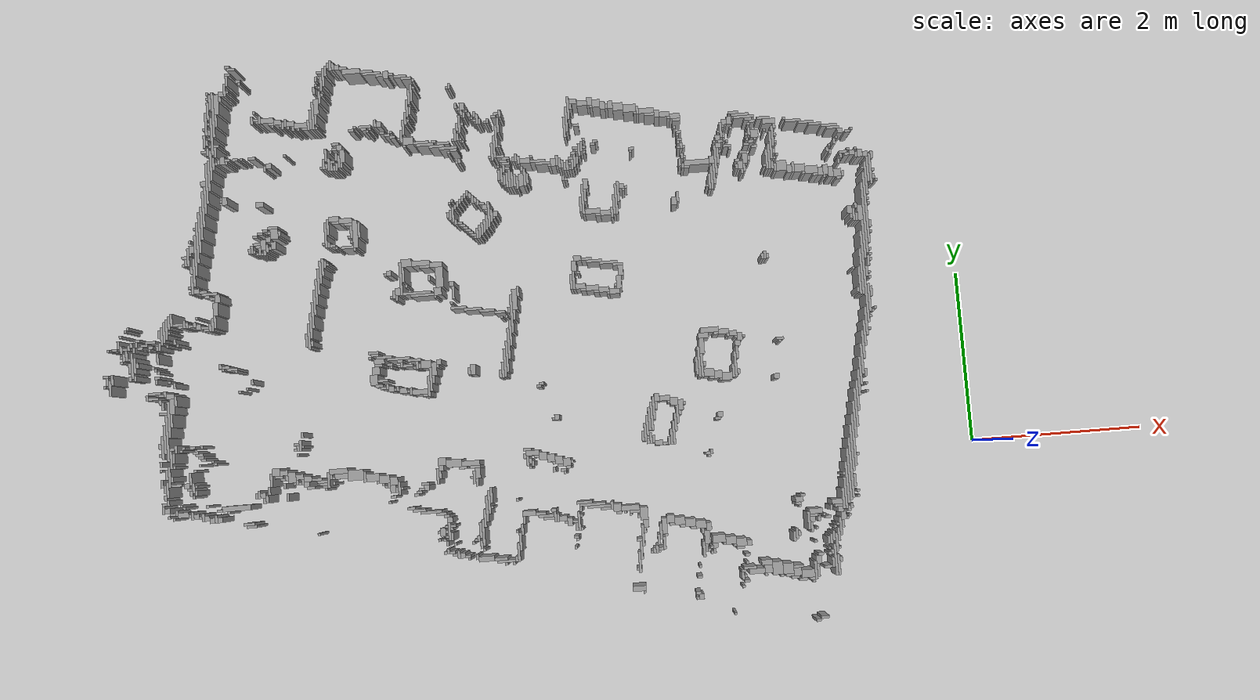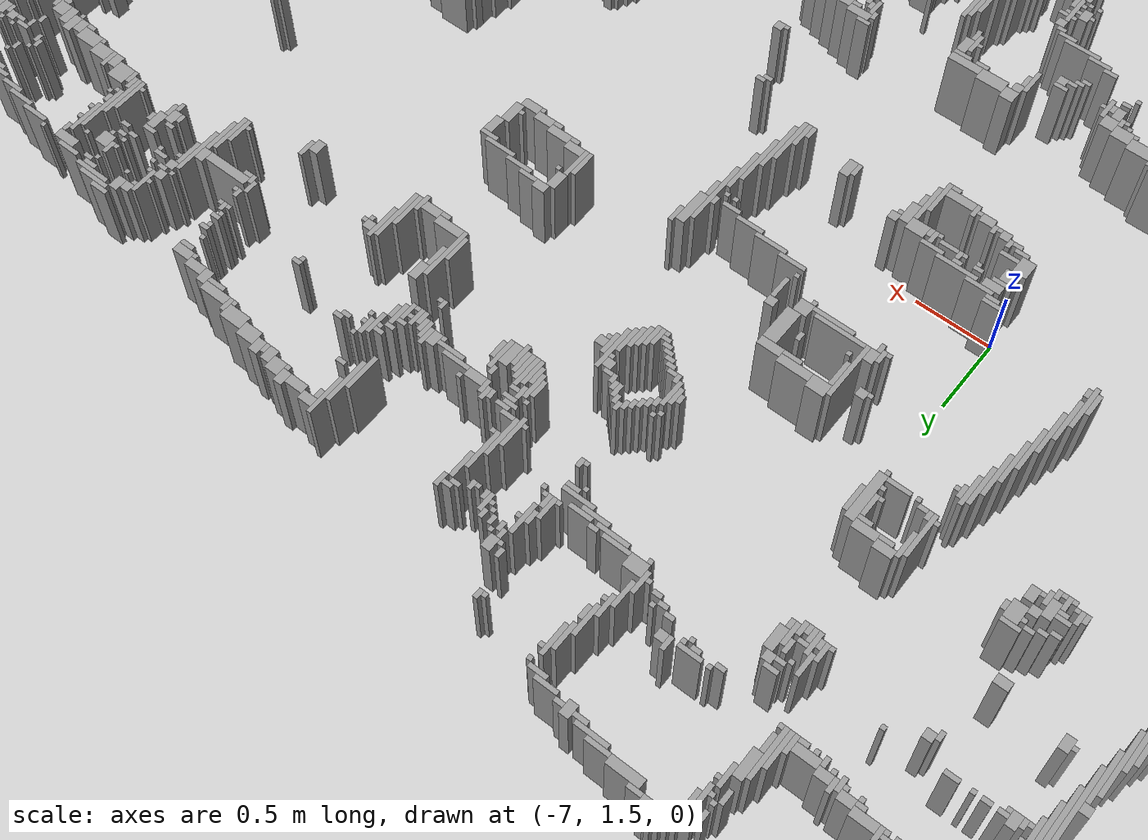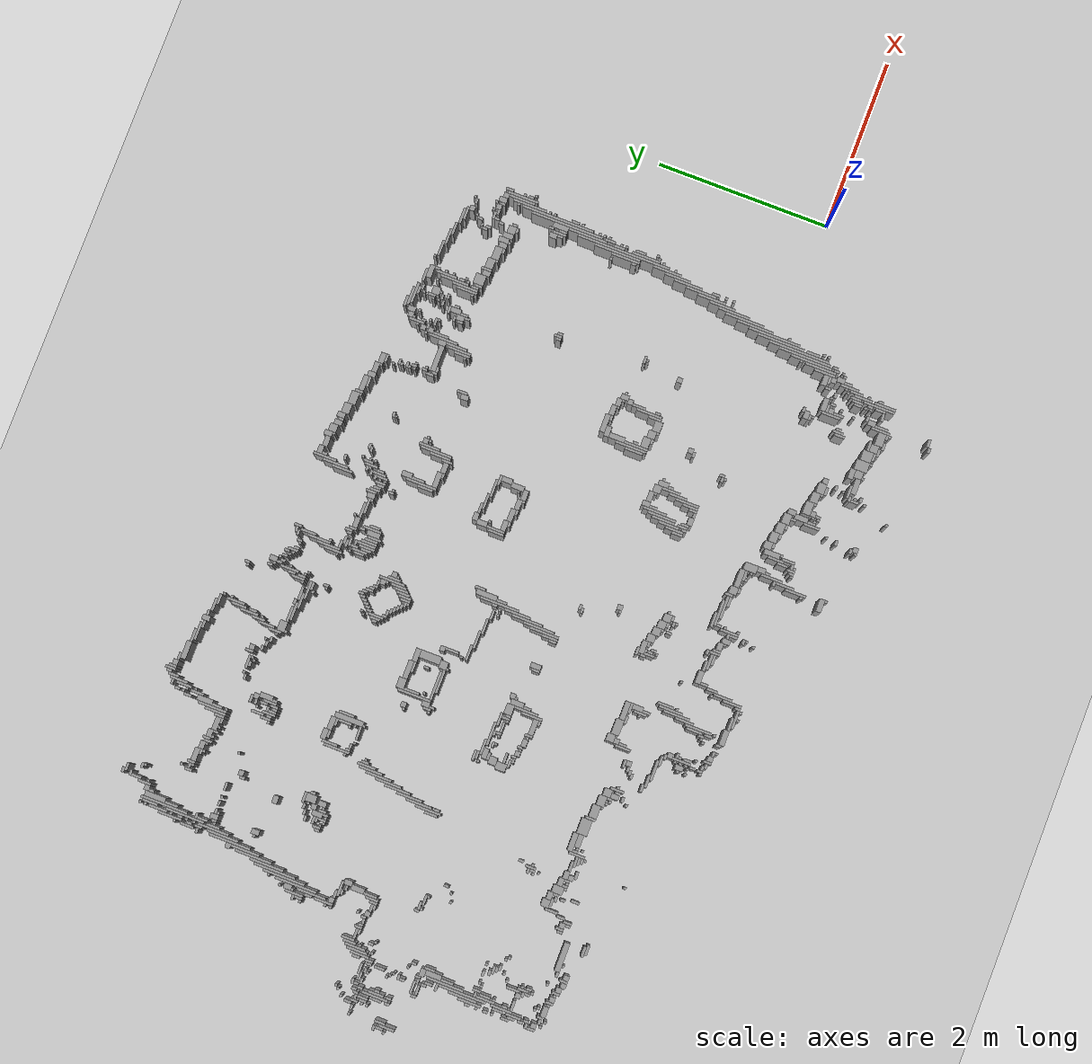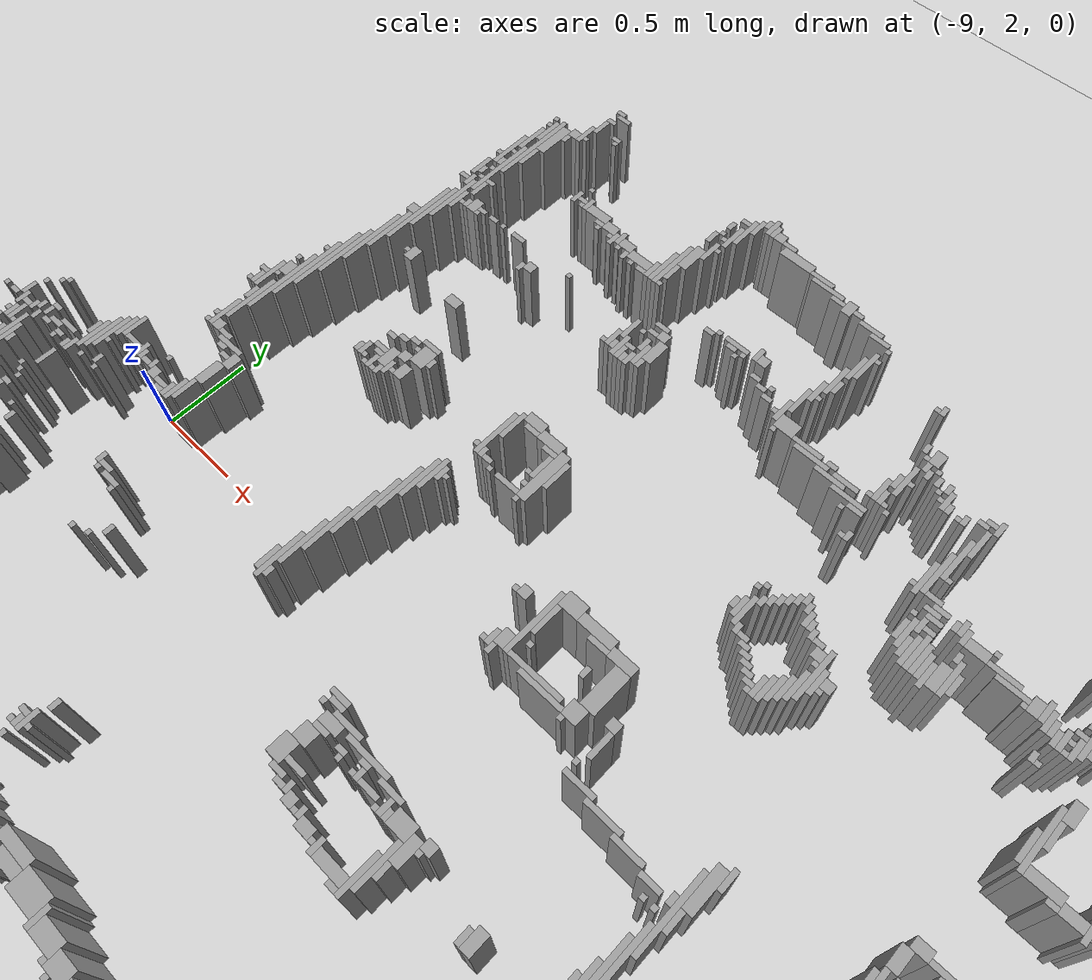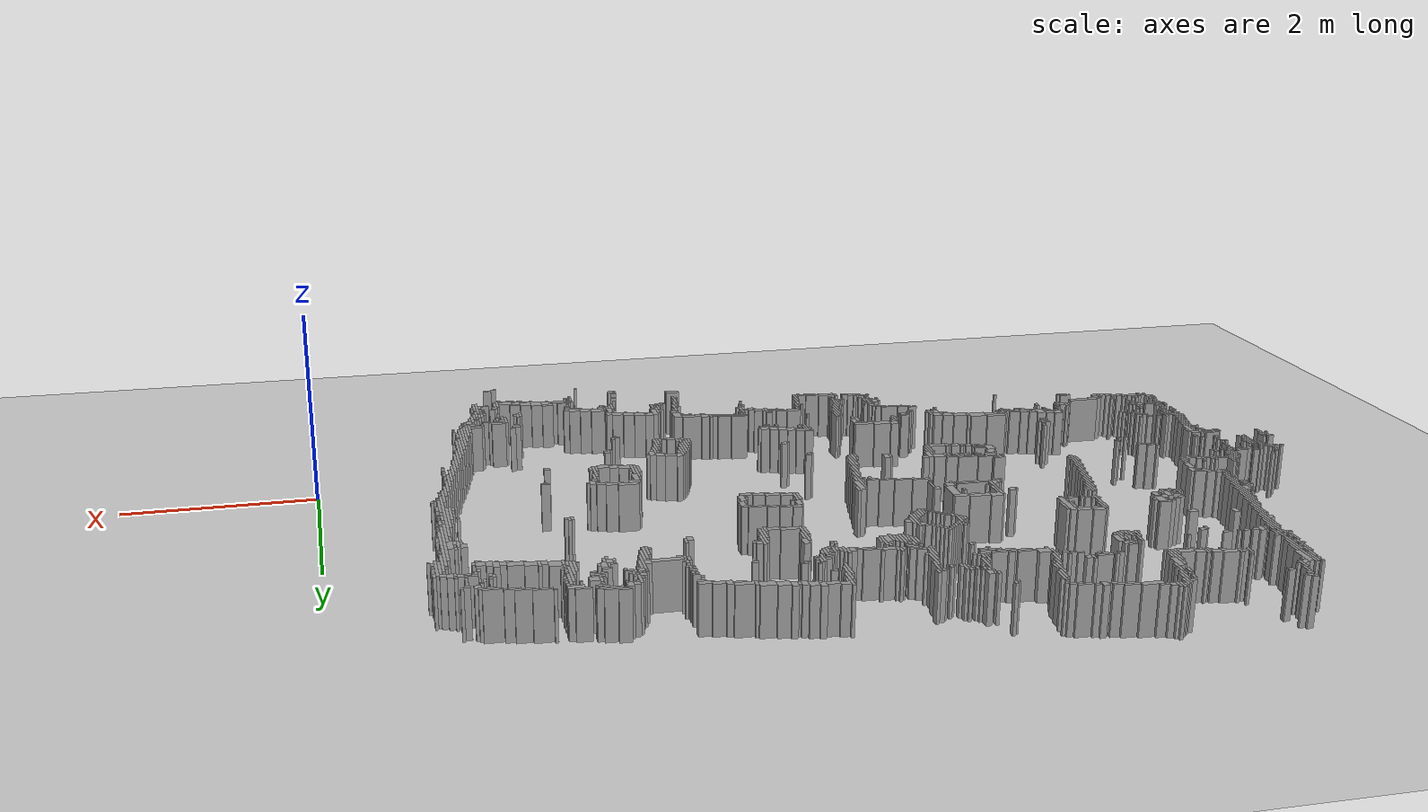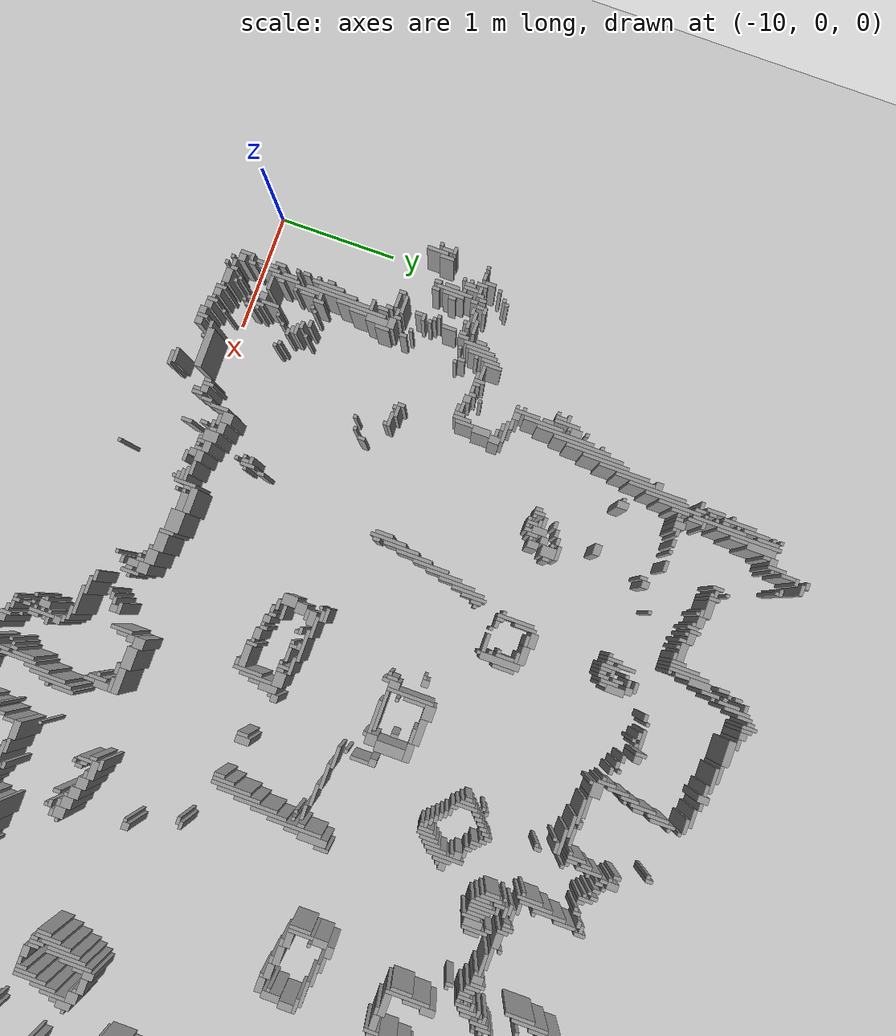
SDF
<?xml version="1.0"?>
<!-- Generated by scripts/map_to_world.py from lab_map.yaml
     (306x234 cells at 0.03 m, origin [-10.1, -1.92]): 1174 boxes from
     5141 occupied cells. Do not edit by hand; regenerate instead. -->
<sdf version="1.6">
  <world name="antropi_lab">
    <include><uri>model://ground_plane</uri></include>
    <include><uri>model://sun</uri></include>
    <scene><shadows>false</shadows></scene>

    <gui fullscreen="0">
      <camera name="user_camera">
        <pose>-3.10 1.00 6.50 0 1.500 1.5708</pose>
        <view_controller>orbit</view_controller>
      </camera>
    </gui>

    <physics type="ode">
      <real_time_update_rate>1000.0</real_time_update_rate>
      <max_step_size>0.001</max_step_size>
      <real_time_factor>1</real_time_factor>
      <ode>
        <solver><type>quick</type><iters>150</iters><sor>1.4</sor></solver>
        <constraints><cfm>0.00001</cfm><erp>0.2</erp>
          <contact_max_correcting_vel>2000.0</contact_max_correcting_vel>
          <contact_surface_layer>0.01</contact_surface_layer></constraints>
      </ode>
    </physics>

    <!-- Lets ROS nodes move models with /gazebo/set_entity_state (used by the moving obstacle). -->
    <plugin name="gazebo_ros_state" filename="libgazebo_ros_state.so">
      <ros><namespace>/gazebo</namespace></ros>
      <update_rate>10.0</update_rate>
    </plugin>

    <model name="antropi_lab_walls">
      <static>true</static>
      <pose>0 0 0 0 0 0</pose>
      <link name="link">
      <collision name="c0">
        <pose>-8.4500 5.0850 0.250 0 0 0</pose>
        <geometry><box><size>0.0600 0.0300 0.500</size></box></geometry>
      </collision>
      <visual name="v0">
        <pose>-8.4500 5.0850 0.250 0 0 0</pose>
        <geometry><box><size>0.0600 0.0300 0.500</size></box></geometry>
        <material><script><uri>file://media/materials/scripts/gazebo.material</uri><name>Gazebo/Grey</name></script></material>
      </visual>
      <collision name="c1">
        <pose>-8.4050 5.0550 0.250 0 0 0</pose>
        <geometry><box><size>0.0900 0.0300 0.500</size></box></geometry>
      </collision>
      <visual name="v1">
        <pose>-8.4050 5.0550 0.250 0 0 0</pose>
        <geometry><box><size>0.0900 0.0300 0.500</size></box></geometry>
        <material><script><uri>file://media/materials/scripts/gazebo.material</uri><name>Gazebo/Grey</name></script></material>
      </visual>
      <collision name="c2">
        <pose>-7.2350 5.0100 0.250 0 0 0</pose>
        <geometry><box><size>0.0300 0.1200 0.500</size></box></geometry>
      </collision>
      <visual name="v2">
        <pose>-7.2350 5.0100 0.250 0 0 0</pose>
        <geometry><box><size>0.0300 0.1200 0.500</size></box></geometry>
        <material><script><uri>file://media/materials/scripts/gazebo.material</uri><name>Gazebo/Grey</name></script></material>
      </visual>
      <collision name="c3">
        <pose>-7.2650 5.0100 0.250 0 0 0</pose>
        <geometry><box><size>0.0300 0.0600 0.500</size></box></geometry>
      </collision>
      <visual name="v3">
        <pose>-7.2650 5.0100 0.250 0 0 0</pose>
        <geometry><box><size>0.0300 0.0600 0.500</size></box></geometry>
        <material><script><uri>file://media/materials/scripts/gazebo.material</uri><name>Gazebo/Grey</name></script></material>
      </visual>
      <collision name="c4">
        <pose>-7.2050 4.9950 0.250 0 0 0</pose>
        <geometry><box><size>0.0300 0.0900 0.500</size></box></geometry>
      </collision>
      <visual name="v4">
        <pose>-7.2050 4.9950 0.250 0 0 0</pose>
        <geometry><box><size>0.0300 0.0900 0.500</size></box></geometry>
        <material><script><uri>file://media/materials/scripts/gazebo.material</uri><name>Gazebo/Grey</name></script></material>
      </visual>
      <collision name="c5">
        <pose>-8.4500 4.9950 0.250 0 0 0</pose>
        <geometry><box><size>0.0600 0.0300 0.500</size></box></geometry>
      </collision>
      <visual name="v5">
        <pose>-8.4500 4.9950 0.250 0 0 0</pose>
        <geometry><box><size>0.0600 0.0300 0.500</size></box></geometry>
        <material><script><uri>file://media/materials/scripts/gazebo.material</uri><name>Gazebo/Grey</name></script></material>
      </visual>
      <collision name="c6">
        <pose>-7.2950 4.9500 0.250 0 0 0</pose>
        <geometry><box><size>0.0300 0.1200 0.500</size></box></geometry>
      </collision>
      <visual name="v6">
        <pose>-7.2950 4.9500 0.250 0 0 0</pose>
        <geometry><box><size>0.0300 0.1200 0.500</size></box></geometry>
        <material><script><uri>file://media/materials/scripts/gazebo.material</uri><name>Gazebo/Grey</name></script></material>
      </visual>
      <collision name="c7">
        <pose>-7.1600 4.9800 0.250 0 0 0</pose>
        <geometry><box><size>0.0600 0.0600 0.500</size></box></geometry>
      </collision>
      <visual name="v7">
        <pose>-7.1600 4.9800 0.250 0 0 0</pose>
        <geometry><box><size>0.0600 0.0600 0.500</size></box></geometry>
        <material><script><uri>file://media/materials/scripts/gazebo.material</uri><name>Gazebo/Grey</name></script></material>
      </visual>
      <collision name="c8">
        <pose>-8.4650 4.9200 0.250 0 0 0</pose>
        <geometry><box><size>0.0300 0.1200 0.500</size></box></geometry>
      </collision>
      <visual name="v8">
        <pose>-8.4650 4.9200 0.250 0 0 0</pose>
        <geometry><box><size>0.0300 0.1200 0.500</size></box></geometry>
        <material><script><uri>file://media/materials/scripts/gazebo.material</uri><name>Gazebo/Grey</name></script></material>
      </visual>
      <collision name="c9">
        <pose>-7.3250 4.8750 0.250 0 0 0</pose>
        <geometry><box><size>0.0300 0.2100 0.500</size></box></geometry>
      </collision>
      <visual name="v9">
        <pose>-7.3250 4.8750 0.250 0 0 0</pose>
        <geometry><box><size>0.0300 0.2100 0.500</size></box></geometry>
        <material><script><uri>file://media/materials/scripts/gazebo.material</uri><name>Gazebo/Grey</name></script></material>
      </visual>
      <collision name="c10">
        <pose>-7.0850 4.9650 0.250 0 0 0</pose>
        <geometry><box><size>0.0900 0.0300 0.500</size></box></geometry>
      </collision>
      <visual name="v10">
        <pose>-7.0850 4.9650 0.250 0 0 0</pose>
        <geometry><box><size>0.0900 0.0300 0.500</size></box></geometry>
        <material><script><uri>file://media/materials/scripts/gazebo.material</uri><name>Gazebo/Grey</name></script></material>
      </visual>
      <collision name="c11">
        <pose>-7.3700 4.9350 0.250 0 0 0</pose>
        <geometry><box><size>0.0600 0.0300 0.500</size></box></geometry>
      </collision>
      <visual name="v11">
        <pose>-7.3700 4.9350 0.250 0 0 0</pose>
        <geometry><box><size>0.0600 0.0300 0.500</size></box></geometry>
        <material><script><uri>file://media/materials/scripts/gazebo.material</uri><name>Gazebo/Grey</name></script></material>
      </visual>
      <collision name="c12">
        <pose>-6.9950 4.9200 0.250 0 0 0</pose>
        <geometry><box><size>0.2100 0.0600 0.500</size></box></geometry>
      </collision>
      <visual name="v12">
        <pose>-6.9950 4.9200 0.250 0 0 0</pose>
        <geometry><box><size>0.2100 0.0600 0.500</size></box></geometry>
        <material><script><uri>file://media/materials/scripts/gazebo.material</uri><name>Gazebo/Grey</name></script></material>
      </visual>
      <collision name="c13">
        <pose>-8.3300 4.9050 0.250 0 0 0</pose>
        <geometry><box><size>0.0600 0.0300 0.500</size></box></geometry>
      </collision>
      <visual name="v13">
        <pose>-8.3300 4.9050 0.250 0 0 0</pose>
        <geometry><box><size>0.0600 0.0300 0.500</size></box></geometry>
        <material><script><uri>file://media/materials/scripts/gazebo.material</uri><name>Gazebo/Grey</name></script></material>
      </visual>
      <collision name="c14">
        <pose>-6.8150 4.9050 0.250 0 0 0</pose>
        <geometry><box><size>0.1500 0.0300 0.500</size></box></geometry>
      </collision>
      <visual name="v14">
        <pose>-6.8150 4.9050 0.250 0 0 0</pose>
        <geometry><box><size>0.1500 0.0300 0.500</size></box></geometry>
        <material><script><uri>file://media/materials/scripts/gazebo.material</uri><name>Gazebo/Grey</name></script></material>
      </visual>
      <collision name="c15">
        <pose>-8.4950 4.8150 0.250 0 0 0</pose>
        <geometry><box><size>0.0300 0.1500 0.500</size></box></geometry>
      </collision>
      <visual name="v15">
        <pose>-8.4950 4.8150 0.250 0 0 0</pose>
        <geometry><box><size>0.0300 0.1500 0.500</size></box></geometry>
        <material><script><uri>file://media/materials/scripts/gazebo.material</uri><name>Gazebo/Grey</name></script></material>
      </visual>
      <collision name="c16">
        <pose>-8.3150 4.8750 0.250 0 0 0</pose>
        <geometry><box><size>0.0300 0.0300 0.500</size></box></geometry>
      </collision>
      <visual name="v16">
        <pose>-8.3150 4.8750 0.250 0 0 0</pose>
        <geometry><box><size>0.0300 0.0300 0.500</size></box></geometry>
        <material><script><uri>file://media/materials/scripts/gazebo.material</uri><name>Gazebo/Grey</name></script></material>
      </visual>
      <collision name="c17">
        <pose>-7.4150 4.8600 0.250 0 0 0</pose>
        <geometry><box><size>0.0300 0.0600 0.500</size></box></geometry>
      </collision>
      <visual name="v17">
        <pose>-7.4150 4.8600 0.250 0 0 0</pose>
        <geometry><box><size>0.0300 0.0600 0.500</size></box></geometry>
        <material><script><uri>file://media/materials/scripts/gazebo.material</uri><name>Gazebo/Grey</name></script></material>
      </visual>
      <collision name="c18">
        <pose>-7.3550 4.8000 0.250 0 0 0</pose>
        <geometry><box><size>0.0300 0.1800 0.500</size></box></geometry>
      </collision>
      <visual name="v18">
        <pose>-7.3550 4.8000 0.250 0 0 0</pose>
        <geometry><box><size>0.0300 0.1800 0.500</size></box></geometry>
        <material><script><uri>file://media/materials/scripts/gazebo.material</uri><name>Gazebo/Grey</name></script></material>
      </visual>
      <collision name="c19">
        <pose>-6.7550 4.8750 0.250 0 0 0</pose>
        <geometry><box><size>0.2100 0.0300 0.500</size></box></geometry>
      </collision>
      <visual name="v19">
        <pose>-6.7550 4.8750 0.250 0 0 0</pose>
        <geometry><box><size>0.2100 0.0300 0.500</size></box></geometry>
        <material><script><uri>file://media/materials/scripts/gazebo.material</uri><name>Gazebo/Grey</name></script></material>
      </visual>
      <collision name="c20">
        <pose>-6.5900 4.8450 0.250 0 0 0</pose>
        <geometry><box><size>0.0600 0.0900 0.500</size></box></geometry>
      </collision>
      <visual name="v20">
        <pose>-6.5900 4.8450 0.250 0 0 0</pose>
        <geometry><box><size>0.0600 0.0900 0.500</size></box></geometry>
        <material><script><uri>file://media/materials/scripts/gazebo.material</uri><name>Gazebo/Grey</name></script></material>
      </visual>
      <collision name="c21">
        <pose>-6.6650 4.8450 0.250 0 0 0</pose>
        <geometry><box><size>0.0900 0.0300 0.500</size></box></geometry>
      </collision>
      <visual name="v21">
        <pose>-6.6650 4.8450 0.250 0 0 0</pose>
        <geometry><box><size>0.0900 0.0300 0.500</size></box></geometry>
        <material><script><uri>file://media/materials/scripts/gazebo.material</uri><name>Gazebo/Grey</name></script></material>
      </visual>
      <collision name="c22">
        <pose>-6.5300 4.8450 0.250 0 0 0</pose>
        <geometry><box><size>0.0600 0.0300 0.500</size></box></geometry>
      </collision>
      <visual name="v22">
        <pose>-6.5300 4.8450 0.250 0 0 0</pose>
        <geometry><box><size>0.0600 0.0300 0.500</size></box></geometry>
        <material><script><uri>file://media/materials/scripts/gazebo.material</uri><name>Gazebo/Grey</name></script></material>
      </visual>
      <collision name="c23">
        <pose>-6.4250 4.8150 0.250 0 0 0</pose>
        <geometry><box><size>0.1500 0.0300 0.500</size></box></geometry>
      </collision>
      <visual name="v23">
        <pose>-6.4250 4.8150 0.250 0 0 0</pose>
        <geometry><box><size>0.1500 0.0300 0.500</size></box></geometry>
        <material><script><uri>file://media/materials/scripts/gazebo.material</uri><name>Gazebo/Grey</name></script></material>
      </visual>
      <collision name="c24">
        <pose>-8.7050 4.7850 0.250 0 0 0</pose>
        <geometry><box><size>0.0300 0.0300 0.500</size></box></geometry>
      </collision>
      <visual name="v24">
        <pose>-8.7050 4.7850 0.250 0 0 0</pose>
        <geometry><box><size>0.0300 0.0300 0.500</size></box></geometry>
        <material><script><uri>file://media/materials/scripts/gazebo.material</uri><name>Gazebo/Grey</name></script></material>
      </visual>
      <collision name="c25">
        <pose>-8.6450 4.5300 0.250 0 0 0</pose>
        <geometry><box><size>0.0300 0.5400 0.500</size></box></geometry>
      </collision>
      <visual name="v25">
        <pose>-8.6450 4.5300 0.250 0 0 0</pose>
        <geometry><box><size>0.0300 0.5400 0.500</size></box></geometry>
        <material><script><uri>file://media/materials/scripts/gazebo.material</uri><name>Gazebo/Grey</name></script></material>
      </visual>
      <collision name="c26">
        <pose>-8.5400 4.7700 0.250 0 0 0</pose>
        <geometry><box><size>0.0600 0.0600 0.500</size></box></geometry>
      </collision>
      <visual name="v26">
        <pose>-8.5400 4.7700 0.250 0 0 0</pose>
        <geometry><box><size>0.0600 0.0600 0.500</size></box></geometry>
        <material><script><uri>file://media/materials/scripts/gazebo.material</uri><name>Gazebo/Grey</name></script></material>
      </visual>
      <collision name="c27">
        <pose>-8.4650 4.7850 0.250 0 0 0</pose>
        <geometry><box><size>0.0300 0.0300 0.500</size></box></geometry>
      </collision>
      <visual name="v27">
        <pose>-8.4650 4.7850 0.250 0 0 0</pose>
        <geometry><box><size>0.0300 0.0300 0.500</size></box></geometry>
        <material><script><uri>file://media/materials/scripts/gazebo.material</uri><name>Gazebo/Grey</name></script></material>
      </visual>
      <collision name="c28">
        <pose>-7.4150 4.7850 0.250 0 0 0</pose>
        <geometry><box><size>0.0300 0.0300 0.500</size></box></geometry>
      </collision>
      <visual name="v28">
        <pose>-7.4150 4.7850 0.250 0 0 0</pose>
        <geometry><box><size>0.0300 0.0300 0.500</size></box></geometry>
        <material><script><uri>file://media/materials/scripts/gazebo.material</uri><name>Gazebo/Grey</name></script></material>
      </visual>
      <collision name="c29">
        <pose>-6.3500 4.7850 0.250 0 0 0</pose>
        <geometry><box><size>0.1200 0.0300 0.500</size></box></geometry>
      </collision>
      <visual name="v29">
        <pose>-6.3500 4.7850 0.250 0 0 0</pose>
        <geometry><box><size>0.1200 0.0300 0.500</size></box></geometry>
        <material><script><uri>file://media/materials/scripts/gazebo.material</uri><name>Gazebo/Grey</name></script></material>
      </visual>
      <collision name="c30">
        <pose>-8.6750 4.6800 0.250 0 0 0</pose>
        <geometry><box><size>0.0300 0.1800 0.500</size></box></geometry>
      </collision>
      <visual name="v30">
        <pose>-8.6750 4.6800 0.250 0 0 0</pose>
        <geometry><box><size>0.0300 0.1800 0.500</size></box></geometry>
        <material><script><uri>file://media/materials/scripts/gazebo.material</uri><name>Gazebo/Grey</name></script></material>
      </visual>
      <collision name="c31">
        <pose>-8.6000 4.6500 0.250 0 0 0</pose>
        <geometry><box><size>0.0600 0.2400 0.500</size></box></geometry>
      </collision>
      <visual name="v31">
        <pose>-8.6000 4.6500 0.250 0 0 0</pose>
        <geometry><box><size>0.0600 0.2400 0.500</size></box></geometry>
        <material><script><uri>file://media/materials/scripts/gazebo.material</uri><name>Gazebo/Grey</name></script></material>
      </visual>
      <collision name="c32">
        <pose>-7.4450 4.7250 0.250 0 0 0</pose>
        <geometry><box><size>0.0300 0.0900 0.500</size></box></geometry>
      </collision>
      <visual name="v32">
        <pose>-7.4450 4.7250 0.250 0 0 0</pose>
        <geometry><box><size>0.0300 0.0900 0.500</size></box></geometry>
        <material><script><uri>file://media/materials/scripts/gazebo.material</uri><name>Gazebo/Grey</name></script></material>
      </visual>
      <collision name="c33">
        <pose>-7.3850 4.7550 0.250 0 0 0</pose>
        <geometry><box><size>0.0300 0.0300 0.500</size></box></geometry>
      </collision>
      <visual name="v33">
        <pose>-7.3850 4.7550 0.250 0 0 0</pose>
        <geometry><box><size>0.0300 0.0300 0.500</size></box></geometry>
        <material><script><uri>file://media/materials/scripts/gazebo.material</uri><name>Gazebo/Grey</name></script></material>
      </visual>
      <collision name="c34">
        <pose>-6.2750 4.7550 0.250 0 0 0</pose>
        <geometry><box><size>0.0300 0.0300 0.500</size></box></geometry>
      </collision>
      <visual name="v34">
        <pose>-6.2750 4.7550 0.250 0 0 0</pose>
        <geometry><box><size>0.0300 0.0300 0.500</size></box></geometry>
        <material><script><uri>file://media/materials/scripts/gazebo.material</uri><name>Gazebo/Grey</name></script></material>
      </visual>
      <collision name="c35">
        <pose>-8.7050 4.7250 0.250 0 0 0</pose>
        <geometry><box><size>0.0300 0.0300 0.500</size></box></geometry>
      </collision>
      <visual name="v35">
        <pose>-8.7050 4.7250 0.250 0 0 0</pose>
        <geometry><box><size>0.0300 0.0300 0.500</size></box></geometry>
        <material><script><uri>file://media/materials/scripts/gazebo.material</uri><name>Gazebo/Grey</name></script></material>
      </visual>
      <collision name="c36">
        <pose>-8.5550 4.7100 0.250 0 0 0</pose>
        <geometry><box><size>0.0300 0.0600 0.500</size></box></geometry>
      </collision>
      <visual name="v36">
        <pose>-8.5550 4.7100 0.250 0 0 0</pose>
        <geometry><box><size>0.0300 0.0600 0.500</size></box></geometry>
        <material><script><uri>file://media/materials/scripts/gazebo.material</uri><name>Gazebo/Grey</name></script></material>
      </visual>
      <collision name="c37">
        <pose>-7.3850 4.6350 0.250 0 0 0</pose>
        <geometry><box><size>0.0300 0.1500 0.500</size></box></geometry>
      </collision>
      <visual name="v37">
        <pose>-7.3850 4.6350 0.250 0 0 0</pose>
        <geometry><box><size>0.0300 0.1500 0.500</size></box></geometry>
        <material><script><uri>file://media/materials/scripts/gazebo.material</uri><name>Gazebo/Grey</name></script></material>
      </visual>
      <collision name="c38">
        <pose>-6.3050 4.6050 0.250 0 0 0</pose>
        <geometry><box><size>0.0300 0.2100 0.500</size></box></geometry>
      </collision>
      <visual name="v38">
        <pose>-6.3050 4.6050 0.250 0 0 0</pose>
        <geometry><box><size>0.0300 0.2100 0.500</size></box></geometry>
        <material><script><uri>file://media/materials/scripts/gazebo.material</uri><name>Gazebo/Grey</name></script></material>
      </visual>
      <collision name="c39">
        <pose>-8.7050 4.5750 0.250 0 0 0</pose>
        <geometry><box><size>0.0300 0.2100 0.500</size></box></geometry>
      </collision>
      <visual name="v39">
        <pose>-8.7050 4.5750 0.250 0 0 0</pose>
        <geometry><box><size>0.0300 0.2100 0.500</size></box></geometry>
        <material><script><uri>file://media/materials/scripts/gazebo.material</uri><name>Gazebo/Grey</name></script></material>
      </visual>
      <collision name="c40">
        <pose>-7.3550 4.6650 0.250 0 0 0</pose>
        <geometry><box><size>0.0300 0.0300 0.500</size></box></geometry>
      </collision>
      <visual name="v40">
        <pose>-7.3550 4.6650 0.250 0 0 0</pose>
        <geometry><box><size>0.0300 0.0300 0.500</size></box></geometry>
        <material><script><uri>file://media/materials/scripts/gazebo.material</uri><name>Gazebo/Grey</name></script></material>
      </visual>
      <collision name="c41">
        <pose>-6.2750 4.6650 0.250 0 0 0</pose>
        <geometry><box><size>0.0300 0.0300 0.500</size></box></geometry>
      </collision>
      <visual name="v41">
        <pose>-6.2750 4.6650 0.250 0 0 0</pose>
        <geometry><box><size>0.0300 0.0300 0.500</size></box></geometry>
        <material><script><uri>file://media/materials/scripts/gazebo.material</uri><name>Gazebo/Grey</name></script></material>
      </visual>
      <collision name="c42">
        <pose>-5.8550 4.6500 0.250 0 0 0</pose>
        <geometry><box><size>0.0300 0.0600 0.500</size></box></geometry>
      </collision>
      <visual name="v42">
        <pose>-5.8550 4.6500 0.250 0 0 0</pose>
        <geometry><box><size>0.0300 0.0600 0.500</size></box></geometry>
        <material><script><uri>file://media/materials/scripts/gazebo.material</uri><name>Gazebo/Grey</name></script></material>
      </visual>
      <collision name="c43">
        <pose>-6.3350 4.5600 0.250 0 0 0</pose>
        <geometry><box><size>0.0300 0.1800 0.500</size></box></geometry>
      </collision>
      <visual name="v43">
        <pose>-6.3350 4.5600 0.250 0 0 0</pose>
        <geometry><box><size>0.0300 0.1800 0.500</size></box></geometry>
        <material><script><uri>file://media/materials/scripts/gazebo.material</uri><name>Gazebo/Grey</name></script></material>
      </visual>
      <collision name="c44">
        <pose>-5.8850 4.6350 0.250 0 0 0</pose>
        <geometry><box><size>0.0300 0.0300 0.500</size></box></geometry>
      </collision>
      <visual name="v44">
        <pose>-5.8850 4.6350 0.250 0 0 0</pose>
        <geometry><box><size>0.0300 0.0300 0.500</size></box></geometry>
        <material><script><uri>file://media/materials/scripts/gazebo.material</uri><name>Gazebo/Grey</name></script></material>
      </visual>
      <collision name="c45">
        <pose>-7.4300 4.5300 0.250 0 0 0</pose>
        <geometry><box><size>0.0600 0.1800 0.500</size></box></geometry>
      </collision>
      <visual name="v45">
        <pose>-7.4300 4.5300 0.250 0 0 0</pose>
        <geometry><box><size>0.0600 0.1800 0.500</size></box></geometry>
        <material><script><uri>file://media/materials/scripts/gazebo.material</uri><name>Gazebo/Grey</name></script></material>
      </visual>
      <collision name="c46">
        <pose>-7.4750 4.4250 0.250 0 0 0</pose>
        <geometry><box><size>0.0300 0.3300 0.500</size></box></geometry>
      </collision>
      <visual name="v46">
        <pose>-7.4750 4.4250 0.250 0 0 0</pose>
        <geometry><box><size>0.0300 0.3300 0.500</size></box></geometry>
        <material><script><uri>file://media/materials/scripts/gazebo.material</uri><name>Gazebo/Grey</name></script></material>
      </visual>
      <collision name="c47">
        <pose>-8.7350 4.4250 0.250 0 0 0</pose>
        <geometry><box><size>0.0300 0.2700 0.500</size></box></geometry>
      </collision>
      <visual name="v47">
        <pose>-8.7350 4.4250 0.250 0 0 0</pose>
        <geometry><box><size>0.0300 0.2700 0.500</size></box></geometry>
        <material><script><uri>file://media/materials/scripts/gazebo.material</uri><name>Gazebo/Grey</name></script></material>
      </visual>
      <collision name="c48">
        <pose>-8.6150 4.4550 0.250 0 0 0</pose>
        <geometry><box><size>0.0300 0.1500 0.500</size></box></geometry>
      </collision>
      <visual name="v48">
        <pose>-8.6150 4.4550 0.250 0 0 0</pose>
        <geometry><box><size>0.0300 0.1500 0.500</size></box></geometry>
        <material><script><uri>file://media/materials/scripts/gazebo.material</uri><name>Gazebo/Grey</name></script></material>
      </visual>
      <collision name="c49">
        <pose>-8.1650 4.5150 0.250 0 0 0</pose>
        <geometry><box><size>0.0300 0.0300 0.500</size></box></geometry>
      </collision>
      <visual name="v49">
        <pose>-8.1650 4.5150 0.250 0 0 0</pose>
        <geometry><box><size>0.0300 0.0300 0.500</size></box></geometry>
        <material><script><uri>file://media/materials/scripts/gazebo.material</uri><name>Gazebo/Grey</name></script></material>
      </visual>
      <collision name="c50">
        <pose>-6.3650 4.4250 0.250 0 0 0</pose>
        <geometry><box><size>0.0300 0.2100 0.500</size></box></geometry>
      </collision>
      <visual name="v50">
        <pose>-6.3650 4.4250 0.250 0 0 0</pose>
        <geometry><box><size>0.0300 0.2100 0.500</size></box></geometry>
        <material><script><uri>file://media/materials/scripts/gazebo.material</uri><name>Gazebo/Grey</name></script></material>
      </visual>
      <collision name="c51">
        <pose>-8.6750 4.2750 0.250 0 0 0</pose>
        <geometry><box><size>0.0300 0.4500 0.500</size></box></geometry>
      </collision>
      <visual name="v51">
        <pose>-8.6750 4.2750 0.250 0 0 0</pose>
        <geometry><box><size>0.0300 0.4500 0.500</size></box></geometry>
        <material><script><uri>file://media/materials/scripts/gazebo.material</uri><name>Gazebo/Grey</name></script></material>
      </visual>
      <collision name="c52">
        <pose>-7.5050 4.3800 0.250 0 0 0</pose>
        <geometry><box><size>0.0300 0.2400 0.500</size></box></geometry>
      </collision>
      <visual name="v52">
        <pose>-7.5050 4.3800 0.250 0 0 0</pose>
        <geometry><box><size>0.0300 0.2400 0.500</size></box></geometry>
        <material><script><uri>file://media/materials/scripts/gazebo.material</uri><name>Gazebo/Grey</name></script></material>
      </visual>
      <collision name="c53">
        <pose>-8.1950 4.4250 0.250 0 0 0</pose>
        <geometry><box><size>0.0300 0.0900 0.500</size></box></geometry>
      </collision>
      <visual name="v53">
        <pose>-8.1950 4.4250 0.250 0 0 0</pose>
        <geometry><box><size>0.0300 0.0900 0.500</size></box></geometry>
        <material><script><uri>file://media/materials/scripts/gazebo.material</uri><name>Gazebo/Grey</name></script></material>
      </visual>
      <collision name="c54">
        <pose>-8.1050 4.4250 0.250 0 0 0</pose>
        <geometry><box><size>0.0300 0.0900 0.500</size></box></geometry>
      </collision>
      <visual name="v54">
        <pose>-8.1050 4.4250 0.250 0 0 0</pose>
        <geometry><box><size>0.0300 0.0900 0.500</size></box></geometry>
        <material><script><uri>file://media/materials/scripts/gazebo.material</uri><name>Gazebo/Grey</name></script></material>
      </visual>
      <collision name="c55">
        <pose>-8.7050 4.4250 0.250 0 0 0</pose>
        <geometry><box><size>0.0300 0.0300 0.500</size></box></geometry>
      </collision>
      <visual name="v55">
        <pose>-8.7050 4.4250 0.250 0 0 0</pose>
        <geometry><box><size>0.0300 0.0300 0.500</size></box></geometry>
        <material><script><uri>file://media/materials/scripts/gazebo.material</uri><name>Gazebo/Grey</name></script></material>
      </visual>
      <collision name="c56">
        <pose>-8.1500 4.4250 0.250 0 0 0</pose>
        <geometry><box><size>0.0600 0.0300 0.500</size></box></geometry>
      </collision>
      <visual name="v56">
        <pose>-8.1500 4.4250 0.250 0 0 0</pose>
        <geometry><box><size>0.0600 0.0300 0.500</size></box></geometry>
        <material><script><uri>file://media/materials/scripts/gazebo.material</uri><name>Gazebo/Grey</name></script></material>
      </visual>
      <collision name="c57">
        <pose>-8.0150 4.4100 0.250 0 0 0</pose>
        <geometry><box><size>0.1500 0.0600 0.500</size></box></geometry>
      </collision>
      <visual name="v57">
        <pose>-8.0150 4.4100 0.250 0 0 0</pose>
        <geometry><box><size>0.1500 0.0600 0.500</size></box></geometry>
        <material><script><uri>file://media/materials/scripts/gazebo.material</uri><name>Gazebo/Grey</name></script></material>
      </visual>
      <collision name="c58">
        <pose>-7.4450 4.3800 0.250 0 0 0</pose>
        <geometry><box><size>0.0300 0.1200 0.500</size></box></geometry>
      </collision>
      <visual name="v58">
        <pose>-7.4450 4.3800 0.250 0 0 0</pose>
        <geometry><box><size>0.0300 0.1200 0.500</size></box></geometry>
        <material><script><uri>file://media/materials/scripts/gazebo.material</uri><name>Gazebo/Grey</name></script></material>
      </visual>
      <collision name="c59">
        <pose>-6.3350 4.3950 0.250 0 0 0</pose>
        <geometry><box><size>0.0300 0.0900 0.500</size></box></geometry>
      </collision>
      <visual name="v59">
        <pose>-6.3350 4.3950 0.250 0 0 0</pose>
        <geometry><box><size>0.0300 0.0900 0.500</size></box></geometry>
        <material><script><uri>file://media/materials/scripts/gazebo.material</uri><name>Gazebo/Grey</name></script></material>
      </visual>
      <collision name="c60">
        <pose>-5.7950 4.4100 0.250 0 0 0</pose>
        <geometry><box><size>0.0300 0.0600 0.500</size></box></geometry>
      </collision>
      <visual name="v60">
        <pose>-5.7950 4.4100 0.250 0 0 0</pose>
        <geometry><box><size>0.0300 0.0600 0.500</size></box></geometry>
        <material><script><uri>file://media/materials/scripts/gazebo.material</uri><name>Gazebo/Grey</name></script></material>
      </visual>
      <collision name="c61">
        <pose>-5.7200 4.3950 0.250 0 0 0</pose>
        <geometry><box><size>0.0600 0.0900 0.500</size></box></geometry>
      </collision>
      <visual name="v61">
        <pose>-5.7200 4.3950 0.250 0 0 0</pose>
        <geometry><box><size>0.0600 0.0900 0.500</size></box></geometry>
        <material><script><uri>file://media/materials/scripts/gazebo.material</uri><name>Gazebo/Grey</name></script></material>
      </visual>
      <collision name="c62">
        <pose>-8.1350 4.3950 0.250 0 0 0</pose>
        <geometry><box><size>0.0300 0.0300 0.500</size></box></geometry>
      </collision>
      <visual name="v62">
        <pose>-8.1350 4.3950 0.250 0 0 0</pose>
        <geometry><box><size>0.0300 0.0300 0.500</size></box></geometry>
        <material><script><uri>file://media/materials/scripts/gazebo.material</uri><name>Gazebo/Grey</name></script></material>
      </visual>
      <collision name="c63">
        <pose>-7.8950 4.3800 0.250 0 0 0</pose>
        <geometry><box><size>0.0900 0.0600 0.500</size></box></geometry>
      </collision>
      <visual name="v63">
        <pose>-7.8950 4.3800 0.250 0 0 0</pose>
        <geometry><box><size>0.0900 0.0600 0.500</size></box></geometry>
        <material><script><uri>file://media/materials/scripts/gazebo.material</uri><name>Gazebo/Grey</name></script></material>
      </visual>
      <collision name="c64">
        <pose>-7.8050 4.3650 0.250 0 0 0</pose>
        <geometry><box><size>0.0300 0.0900 0.500</size></box></geometry>
      </collision>
      <visual name="v64">
        <pose>-7.8050 4.3650 0.250 0 0 0</pose>
        <geometry><box><size>0.0300 0.0900 0.500</size></box></geometry>
        <material><script><uri>file://media/materials/scripts/gazebo.material</uri><name>Gazebo/Grey</name></script></material>
      </visual>
      <collision name="c65">
        <pose>-4.4750 4.2750 0.250 0 0 0</pose>
        <geometry><box><size>0.0300 0.2700 0.500</size></box></geometry>
      </collision>
      <visual name="v65">
        <pose>-4.4750 4.2750 0.250 0 0 0</pose>
        <geometry><box><size>0.0300 0.2700 0.500</size></box></geometry>
        <material><script><uri>file://media/materials/scripts/gazebo.material</uri><name>Gazebo/Grey</name></script></material>
      </visual>
      <collision name="c66">
        <pose>-8.7650 4.3650 0.250 0 0 0</pose>
        <geometry><box><size>0.0300 0.0300 0.500</size></box></geometry>
      </collision>
      <visual name="v66">
        <pose>-8.7650 4.3650 0.250 0 0 0</pose>
        <geometry><box><size>0.0300 0.0300 0.500</size></box></geometry>
        <material><script><uri>file://media/materials/scripts/gazebo.material</uri><name>Gazebo/Grey</name></script></material>
      </visual>
      <collision name="c67">
        <pose>-7.9700 4.3650 0.250 0 0 0</pose>
        <geometry><box><size>0.0600 0.0300 0.500</size></box></geometry>
      </collision>
      <visual name="v67">
        <pose>-7.9700 4.3650 0.250 0 0 0</pose>
        <geometry><box><size>0.0600 0.0300 0.500</size></box></geometry>
        <material><script><uri>file://media/materials/scripts/gazebo.material</uri><name>Gazebo/Grey</name></script></material>
      </visual>
      <collision name="c68">
        <pose>-7.8350 4.3350 0.250 0 0 0</pose>
        <geometry><box><size>0.0300 0.0900 0.500</size></box></geometry>
      </collision>
      <visual name="v68">
        <pose>-7.8350 4.3350 0.250 0 0 0</pose>
        <geometry><box><size>0.0300 0.0900 0.500</size></box></geometry>
        <material><script><uri>file://media/materials/scripts/gazebo.material</uri><name>Gazebo/Grey</name></script></material>
      </visual>
      <collision name="c69">
        <pose>-7.7450 4.3500 0.250 0 0 0</pose>
        <geometry><box><size>0.0900 0.0600 0.500</size></box></geometry>
      </collision>
      <visual name="v69">
        <pose>-7.7450 4.3500 0.250 0 0 0</pose>
        <geometry><box><size>0.0900 0.0600 0.500</size></box></geometry>
        <material><script><uri>file://media/materials/scripts/gazebo.material</uri><name>Gazebo/Grey</name></script></material>
      </visual>
      <collision name="c70">
        <pose>-7.5350 4.3200 0.250 0 0 0</pose>
        <geometry><box><size>0.0300 0.1200 0.500</size></box></geometry>
      </collision>
      <visual name="v70">
        <pose>-7.5350 4.3200 0.250 0 0 0</pose>
        <geometry><box><size>0.0300 0.1200 0.500</size></box></geometry>
        <material><script><uri>file://media/materials/scripts/gazebo.material</uri><name>Gazebo/Grey</name></script></material>
      </visual>
      <collision name="c71">
        <pose>-6.3950 4.3050 0.250 0 0 0</pose>
        <geometry><box><size>0.0300 0.1500 0.500</size></box></geometry>
      </collision>
      <visual name="v71">
        <pose>-6.3950 4.3050 0.250 0 0 0</pose>
        <geometry><box><size>0.0300 0.1500 0.500</size></box></geometry>
        <material><script><uri>file://media/materials/scripts/gazebo.material</uri><name>Gazebo/Grey</name></script></material>
      </visual>
      <collision name="c72">
        <pose>-5.7650 4.3650 0.250 0 0 0</pose>
        <geometry><box><size>0.0300 0.0300 0.500</size></box></geometry>
      </collision>
      <visual name="v72">
        <pose>-5.7650 4.3650 0.250 0 0 0</pose>
        <geometry><box><size>0.0300 0.0300 0.500</size></box></geometry>
        <material><script><uri>file://media/materials/scripts/gazebo.material</uri><name>Gazebo/Grey</name></script></material>
      </visual>
      <collision name="c73">
        <pose>-4.4150 4.3500 0.250 0 0 0</pose>
        <geometry><box><size>0.0900 0.0600 0.500</size></box></geometry>
      </collision>
      <visual name="v73">
        <pose>-4.4150 4.3500 0.250 0 0 0</pose>
        <geometry><box><size>0.0900 0.0600 0.500</size></box></geometry>
        <material><script><uri>file://media/materials/scripts/gazebo.material</uri><name>Gazebo/Grey</name></script></material>
      </visual>
      <collision name="c74">
        <pose>-4.2200 4.3350 0.250 0 0 0</pose>
        <geometry><box><size>0.0600 0.0900 0.500</size></box></geometry>
      </collision>
      <visual name="v74">
        <pose>-4.2200 4.3350 0.250 0 0 0</pose>
        <geometry><box><size>0.0600 0.0900 0.500</size></box></geometry>
        <material><script><uri>file://media/materials/scripts/gazebo.material</uri><name>Gazebo/Grey</name></script></material>
      </visual>
      <collision name="c75">
        <pose>-8.7050 4.3200 0.250 0 0 0</pose>
        <geometry><box><size>0.0300 0.0600 0.500</size></box></geometry>
      </collision>
      <visual name="v75">
        <pose>-8.7050 4.3200 0.250 0 0 0</pose>
        <geometry><box><size>0.0300 0.0600 0.500</size></box></geometry>
        <material><script><uri>file://media/materials/scripts/gazebo.material</uri><name>Gazebo/Grey</name></script></material>
      </visual>
      <collision name="c76">
        <pose>-7.9550 4.3350 0.250 0 0 0</pose>
        <geometry><box><size>0.0300 0.0300 0.500</size></box></geometry>
      </collision>
      <visual name="v76">
        <pose>-7.9550 4.3350 0.250 0 0 0</pose>
        <geometry><box><size>0.0300 0.0300 0.500</size></box></geometry>
        <material><script><uri>file://media/materials/scripts/gazebo.material</uri><name>Gazebo/Grey</name></script></material>
      </visual>
      <collision name="c77">
        <pose>-7.8650 4.3350 0.250 0 0 0</pose>
        <geometry><box><size>0.0300 0.0300 0.500</size></box></geometry>
      </collision>
      <visual name="v77">
        <pose>-7.8650 4.3350 0.250 0 0 0</pose>
        <geometry><box><size>0.0300 0.0300 0.500</size></box></geometry>
        <material><script><uri>file://media/materials/scripts/gazebo.material</uri><name>Gazebo/Grey</name></script></material>
      </visual>
      <collision name="c78">
        <pose>-7.6250 4.3200 0.250 0 0 0</pose>
        <geometry><box><size>0.1500 0.0600 0.500</size></box></geometry>
      </collision>
      <visual name="v78">
        <pose>-7.6250 4.3200 0.250 0 0 0</pose>
        <geometry><box><size>0.1500 0.0600 0.500</size></box></geometry>
        <material><script><uri>file://media/materials/scripts/gazebo.material</uri><name>Gazebo/Grey</name></script></material>
      </visual>
      <collision name="c79">
        <pose>-5.7350 4.3200 0.250 0 0 0</pose>
        <geometry><box><size>0.0300 0.0600 0.500</size></box></geometry>
      </collision>
      <visual name="v79">
        <pose>-5.7350 4.3200 0.250 0 0 0</pose>
        <geometry><box><size>0.0300 0.0600 0.500</size></box></geometry>
        <material><script><uri>file://media/materials/scripts/gazebo.material</uri><name>Gazebo/Grey</name></script></material>
      </visual>
      <collision name="c80">
        <pose>-5.6750 4.3350 0.250 0 0 0</pose>
        <geometry><box><size>0.0300 0.0300 0.500</size></box></geometry>
      </collision>
      <visual name="v80">
        <pose>-5.6750 4.3350 0.250 0 0 0</pose>
        <geometry><box><size>0.0300 0.0300 0.500</size></box></geometry>
        <material><script><uri>file://media/materials/scripts/gazebo.material</uri><name>Gazebo/Grey</name></script></material>
      </visual>
      <collision name="c81">
        <pose>-4.3100 4.3200 0.250 0 0 0</pose>
        <geometry><box><size>0.1200 0.0600 0.500</size></box></geometry>
      </collision>
      <visual name="v81">
        <pose>-4.3100 4.3200 0.250 0 0 0</pose>
        <geometry><box><size>0.1200 0.0600 0.500</size></box></geometry>
        <material><script><uri>file://media/materials/scripts/gazebo.material</uri><name>Gazebo/Grey</name></script></material>
      </visual>
      <collision name="c82">
        <pose>-4.1450 4.3050 0.250 0 0 0</pose>
        <geometry><box><size>0.0900 0.0900 0.500</size></box></geometry>
      </collision>
      <visual name="v82">
        <pose>-4.1450 4.3050 0.250 0 0 0</pose>
        <geometry><box><size>0.0900 0.0900 0.500</size></box></geometry>
        <material><script><uri>file://media/materials/scripts/gazebo.material</uri><name>Gazebo/Grey</name></script></material>
      </visual>
      <collision name="c83">
        <pose>-7.7750 4.3050 0.250 0 0 0</pose>
        <geometry><box><size>0.0300 0.0300 0.500</size></box></geometry>
      </collision>
      <visual name="v83">
        <pose>-7.7750 4.3050 0.250 0 0 0</pose>
        <geometry><box><size>0.0300 0.0300 0.500</size></box></geometry>
        <material><script><uri>file://media/materials/scripts/gazebo.material</uri><name>Gazebo/Grey</name></script></material>
      </visual>
      <collision name="c84">
        <pose>-7.7150 4.2900 0.250 0 0 0</pose>
        <geometry><box><size>0.0300 0.0600 0.500</size></box></geometry>
      </collision>
      <visual name="v84">
        <pose>-7.7150 4.2900 0.250 0 0 0</pose>
        <geometry><box><size>0.0300 0.0600 0.500</size></box></geometry>
        <material><script><uri>file://media/materials/scripts/gazebo.material</uri><name>Gazebo/Grey</name></script></material>
      </visual>
      <collision name="c85">
        <pose>-6.7550 4.2750 0.250 0 0 0</pose>
        <geometry><box><size>0.0300 0.0900 0.500</size></box></geometry>
      </collision>
      <visual name="v85">
        <pose>-6.7550 4.2750 0.250 0 0 0</pose>
        <geometry><box><size>0.0300 0.0900 0.500</size></box></geometry>
        <material><script><uri>file://media/materials/scripts/gazebo.material</uri><name>Gazebo/Grey</name></script></material>
      </visual>
      <collision name="c86">
        <pose>-5.7050 4.2900 0.250 0 0 0</pose>
        <geometry><box><size>0.0300 0.0600 0.500</size></box></geometry>
      </collision>
      <visual name="v86">
        <pose>-5.7050 4.2900 0.250 0 0 0</pose>
        <geometry><box><size>0.0300 0.0600 0.500</size></box></geometry>
        <material><script><uri>file://media/materials/scripts/gazebo.material</uri><name>Gazebo/Grey</name></script></material>
      </visual>
      <collision name="c87">
        <pose>-5.6450 4.2900 0.250 0 0 0</pose>
        <geometry><box><size>0.0300 0.0600 0.500</size></box></geometry>
      </collision>
      <visual name="v87">
        <pose>-5.6450 4.2900 0.250 0 0 0</pose>
        <geometry><box><size>0.0300 0.0600 0.500</size></box></geometry>
        <material><script><uri>file://media/materials/scripts/gazebo.material</uri><name>Gazebo/Grey</name></script></material>
      </visual>
      <collision name="c88">
        <pose>-5.5850 4.2900 0.250 0 0 0</pose>
        <geometry><box><size>0.0300 0.0600 0.500</size></box></geometry>
      </collision>
      <visual name="v88">
        <pose>-5.5850 4.2900 0.250 0 0 0</pose>
        <geometry><box><size>0.0300 0.0600 0.500</size></box></geometry>
        <material><script><uri>file://media/materials/scripts/gazebo.material</uri><name>Gazebo/Grey</name></script></material>
      </visual>
      <collision name="c89">
        <pose>-5.2850 4.2750 0.250 0 0 0</pose>
        <geometry><box><size>0.0300 0.0900 0.500</size></box></geometry>
      </collision>
      <visual name="v89">
        <pose>-5.2850 4.2750 0.250 0 0 0</pose>
        <geometry><box><size>0.0300 0.0900 0.500</size></box></geometry>
        <material><script><uri>file://media/materials/scripts/gazebo.material</uri><name>Gazebo/Grey</name></script></material>
      </visual>
      <collision name="c90">
        <pose>-4.4450 4.2900 0.250 0 0 0</pose>
        <geometry><box><size>0.0300 0.0600 0.500</size></box></geometry>
      </collision>
      <visual name="v90">
        <pose>-4.4450 4.2900 0.250 0 0 0</pose>
        <geometry><box><size>0.0300 0.0600 0.500</size></box></geometry>
        <material><script><uri>file://media/materials/scripts/gazebo.material</uri><name>Gazebo/Grey</name></script></material>
      </visual>
      <collision name="c91">
        <pose>-4.0700 4.2750 0.250 0 0 0</pose>
        <geometry><box><size>0.0600 0.0900 0.500</size></box></geometry>
      </collision>
      <visual name="v91">
        <pose>-4.0700 4.2750 0.250 0 0 0</pose>
        <geometry><box><size>0.0600 0.0900 0.500</size></box></geometry>
        <material><script><uri>file://media/materials/scripts/gazebo.material</uri><name>Gazebo/Grey</name></script></material>
      </visual>
      <collision name="c92">
        <pose>-3.9800 4.2750 0.250 0 0 0</pose>
        <geometry><box><size>0.0600 0.0900 0.500</size></box></geometry>
      </collision>
      <visual name="v92">
        <pose>-3.9800 4.2750 0.250 0 0 0</pose>
        <geometry><box><size>0.0600 0.0900 0.500</size></box></geometry>
        <material><script><uri>file://media/materials/scripts/gazebo.material</uri><name>Gazebo/Grey</name></script></material>
      </visual>
      <collision name="c93">
        <pose>-8.7650 4.2150 0.250 0 0 0</pose>
        <geometry><box><size>0.0300 0.1500 0.500</size></box></geometry>
      </collision>
      <visual name="v93">
        <pose>-8.7650 4.2150 0.250 0 0 0</pose>
        <geometry><box><size>0.0300 0.1500 0.500</size></box></geometry>
        <material><script><uri>file://media/materials/scripts/gazebo.material</uri><name>Gazebo/Grey</name></script></material>
      </visual>
      <collision name="c94">
        <pose>-7.6550 4.2750 0.250 0 0 0</pose>
        <geometry><box><size>0.0300 0.0300 0.500</size></box></geometry>
      </collision>
      <visual name="v94">
        <pose>-7.6550 4.2750 0.250 0 0 0</pose>
        <geometry><box><size>0.0300 0.0300 0.500</size></box></geometry>
        <material><script><uri>file://media/materials/scripts/gazebo.material</uri><name>Gazebo/Grey</name></script></material>
      </visual>
      <collision name="c95">
        <pose>-7.5800 4.2750 0.250 0 0 0</pose>
        <geometry><box><size>0.0600 0.0300 0.500</size></box></geometry>
      </collision>
      <visual name="v95">
        <pose>-7.5800 4.2750 0.250 0 0 0</pose>
        <geometry><box><size>0.0600 0.0300 0.500</size></box></geometry>
        <material><script><uri>file://media/materials/scripts/gazebo.material</uri><name>Gazebo/Grey</name></script></material>
      </visual>
      <collision name="c96">
        <pose>-7.4450 4.2750 0.250 0 0 0</pose>
        <geometry><box><size>0.0300 0.0300 0.500</size></box></geometry>
      </collision>
      <visual name="v96">
        <pose>-7.4450 4.2750 0.250 0 0 0</pose>
        <geometry><box><size>0.0300 0.0300 0.500</size></box></geometry>
        <material><script><uri>file://media/materials/scripts/gazebo.material</uri><name>Gazebo/Grey</name></script></material>
      </visual>
      <collision name="c97">
        <pose>-6.7100 4.2600 0.250 0 0 0</pose>
        <geometry><box><size>0.0600 0.0600 0.500</size></box></geometry>
      </collision>
      <visual name="v97">
        <pose>-6.7100 4.2600 0.250 0 0 0</pose>
        <geometry><box><size>0.0600 0.0600 0.500</size></box></geometry>
        <material><script><uri>file://media/materials/scripts/gazebo.material</uri><name>Gazebo/Grey</name></script></material>
      </visual>
      <collision name="c98">
        <pose>-6.4250 4.2000 0.250 0 0 0</pose>
        <geometry><box><size>0.0300 0.1800 0.500</size></box></geometry>
      </collision>
      <visual name="v98">
        <pose>-6.4250 4.2000 0.250 0 0 0</pose>
        <geometry><box><size>0.0300 0.1800 0.500</size></box></geometry>
        <material><script><uri>file://media/materials/scripts/gazebo.material</uri><name>Gazebo/Grey</name></script></material>
      </visual>
      <collision name="c99">
        <pose>-6.3650 4.2750 0.250 0 0 0</pose>
        <geometry><box><size>0.0300 0.0300 0.500</size></box></geometry>
      </collision>
      <visual name="v99">
        <pose>-6.3650 4.2750 0.250 0 0 0</pose>
        <geometry><box><size>0.0300 0.0300 0.500</size></box></geometry>
        <material><script><uri>file://media/materials/scripts/gazebo.material</uri><name>Gazebo/Grey</name></script></material>
      </visual>
      <collision name="c100">
        <pose>-5.7650 4.1850 0.250 0 0 0</pose>
        <geometry><box><size>0.0300 0.2100 0.500</size></box></geometry>
      </collision>
      <visual name="v100">
        <pose>-5.7650 4.1850 0.250 0 0 0</pose>
        <geometry><box><size>0.0300 0.2100 0.500</size></box></geometry>
        <material><script><uri>file://media/materials/scripts/gazebo.material</uri><name>Gazebo/Grey</name></script></material>
      </visual>
      <collision name="c101">
        <pose>-5.5550 4.2300 0.250 0 0 0</pose>
        <geometry><box><size>0.0300 0.1200 0.500</size></box></geometry>
      </collision>
      <visual name="v101">
        <pose>-5.5550 4.2300 0.250 0 0 0</pose>
        <geometry><box><size>0.0300 0.1200 0.500</size></box></geometry>
        <material><script><uri>file://media/materials/scripts/gazebo.material</uri><name>Gazebo/Grey</name></script></material>
      </visual>
      <collision name="c102">
        <pose>-5.3300 4.2750 0.250 0 0 0</pose>
        <geometry><box><size>0.0600 0.0300 0.500</size></box></geometry>
      </collision>
      <visual name="v102">
        <pose>-5.3300 4.2750 0.250 0 0 0</pose>
        <geometry><box><size>0.0600 0.0300 0.500</size></box></geometry>
        <material><script><uri>file://media/materials/scripts/gazebo.material</uri><name>Gazebo/Grey</name></script></material>
      </visual>
      <collision name="c103">
        <pose>-4.5050 4.1400 0.250 0 0 0</pose>
        <geometry><box><size>0.0300 0.3000 0.500</size></box></geometry>
      </collision>
      <visual name="v103">
        <pose>-4.5050 4.1400 0.250 0 0 0</pose>
        <geometry><box><size>0.0300 0.3000 0.500</size></box></geometry>
        <material><script><uri>file://media/materials/scripts/gazebo.material</uri><name>Gazebo/Grey</name></script></material>
      </visual>
      <collision name="c104">
        <pose>-4.2050 4.2750 0.250 0 0 0</pose>
        <geometry><box><size>0.0300 0.0300 0.500</size></box></geometry>
      </collision>
      <visual name="v104">
        <pose>-4.2050 4.2750 0.250 0 0 0</pose>
        <geometry><box><size>0.0300 0.0300 0.500</size></box></geometry>
        <material><script><uri>file://media/materials/scripts/gazebo.material</uri><name>Gazebo/Grey</name></script></material>
      </visual>
      <collision name="c105">
        <pose>-4.0250 4.2600 0.250 0 0 0</pose>
        <geometry><box><size>0.0300 0.0600 0.500</size></box></geometry>
      </collision>
      <visual name="v105">
        <pose>-4.0250 4.2600 0.250 0 0 0</pose>
        <geometry><box><size>0.0300 0.0600 0.500</size></box></geometry>
        <material><script><uri>file://media/materials/scripts/gazebo.material</uri><name>Gazebo/Grey</name></script></material>
      </visual>
      <collision name="c106">
        <pose>-3.8900 4.2450 0.250 0 0 0</pose>
        <geometry><box><size>0.1200 0.0900 0.500</size></box></geometry>
      </collision>
      <visual name="v106">
        <pose>-3.8900 4.2450 0.250 0 0 0</pose>
        <geometry><box><size>0.1200 0.0900 0.500</size></box></geometry>
        <material><script><uri>file://media/materials/scripts/gazebo.material</uri><name>Gazebo/Grey</name></script></material>
      </visual>
      <collision name="c107">
        <pose>-8.7050 4.2450 0.250 0 0 0</pose>
        <geometry><box><size>0.0300 0.0300 0.500</size></box></geometry>
      </collision>
      <visual name="v107">
        <pose>-8.7050 4.2450 0.250 0 0 0</pose>
        <geometry><box><size>0.0300 0.0300 0.500</size></box></geometry>
        <material><script><uri>file://media/materials/scripts/gazebo.material</uri><name>Gazebo/Grey</name></script></material>
      </visual>
      <collision name="c108">
        <pose>-6.9950 4.2450 0.250 0 0 0</pose>
        <geometry><box><size>0.0300 0.0300 0.500</size></box></geometry>
      </collision>
      <visual name="v108">
        <pose>-6.9950 4.2450 0.250 0 0 0</pose>
        <geometry><box><size>0.0300 0.0300 0.500</size></box></geometry>
        <material><script><uri>file://media/materials/scripts/gazebo.material</uri><name>Gazebo/Grey</name></script></material>
      </visual>
      <collision name="c109">
        <pose>-6.8750 4.2450 0.250 0 0 0</pose>
        <geometry><box><size>0.1500 0.0300 0.500</size></box></geometry>
      </collision>
      <visual name="v109">
        <pose>-6.8750 4.2450 0.250 0 0 0</pose>
        <geometry><box><size>0.1500 0.0300 0.500</size></box></geometry>
        <material><script><uri>file://media/materials/scripts/gazebo.material</uri><name>Gazebo/Grey</name></script></material>
      </visual>
      <collision name="c110">
        <pose>-5.6150 4.2450 0.250 0 0 0</pose>
        <geometry><box><size>0.0300 0.0300 0.500</size></box></geometry>
      </collision>
      <visual name="v110">
        <pose>-5.6150 4.2450 0.250 0 0 0</pose>
        <geometry><box><size>0.0300 0.0300 0.500</size></box></geometry>
        <material><script><uri>file://media/materials/scripts/gazebo.material</uri><name>Gazebo/Grey</name></script></material>
      </visual>
      <collision name="c111">
        <pose>-5.3600 4.2450 0.250 0 0 0</pose>
        <geometry><box><size>0.0600 0.0300 0.500</size></box></geometry>
      </collision>
      <visual name="v111">
        <pose>-5.3600 4.2450 0.250 0 0 0</pose>
        <geometry><box><size>0.0600 0.0300 0.500</size></box></geometry>
        <material><script><uri>file://media/materials/scripts/gazebo.material</uri><name>Gazebo/Grey</name></script></material>
      </visual>
      <collision name="c112">
        <pose>-3.7550 4.2150 0.250 0 0 0</pose>
        <geometry><box><size>0.1500 0.0900 0.500</size></box></geometry>
      </collision>
      <visual name="v112">
        <pose>-3.7550 4.2150 0.250 0 0 0</pose>
        <geometry><box><size>0.1500 0.0900 0.500</size></box></geometry>
        <material><script><uri>file://media/materials/scripts/gazebo.material</uri><name>Gazebo/Grey</name></script></material>
      </visual>
      <collision name="c113">
        <pose>-8.7350 4.2000 0.250 0 0 0</pose>
        <geometry><box><size>0.0300 0.0600 0.500</size></box></geometry>
      </collision>
      <visual name="v113">
        <pose>-8.7350 4.2000 0.250 0 0 0</pose>
        <geometry><box><size>0.0300 0.0600 0.500</size></box></geometry>
        <material><script><uri>file://media/materials/scripts/gazebo.material</uri><name>Gazebo/Grey</name></script></material>
      </visual>
      <collision name="c114">
        <pose>-7.0400 4.2150 0.250 0 0 0</pose>
        <geometry><box><size>0.0600 0.0300 0.500</size></box></geometry>
      </collision>
      <visual name="v114">
        <pose>-7.0400 4.2150 0.250 0 0 0</pose>
        <geometry><box><size>0.0600 0.0300 0.500</size></box></geometry>
        <material><script><uri>file://media/materials/scripts/gazebo.material</uri><name>Gazebo/Grey</name></script></material>
      </visual>
      <collision name="c115">
        <pose>-6.8900 4.2150 0.250 0 0 0</pose>
        <geometry><box><size>0.0600 0.0300 0.500</size></box></geometry>
      </collision>
      <visual name="v115">
        <pose>-6.8900 4.2150 0.250 0 0 0</pose>
        <geometry><box><size>0.0600 0.0300 0.500</size></box></geometry>
        <material><script><uri>file://media/materials/scripts/gazebo.material</uri><name>Gazebo/Grey</name></script></material>
      </visual>
      <collision name="c116">
        <pose>-6.8150 4.2150 0.250 0 0 0</pose>
        <geometry><box><size>0.0300 0.0300 0.500</size></box></geometry>
      </collision>
      <visual name="v116">
        <pose>-6.8150 4.2150 0.250 0 0 0</pose>
        <geometry><box><size>0.0300 0.0300 0.500</size></box></geometry>
        <material><script><uri>file://media/materials/scripts/gazebo.material</uri><name>Gazebo/Grey</name></script></material>
      </visual>
      <collision name="c117">
        <pose>-5.5850 4.2150 0.250 0 0 0</pose>
        <geometry><box><size>0.0300 0.0300 0.500</size></box></geometry>
      </collision>
      <visual name="v117">
        <pose>-5.5850 4.2150 0.250 0 0 0</pose>
        <geometry><box><size>0.0300 0.0300 0.500</size></box></geometry>
        <material><script><uri>file://media/materials/scripts/gazebo.material</uri><name>Gazebo/Grey</name></script></material>
      </visual>
      <collision name="c118">
        <pose>-5.5250 4.2000 0.250 0 0 0</pose>
        <geometry><box><size>0.0300 0.0600 0.500</size></box></geometry>
      </collision>
      <visual name="v118">
        <pose>-5.5250 4.2000 0.250 0 0 0</pose>
        <geometry><box><size>0.0300 0.0600 0.500</size></box></geometry>
        <material><script><uri>file://media/materials/scripts/gazebo.material</uri><name>Gazebo/Grey</name></script></material>
      </visual>
      <collision name="c119">
        <pose>-5.4350 4.2000 0.250 0 0 0</pose>
        <geometry><box><size>0.0300 0.0600 0.500</size></box></geometry>
      </collision>
      <visual name="v119">
        <pose>-5.4350 4.2000 0.250 0 0 0</pose>
        <geometry><box><size>0.0300 0.0600 0.500</size></box></geometry>
        <material><script><uri>file://media/materials/scripts/gazebo.material</uri><name>Gazebo/Grey</name></script></material>
      </visual>
      <collision name="c120">
        <pose>-5.3150 4.1400 0.250 0 0 0</pose>
        <geometry><box><size>0.0300 0.1800 0.500</size></box></geometry>
      </collision>
      <visual name="v120">
        <pose>-5.3150 4.1400 0.250 0 0 0</pose>
        <geometry><box><size>0.0300 0.1800 0.500</size></box></geometry>
        <material><script><uri>file://media/materials/scripts/gazebo.material</uri><name>Gazebo/Grey</name></script></material>
      </visual>
      <collision name="c121">
        <pose>-3.6650 4.1850 0.250 0 0 0</pose>
        <geometry><box><size>0.0300 0.0900 0.500</size></box></geometry>
      </collision>
      <visual name="v121">
        <pose>-3.6650 4.1850 0.250 0 0 0</pose>
        <geometry><box><size>0.0300 0.0900 0.500</size></box></geometry>
        <material><script><uri>file://media/materials/scripts/gazebo.material</uri><name>Gazebo/Grey</name></script></material>
      </visual>
      <collision name="c122">
        <pose>-6.8450 4.1850 0.250 0 0 0</pose>
        <geometry><box><size>0.0300 0.0300 0.500</size></box></geometry>
      </collision>
      <visual name="v122">
        <pose>-6.8450 4.1850 0.250 0 0 0</pose>
        <geometry><box><size>0.0300 0.0300 0.500</size></box></geometry>
        <material><script><uri>file://media/materials/scripts/gazebo.material</uri><name>Gazebo/Grey</name></script></material>
      </visual>
      <collision name="c123">
        <pose>-5.7950 4.1550 0.250 0 0 0</pose>
        <geometry><box><size>0.0300 0.0900 0.500</size></box></geometry>
      </collision>
      <visual name="v123">
        <pose>-5.7950 4.1550 0.250 0 0 0</pose>
        <geometry><box><size>0.0300 0.0900 0.500</size></box></geometry>
        <material><script><uri>file://media/materials/scripts/gazebo.material</uri><name>Gazebo/Grey</name></script></material>
      </visual>
      <collision name="c124">
        <pose>-5.7350 4.1850 0.250 0 0 0</pose>
        <geometry><box><size>0.0300 0.0300 0.500</size></box></geometry>
      </collision>
      <visual name="v124">
        <pose>-5.7350 4.1850 0.250 0 0 0</pose>
        <geometry><box><size>0.0300 0.0300 0.500</size></box></geometry>
        <material><script><uri>file://media/materials/scripts/gazebo.material</uri><name>Gazebo/Grey</name></script></material>
      </visual>
      <collision name="c125">
        <pose>-5.4650 4.1850 0.250 0 0 0</pose>
        <geometry><box><size>0.0300 0.0300 0.500</size></box></geometry>
      </collision>
      <visual name="v125">
        <pose>-5.4650 4.1850 0.250 0 0 0</pose>
        <geometry><box><size>0.0300 0.0300 0.500</size></box></geometry>
        <material><script><uri>file://media/materials/scripts/gazebo.material</uri><name>Gazebo/Grey</name></script></material>
      </visual>
      <collision name="c126">
        <pose>-3.5600 4.1700 0.250 0 0 0</pose>
        <geometry><box><size>0.1800 0.0600 0.500</size></box></geometry>
      </collision>
      <visual name="v126">
        <pose>-3.5600 4.1700 0.250 0 0 0</pose>
        <geometry><box><size>0.1800 0.0600 0.500</size></box></geometry>
        <material><script><uri>file://media/materials/scripts/gazebo.material</uri><name>Gazebo/Grey</name></script></material>
      </visual>
      <collision name="c127">
        <pose>-8.7050 4.1550 0.250 0 0 0</pose>
        <geometry><box><size>0.0300 0.0300 0.500</size></box></geometry>
      </collision>
      <visual name="v127">
        <pose>-8.7050 4.1550 0.250 0 0 0</pose>
        <geometry><box><size>0.0300 0.0300 0.500</size></box></geometry>
        <material><script><uri>file://media/materials/scripts/gazebo.material</uri><name>Gazebo/Grey</name></script></material>
      </visual>
      <collision name="c128">
        <pose>-8.6300 4.1550 0.250 0 0 0</pose>
        <geometry><box><size>0.0600 0.0300 0.500</size></box></geometry>
      </collision>
      <visual name="v128">
        <pose>-8.6300 4.1550 0.250 0 0 0</pose>
        <geometry><box><size>0.0600 0.0300 0.500</size></box></geometry>
        <material><script><uri>file://media/materials/scripts/gazebo.material</uri><name>Gazebo/Grey</name></script></material>
      </visual>
      <collision name="c129">
        <pose>-6.6800 4.1550 0.250 0 0 0</pose>
        <geometry><box><size>0.0600 0.0300 0.500</size></box></geometry>
      </collision>
      <visual name="v129">
        <pose>-6.6800 4.1550 0.250 0 0 0</pose>
        <geometry><box><size>0.0600 0.0300 0.500</size></box></geometry>
        <material><script><uri>file://media/materials/scripts/gazebo.material</uri><name>Gazebo/Grey</name></script></material>
      </visual>
      <collision name="c130">
        <pose>-6.5750 4.1550 0.250 0 0 0</pose>
        <geometry><box><size>0.0300 0.0300 0.500</size></box></geometry>
      </collision>
      <visual name="v130">
        <pose>-6.5750 4.1550 0.250 0 0 0</pose>
        <geometry><box><size>0.0300 0.0300 0.500</size></box></geometry>
        <material><script><uri>file://media/materials/scripts/gazebo.material</uri><name>Gazebo/Grey</name></script></material>
      </visual>
      <collision name="c131">
        <pose>-6.4550 4.0950 0.250 0 0 0</pose>
        <geometry><box><size>0.0300 0.1500 0.500</size></box></geometry>
      </collision>
      <visual name="v131">
        <pose>-6.4550 4.0950 0.250 0 0 0</pose>
        <geometry><box><size>0.0300 0.1500 0.500</size></box></geometry>
        <material><script><uri>file://media/materials/scripts/gazebo.material</uri><name>Gazebo/Grey</name></script></material>
      </visual>
      <collision name="c132">
        <pose>-4.5350 4.0500 0.250 0 0 0</pose>
        <geometry><box><size>0.0300 0.2400 0.500</size></box></geometry>
      </collision>
      <visual name="v132">
        <pose>-4.5350 4.0500 0.250 0 0 0</pose>
        <geometry><box><size>0.0300 0.2400 0.500</size></box></geometry>
        <material><script><uri>file://media/materials/scripts/gazebo.material</uri><name>Gazebo/Grey</name></script></material>
      </visual>
      <collision name="c133">
        <pose>-3.6950 4.1550 0.250 0 0 0</pose>
        <geometry><box><size>0.0300 0.0300 0.500</size></box></geometry>
      </collision>
      <visual name="v133">
        <pose>-3.6950 4.1550 0.250 0 0 0</pose>
        <geometry><box><size>0.0300 0.0300 0.500</size></box></geometry>
        <material><script><uri>file://media/materials/scripts/gazebo.material</uri><name>Gazebo/Grey</name></script></material>
      </visual>
      <collision name="c134">
        <pose>-3.4400 4.1250 0.250 0 0 0</pose>
        <geometry><box><size>0.0600 0.0900 0.500</size></box></geometry>
      </collision>
      <visual name="v134">
        <pose>-3.4400 4.1250 0.250 0 0 0</pose>
        <geometry><box><size>0.0600 0.0900 0.500</size></box></geometry>
        <material><script><uri>file://media/materials/scripts/gazebo.material</uri><name>Gazebo/Grey</name></script></material>
      </visual>
      <collision name="c135">
        <pose>-8.7350 4.0950 0.250 0 0 0</pose>
        <geometry><box><size>0.0300 0.0900 0.500</size></box></geometry>
      </collision>
      <visual name="v135">
        <pose>-8.7350 4.0950 0.250 0 0 0</pose>
        <geometry><box><size>0.0300 0.0900 0.500</size></box></geometry>
        <material><script><uri>file://media/materials/scripts/gazebo.material</uri><name>Gazebo/Grey</name></script></material>
      </visual>
      <collision name="c136">
        <pose>-8.6450 4.0800 0.250 0 0 0</pose>
        <geometry><box><size>0.0300 0.1200 0.500</size></box></geometry>
      </collision>
      <visual name="v136">
        <pose>-8.6450 4.0800 0.250 0 0 0</pose>
        <geometry><box><size>0.0300 0.1200 0.500</size></box></geometry>
        <material><script><uri>file://media/materials/scripts/gazebo.material</uri><name>Gazebo/Grey</name></script></material>
      </visual>
      <collision name="c137">
        <pose>-6.6200 4.1250 0.250 0 0 0</pose>
        <geometry><box><size>0.0600 0.0300 0.500</size></box></geometry>
      </collision>
      <visual name="v137">
        <pose>-6.6200 4.1250 0.250 0 0 0</pose>
        <geometry><box><size>0.0600 0.0300 0.500</size></box></geometry>
        <material><script><uri>file://media/materials/scripts/gazebo.material</uri><name>Gazebo/Grey</name></script></material>
      </visual>
      <collision name="c138">
        <pose>-5.8250 4.0650 0.250 0 0 0</pose>
        <geometry><box><size>0.0300 0.1500 0.500</size></box></geometry>
      </collision>
      <visual name="v138">
        <pose>-5.8250 4.0650 0.250 0 0 0</pose>
        <geometry><box><size>0.0300 0.1500 0.500</size></box></geometry>
        <material><script><uri>file://media/materials/scripts/gazebo.material</uri><name>Gazebo/Grey</name></script></material>
      </visual>
      <collision name="c139">
        <pose>-5.3450 4.0050 0.250 0 0 0</pose>
        <geometry><box><size>0.0300 0.2700 0.500</size></box></geometry>
      </collision>
      <visual name="v139">
        <pose>-5.3450 4.0050 0.250 0 0 0</pose>
        <geometry><box><size>0.0300 0.2700 0.500</size></box></geometry>
        <material><script><uri>file://media/materials/scripts/gazebo.material</uri><name>Gazebo/Grey</name></script></material>
      </visual>
      <collision name="c140">
        <pose>-3.5300 4.1250 0.250 0 0 0</pose>
        <geometry><box><size>0.1200 0.0300 0.500</size></box></geometry>
      </collision>
      <visual name="v140">
        <pose>-3.5300 4.1250 0.250 0 0 0</pose>
        <geometry><box><size>0.1200 0.0300 0.500</size></box></geometry>
        <material><script><uri>file://media/materials/scripts/gazebo.material</uri><name>Gazebo/Grey</name></script></material>
      </visual>
      <collision name="c141">
        <pose>-3.3500 4.1100 0.250 0 0 0</pose>
        <geometry><box><size>0.1200 0.0600 0.500</size></box></geometry>
      </collision>
      <visual name="v141">
        <pose>-3.3500 4.1100 0.250 0 0 0</pose>
        <geometry><box><size>0.1200 0.0600 0.500</size></box></geometry>
        <material><script><uri>file://media/materials/scripts/gazebo.material</uri><name>Gazebo/Grey</name></script></material>
      </visual>
      <collision name="c142">
        <pose>-8.7800 4.0950 0.250 0 0 0</pose>
        <geometry><box><size>0.0600 0.0300 0.500</size></box></geometry>
      </collision>
      <visual name="v142">
        <pose>-8.7800 4.0950 0.250 0 0 0</pose>
        <geometry><box><size>0.0600 0.0300 0.500</size></box></geometry>
        <material><script><uri>file://media/materials/scripts/gazebo.material</uri><name>Gazebo/Grey</name></script></material>
      </visual>
      <collision name="c143">
        <pose>-8.7050 3.9300 0.250 0 0 0</pose>
        <geometry><box><size>0.0300 0.3600 0.500</size></box></geometry>
      </collision>
      <visual name="v143">
        <pose>-8.7050 3.9300 0.250 0 0 0</pose>
        <geometry><box><size>0.0300 0.3600 0.500</size></box></geometry>
        <material><script><uri>file://media/materials/scripts/gazebo.material</uri><name>Gazebo/Grey</name></script></material>
      </visual>
      <collision name="c144">
        <pose>-6.5600 4.0950 0.250 0 0 0</pose>
        <geometry><box><size>0.0600 0.0300 0.500</size></box></geometry>
      </collision>
      <visual name="v144">
        <pose>-6.5600 4.0950 0.250 0 0 0</pose>
        <geometry><box><size>0.0600 0.0300 0.500</size></box></geometry>
        <material><script><uri>file://media/materials/scripts/gazebo.material</uri><name>Gazebo/Grey</name></script></material>
      </visual>
      <collision name="c145">
        <pose>-3.2300 4.0800 0.250 0 0 0</pose>
        <geometry><box><size>0.1200 0.0600 0.500</size></box></geometry>
      </collision>
      <visual name="v145">
        <pose>-3.2300 4.0800 0.250 0 0 0</pose>
        <geometry><box><size>0.1200 0.0600 0.500</size></box></geometry>
        <material><script><uri>file://media/materials/scripts/gazebo.material</uri><name>Gazebo/Grey</name></script></material>
      </visual>
      <collision name="c146">
        <pose>-7.2350 4.0650 0.250 0 0 0</pose>
        <geometry><box><size>0.0900 0.0300 0.500</size></box></geometry>
      </collision>
      <visual name="v146">
        <pose>-7.2350 4.0650 0.250 0 0 0</pose>
        <geometry><box><size>0.0900 0.0300 0.500</size></box></geometry>
        <material><script><uri>file://media/materials/scripts/gazebo.material</uri><name>Gazebo/Grey</name></script></material>
      </visual>
      <collision name="c147">
        <pose>-6.4850 4.0650 0.250 0 0 0</pose>
        <geometry><box><size>0.0300 0.0300 0.500</size></box></geometry>
      </collision>
      <visual name="v147">
        <pose>-6.4850 4.0650 0.250 0 0 0</pose>
        <geometry><box><size>0.0300 0.0300 0.500</size></box></geometry>
        <material><script><uri>file://media/materials/scripts/gazebo.material</uri><name>Gazebo/Grey</name></script></material>
      </visual>
      <collision name="c148">
        <pose>-6.3800 4.0350 0.250 0 0 0</pose>
        <geometry><box><size>0.1200 0.0900 0.500</size></box></geometry>
      </collision>
      <visual name="v148">
        <pose>-6.3800 4.0350 0.250 0 0 0</pose>
        <geometry><box><size>0.1200 0.0900 0.500</size></box></geometry>
        <material><script><uri>file://media/materials/scripts/gazebo.material</uri><name>Gazebo/Grey</name></script></material>
      </visual>
      <collision name="c149">
        <pose>-5.7950 4.0350 0.250 0 0 0</pose>
        <geometry><box><size>0.0300 0.0900 0.500</size></box></geometry>
      </collision>
      <visual name="v149">
        <pose>-5.7950 4.0350 0.250 0 0 0</pose>
        <geometry><box><size>0.0300 0.0900 0.500</size></box></geometry>
        <material><script><uri>file://media/materials/scripts/gazebo.material</uri><name>Gazebo/Grey</name></script></material>
      </visual>
      <collision name="c150">
        <pose>-4.4000 4.0650 0.250 0 0 0</pose>
        <geometry><box><size>0.0600 0.0300 0.500</size></box></geometry>
      </collision>
      <visual name="v150">
        <pose>-4.4000 4.0650 0.250 0 0 0</pose>
        <geometry><box><size>0.0600 0.0300 0.500</size></box></geometry>
        <material><script><uri>file://media/materials/scripts/gazebo.material</uri><name>Gazebo/Grey</name></script></material>
      </visual>
      <collision name="c151">
        <pose>-3.3050 4.0650 0.250 0 0 0</pose>
        <geometry><box><size>0.0300 0.0300 0.500</size></box></geometry>
      </collision>
      <visual name="v151">
        <pose>-3.3050 4.0650 0.250 0 0 0</pose>
        <geometry><box><size>0.0300 0.0300 0.500</size></box></geometry>
        <material><script><uri>file://media/materials/scripts/gazebo.material</uri><name>Gazebo/Grey</name></script></material>
      </visual>
      <collision name="c152">
        <pose>-2.5400 4.0650 0.250 0 0 0</pose>
        <geometry><box><size>0.1200 0.0300 0.500</size></box></geometry>
      </collision>
      <visual name="v152">
        <pose>-2.5400 4.0650 0.250 0 0 0</pose>
        <geometry><box><size>0.1200 0.0300 0.500</size></box></geometry>
        <material><script><uri>file://media/materials/scripts/gazebo.material</uri><name>Gazebo/Grey</name></script></material>
      </visual>
      <collision name="c153">
        <pose>-7.1900 4.0200 0.250 0 0 0</pose>
        <geometry><box><size>0.0600 0.0600 0.500</size></box></geometry>
      </collision>
      <visual name="v153">
        <pose>-7.1900 4.0200 0.250 0 0 0</pose>
        <geometry><box><size>0.0600 0.0600 0.500</size></box></geometry>
        <material><script><uri>file://media/materials/scripts/gazebo.material</uri><name>Gazebo/Grey</name></script></material>
      </visual>
      <collision name="c154">
        <pose>-3.2150 4.0350 0.250 0 0 0</pose>
        <geometry><box><size>0.0900 0.0300 0.500</size></box></geometry>
      </collision>
      <visual name="v154">
        <pose>-3.2150 4.0350 0.250 0 0 0</pose>
        <geometry><box><size>0.0900 0.0300 0.500</size></box></geometry>
        <material><script><uri>file://media/materials/scripts/gazebo.material</uri><name>Gazebo/Grey</name></script></material>
      </visual>
      <collision name="c155">
        <pose>-2.4650 4.0350 0.250 0 0 0</pose>
        <geometry><box><size>0.2100 0.0300 0.500</size></box></geometry>
      </collision>
      <visual name="v155">
        <pose>-2.4650 4.0350 0.250 0 0 0</pose>
        <geometry><box><size>0.2100 0.0300 0.500</size></box></geometry>
        <material><script><uri>file://media/materials/scripts/gazebo.material</uri><name>Gazebo/Grey</name></script></material>
      </visual>
      <collision name="c156">
        <pose>-8.6750 3.9450 0.250 0 0 0</pose>
        <geometry><box><size>0.0300 0.1500 0.500</size></box></geometry>
      </collision>
      <visual name="v156">
        <pose>-8.6750 3.9450 0.250 0 0 0</pose>
        <geometry><box><size>0.0300 0.1500 0.500</size></box></geometry>
        <material><script><uri>file://media/materials/scripts/gazebo.material</uri><name>Gazebo/Grey</name></script></material>
      </visual>
      <collision name="c157">
        <pose>-8.5700 3.9750 0.250 0 0 0</pose>
        <geometry><box><size>0.0600 0.0900 0.500</size></box></geometry>
      </collision>
      <visual name="v157">
        <pose>-8.5700 3.9750 0.250 0 0 0</pose>
        <geometry><box><size>0.0600 0.0900 0.500</size></box></geometry>
        <material><script><uri>file://media/materials/scripts/gazebo.material</uri><name>Gazebo/Grey</name></script></material>
      </visual>
      <collision name="c158">
        <pose>-7.3550 3.9450 0.250 0 0 0</pose>
        <geometry><box><size>0.0300 0.1500 0.500</size></box></geometry>
      </collision>
      <visual name="v158">
        <pose>-7.3550 3.9450 0.250 0 0 0</pose>
        <geometry><box><size>0.0300 0.1500 0.500</size></box></geometry>
        <material><script><uri>file://media/materials/scripts/gazebo.material</uri><name>Gazebo/Grey</name></script></material>
      </visual>
      <collision name="c159">
        <pose>-7.2500 4.0050 0.250 0 0 0</pose>
        <geometry><box><size>0.0600 0.0300 0.500</size></box></geometry>
      </collision>
      <visual name="v159">
        <pose>-7.2500 4.0050 0.250 0 0 0</pose>
        <geometry><box><size>0.0600 0.0300 0.500</size></box></geometry>
        <material><script><uri>file://media/materials/scripts/gazebo.material</uri><name>Gazebo/Grey</name></script></material>
      </visual>
      <collision name="c160">
        <pose>-6.2300 4.0050 0.250 0 0 0</pose>
        <geometry><box><size>0.1800 0.0300 0.500</size></box></geometry>
      </collision>
      <visual name="v160">
        <pose>-6.2300 4.0050 0.250 0 0 0</pose>
        <geometry><box><size>0.1800 0.0300 0.500</size></box></geometry>
        <material><script><uri>file://media/materials/scripts/gazebo.material</uri><name>Gazebo/Grey</name></script></material>
      </visual>
      <collision name="c161">
        <pose>-6.0800 4.0050 0.250 0 0 0</pose>
        <geometry><box><size>0.0600 0.0300 0.500</size></box></geometry>
      </collision>
      <visual name="v161">
        <pose>-6.0800 4.0050 0.250 0 0 0</pose>
        <geometry><box><size>0.0600 0.0300 0.500</size></box></geometry>
        <material><script><uri>file://media/materials/scripts/gazebo.material</uri><name>Gazebo/Grey</name></script></material>
      </visual>
      <collision name="c162">
        <pose>-5.8550 4.0050 0.250 0 0 0</pose>
        <geometry><box><size>0.0300 0.0300 0.500</size></box></geometry>
      </collision>
      <visual name="v162">
        <pose>-5.8550 4.0050 0.250 0 0 0</pose>
        <geometry><box><size>0.0300 0.0300 0.500</size></box></geometry>
        <material><script><uri>file://media/materials/scripts/gazebo.material</uri><name>Gazebo/Grey</name></script></material>
      </visual>
      <collision name="c163">
        <pose>-5.7650 4.0050 0.250 0 0 0</pose>
        <geometry><box><size>0.0300 0.0300 0.500</size></box></geometry>
      </collision>
      <visual name="v163">
        <pose>-5.7650 4.0050 0.250 0 0 0</pose>
        <geometry><box><size>0.0300 0.0300 0.500</size></box></geometry>
        <material><script><uri>file://media/materials/scripts/gazebo.material</uri><name>Gazebo/Grey</name></script></material>
      </visual>
      <collision name="c164">
        <pose>-5.3750 3.8850 0.250 0 0 0</pose>
        <geometry><box><size>0.0300 0.2700 0.500</size></box></geometry>
      </collision>
      <visual name="v164">
        <pose>-5.3750 3.8850 0.250 0 0 0</pose>
        <geometry><box><size>0.0300 0.2700 0.500</size></box></geometry>
        <material><script><uri>file://media/materials/scripts/gazebo.material</uri><name>Gazebo/Grey</name></script></material>
      </visual>
      <collision name="c165">
        <pose>-2.6000 3.9750 0.250 0 0 0</pose>
        <geometry><box><size>0.0600 0.0900 0.500</size></box></geometry>
      </collision>
      <visual name="v165">
        <pose>-2.6000 3.9750 0.250 0 0 0</pose>
        <geometry><box><size>0.0600 0.0900 0.500</size></box></geometry>
        <material><script><uri>file://media/materials/scripts/gazebo.material</uri><name>Gazebo/Grey</name></script></material>
      </visual>
      <collision name="c166">
        <pose>-2.4200 4.0050 0.250 0 0 0</pose>
        <geometry><box><size>0.2400 0.0300 0.500</size></box></geometry>
      </collision>
      <visual name="v166">
        <pose>-2.4200 4.0050 0.250 0 0 0</pose>
        <geometry><box><size>0.2400 0.0300 0.500</size></box></geometry>
        <material><script><uri>file://media/materials/scripts/gazebo.material</uri><name>Gazebo/Grey</name></script></material>
      </visual>
      <collision name="c167">
        <pose>-8.7350 3.8100 0.250 0 0 0</pose>
        <geometry><box><size>0.0300 0.3600 0.500</size></box></geometry>
      </collision>
      <visual name="v167">
        <pose>-8.7350 3.8100 0.250 0 0 0</pose>
        <geometry><box><size>0.0300 0.3600 0.500</size></box></geometry>
        <material><script><uri>file://media/materials/scripts/gazebo.material</uri><name>Gazebo/Grey</name></script></material>
      </visual>
      <collision name="c168">
        <pose>-8.6150 3.9600 0.250 0 0 0</pose>
        <geometry><box><size>0.0300 0.0600 0.500</size></box></geometry>
      </collision>
      <visual name="v168">
        <pose>-8.6150 3.9600 0.250 0 0 0</pose>
        <geometry><box><size>0.0300 0.0600 0.500</size></box></geometry>
        <material><script><uri>file://media/materials/scripts/gazebo.material</uri><name>Gazebo/Grey</name></script></material>
      </visual>
      <collision name="c169">
        <pose>-8.5100 3.9750 0.250 0 0 0</pose>
        <geometry><box><size>0.0600 0.0300 0.500</size></box></geometry>
      </collision>
      <visual name="v169">
        <pose>-8.5100 3.9750 0.250 0 0 0</pose>
        <geometry><box><size>0.0600 0.0300 0.500</size></box></geometry>
        <material><script><uri>file://media/materials/scripts/gazebo.material</uri><name>Gazebo/Grey</name></script></material>
      </visual>
      <collision name="c170">
        <pose>-8.4200 3.9750 0.250 0 0 0</pose>
        <geometry><box><size>0.0600 0.0300 0.500</size></box></geometry>
      </collision>
      <visual name="v170">
        <pose>-8.4200 3.9750 0.250 0 0 0</pose>
        <geometry><box><size>0.0600 0.0300 0.500</size></box></geometry>
        <material><script><uri>file://media/materials/scripts/gazebo.material</uri><name>Gazebo/Grey</name></script></material>
      </visual>
      <collision name="c171">
        <pose>-8.3450 3.9750 0.250 0 0 0</pose>
        <geometry><box><size>0.0300 0.0300 0.500</size></box></geometry>
      </collision>
      <visual name="v171">
        <pose>-8.3450 3.9750 0.250 0 0 0</pose>
        <geometry><box><size>0.0300 0.0300 0.500</size></box></geometry>
        <material><script><uri>file://media/materials/scripts/gazebo.material</uri><name>Gazebo/Grey</name></script></material>
      </visual>
      <collision name="c172">
        <pose>-8.2250 3.9750 0.250 0 0 0</pose>
        <geometry><box><size>0.0900 0.0300 0.500</size></box></geometry>
      </collision>
      <visual name="v172">
        <pose>-8.2250 3.9750 0.250 0 0 0</pose>
        <geometry><box><size>0.0900 0.0300 0.500</size></box></geometry>
        <material><script><uri>file://media/materials/scripts/gazebo.material</uri><name>Gazebo/Grey</name></script></material>
      </visual>
      <collision name="c173">
        <pose>-7.8350 3.9750 0.250 0 0 0</pose>
        <geometry><box><size>0.0300 0.0300 0.500</size></box></geometry>
      </collision>
      <visual name="v173">
        <pose>-7.8350 3.9750 0.250 0 0 0</pose>
        <geometry><box><size>0.0300 0.0300 0.500</size></box></geometry>
        <material><script><uri>file://media/materials/scripts/gazebo.material</uri><name>Gazebo/Grey</name></script></material>
      </visual>
      <collision name="c174">
        <pose>-7.2950 3.9750 0.250 0 0 0</pose>
        <geometry><box><size>0.0300 0.0300 0.500</size></box></geometry>
      </collision>
      <visual name="v174">
        <pose>-7.2950 3.9750 0.250 0 0 0</pose>
        <geometry><box><size>0.0300 0.0300 0.500</size></box></geometry>
        <material><script><uri>file://media/materials/scripts/gazebo.material</uri><name>Gazebo/Grey</name></script></material>
      </visual>
      <collision name="c175">
        <pose>-7.1600 3.9150 0.250 0 0 0</pose>
        <geometry><box><size>0.0600 0.1500 0.500</size></box></geometry>
      </collision>
      <visual name="v175">
        <pose>-7.1600 3.9150 0.250 0 0 0</pose>
        <geometry><box><size>0.0600 0.1500 0.500</size></box></geometry>
        <material><script><uri>file://media/materials/scripts/gazebo.material</uri><name>Gazebo/Grey</name></script></material>
      </visual>
      <collision name="c176">
        <pose>-6.4250 3.9750 0.250 0 0 0</pose>
        <geometry><box><size>0.0300 0.0300 0.500</size></box></geometry>
      </collision>
      <visual name="v176">
        <pose>-6.4250 3.9750 0.250 0 0 0</pose>
        <geometry><box><size>0.0300 0.0300 0.500</size></box></geometry>
        <material><script><uri>file://media/materials/scripts/gazebo.material</uri><name>Gazebo/Grey</name></script></material>
      </visual>
      <collision name="c177">
        <pose>-6.1850 3.9750 0.250 0 0 0</pose>
        <geometry><box><size>0.2100 0.0300 0.500</size></box></geometry>
      </collision>
      <visual name="v177">
        <pose>-6.1850 3.9750 0.250 0 0 0</pose>
        <geometry><box><size>0.2100 0.0300 0.500</size></box></geometry>
        <material><script><uri>file://media/materials/scripts/gazebo.material</uri><name>Gazebo/Grey</name></script></material>
      </visual>
      <collision name="c178">
        <pose>-5.9750 3.9750 0.250 0 0 0</pose>
        <geometry><box><size>0.1500 0.0300 0.500</size></box></geometry>
      </collision>
      <visual name="v178">
        <pose>-5.9750 3.9750 0.250 0 0 0</pose>
        <geometry><box><size>0.1500 0.0300 0.500</size></box></geometry>
        <material><script><uri>file://media/materials/scripts/gazebo.material</uri><name>Gazebo/Grey</name></script></material>
      </visual>
      <collision name="c179">
        <pose>-5.7350 3.9750 0.250 0 0 0</pose>
        <geometry><box><size>0.0300 0.0300 0.500</size></box></geometry>
      </collision>
      <visual name="v179">
        <pose>-5.7350 3.9750 0.250 0 0 0</pose>
        <geometry><box><size>0.0300 0.0300 0.500</size></box></geometry>
        <material><script><uri>file://media/materials/scripts/gazebo.material</uri><name>Gazebo/Grey</name></script></material>
      </visual>
      <collision name="c180">
        <pose>-2.6600 3.9600 0.250 0 0 0</pose>
        <geometry><box><size>0.0600 0.0600 0.500</size></box></geometry>
      </collision>
      <visual name="v180">
        <pose>-2.6600 3.9600 0.250 0 0 0</pose>
        <geometry><box><size>0.0600 0.0600 0.500</size></box></geometry>
        <material><script><uri>file://media/materials/scripts/gazebo.material</uri><name>Gazebo/Grey</name></script></material>
      </visual>
      <collision name="c181">
        <pose>-2.3750 3.9750 0.250 0 0 0</pose>
        <geometry><box><size>0.0900 0.0300 0.500</size></box></geometry>
      </collision>
      <visual name="v181">
        <pose>-2.3750 3.9750 0.250 0 0 0</pose>
        <geometry><box><size>0.0900 0.0300 0.500</size></box></geometry>
        <material><script><uri>file://media/materials/scripts/gazebo.material</uri><name>Gazebo/Grey</name></script></material>
      </visual>
      <collision name="c182">
        <pose>-2.1950 3.9750 0.250 0 0 0</pose>
        <geometry><box><size>0.1500 0.0300 0.500</size></box></geometry>
      </collision>
      <visual name="v182">
        <pose>-2.1950 3.9750 0.250 0 0 0</pose>
        <geometry><box><size>0.1500 0.0300 0.500</size></box></geometry>
        <material><script><uri>file://media/materials/scripts/gazebo.material</uri><name>Gazebo/Grey</name></script></material>
      </visual>
      <collision name="c183">
        <pose>-8.7650 3.7200 0.250 0 0 0</pose>
        <geometry><box><size>0.0300 0.4800 0.500</size></box></geometry>
      </collision>
      <visual name="v183">
        <pose>-8.7650 3.7200 0.250 0 0 0</pose>
        <geometry><box><size>0.0300 0.4800 0.500</size></box></geometry>
        <material><script><uri>file://media/materials/scripts/gazebo.material</uri><name>Gazebo/Grey</name></script></material>
      </visual>
      <collision name="c184">
        <pose>-8.6450 3.9450 0.250 0 0 0</pose>
        <geometry><box><size>0.0300 0.0300 0.500</size></box></geometry>
      </collision>
      <visual name="v184">
        <pose>-8.6450 3.9450 0.250 0 0 0</pose>
        <geometry><box><size>0.0300 0.0300 0.500</size></box></geometry>
        <material><script><uri>file://media/materials/scripts/gazebo.material</uri><name>Gazebo/Grey</name></script></material>
      </visual>
      <collision name="c185">
        <pose>-8.5250 3.9450 0.250 0 0 0</pose>
        <geometry><box><size>0.0300 0.0300 0.500</size></box></geometry>
      </collision>
      <visual name="v185">
        <pose>-8.5250 3.9450 0.250 0 0 0</pose>
        <geometry><box><size>0.0300 0.0300 0.500</size></box></geometry>
        <material><script><uri>file://media/materials/scripts/gazebo.material</uri><name>Gazebo/Grey</name></script></material>
      </visual>
      <collision name="c186">
        <pose>-7.2350 3.9150 0.250 0 0 0</pose>
        <geometry><box><size>0.0300 0.0900 0.500</size></box></geometry>
      </collision>
      <visual name="v186">
        <pose>-7.2350 3.9150 0.250 0 0 0</pose>
        <geometry><box><size>0.0300 0.0900 0.500</size></box></geometry>
        <material><script><uri>file://media/materials/scripts/gazebo.material</uri><name>Gazebo/Grey</name></script></material>
      </visual>
      <collision name="c187">
        <pose>-6.0500 3.9450 0.250 0 0 0</pose>
        <geometry><box><size>0.1800 0.0300 0.500</size></box></geometry>
      </collision>
      <visual name="v187">
        <pose>-6.0500 3.9450 0.250 0 0 0</pose>
        <geometry><box><size>0.1800 0.0300 0.500</size></box></geometry>
        <material><script><uri>file://media/materials/scripts/gazebo.material</uri><name>Gazebo/Grey</name></script></material>
      </visual>
      <collision name="c188">
        <pose>-3.2450 3.9450 0.250 0 0 0</pose>
        <geometry><box><size>0.0300 0.0300 0.500</size></box></geometry>
      </collision>
      <visual name="v188">
        <pose>-3.2450 3.9450 0.250 0 0 0</pose>
        <geometry><box><size>0.0300 0.0300 0.500</size></box></geometry>
        <material><script><uri>file://media/materials/scripts/gazebo.material</uri><name>Gazebo/Grey</name></script></material>
      </visual>
      <collision name="c189">
        <pose>-2.7050 3.8700 0.250 0 0 0</pose>
        <geometry><box><size>0.0300 0.1800 0.500</size></box></geometry>
      </collision>
      <visual name="v189">
        <pose>-2.7050 3.8700 0.250 0 0 0</pose>
        <geometry><box><size>0.0300 0.1800 0.500</size></box></geometry>
        <material><script><uri>file://media/materials/scripts/gazebo.material</uri><name>Gazebo/Grey</name></script></material>
      </visual>
      <collision name="c190">
        <pose>-2.3300 3.9450 0.250 0 0 0</pose>
        <geometry><box><size>0.0600 0.0300 0.500</size></box></geometry>
      </collision>
      <visual name="v190">
        <pose>-2.3300 3.9450 0.250 0 0 0</pose>
        <geometry><box><size>0.0600 0.0300 0.500</size></box></geometry>
        <material><script><uri>file://media/materials/scripts/gazebo.material</uri><name>Gazebo/Grey</name></script></material>
      </visual>
      <collision name="c191">
        <pose>-2.1350 3.9300 0.250 0 0 0</pose>
        <geometry><box><size>0.1500 0.0600 0.500</size></box></geometry>
      </collision>
      <visual name="v191">
        <pose>-2.1350 3.9300 0.250 0 0 0</pose>
        <geometry><box><size>0.1500 0.0600 0.500</size></box></geometry>
        <material><script><uri>file://media/materials/scripts/gazebo.material</uri><name>Gazebo/Grey</name></script></material>
      </visual>
      <collision name="c192">
        <pose>-1.9550 3.9450 0.250 0 0 0</pose>
        <geometry><box><size>0.0300 0.0300 0.500</size></box></geometry>
      </collision>
      <visual name="v192">
        <pose>-1.9550 3.9450 0.250 0 0 0</pose>
        <geometry><box><size>0.0300 0.0300 0.500</size></box></geometry>
        <material><script><uri>file://media/materials/scripts/gazebo.material</uri><name>Gazebo/Grey</name></script></material>
      </visual>
      <collision name="c193">
        <pose>-7.2050 3.8550 0.250 0 0 0</pose>
        <geometry><box><size>0.0300 0.1500 0.500</size></box></geometry>
      </collision>
      <visual name="v193">
        <pose>-7.2050 3.8550 0.250 0 0 0</pose>
        <geometry><box><size>0.0300 0.1500 0.500</size></box></geometry>
        <material><script><uri>file://media/materials/scripts/gazebo.material</uri><name>Gazebo/Grey</name></script></material>
      </visual>
      <collision name="c194">
        <pose>-5.9150 3.9150 0.250 0 0 0</pose>
        <geometry><box><size>0.2100 0.0300 0.500</size></box></geometry>
      </collision>
      <visual name="v194">
        <pose>-5.9150 3.9150 0.250 0 0 0</pose>
        <geometry><box><size>0.2100 0.0300 0.500</size></box></geometry>
        <material><script><uri>file://media/materials/scripts/gazebo.material</uri><name>Gazebo/Grey</name></script></material>
      </visual>
      <collision name="c195">
        <pose>-5.4050 3.8250 0.250 0 0 0</pose>
        <geometry><box><size>0.0300 0.2100 0.500</size></box></geometry>
      </collision>
      <visual name="v195">
        <pose>-5.4050 3.8250 0.250 0 0 0</pose>
        <geometry><box><size>0.0300 0.2100 0.500</size></box></geometry>
        <material><script><uri>file://media/materials/scripts/gazebo.material</uri><name>Gazebo/Grey</name></script></material>
      </visual>
      <collision name="c196">
        <pose>-2.6750 3.9150 0.250 0 0 0</pose>
        <geometry><box><size>0.0300 0.0300 0.500</size></box></geometry>
      </collision>
      <visual name="v196">
        <pose>-2.6750 3.9150 0.250 0 0 0</pose>
        <geometry><box><size>0.0300 0.0300 0.500</size></box></geometry>
        <material><script><uri>file://media/materials/scripts/gazebo.material</uri><name>Gazebo/Grey</name></script></material>
      </visual>
      <collision name="c197">
        <pose>-2.3750 3.9150 0.250 0 0 0</pose>
        <geometry><box><size>0.0300 0.0300 0.500</size></box></geometry>
      </collision>
      <visual name="v197">
        <pose>-2.3750 3.9150 0.250 0 0 0</pose>
        <geometry><box><size>0.0300 0.0300 0.500</size></box></geometry>
        <material><script><uri>file://media/materials/scripts/gazebo.material</uri><name>Gazebo/Grey</name></script></material>
      </visual>
      <collision name="c198">
        <pose>-1.8500 3.9150 0.250 0 0 0</pose>
        <geometry><box><size>0.1800 0.0300 0.500</size></box></geometry>
      </collision>
      <visual name="v198">
        <pose>-1.8500 3.9150 0.250 0 0 0</pose>
        <geometry><box><size>0.1800 0.0300 0.500</size></box></geometry>
        <material><script><uri>file://media/materials/scripts/gazebo.material</uri><name>Gazebo/Grey</name></script></material>
      </visual>
      <collision name="c199">
        <pose>-8.0300 3.8700 0.250 0 0 0</pose>
        <geometry><box><size>0.0600 0.0600 0.500</size></box></geometry>
      </collision>
      <visual name="v199">
        <pose>-8.0300 3.8700 0.250 0 0 0</pose>
        <geometry><box><size>0.0600 0.0600 0.500</size></box></geometry>
        <material><script><uri>file://media/materials/scripts/gazebo.material</uri><name>Gazebo/Grey</name></script></material>
      </visual>
      <collision name="c200">
        <pose>-7.3850 3.8400 0.250 0 0 0</pose>
        <geometry><box><size>0.0300 0.1200 0.500</size></box></geometry>
      </collision>
      <visual name="v200">
        <pose>-7.3850 3.8400 0.250 0 0 0</pose>
        <geometry><box><size>0.0300 0.1200 0.500</size></box></geometry>
        <material><script><uri>file://media/materials/scripts/gazebo.material</uri><name>Gazebo/Grey</name></script></material>
      </visual>
      <collision name="c201">
        <pose>-7.3250 3.8250 0.250 0 0 0</pose>
        <geometry><box><size>0.0300 0.1500 0.500</size></box></geometry>
      </collision>
      <visual name="v201">
        <pose>-7.3250 3.8250 0.250 0 0 0</pose>
        <geometry><box><size>0.0300 0.1500 0.500</size></box></geometry>
        <material><script><uri>file://media/materials/scripts/gazebo.material</uri><name>Gazebo/Grey</name></script></material>
      </visual>
      <collision name="c202">
        <pose>-5.8550 3.8850 0.250 0 0 0</pose>
        <geometry><box><size>0.0900 0.0300 0.500</size></box></geometry>
      </collision>
      <visual name="v202">
        <pose>-5.8550 3.8850 0.250 0 0 0</pose>
        <geometry><box><size>0.0900 0.0300 0.500</size></box></geometry>
        <material><script><uri>file://media/materials/scripts/gazebo.material</uri><name>Gazebo/Grey</name></script></material>
      </visual>
      <collision name="c203">
        <pose>-5.3150 3.8850 0.250 0 0 0</pose>
        <geometry><box><size>0.0300 0.0300 0.500</size></box></geometry>
      </collision>
      <visual name="v203">
        <pose>-5.3150 3.8850 0.250 0 0 0</pose>
        <geometry><box><size>0.0300 0.0300 0.500</size></box></geometry>
        <material><script><uri>file://media/materials/scripts/gazebo.material</uri><name>Gazebo/Grey</name></script></material>
      </visual>
      <collision name="c204">
        <pose>-4.3250 3.8850 0.250 0 0 0</pose>
        <geometry><box><size>0.0300 0.0300 0.500</size></box></geometry>
      </collision>
      <visual name="v204">
        <pose>-4.3250 3.8850 0.250 0 0 0</pose>
        <geometry><box><size>0.0300 0.0300 0.500</size></box></geometry>
        <material><script><uri>file://media/materials/scripts/gazebo.material</uri><name>Gazebo/Grey</name></script></material>
      </visual>
      <collision name="c205">
        <pose>-3.2000 3.8850 0.250 0 0 0</pose>
        <geometry><box><size>0.0600 0.0300 0.500</size></box></geometry>
      </collision>
      <visual name="v205">
        <pose>-3.2000 3.8850 0.250 0 0 0</pose>
        <geometry><box><size>0.0600 0.0300 0.500</size></box></geometry>
        <material><script><uri>file://media/materials/scripts/gazebo.material</uri><name>Gazebo/Grey</name></script></material>
      </visual>
      <collision name="c206">
        <pose>-2.5850 3.8850 0.250 0 0 0</pose>
        <geometry><box><size>0.0300 0.0300 0.500</size></box></geometry>
      </collision>
      <visual name="v206">
        <pose>-2.5850 3.8850 0.250 0 0 0</pose>
        <geometry><box><size>0.0300 0.0300 0.500</size></box></geometry>
        <material><script><uri>file://media/materials/scripts/gazebo.material</uri><name>Gazebo/Grey</name></script></material>
      </visual>
      <collision name="c207">
        <pose>-2.0750 3.8700 0.250 0 0 0</pose>
        <geometry><box><size>0.0300 0.0600 0.500</size></box></geometry>
      </collision>
      <visual name="v207">
        <pose>-2.0750 3.8700 0.250 0 0 0</pose>
        <geometry><box><size>0.0300 0.0600 0.500</size></box></geometry>
        <material><script><uri>file://media/materials/scripts/gazebo.material</uri><name>Gazebo/Grey</name></script></material>
      </visual>
      <collision name="c208">
        <pose>-1.7000 3.8850 0.250 0 0 0</pose>
        <geometry><box><size>0.1800 0.0300 0.500</size></box></geometry>
      </collision>
      <visual name="v208">
        <pose>-1.7000 3.8850 0.250 0 0 0</pose>
        <geometry><box><size>0.1800 0.0300 0.500</size></box></geometry>
        <material><script><uri>file://media/materials/scripts/gazebo.material</uri><name>Gazebo/Grey</name></script></material>
      </visual>
      <collision name="c209">
        <pose>-8.0750 3.8400 0.250 0 0 0</pose>
        <geometry><box><size>0.0300 0.0600 0.500</size></box></geometry>
      </collision>
      <visual name="v209">
        <pose>-8.0750 3.8400 0.250 0 0 0</pose>
        <geometry><box><size>0.0300 0.0600 0.500</size></box></geometry>
        <material><script><uri>file://media/materials/scripts/gazebo.material</uri><name>Gazebo/Grey</name></script></material>
      </visual>
      <collision name="c210">
        <pose>-7.2800 3.8550 0.250 0 0 0</pose>
        <geometry><box><size>0.0600 0.0300 0.500</size></box></geometry>
      </collision>
      <visual name="v210">
        <pose>-7.2800 3.8550 0.250 0 0 0</pose>
        <geometry><box><size>0.0600 0.0300 0.500</size></box></geometry>
        <material><script><uri>file://media/materials/scripts/gazebo.material</uri><name>Gazebo/Grey</name></script></material>
      </visual>
      <collision name="c211">
        <pose>-5.9150 3.8550 0.250 0 0 0</pose>
        <geometry><box><size>0.0300 0.0300 0.500</size></box></geometry>
      </collision>
      <visual name="v211">
        <pose>-5.9150 3.8550 0.250 0 0 0</pose>
        <geometry><box><size>0.0300 0.0300 0.500</size></box></geometry>
        <material><script><uri>file://media/materials/scripts/gazebo.material</uri><name>Gazebo/Grey</name></script></material>
      </visual>
      <collision name="c212">
        <pose>-4.3550 3.8100 0.250 0 0 0</pose>
        <geometry><box><size>0.0300 0.1200 0.500</size></box></geometry>
      </collision>
      <visual name="v212">
        <pose>-4.3550 3.8100 0.250 0 0 0</pose>
        <geometry><box><size>0.0300 0.1200 0.500</size></box></geometry>
        <material><script><uri>file://media/materials/scripts/gazebo.material</uri><name>Gazebo/Grey</name></script></material>
      </visual>
      <collision name="c213">
        <pose>-4.1900 3.8550 0.250 0 0 0</pose>
        <geometry><box><size>0.0600 0.0300 0.500</size></box></geometry>
      </collision>
      <visual name="v213">
        <pose>-4.1900 3.8550 0.250 0 0 0</pose>
        <geometry><box><size>0.0600 0.0300 0.500</size></box></geometry>
        <material><script><uri>file://media/materials/scripts/gazebo.material</uri><name>Gazebo/Grey</name></script></material>
      </visual>
      <collision name="c214">
        <pose>-3.2150 3.8550 0.250 0 0 0</pose>
        <geometry><box><size>0.0300 0.0300 0.500</size></box></geometry>
      </collision>
      <visual name="v214">
        <pose>-3.2150 3.8550 0.250 0 0 0</pose>
        <geometry><box><size>0.0300 0.0300 0.500</size></box></geometry>
        <material><script><uri>file://media/materials/scripts/gazebo.material</uri><name>Gazebo/Grey</name></script></material>
      </visual>
      <collision name="c215">
        <pose>-2.7350 3.8550 0.250 0 0 0</pose>
        <geometry><box><size>0.0300 0.0300 0.500</size></box></geometry>
      </collision>
      <visual name="v215">
        <pose>-2.7350 3.8550 0.250 0 0 0</pose>
        <geometry><box><size>0.0300 0.0300 0.500</size></box></geometry>
        <material><script><uri>file://media/materials/scripts/gazebo.material</uri><name>Gazebo/Grey</name></script></material>
      </visual>
      <collision name="c216">
        <pose>-2.3750 3.8250 0.250 0 0 0</pose>
        <geometry><box><size>0.0300 0.0900 0.500</size></box></geometry>
      </collision>
      <visual name="v216">
        <pose>-2.3750 3.8250 0.250 0 0 0</pose>
        <geometry><box><size>0.0300 0.0900 0.500</size></box></geometry>
        <material><script><uri>file://media/materials/scripts/gazebo.material</uri><name>Gazebo/Grey</name></script></material>
      </visual>
      <collision name="c217">
        <pose>-2.1050 3.7500 0.250 0 0 0</pose>
        <geometry><box><size>0.0300 0.2400 0.500</size></box></geometry>
      </collision>
      <visual name="v217">
        <pose>-2.1050 3.7500 0.250 0 0 0</pose>
        <geometry><box><size>0.0300 0.2400 0.500</size></box></geometry>
        <material><script><uri>file://media/materials/scripts/gazebo.material</uri><name>Gazebo/Grey</name></script></material>
      </visual>
      <collision name="c218">
        <pose>-1.5950 3.8550 0.250 0 0 0</pose>
        <geometry><box><size>0.1500 0.0300 0.500</size></box></geometry>
      </collision>
      <visual name="v218">
        <pose>-1.5950 3.8550 0.250 0 0 0</pose>
        <geometry><box><size>0.1500 0.0300 0.500</size></box></geometry>
        <material><script><uri>file://media/materials/scripts/gazebo.material</uri><name>Gazebo/Grey</name></script></material>
      </visual>
      <collision name="c219">
        <pose>-7.3550 3.8100 0.250 0 0 0</pose>
        <geometry><box><size>0.0300 0.0600 0.500</size></box></geometry>
      </collision>
      <visual name="v219">
        <pose>-7.3550 3.8100 0.250 0 0 0</pose>
        <geometry><box><size>0.0300 0.0600 0.500</size></box></geometry>
        <material><script><uri>file://media/materials/scripts/gazebo.material</uri><name>Gazebo/Grey</name></script></material>
      </visual>
      <collision name="c220">
        <pose>-7.2950 3.7950 0.250 0 0 0</pose>
        <geometry><box><size>0.0300 0.0900 0.500</size></box></geometry>
      </collision>
      <visual name="v220">
        <pose>-7.2950 3.7950 0.250 0 0 0</pose>
        <geometry><box><size>0.0300 0.0900 0.500</size></box></geometry>
        <material><script><uri>file://media/materials/scripts/gazebo.material</uri><name>Gazebo/Grey</name></script></material>
      </visual>
      <collision name="c221">
        <pose>-7.2350 3.7950 0.250 0 0 0</pose>
        <geometry><box><size>0.0300 0.0900 0.500</size></box></geometry>
      </collision>
      <visual name="v221">
        <pose>-7.2350 3.7950 0.250 0 0 0</pose>
        <geometry><box><size>0.0300 0.0900 0.500</size></box></geometry>
        <material><script><uri>file://media/materials/scripts/gazebo.material</uri><name>Gazebo/Grey</name></script></material>
      </visual>
      <collision name="c222">
        <pose>-7.1750 3.8100 0.250 0 0 0</pose>
        <geometry><box><size>0.0300 0.0600 0.500</size></box></geometry>
      </collision>
      <visual name="v222">
        <pose>-7.1750 3.8100 0.250 0 0 0</pose>
        <geometry><box><size>0.0300 0.0600 0.500</size></box></geometry>
        <material><script><uri>file://media/materials/scripts/gazebo.material</uri><name>Gazebo/Grey</name></script></material>
      </visual>
      <collision name="c223">
        <pose>-4.3850 3.7650 0.250 0 0 0</pose>
        <geometry><box><size>0.0300 0.1500 0.500</size></box></geometry>
      </collision>
      <visual name="v223">
        <pose>-4.3850 3.7650 0.250 0 0 0</pose>
        <geometry><box><size>0.0300 0.1500 0.500</size></box></geometry>
        <material><script><uri>file://media/materials/scripts/gazebo.material</uri><name>Gazebo/Grey</name></script></material>
      </visual>
      <collision name="c224">
        <pose>-4.2200 3.8250 0.250 0 0 0</pose>
        <geometry><box><size>0.0600 0.0300 0.500</size></box></geometry>
      </collision>
      <visual name="v224">
        <pose>-4.2200 3.8250 0.250 0 0 0</pose>
        <geometry><box><size>0.0600 0.0300 0.500</size></box></geometry>
        <material><script><uri>file://media/materials/scripts/gazebo.material</uri><name>Gazebo/Grey</name></script></material>
      </visual>
      <collision name="c225">
        <pose>-2.3150 3.7950 0.250 0 0 0</pose>
        <geometry><box><size>0.0900 0.0900 0.500</size></box></geometry>
      </collision>
      <visual name="v225">
        <pose>-2.3150 3.7950 0.250 0 0 0</pose>
        <geometry><box><size>0.0900 0.0900 0.500</size></box></geometry>
        <material><script><uri>file://media/materials/scripts/gazebo.material</uri><name>Gazebo/Grey</name></script></material>
      </visual>
      <collision name="c226">
        <pose>-2.1950 3.8250 0.250 0 0 0</pose>
        <geometry><box><size>0.0300 0.0300 0.500</size></box></geometry>
      </collision>
      <visual name="v226">
        <pose>-2.1950 3.8250 0.250 0 0 0</pose>
        <geometry><box><size>0.0300 0.0300 0.500</size></box></geometry>
        <material><script><uri>file://media/materials/scripts/gazebo.material</uri><name>Gazebo/Grey</name></script></material>
      </visual>
      <collision name="c227">
        <pose>-1.4300 3.8250 0.250 0 0 0</pose>
        <geometry><box><size>0.1800 0.0300 0.500</size></box></geometry>
      </collision>
      <visual name="v227">
        <pose>-1.4300 3.8250 0.250 0 0 0</pose>
        <geometry><box><size>0.1800 0.0300 0.500</size></box></geometry>
        <material><script><uri>file://media/materials/scripts/gazebo.material</uri><name>Gazebo/Grey</name></script></material>
      </visual>
      <collision name="c228">
        <pose>-7.4150 3.7950 0.250 0 0 0</pose>
        <geometry><box><size>0.0300 0.0300 0.500</size></box></geometry>
      </collision>
      <visual name="v228">
        <pose>-7.4150 3.7950 0.250 0 0 0</pose>
        <geometry><box><size>0.0300 0.0300 0.500</size></box></geometry>
        <material><script><uri>file://media/materials/scripts/gazebo.material</uri><name>Gazebo/Grey</name></script></material>
      </visual>
      <collision name="c229">
        <pose>-7.2650 3.7800 0.250 0 0 0</pose>
        <geometry><box><size>0.0300 0.0600 0.500</size></box></geometry>
      </collision>
      <visual name="v229">
        <pose>-7.2650 3.7800 0.250 0 0 0</pose>
        <geometry><box><size>0.0300 0.0600 0.500</size></box></geometry>
        <material><script><uri>file://media/materials/scripts/gazebo.material</uri><name>Gazebo/Grey</name></script></material>
      </visual>
      <collision name="c230">
        <pose>-4.4300 3.7950 0.250 0 0 0</pose>
        <geometry><box><size>0.0600 0.0300 0.500</size></box></geometry>
      </collision>
      <visual name="v230">
        <pose>-4.4300 3.7950 0.250 0 0 0</pose>
        <geometry><box><size>0.0600 0.0300 0.500</size></box></geometry>
        <material><script><uri>file://media/materials/scripts/gazebo.material</uri><name>Gazebo/Grey</name></script></material>
      </visual>
      <collision name="c231">
        <pose>-4.3250 3.7950 0.250 0 0 0</pose>
        <geometry><box><size>0.0300 0.0300 0.500</size></box></geometry>
      </collision>
      <visual name="v231">
        <pose>-4.3250 3.7950 0.250 0 0 0</pose>
        <geometry><box><size>0.0300 0.0300 0.500</size></box></geometry>
        <material><script><uri>file://media/materials/scripts/gazebo.material</uri><name>Gazebo/Grey</name></script></material>
      </visual>
      <collision name="c232">
        <pose>-3.2000 3.7950 0.250 0 0 0</pose>
        <geometry><box><size>0.0600 0.0300 0.500</size></box></geometry>
      </collision>
      <visual name="v232">
        <pose>-3.2000 3.7950 0.250 0 0 0</pose>
        <geometry><box><size>0.0600 0.0300 0.500</size></box></geometry>
        <material><script><uri>file://media/materials/scripts/gazebo.material</uri><name>Gazebo/Grey</name></script></material>
      </visual>
      <collision name="c233">
        <pose>-2.7500 3.7800 0.250 0 0 0</pose>
        <geometry><box><size>0.0600 0.0600 0.500</size></box></geometry>
      </collision>
      <visual name="v233">
        <pose>-2.7500 3.7800 0.250 0 0 0</pose>
        <geometry><box><size>0.0600 0.0600 0.500</size></box></geometry>
        <material><script><uri>file://media/materials/scripts/gazebo.material</uri><name>Gazebo/Grey</name></script></material>
      </visual>
      <collision name="c234">
        <pose>-2.6750 3.7950 0.250 0 0 0</pose>
        <geometry><box><size>0.0300 0.0300 0.500</size></box></geometry>
      </collision>
      <visual name="v234">
        <pose>-2.6750 3.7950 0.250 0 0 0</pose>
        <geometry><box><size>0.0300 0.0300 0.500</size></box></geometry>
        <material><script><uri>file://media/materials/scripts/gazebo.material</uri><name>Gazebo/Grey</name></script></material>
      </visual>
      <collision name="c235">
        <pose>-2.4050 3.7950 0.250 0 0 0</pose>
        <geometry><box><size>0.0300 0.0300 0.500</size></box></geometry>
      </collision>
      <visual name="v235">
        <pose>-2.4050 3.7950 0.250 0 0 0</pose>
        <geometry><box><size>0.0300 0.0300 0.500</size></box></geometry>
        <material><script><uri>file://media/materials/scripts/gazebo.material</uri><name>Gazebo/Grey</name></script></material>
      </visual>
      <collision name="c236">
        <pose>-2.1350 3.6450 0.250 0 0 0</pose>
        <geometry><box><size>0.0300 0.3300 0.500</size></box></geometry>
      </collision>
      <visual name="v236">
        <pose>-2.1350 3.6450 0.250 0 0 0</pose>
        <geometry><box><size>0.0300 0.3300 0.500</size></box></geometry>
        <material><script><uri>file://media/materials/scripts/gazebo.material</uri><name>Gazebo/Grey</name></script></material>
      </visual>
      <collision name="c237">
        <pose>-1.3850 3.7950 0.250 0 0 0</pose>
        <geometry><box><size>0.1500 0.0300 0.500</size></box></geometry>
      </collision>
      <visual name="v237">
        <pose>-1.3850 3.7950 0.250 0 0 0</pose>
        <geometry><box><size>0.1500 0.0300 0.500</size></box></geometry>
        <material><script><uri>file://media/materials/scripts/gazebo.material</uri><name>Gazebo/Grey</name></script></material>
      </visual>
      <collision name="c238">
        <pose>-5.7950 3.7500 0.250 0 0 0</pose>
        <geometry><box><size>0.0300 0.0600 0.500</size></box></geometry>
      </collision>
      <visual name="v238">
        <pose>-5.7950 3.7500 0.250 0 0 0</pose>
        <geometry><box><size>0.0300 0.0600 0.500</size></box></geometry>
        <material><script><uri>file://media/materials/scripts/gazebo.material</uri><name>Gazebo/Grey</name></script></material>
      </visual>
      <collision name="c239">
        <pose>-5.4350 3.7650 0.250 0 0 0</pose>
        <geometry><box><size>0.0300 0.0300 0.500</size></box></geometry>
      </collision>
      <visual name="v239">
        <pose>-5.4350 3.7650 0.250 0 0 0</pose>
        <geometry><box><size>0.0300 0.0300 0.500</size></box></geometry>
        <material><script><uri>file://media/materials/scripts/gazebo.material</uri><name>Gazebo/Grey</name></script></material>
      </visual>
      <collision name="c240">
        <pose>-5.3150 3.7650 0.250 0 0 0</pose>
        <geometry><box><size>0.0900 0.0300 0.500</size></box></geometry>
      </collision>
      <visual name="v240">
        <pose>-5.3150 3.7650 0.250 0 0 0</pose>
        <geometry><box><size>0.0900 0.0300 0.500</size></box></geometry>
        <material><script><uri>file://media/materials/scripts/gazebo.material</uri><name>Gazebo/Grey</name></script></material>
      </visual>
      <collision name="c241">
        <pose>-5.1350 3.7350 0.250 0 0 0</pose>
        <geometry><box><size>0.0300 0.0900 0.500</size></box></geometry>
      </collision>
      <visual name="v241">
        <pose>-5.1350 3.7350 0.250 0 0 0</pose>
        <geometry><box><size>0.0300 0.0900 0.500</size></box></geometry>
        <material><script><uri>file://media/materials/scripts/gazebo.material</uri><name>Gazebo/Grey</name></script></material>
      </visual>
      <collision name="c242">
        <pose>-4.4150 3.7650 0.250 0 0 0</pose>
        <geometry><box><size>0.0300 0.0300 0.500</size></box></geometry>
      </collision>
      <visual name="v242">
        <pose>-4.4150 3.7650 0.250 0 0 0</pose>
        <geometry><box><size>0.0300 0.0300 0.500</size></box></geometry>
        <material><script><uri>file://media/materials/scripts/gazebo.material</uri><name>Gazebo/Grey</name></script></material>
      </visual>
      <collision name="c243">
        <pose>-3.2150 3.7650 0.250 0 0 0</pose>
        <geometry><box><size>0.0300 0.0300 0.500</size></box></geometry>
      </collision>
      <visual name="v243">
        <pose>-3.2150 3.7650 0.250 0 0 0</pose>
        <geometry><box><size>0.0300 0.0300 0.500</size></box></geometry>
        <material><script><uri>file://media/materials/scripts/gazebo.material</uri><name>Gazebo/Grey</name></script></material>
      </visual>
      <collision name="c244">
        <pose>-2.0750 3.7650 0.250 0 0 0</pose>
        <geometry><box><size>0.0300 0.0300 0.500</size></box></geometry>
      </collision>
      <visual name="v244">
        <pose>-2.0750 3.7650 0.250 0 0 0</pose>
        <geometry><box><size>0.0300 0.0300 0.500</size></box></geometry>
        <material><script><uri>file://media/materials/scripts/gazebo.material</uri><name>Gazebo/Grey</name></script></material>
      </visual>
      <collision name="c245">
        <pose>-1.3100 3.7500 0.250 0 0 0</pose>
        <geometry><box><size>0.0600 0.0600 0.500</size></box></geometry>
      </collision>
      <visual name="v245">
        <pose>-1.3100 3.7500 0.250 0 0 0</pose>
        <geometry><box><size>0.0600 0.0600 0.500</size></box></geometry>
        <material><script><uri>file://media/materials/scripts/gazebo.material</uri><name>Gazebo/Grey</name></script></material>
      </visual>
      <collision name="c246">
        <pose>-1.1750 3.7650 0.250 0 0 0</pose>
        <geometry><box><size>0.0300 0.0300 0.500</size></box></geometry>
      </collision>
      <visual name="v246">
        <pose>-1.1750 3.7650 0.250 0 0 0</pose>
        <geometry><box><size>0.0300 0.0300 0.500</size></box></geometry>
        <material><script><uri>file://media/materials/scripts/gazebo.material</uri><name>Gazebo/Grey</name></script></material>
      </visual>
      <collision name="c247">
        <pose>-8.8100 3.7200 0.250 0 0 0</pose>
        <geometry><box><size>0.0600 0.0600 0.500</size></box></geometry>
      </collision>
      <visual name="v247">
        <pose>-8.8100 3.7200 0.250 0 0 0</pose>
        <geometry><box><size>0.0600 0.0600 0.500</size></box></geometry>
        <material><script><uri>file://media/materials/scripts/gazebo.material</uri><name>Gazebo/Grey</name></script></material>
      </visual>
      <collision name="c248">
        <pose>-5.8250 3.7350 0.250 0 0 0</pose>
        <geometry><box><size>0.0300 0.0300 0.500</size></box></geometry>
      </collision>
      <visual name="v248">
        <pose>-5.8250 3.7350 0.250 0 0 0</pose>
        <geometry><box><size>0.0300 0.0300 0.500</size></box></geometry>
        <material><script><uri>file://media/materials/scripts/gazebo.material</uri><name>Gazebo/Grey</name></script></material>
      </visual>
      <collision name="c249">
        <pose>-5.2550 3.7350 0.250 0 0 0</pose>
        <geometry><box><size>0.0900 0.0300 0.500</size></box></geometry>
      </collision>
      <visual name="v249">
        <pose>-5.2550 3.7350 0.250 0 0 0</pose>
        <geometry><box><size>0.0900 0.0300 0.500</size></box></geometry>
        <material><script><uri>file://media/materials/scripts/gazebo.material</uri><name>Gazebo/Grey</name></script></material>
      </visual>
      <collision name="c250">
        <pose>-5.1650 3.7200 0.250 0 0 0</pose>
        <geometry><box><size>0.0300 0.0600 0.500</size></box></geometry>
      </collision>
      <visual name="v250">
        <pose>-5.1650 3.7200 0.250 0 0 0</pose>
        <geometry><box><size>0.0300 0.0600 0.500</size></box></geometry>
        <material><script><uri>file://media/materials/scripts/gazebo.material</uri><name>Gazebo/Grey</name></script></material>
      </visual>
      <collision name="c251">
        <pose>-5.1050 3.7050 0.250 0 0 0</pose>
        <geometry><box><size>0.0300 0.0900 0.500</size></box></geometry>
      </collision>
      <visual name="v251">
        <pose>-5.1050 3.7050 0.250 0 0 0</pose>
        <geometry><box><size>0.0300 0.0900 0.500</size></box></geometry>
        <material><script><uri>file://media/materials/scripts/gazebo.material</uri><name>Gazebo/Grey</name></script></material>
      </visual>
      <collision name="c252">
        <pose>-4.9550 3.7350 0.250 0 0 0</pose>
        <geometry><box><size>0.0300 0.0300 0.500</size></box></geometry>
      </collision>
      <visual name="v252">
        <pose>-4.9550 3.7350 0.250 0 0 0</pose>
        <geometry><box><size>0.0300 0.0300 0.500</size></box></geometry>
        <material><script><uri>file://media/materials/scripts/gazebo.material</uri><name>Gazebo/Grey</name></script></material>
      </visual>
      <collision name="c253">
        <pose>-4.4600 3.7350 0.250 0 0 0</pose>
        <geometry><box><size>0.0600 0.0300 0.500</size></box></geometry>
      </collision>
      <visual name="v253">
        <pose>-4.4600 3.7350 0.250 0 0 0</pose>
        <geometry><box><size>0.0600 0.0300 0.500</size></box></geometry>
        <material><script><uri>file://media/materials/scripts/gazebo.material</uri><name>Gazebo/Grey</name></script></material>
      </visual>
      <collision name="c254">
        <pose>-4.3250 3.7350 0.250 0 0 0</pose>
        <geometry><box><size>0.0300 0.0300 0.500</size></box></geometry>
      </collision>
      <visual name="v254">
        <pose>-4.3250 3.7350 0.250 0 0 0</pose>
        <geometry><box><size>0.0300 0.0300 0.500</size></box></geometry>
        <material><script><uri>file://media/materials/scripts/gazebo.material</uri><name>Gazebo/Grey</name></script></material>
      </visual>
      <collision name="c255">
        <pose>-3.7700 3.7350 0.250 0 0 0</pose>
        <geometry><box><size>0.0600 0.0300 0.500</size></box></geometry>
      </collision>
      <visual name="v255">
        <pose>-3.7700 3.7350 0.250 0 0 0</pose>
        <geometry><box><size>0.0600 0.0300 0.500</size></box></geometry>
        <material><script><uri>file://media/materials/scripts/gazebo.material</uri><name>Gazebo/Grey</name></script></material>
      </visual>
      <collision name="c256">
        <pose>-3.1850 3.7200 0.250 0 0 0</pose>
        <geometry><box><size>0.0300 0.0600 0.500</size></box></geometry>
      </collision>
      <visual name="v256">
        <pose>-3.1850 3.7200 0.250 0 0 0</pose>
        <geometry><box><size>0.0300 0.0600 0.500</size></box></geometry>
        <material><script><uri>file://media/materials/scripts/gazebo.material</uri><name>Gazebo/Grey</name></script></material>
      </visual>
      <collision name="c257">
        <pose>-2.7950 3.7350 0.250 0 0 0</pose>
        <geometry><box><size>0.0300 0.0300 0.500</size></box></geometry>
      </collision>
      <visual name="v257">
        <pose>-2.7950 3.7350 0.250 0 0 0</pose>
        <geometry><box><size>0.0300 0.0300 0.500</size></box></geometry>
        <material><script><uri>file://media/materials/scripts/gazebo.material</uri><name>Gazebo/Grey</name></script></material>
      </visual>
      <collision name="c258">
        <pose>-2.7200 3.7350 0.250 0 0 0</pose>
        <geometry><box><size>0.0600 0.0300 0.500</size></box></geometry>
      </collision>
      <visual name="v258">
        <pose>-2.7200 3.7350 0.250 0 0 0</pose>
        <geometry><box><size>0.0600 0.0300 0.500</size></box></geometry>
        <material><script><uri>file://media/materials/scripts/gazebo.material</uri><name>Gazebo/Grey</name></script></material>
      </visual>
      <collision name="c259">
        <pose>-2.6450 3.7350 0.250 0 0 0</pose>
        <geometry><box><size>0.0300 0.0300 0.500</size></box></geometry>
      </collision>
      <visual name="v259">
        <pose>-2.6450 3.7350 0.250 0 0 0</pose>
        <geometry><box><size>0.0300 0.0300 0.500</size></box></geometry>
        <material><script><uri>file://media/materials/scripts/gazebo.material</uri><name>Gazebo/Grey</name></script></material>
      </visual>
      <collision name="c260">
        <pose>-2.4050 3.7350 0.250 0 0 0</pose>
        <geometry><box><size>0.0300 0.0300 0.500</size></box></geometry>
      </collision>
      <visual name="v260">
        <pose>-2.4050 3.7350 0.250 0 0 0</pose>
        <geometry><box><size>0.0300 0.0300 0.500</size></box></geometry>
        <material><script><uri>file://media/materials/scripts/gazebo.material</uri><name>Gazebo/Grey</name></script></material>
      </visual>
      <collision name="c261">
        <pose>-2.3150 3.7350 0.250 0 0 0</pose>
        <geometry><box><size>0.0300 0.0300 0.500</size></box></geometry>
      </collision>
      <visual name="v261">
        <pose>-2.3150 3.7350 0.250 0 0 0</pose>
        <geometry><box><size>0.0300 0.0300 0.500</size></box></geometry>
        <material><script><uri>file://media/materials/scripts/gazebo.material</uri><name>Gazebo/Grey</name></script></material>
      </visual>
      <collision name="c262">
        <pose>-1.2200 3.7350 0.250 0 0 0</pose>
        <geometry><box><size>0.0600 0.0300 0.500</size></box></geometry>
      </collision>
      <visual name="v262">
        <pose>-1.2200 3.7350 0.250 0 0 0</pose>
        <geometry><box><size>0.0600 0.0300 0.500</size></box></geometry>
        <material><script><uri>file://media/materials/scripts/gazebo.material</uri><name>Gazebo/Grey</name></script></material>
      </visual>
      <collision name="c263">
        <pose>-5.2850 3.7050 0.250 0 0 0</pose>
        <geometry><box><size>0.0900 0.0300 0.500</size></box></geometry>
      </collision>
      <visual name="v263">
        <pose>-5.2850 3.7050 0.250 0 0 0</pose>
        <geometry><box><size>0.0900 0.0300 0.500</size></box></geometry>
        <material><script><uri>file://media/materials/scripts/gazebo.material</uri><name>Gazebo/Grey</name></script></material>
      </visual>
      <collision name="c264">
        <pose>-5.0300 3.6900 0.250 0 0 0</pose>
        <geometry><box><size>0.1200 0.0600 0.500</size></box></geometry>
      </collision>
      <visual name="v264">
        <pose>-5.0300 3.6900 0.250 0 0 0</pose>
        <geometry><box><size>0.1200 0.0600 0.500</size></box></geometry>
        <material><script><uri>file://media/materials/scripts/gazebo.material</uri><name>Gazebo/Grey</name></script></material>
      </visual>
      <collision name="c265">
        <pose>-4.6550 3.6600 0.250 0 0 0</pose>
        <geometry><box><size>0.0300 0.1200 0.500</size></box></geometry>
      </collision>
      <visual name="v265">
        <pose>-4.6550 3.6600 0.250 0 0 0</pose>
        <geometry><box><size>0.0300 0.1200 0.500</size></box></geometry>
        <material><script><uri>file://media/materials/scripts/gazebo.material</uri><name>Gazebo/Grey</name></script></material>
      </visual>
      <collision name="c266">
        <pose>-4.4450 3.6450 0.250 0 0 0</pose>
        <geometry><box><size>0.0300 0.1500 0.500</size></box></geometry>
      </collision>
      <visual name="v266">
        <pose>-4.4450 3.6450 0.250 0 0 0</pose>
        <geometry><box><size>0.0300 0.1500 0.500</size></box></geometry>
        <material><script><uri>file://media/materials/scripts/gazebo.material</uri><name>Gazebo/Grey</name></script></material>
      </visual>
      <collision name="c267">
        <pose>-3.7850 3.7050 0.250 0 0 0</pose>
        <geometry><box><size>0.0300 0.0300 0.500</size></box></geometry>
      </collision>
      <visual name="v267">
        <pose>-3.7850 3.7050 0.250 0 0 0</pose>
        <geometry><box><size>0.0300 0.0300 0.500</size></box></geometry>
        <material><script><uri>file://media/materials/scripts/gazebo.material</uri><name>Gazebo/Grey</name></script></material>
      </visual>
      <collision name="c268">
        <pose>-3.2150 3.7050 0.250 0 0 0</pose>
        <geometry><box><size>0.0300 0.0300 0.500</size></box></geometry>
      </collision>
      <visual name="v268">
        <pose>-3.2150 3.7050 0.250 0 0 0</pose>
        <geometry><box><size>0.0300 0.0300 0.500</size></box></geometry>
        <material><script><uri>file://media/materials/scripts/gazebo.material</uri><name>Gazebo/Grey</name></script></material>
      </visual>
      <collision name="c269">
        <pose>-3.1550 3.7050 0.250 0 0 0</pose>
        <geometry><box><size>0.0300 0.0300 0.500</size></box></geometry>
      </collision>
      <visual name="v269">
        <pose>-3.1550 3.7050 0.250 0 0 0</pose>
        <geometry><box><size>0.0300 0.0300 0.500</size></box></geometry>
        <material><script><uri>file://media/materials/scripts/gazebo.material</uri><name>Gazebo/Grey</name></script></material>
      </visual>
      <collision name="c270">
        <pose>-2.7500 3.6900 0.250 0 0 0</pose>
        <geometry><box><size>0.0600 0.0600 0.500</size></box></geometry>
      </collision>
      <visual name="v270">
        <pose>-2.7500 3.6900 0.250 0 0 0</pose>
        <geometry><box><size>0.0600 0.0600 0.500</size></box></geometry>
        <material><script><uri>file://media/materials/scripts/gazebo.material</uri><name>Gazebo/Grey</name></script></material>
      </visual>
      <collision name="c271">
        <pose>-2.3600 3.7050 0.250 0 0 0</pose>
        <geometry><box><size>0.0600 0.0300 0.500</size></box></geometry>
      </collision>
      <visual name="v271">
        <pose>-2.3600 3.7050 0.250 0 0 0</pose>
        <geometry><box><size>0.0600 0.0300 0.500</size></box></geometry>
        <material><script><uri>file://media/materials/scripts/gazebo.material</uri><name>Gazebo/Grey</name></script></material>
      </visual>
      <collision name="c272">
        <pose>-8.7950 3.5250 0.250 0 0 0</pose>
        <geometry><box><size>0.0300 0.3300 0.500</size></box></geometry>
      </collision>
      <visual name="v272">
        <pose>-8.7950 3.5250 0.250 0 0 0</pose>
        <geometry><box><size>0.0300 0.3300 0.500</size></box></geometry>
        <material><script><uri>file://media/materials/scripts/gazebo.material</uri><name>Gazebo/Grey</name></script></material>
      </visual>
      <collision name="c273">
        <pose>-5.2550 3.6750 0.250 0 0 0</pose>
        <geometry><box><size>0.0900 0.0300 0.500</size></box></geometry>
      </collision>
      <visual name="v273">
        <pose>-5.2550 3.6750 0.250 0 0 0</pose>
        <geometry><box><size>0.0900 0.0300 0.500</size></box></geometry>
        <material><script><uri>file://media/materials/scripts/gazebo.material</uri><name>Gazebo/Grey</name></script></material>
      </visual>
      <collision name="c274">
        <pose>-4.8800 3.6750 0.250 0 0 0</pose>
        <geometry><box><size>0.1800 0.0300 0.500</size></box></geometry>
      </collision>
      <visual name="v274">
        <pose>-4.8800 3.6750 0.250 0 0 0</pose>
        <geometry><box><size>0.1800 0.0300 0.500</size></box></geometry>
        <material><script><uri>file://media/materials/scripts/gazebo.material</uri><name>Gazebo/Grey</name></script></material>
      </visual>
      <collision name="c275">
        <pose>-4.7000 3.6450 0.250 0 0 0</pose>
        <geometry><box><size>0.0600 0.0900 0.500</size></box></geometry>
      </collision>
      <visual name="v275">
        <pose>-4.7000 3.6450 0.250 0 0 0</pose>
        <geometry><box><size>0.0600 0.0900 0.500</size></box></geometry>
        <material><script><uri>file://media/materials/scripts/gazebo.material</uri><name>Gazebo/Grey</name></script></material>
      </visual>
      <collision name="c276">
        <pose>-4.6250 3.6300 0.250 0 0 0</pose>
        <geometry><box><size>0.0300 0.1200 0.500</size></box></geometry>
      </collision>
      <visual name="v276">
        <pose>-4.6250 3.6300 0.250 0 0 0</pose>
        <geometry><box><size>0.0300 0.1200 0.500</size></box></geometry>
        <material><script><uri>file://media/materials/scripts/gazebo.material</uri><name>Gazebo/Grey</name></script></material>
      </visual>
      <collision name="c277">
        <pose>-4.4900 3.6750 0.250 0 0 0</pose>
        <geometry><box><size>0.0600 0.0300 0.500</size></box></geometry>
      </collision>
      <visual name="v277">
        <pose>-4.4900 3.6750 0.250 0 0 0</pose>
        <geometry><box><size>0.0600 0.0300 0.500</size></box></geometry>
        <material><script><uri>file://media/materials/scripts/gazebo.material</uri><name>Gazebo/Grey</name></script></material>
      </visual>
      <collision name="c278">
        <pose>-4.4150 3.6450 0.250 0 0 0</pose>
        <geometry><box><size>0.0300 0.0900 0.500</size></box></geometry>
      </collision>
      <visual name="v278">
        <pose>-4.4150 3.6450 0.250 0 0 0</pose>
        <geometry><box><size>0.0300 0.0900 0.500</size></box></geometry>
        <material><script><uri>file://media/materials/scripts/gazebo.material</uri><name>Gazebo/Grey</name></script></material>
      </visual>
      <collision name="c279">
        <pose>-2.7950 3.5250 0.250 0 0 0</pose>
        <geometry><box><size>0.0300 0.3300 0.500</size></box></geometry>
      </collision>
      <visual name="v279">
        <pose>-2.7950 3.5250 0.250 0 0 0</pose>
        <geometry><box><size>0.0300 0.3300 0.500</size></box></geometry>
        <material><script><uri>file://media/materials/scripts/gazebo.material</uri><name>Gazebo/Grey</name></script></material>
      </visual>
      <collision name="c280">
        <pose>-2.6450 3.6750 0.250 0 0 0</pose>
        <geometry><box><size>0.0900 0.0300 0.500</size></box></geometry>
      </collision>
      <visual name="v280">
        <pose>-2.6450 3.6750 0.250 0 0 0</pose>
        <geometry><box><size>0.0900 0.0300 0.500</size></box></geometry>
        <material><script><uri>file://media/materials/scripts/gazebo.material</uri><name>Gazebo/Grey</name></script></material>
      </visual>
      <collision name="c281">
        <pose>-2.4200 3.6750 0.250 0 0 0</pose>
        <geometry><box><size>0.0600 0.0300 0.500</size></box></geometry>
      </collision>
      <visual name="v281">
        <pose>-2.4200 3.6750 0.250 0 0 0</pose>
        <geometry><box><size>0.0600 0.0300 0.500</size></box></geometry>
        <material><script><uri>file://media/materials/scripts/gazebo.material</uri><name>Gazebo/Grey</name></script></material>
      </visual>
      <collision name="c282">
        <pose>-2.0750 3.6750 0.250 0 0 0</pose>
        <geometry><box><size>0.0300 0.0300 0.500</size></box></geometry>
      </collision>
      <visual name="v282">
        <pose>-2.0750 3.6750 0.250 0 0 0</pose>
        <geometry><box><size>0.0300 0.0300 0.500</size></box></geometry>
        <material><script><uri>file://media/materials/scripts/gazebo.material</uri><name>Gazebo/Grey</name></script></material>
      </visual>
      <collision name="c283">
        <pose>-1.3550 3.6750 0.250 0 0 0</pose>
        <geometry><box><size>0.0300 0.0300 0.500</size></box></geometry>
      </collision>
      <visual name="v283">
        <pose>-1.3550 3.6750 0.250 0 0 0</pose>
        <geometry><box><size>0.0300 0.0300 0.500</size></box></geometry>
        <material><script><uri>file://media/materials/scripts/gazebo.material</uri><name>Gazebo/Grey</name></script></material>
      </visual>
      <collision name="c284">
        <pose>-5.3450 3.6450 0.250 0 0 0</pose>
        <geometry><box><size>0.0300 0.0300 0.500</size></box></geometry>
      </collision>
      <visual name="v284">
        <pose>-5.3450 3.6450 0.250 0 0 0</pose>
        <geometry><box><size>0.0300 0.0300 0.500</size></box></geometry>
        <material><script><uri>file://media/materials/scripts/gazebo.material</uri><name>Gazebo/Grey</name></script></material>
      </visual>
      <collision name="c285">
        <pose>-5.2850 3.6150 0.250 0 0 0</pose>
        <geometry><box><size>0.0300 0.0900 0.500</size></box></geometry>
      </collision>
      <visual name="v285">
        <pose>-5.2850 3.6150 0.250 0 0 0</pose>
        <geometry><box><size>0.0300 0.0900 0.500</size></box></geometry>
        <material><script><uri>file://media/materials/scripts/gazebo.material</uri><name>Gazebo/Grey</name></script></material>
      </visual>
      <collision name="c286">
        <pose>-4.8200 3.6450 0.250 0 0 0</pose>
        <geometry><box><size>0.1800 0.0300 0.500</size></box></geometry>
      </collision>
      <visual name="v286">
        <pose>-4.8200 3.6450 0.250 0 0 0</pose>
        <geometry><box><size>0.1800 0.0300 0.500</size></box></geometry>
        <material><script><uri>file://media/materials/scripts/gazebo.material</uri><name>Gazebo/Grey</name></script></material>
      </visual>
      <collision name="c287">
        <pose>-4.5950 3.6150 0.250 0 0 0</pose>
        <geometry><box><size>0.0300 0.0900 0.500</size></box></geometry>
      </collision>
      <visual name="v287">
        <pose>-4.5950 3.6150 0.250 0 0 0</pose>
        <geometry><box><size>0.0300 0.0900 0.500</size></box></geometry>
        <material><script><uri>file://media/materials/scripts/gazebo.material</uri><name>Gazebo/Grey</name></script></material>
      </visual>
      <collision name="c288">
        <pose>-4.5350 3.6000 0.250 0 0 0</pose>
        <geometry><box><size>0.0300 0.1200 0.500</size></box></geometry>
      </collision>
      <visual name="v288">
        <pose>-4.5350 3.6000 0.250 0 0 0</pose>
        <geometry><box><size>0.0300 0.1200 0.500</size></box></geometry>
        <material><script><uri>file://media/materials/scripts/gazebo.material</uri><name>Gazebo/Grey</name></script></material>
      </visual>
      <collision name="c289">
        <pose>-4.4750 3.6000 0.250 0 0 0</pose>
        <geometry><box><size>0.0300 0.1200 0.500</size></box></geometry>
      </collision>
      <visual name="v289">
        <pose>-4.4750 3.6000 0.250 0 0 0</pose>
        <geometry><box><size>0.0300 0.1200 0.500</size></box></geometry>
        <material><script><uri>file://media/materials/scripts/gazebo.material</uri><name>Gazebo/Grey</name></script></material>
      </visual>
      <collision name="c290">
        <pose>-2.7650 3.5700 0.250 0 0 0</pose>
        <geometry><box><size>0.0300 0.1800 0.500</size></box></geometry>
      </collision>
      <visual name="v290">
        <pose>-2.7650 3.5700 0.250 0 0 0</pose>
        <geometry><box><size>0.0300 0.1800 0.500</size></box></geometry>
        <material><script><uri>file://media/materials/scripts/gazebo.material</uri><name>Gazebo/Grey</name></script></material>
      </visual>
      <collision name="c291">
        <pose>-2.6150 3.6450 0.250 0 0 0</pose>
        <geometry><box><size>0.0300 0.0300 0.500</size></box></geometry>
      </collision>
      <visual name="v291">
        <pose>-2.6150 3.6450 0.250 0 0 0</pose>
        <geometry><box><size>0.0300 0.0300 0.500</size></box></geometry>
        <material><script><uri>file://media/materials/scripts/gazebo.material</uri><name>Gazebo/Grey</name></script></material>
      </visual>
      <collision name="c292">
        <pose>-2.3300 3.6450 0.250 0 0 0</pose>
        <geometry><box><size>0.0600 0.0300 0.500</size></box></geometry>
      </collision>
      <visual name="v292">
        <pose>-2.3300 3.6450 0.250 0 0 0</pose>
        <geometry><box><size>0.0600 0.0300 0.500</size></box></geometry>
        <material><script><uri>file://media/materials/scripts/gazebo.material</uri><name>Gazebo/Grey</name></script></material>
      </visual>
      <collision name="c293">
        <pose>-2.1650 3.5100 0.250 0 0 0</pose>
        <geometry><box><size>0.0300 0.3000 0.500</size></box></geometry>
      </collision>
      <visual name="v293">
        <pose>-2.1650 3.5100 0.250 0 0 0</pose>
        <geometry><box><size>0.0300 0.3000 0.500</size></box></geometry>
        <material><script><uri>file://media/materials/scripts/gazebo.material</uri><name>Gazebo/Grey</name></script></material>
      </visual>
      <collision name="c294">
        <pose>-1.3850 3.6300 0.250 0 0 0</pose>
        <geometry><box><size>0.0300 0.0600 0.500</size></box></geometry>
      </collision>
      <visual name="v294">
        <pose>-1.3850 3.6300 0.250 0 0 0</pose>
        <geometry><box><size>0.0300 0.0600 0.500</size></box></geometry>
        <material><script><uri>file://media/materials/scripts/gazebo.material</uri><name>Gazebo/Grey</name></script></material>
      </visual>
      <collision name="c295">
        <pose>-8.8250 3.4200 0.250 0 0 0</pose>
        <geometry><box><size>0.0300 0.4200 0.500</size></box></geometry>
      </collision>
      <visual name="v295">
        <pose>-8.8250 3.4200 0.250 0 0 0</pose>
        <geometry><box><size>0.0300 0.4200 0.500</size></box></geometry>
        <material><script><uri>file://media/materials/scripts/gazebo.material</uri><name>Gazebo/Grey</name></script></material>
      </visual>
      <collision name="c296">
        <pose>-5.3150 3.5400 0.250 0 0 0</pose>
        <geometry><box><size>0.0300 0.1800 0.500</size></box></geometry>
      </collision>
      <visual name="v296">
        <pose>-5.3150 3.5400 0.250 0 0 0</pose>
        <geometry><box><size>0.0300 0.1800 0.500</size></box></geometry>
        <material><script><uri>file://media/materials/scripts/gazebo.material</uri><name>Gazebo/Grey</name></script></material>
      </visual>
      <collision name="c297">
        <pose>-5.2400 3.6150 0.250 0 0 0</pose>
        <geometry><box><size>0.0600 0.0300 0.500</size></box></geometry>
      </collision>
      <visual name="v297">
        <pose>-5.2400 3.6150 0.250 0 0 0</pose>
        <geometry><box><size>0.0600 0.0300 0.500</size></box></geometry>
        <material><script><uri>file://media/materials/scripts/gazebo.material</uri><name>Gazebo/Grey</name></script></material>
      </visual>
      <collision name="c298">
        <pose>-5.0750 3.6000 0.250 0 0 0</pose>
        <geometry><box><size>0.0300 0.0600 0.500</size></box></geometry>
      </collision>
      <visual name="v298">
        <pose>-5.0750 3.6000 0.250 0 0 0</pose>
        <geometry><box><size>0.0300 0.0600 0.500</size></box></geometry>
        <material><script><uri>file://media/materials/scripts/gazebo.material</uri><name>Gazebo/Grey</name></script></material>
      </visual>
      <collision name="c299">
        <pose>-4.7450 3.6150 0.250 0 0 0</pose>
        <geometry><box><size>0.0300 0.0300 0.500</size></box></geometry>
      </collision>
      <visual name="v299">
        <pose>-4.7450 3.6150 0.250 0 0 0</pose>
        <geometry><box><size>0.0300 0.0300 0.500</size></box></geometry>
        <material><script><uri>file://media/materials/scripts/gazebo.material</uri><name>Gazebo/Grey</name></script></material>
      </visual>
      <collision name="c300">
        <pose>-4.5650 3.5850 0.250 0 0 0</pose>
        <geometry><box><size>0.0300 0.0900 0.500</size></box></geometry>
      </collision>
      <visual name="v300">
        <pose>-4.5650 3.5850 0.250 0 0 0</pose>
        <geometry><box><size>0.0300 0.0900 0.500</size></box></geometry>
        <material><script><uri>file://media/materials/scripts/gazebo.material</uri><name>Gazebo/Grey</name></script></material>
      </visual>
      <collision name="c301">
        <pose>-4.5050 3.6150 0.250 0 0 0</pose>
        <geometry><box><size>0.0300 0.0300 0.500</size></box></geometry>
      </collision>
      <visual name="v301">
        <pose>-4.5050 3.6150 0.250 0 0 0</pose>
        <geometry><box><size>0.0300 0.0300 0.500</size></box></geometry>
        <material><script><uri>file://media/materials/scripts/gazebo.material</uri><name>Gazebo/Grey</name></script></material>
      </visual>
      <collision name="c302">
        <pose>-3.1850 3.6000 0.250 0 0 0</pose>
        <geometry><box><size>0.0300 0.0600 0.500</size></box></geometry>
      </collision>
      <visual name="v302">
        <pose>-3.1850 3.6000 0.250 0 0 0</pose>
        <geometry><box><size>0.0300 0.0600 0.500</size></box></geometry>
        <material><script><uri>file://media/materials/scripts/gazebo.material</uri><name>Gazebo/Grey</name></script></material>
      </visual>
      <collision name="c303">
        <pose>-2.7350 3.6150 0.250 0 0 0</pose>
        <geometry><box><size>0.0300 0.0300 0.500</size></box></geometry>
      </collision>
      <visual name="v303">
        <pose>-2.7350 3.6150 0.250 0 0 0</pose>
        <geometry><box><size>0.0300 0.0300 0.500</size></box></geometry>
        <material><script><uri>file://media/materials/scripts/gazebo.material</uri><name>Gazebo/Grey</name></script></material>
      </visual>
      <collision name="c304">
        <pose>-5.3450 3.5400 0.250 0 0 0</pose>
        <geometry><box><size>0.0300 0.1200 0.500</size></box></geometry>
      </collision>
      <visual name="v304">
        <pose>-5.3450 3.5400 0.250 0 0 0</pose>
        <geometry><box><size>0.0300 0.1200 0.500</size></box></geometry>
        <material><script><uri>file://media/materials/scripts/gazebo.material</uri><name>Gazebo/Grey</name></script></material>
      </visual>
      <collision name="c305">
        <pose>-5.2250 3.4950 0.250 0 0 0</pose>
        <geometry><box><size>0.0300 0.2100 0.500</size></box></geometry>
      </collision>
      <visual name="v305">
        <pose>-5.2250 3.4950 0.250 0 0 0</pose>
        <geometry><box><size>0.0300 0.2100 0.500</size></box></geometry>
        <material><script><uri>file://media/materials/scripts/gazebo.material</uri><name>Gazebo/Grey</name></script></material>
      </visual>
      <collision name="c306">
        <pose>-5.0450 3.4950 0.250 0 0 0</pose>
        <geometry><box><size>0.0300 0.2100 0.500</size></box></geometry>
      </collision>
      <visual name="v306">
        <pose>-5.0450 3.4950 0.250 0 0 0</pose>
        <geometry><box><size>0.0300 0.2100 0.500</size></box></geometry>
        <material><script><uri>file://media/materials/scripts/gazebo.material</uri><name>Gazebo/Grey</name></script></material>
      </visual>
      <collision name="c307">
        <pose>-3.1550 3.5850 0.250 0 0 0</pose>
        <geometry><box><size>0.0300 0.0300 0.500</size></box></geometry>
      </collision>
      <visual name="v307">
        <pose>-3.1550 3.5850 0.250 0 0 0</pose>
        <geometry><box><size>0.0300 0.0300 0.500</size></box></geometry>
        <material><script><uri>file://media/materials/scripts/gazebo.material</uri><name>Gazebo/Grey</name></script></material>
      </visual>
      <collision name="c308">
        <pose>-2.4650 3.5850 0.250 0 0 0</pose>
        <geometry><box><size>0.0900 0.0300 0.500</size></box></geometry>
      </collision>
      <visual name="v308">
        <pose>-2.4650 3.5850 0.250 0 0 0</pose>
        <geometry><box><size>0.0900 0.0300 0.500</size></box></geometry>
        <material><script><uri>file://media/materials/scripts/gazebo.material</uri><name>Gazebo/Grey</name></script></material>
      </visual>
      <collision name="c309">
        <pose>-2.1950 3.4800 0.250 0 0 0</pose>
        <geometry><box><size>0.0300 0.2400 0.500</size></box></geometry>
      </collision>
      <visual name="v309">
        <pose>-2.1950 3.4800 0.250 0 0 0</pose>
        <geometry><box><size>0.0300 0.2400 0.500</size></box></geometry>
        <material><script><uri>file://media/materials/scripts/gazebo.material</uri><name>Gazebo/Grey</name></script></material>
      </visual>
      <collision name="c310">
        <pose>-2.1050 3.5700 0.250 0 0 0</pose>
        <geometry><box><size>0.0300 0.0600 0.500</size></box></geometry>
      </collision>
      <visual name="v310">
        <pose>-2.1050 3.5700 0.250 0 0 0</pose>
        <geometry><box><size>0.0300 0.0600 0.500</size></box></geometry>
        <material><script><uri>file://media/materials/scripts/gazebo.material</uri><name>Gazebo/Grey</name></script></material>
      </visual>
      <collision name="c311">
        <pose>-1.4450 3.5850 0.250 0 0 0</pose>
        <geometry><box><size>0.0300 0.0300 0.500</size></box></geometry>
      </collision>
      <visual name="v311">
        <pose>-1.4450 3.5850 0.250 0 0 0</pose>
        <geometry><box><size>0.0300 0.0300 0.500</size></box></geometry>
        <material><script><uri>file://media/materials/scripts/gazebo.material</uri><name>Gazebo/Grey</name></script></material>
      </visual>
      <collision name="c312">
        <pose>-5.2550 3.4800 0.250 0 0 0</pose>
        <geometry><box><size>0.0300 0.1800 0.500</size></box></geometry>
      </collision>
      <visual name="v312">
        <pose>-5.2550 3.4800 0.250 0 0 0</pose>
        <geometry><box><size>0.0300 0.1800 0.500</size></box></geometry>
        <material><script><uri>file://media/materials/scripts/gazebo.material</uri><name>Gazebo/Grey</name></script></material>
      </visual>
      <collision name="c313">
        <pose>-5.1950 3.4800 0.250 0 0 0</pose>
        <geometry><box><size>0.0300 0.1800 0.500</size></box></geometry>
      </collision>
      <visual name="v313">
        <pose>-5.1950 3.4800 0.250 0 0 0</pose>
        <geometry><box><size>0.0300 0.1800 0.500</size></box></geometry>
        <material><script><uri>file://media/materials/scripts/gazebo.material</uri><name>Gazebo/Grey</name></script></material>
      </visual>
      <collision name="c314">
        <pose>-4.5050 3.5550 0.250 0 0 0</pose>
        <geometry><box><size>0.0300 0.0300 0.500</size></box></geometry>
      </collision>
      <visual name="v314">
        <pose>-4.5050 3.5550 0.250 0 0 0</pose>
        <geometry><box><size>0.0300 0.0300 0.500</size></box></geometry>
        <material><script><uri>file://media/materials/scripts/gazebo.material</uri><name>Gazebo/Grey</name></script></material>
      </visual>
      <collision name="c315">
        <pose>-3.2150 3.5250 0.250 0 0 0</pose>
        <geometry><box><size>0.0300 0.0900 0.500</size></box></geometry>
      </collision>
      <visual name="v315">
        <pose>-3.2150 3.5250 0.250 0 0 0</pose>
        <geometry><box><size>0.0300 0.0900 0.500</size></box></geometry>
        <material><script><uri>file://media/materials/scripts/gazebo.material</uri><name>Gazebo/Grey</name></script></material>
      </visual>
      <collision name="c316">
        <pose>-2.8400 3.5250 0.250 0 0 0</pose>
        <geometry><box><size>0.0600 0.0900 0.500</size></box></geometry>
      </collision>
      <visual name="v316">
        <pose>-2.8400 3.5250 0.250 0 0 0</pose>
        <geometry><box><size>0.0600 0.0900 0.500</size></box></geometry>
        <material><script><uri>file://media/materials/scripts/gazebo.material</uri><name>Gazebo/Grey</name></script></material>
      </visual>
      <collision name="c317">
        <pose>-2.4500 3.5100 0.250 0 0 0</pose>
        <geometry><box><size>0.0600 0.1200 0.500</size></box></geometry>
      </collision>
      <visual name="v317">
        <pose>-2.4500 3.5100 0.250 0 0 0</pose>
        <geometry><box><size>0.0600 0.1200 0.500</size></box></geometry>
        <material><script><uri>file://media/materials/scripts/gazebo.material</uri><name>Gazebo/Grey</name></script></material>
      </visual>
      <collision name="c318">
        <pose>-1.4750 3.5400 0.250 0 0 0</pose>
        <geometry><box><size>0.0300 0.0600 0.500</size></box></geometry>
      </collision>
      <visual name="v318">
        <pose>-1.4750 3.5400 0.250 0 0 0</pose>
        <geometry><box><size>0.0300 0.0600 0.500</size></box></geometry>
        <material><script><uri>file://media/materials/scripts/gazebo.material</uri><name>Gazebo/Grey</name></script></material>
      </visual>
      <collision name="c319">
        <pose>-8.5700 3.4950 0.250 0 0 0</pose>
        <geometry><box><size>0.0600 0.0900 0.500</size></box></geometry>
      </collision>
      <visual name="v319">
        <pose>-8.5700 3.4950 0.250 0 0 0</pose>
        <geometry><box><size>0.0600 0.0900 0.500</size></box></geometry>
        <material><script><uri>file://media/materials/scripts/gazebo.material</uri><name>Gazebo/Grey</name></script></material>
      </visual>
      <collision name="c320">
        <pose>-5.2850 3.4800 0.250 0 0 0</pose>
        <geometry><box><size>0.0300 0.1200 0.500</size></box></geometry>
      </collision>
      <visual name="v320">
        <pose>-5.2850 3.4800 0.250 0 0 0</pose>
        <geometry><box><size>0.0300 0.1200 0.500</size></box></geometry>
        <material><script><uri>file://media/materials/scripts/gazebo.material</uri><name>Gazebo/Grey</name></script></material>
      </visual>
      <collision name="c321">
        <pose>-5.1650 3.4650 0.250 0 0 0</pose>
        <geometry><box><size>0.0300 0.1500 0.500</size></box></geometry>
      </collision>
      <visual name="v321">
        <pose>-5.1650 3.4650 0.250 0 0 0</pose>
        <geometry><box><size>0.0300 0.1500 0.500</size></box></geometry>
        <material><script><uri>file://media/materials/scripts/gazebo.material</uri><name>Gazebo/Grey</name></script></material>
      </visual>
      <collision name="c322">
        <pose>-5.0900 3.4650 0.250 0 0 0</pose>
        <geometry><box><size>0.0600 0.1500 0.500</size></box></geometry>
      </collision>
      <visual name="v322">
        <pose>-5.0900 3.4650 0.250 0 0 0</pose>
        <geometry><box><size>0.0600 0.1500 0.500</size></box></geometry>
        <material><script><uri>file://media/materials/scripts/gazebo.material</uri><name>Gazebo/Grey</name></script></material>
      </visual>
      <collision name="c323">
        <pose>-5.0150 3.4800 0.250 0 0 0</pose>
        <geometry><box><size>0.0300 0.1200 0.500</size></box></geometry>
      </collision>
      <visual name="v323">
        <pose>-5.0150 3.4800 0.250 0 0 0</pose>
        <geometry><box><size>0.0300 0.1200 0.500</size></box></geometry>
        <material><script><uri>file://media/materials/scripts/gazebo.material</uri><name>Gazebo/Grey</name></script></material>
      </visual>
      <collision name="c324">
        <pose>-3.0200 3.5100 0.250 0 0 0</pose>
        <geometry><box><size>0.3000 0.0600 0.500</size></box></geometry>
      </collision>
      <visual name="v324">
        <pose>-3.0200 3.5100 0.250 0 0 0</pose>
        <geometry><box><size>0.3000 0.0600 0.500</size></box></geometry>
        <material><script><uri>file://media/materials/scripts/gazebo.material</uri><name>Gazebo/Grey</name></script></material>
      </visual>
      <collision name="c325">
        <pose>-2.4050 3.5100 0.250 0 0 0</pose>
        <geometry><box><size>0.0300 0.0600 0.500</size></box></geometry>
      </collision>
      <visual name="v325">
        <pose>-2.4050 3.5100 0.250 0 0 0</pose>
        <geometry><box><size>0.0300 0.0600 0.500</size></box></geometry>
        <material><script><uri>file://media/materials/scripts/gazebo.material</uri><name>Gazebo/Grey</name></script></material>
      </visual>
      <collision name="c326">
        <pose>-2.0750 3.5250 0.250 0 0 0</pose>
        <geometry><box><size>0.0300 0.0300 0.500</size></box></geometry>
      </collision>
      <visual name="v326">
        <pose>-2.0750 3.5250 0.250 0 0 0</pose>
        <geometry><box><size>0.0300 0.0300 0.500</size></box></geometry>
        <material><script><uri>file://media/materials/scripts/gazebo.material</uri><name>Gazebo/Grey</name></script></material>
      </visual>
      <collision name="c327">
        <pose>-1.4450 3.5100 0.250 0 0 0</pose>
        <geometry><box><size>0.0300 0.0600 0.500</size></box></geometry>
      </collision>
      <visual name="v327">
        <pose>-1.4450 3.5100 0.250 0 0 0</pose>
        <geometry><box><size>0.0300 0.0600 0.500</size></box></geometry>
        <material><script><uri>file://media/materials/scripts/gazebo.material</uri><name>Gazebo/Grey</name></script></material>
      </visual>
      <collision name="c328">
        <pose>-1.2350 3.5250 0.250 0 0 0</pose>
        <geometry><box><size>0.0300 0.0300 0.500</size></box></geometry>
      </collision>
      <visual name="v328">
        <pose>-1.2350 3.5250 0.250 0 0 0</pose>
        <geometry><box><size>0.0300 0.0300 0.500</size></box></geometry>
        <material><script><uri>file://media/materials/scripts/gazebo.material</uri><name>Gazebo/Grey</name></script></material>
      </visual>
      <collision name="c329">
        <pose>-1.1450 3.5250 0.250 0 0 0</pose>
        <geometry><box><size>0.0300 0.0300 0.500</size></box></geometry>
      </collision>
      <visual name="v329">
        <pose>-1.1450 3.5250 0.250 0 0 0</pose>
        <geometry><box><size>0.0300 0.0300 0.500</size></box></geometry>
        <material><script><uri>file://media/materials/scripts/gazebo.material</uri><name>Gazebo/Grey</name></script></material>
      </visual>
      <collision name="c330">
        <pose>-8.6150 3.4950 0.250 0 0 0</pose>
        <geometry><box><size>0.0300 0.0300 0.500</size></box></geometry>
      </collision>
      <visual name="v330">
        <pose>-8.6150 3.4950 0.250 0 0 0</pose>
        <geometry><box><size>0.0300 0.0300 0.500</size></box></geometry>
        <material><script><uri>file://media/materials/scripts/gazebo.material</uri><name>Gazebo/Grey</name></script></material>
      </visual>
      <collision name="c331">
        <pose>-5.1350 3.4350 0.250 0 0 0</pose>
        <geometry><box><size>0.0300 0.1500 0.500</size></box></geometry>
      </collision>
      <visual name="v331">
        <pose>-5.1350 3.4350 0.250 0 0 0</pose>
        <geometry><box><size>0.0300 0.1500 0.500</size></box></geometry>
        <material><script><uri>file://media/materials/scripts/gazebo.material</uri><name>Gazebo/Grey</name></script></material>
      </visual>
      <collision name="c332">
        <pose>-3.1850 3.4800 0.250 0 0 0</pose>
        <geometry><box><size>0.0300 0.0600 0.500</size></box></geometry>
      </collision>
      <visual name="v332">
        <pose>-3.1850 3.4800 0.250 0 0 0</pose>
        <geometry><box><size>0.0300 0.0600 0.500</size></box></geometry>
        <material><script><uri>file://media/materials/scripts/gazebo.material</uri><name>Gazebo/Grey</name></script></material>
      </visual>
      <collision name="c333">
        <pose>-2.5400 3.4950 0.250 0 0 0</pose>
        <geometry><box><size>0.0600 0.0300 0.500</size></box></geometry>
      </collision>
      <visual name="v333">
        <pose>-2.5400 3.4950 0.250 0 0 0</pose>
        <geometry><box><size>0.0600 0.0300 0.500</size></box></geometry>
        <material><script><uri>file://media/materials/scripts/gazebo.material</uri><name>Gazebo/Grey</name></script></material>
      </visual>
      <collision name="c334">
        <pose>-2.1050 3.4950 0.250 0 0 0</pose>
        <geometry><box><size>0.0300 0.0300 0.500</size></box></geometry>
      </collision>
      <visual name="v334">
        <pose>-2.1050 3.4950 0.250 0 0 0</pose>
        <geometry><box><size>0.0300 0.0300 0.500</size></box></geometry>
        <material><script><uri>file://media/materials/scripts/gazebo.material</uri><name>Gazebo/Grey</name></script></material>
      </visual>
      <collision name="c335">
        <pose>-1.2950 3.4950 0.250 0 0 0</pose>
        <geometry><box><size>0.0900 0.0300 0.500</size></box></geometry>
      </collision>
      <visual name="v335">
        <pose>-1.2950 3.4950 0.250 0 0 0</pose>
        <geometry><box><size>0.0900 0.0300 0.500</size></box></geometry>
        <material><script><uri>file://media/materials/scripts/gazebo.material</uri><name>Gazebo/Grey</name></script></material>
      </visual>
      <collision name="c336">
        <pose>-1.1900 3.4800 0.250 0 0 0</pose>
        <geometry><box><size>0.0600 0.0600 0.500</size></box></geometry>
      </collision>
      <visual name="v336">
        <pose>-1.1900 3.4800 0.250 0 0 0</pose>
        <geometry><box><size>0.0600 0.0600 0.500</size></box></geometry>
        <material><script><uri>file://media/materials/scripts/gazebo.material</uri><name>Gazebo/Grey</name></script></material>
      </visual>
      <collision name="c337">
        <pose>-1.1000 3.4650 0.250 0 0 0</pose>
        <geometry><box><size>0.0600 0.0900 0.500</size></box></geometry>
      </collision>
      <visual name="v337">
        <pose>-1.1000 3.4650 0.250 0 0 0</pose>
        <geometry><box><size>0.0600 0.0900 0.500</size></box></geometry>
        <material><script><uri>file://media/materials/scripts/gazebo.material</uri><name>Gazebo/Grey</name></script></material>
      </visual>
      <collision name="c338">
        <pose>-4.5950 3.4500 0.250 0 0 0</pose>
        <geometry><box><size>0.0300 0.0600 0.500</size></box></geometry>
      </collision>
      <visual name="v338">
        <pose>-4.5950 3.4500 0.250 0 0 0</pose>
        <geometry><box><size>0.0300 0.0600 0.500</size></box></geometry>
        <material><script><uri>file://media/materials/scripts/gazebo.material</uri><name>Gazebo/Grey</name></script></material>
      </visual>
      <collision name="c339">
        <pose>-3.1400 3.4650 0.250 0 0 0</pose>
        <geometry><box><size>0.0600 0.0300 0.500</size></box></geometry>
      </collision>
      <visual name="v339">
        <pose>-3.1400 3.4650 0.250 0 0 0</pose>
        <geometry><box><size>0.0600 0.0300 0.500</size></box></geometry>
        <material><script><uri>file://media/materials/scripts/gazebo.material</uri><name>Gazebo/Grey</name></script></material>
      </visual>
      <collision name="c340">
        <pose>-2.8250 3.3600 0.250 0 0 0</pose>
        <geometry><box><size>0.0300 0.2400 0.500</size></box></geometry>
      </collision>
      <visual name="v340">
        <pose>-2.8250 3.3600 0.250 0 0 0</pose>
        <geometry><box><size>0.0300 0.2400 0.500</size></box></geometry>
        <material><script><uri>file://media/materials/scripts/gazebo.material</uri><name>Gazebo/Grey</name></script></material>
      </visual>
      <collision name="c341">
        <pose>-2.5100 3.4350 0.250 0 0 0</pose>
        <geometry><box><size>0.0600 0.0900 0.500</size></box></geometry>
      </collision>
      <visual name="v341">
        <pose>-2.5100 3.4350 0.250 0 0 0</pose>
        <geometry><box><size>0.0600 0.0900 0.500</size></box></geometry>
        <material><script><uri>file://media/materials/scripts/gazebo.material</uri><name>Gazebo/Grey</name></script></material>
      </visual>
      <collision name="c342">
        <pose>-1.3250 3.4500 0.250 0 0 0</pose>
        <geometry><box><size>0.0300 0.0600 0.500</size></box></geometry>
      </collision>
      <visual name="v342">
        <pose>-1.3250 3.4500 0.250 0 0 0</pose>
        <geometry><box><size>0.0300 0.0600 0.500</size></box></geometry>
        <material><script><uri>file://media/materials/scripts/gazebo.material</uri><name>Gazebo/Grey</name></script></material>
      </visual>
      <collision name="c343">
        <pose>-1.2500 3.4650 0.250 0 0 0</pose>
        <geometry><box><size>0.0600 0.0300 0.500</size></box></geometry>
      </collision>
      <visual name="v343">
        <pose>-1.2500 3.4650 0.250 0 0 0</pose>
        <geometry><box><size>0.0600 0.0300 0.500</size></box></geometry>
        <material><script><uri>file://media/materials/scripts/gazebo.material</uri><name>Gazebo/Grey</name></script></material>
      </visual>
      <collision name="c344">
        <pose>-1.1450 3.4500 0.250 0 0 0</pose>
        <geometry><box><size>0.0300 0.0600 0.500</size></box></geometry>
      </collision>
      <visual name="v344">
        <pose>-1.1450 3.4500 0.250 0 0 0</pose>
        <geometry><box><size>0.0300 0.0600 0.500</size></box></geometry>
        <material><script><uri>file://media/materials/scripts/gazebo.material</uri><name>Gazebo/Grey</name></script></material>
      </visual>
      <collision name="c345">
        <pose>-1.0400 3.4500 0.250 0 0 0</pose>
        <geometry><box><size>0.0600 0.0600 0.500</size></box></geometry>
      </collision>
      <visual name="v345">
        <pose>-1.0400 3.4500 0.250 0 0 0</pose>
        <geometry><box><size>0.0600 0.0600 0.500</size></box></geometry>
        <material><script><uri>file://media/materials/scripts/gazebo.material</uri><name>Gazebo/Grey</name></script></material>
      </visual>
      <collision name="c346">
        <pose>-0.9650 3.4350 0.250 0 0 0</pose>
        <geometry><box><size>0.0300 0.0900 0.500</size></box></geometry>
      </collision>
      <visual name="v346">
        <pose>-0.9650 3.4350 0.250 0 0 0</pose>
        <geometry><box><size>0.0300 0.0900 0.500</size></box></geometry>
        <material><script><uri>file://media/materials/scripts/gazebo.material</uri><name>Gazebo/Grey</name></script></material>
      </visual>
      <collision name="c347">
        <pose>-8.8550 3.2550 0.250 0 0 0</pose>
        <geometry><box><size>0.0300 0.3900 0.500</size></box></geometry>
      </collision>
      <visual name="v347">
        <pose>-8.8550 3.2550 0.250 0 0 0</pose>
        <geometry><box><size>0.0300 0.3900 0.500</size></box></geometry>
        <material><script><uri>file://media/materials/scripts/gazebo.material</uri><name>Gazebo/Grey</name></script></material>
      </visual>
      <collision name="c348">
        <pose>-8.1650 3.4200 0.250 0 0 0</pose>
        <geometry><box><size>0.0900 0.0600 0.500</size></box></geometry>
      </collision>
      <visual name="v348">
        <pose>-8.1650 3.4200 0.250 0 0 0</pose>
        <geometry><box><size>0.0900 0.0600 0.500</size></box></geometry>
        <material><script><uri>file://media/materials/scripts/gazebo.material</uri><name>Gazebo/Grey</name></script></material>
      </visual>
      <collision name="c349">
        <pose>-4.5650 3.4350 0.250 0 0 0</pose>
        <geometry><box><size>0.0300 0.0300 0.500</size></box></geometry>
      </collision>
      <visual name="v349">
        <pose>-4.5650 3.4350 0.250 0 0 0</pose>
        <geometry><box><size>0.0300 0.0300 0.500</size></box></geometry>
        <material><script><uri>file://media/materials/scripts/gazebo.material</uri><name>Gazebo/Grey</name></script></material>
      </visual>
      <collision name="c350">
        <pose>-2.8550 3.3150 0.250 0 0 0</pose>
        <geometry><box><size>0.0300 0.2700 0.500</size></box></geometry>
      </collision>
      <visual name="v350">
        <pose>-2.8550 3.3150 0.250 0 0 0</pose>
        <geometry><box><size>0.0300 0.2700 0.500</size></box></geometry>
        <material><script><uri>file://media/materials/scripts/gazebo.material</uri><name>Gazebo/Grey</name></script></material>
      </visual>
      <collision name="c351">
        <pose>-2.5550 3.4200 0.250 0 0 0</pose>
        <geometry><box><size>0.0300 0.0600 0.500</size></box></geometry>
      </collision>
      <visual name="v351">
        <pose>-2.5550 3.4200 0.250 0 0 0</pose>
        <geometry><box><size>0.0300 0.0600 0.500</size></box></geometry>
        <material><script><uri>file://media/materials/scripts/gazebo.material</uri><name>Gazebo/Grey</name></script></material>
      </visual>
      <collision name="c352">
        <pose>-2.4650 3.4050 0.250 0 0 0</pose>
        <geometry><box><size>0.0300 0.0900 0.500</size></box></geometry>
      </collision>
      <visual name="v352">
        <pose>-2.4650 3.4050 0.250 0 0 0</pose>
        <geometry><box><size>0.0300 0.0900 0.500</size></box></geometry>
        <material><script><uri>file://media/materials/scripts/gazebo.material</uri><name>Gazebo/Grey</name></script></material>
      </visual>
      <collision name="c353">
        <pose>-2.1350 3.4050 0.250 0 0 0</pose>
        <geometry><box><size>0.0300 0.0900 0.500</size></box></geometry>
      </collision>
      <visual name="v353">
        <pose>-2.1350 3.4050 0.250 0 0 0</pose>
        <geometry><box><size>0.0300 0.0900 0.500</size></box></geometry>
        <material><script><uri>file://media/materials/scripts/gazebo.material</uri><name>Gazebo/Grey</name></script></material>
      </visual>
      <collision name="c354">
        <pose>-2.0300 3.3900 0.250 0 0 0</pose>
        <geometry><box><size>0.1200 0.1200 0.500</size></box></geometry>
      </collision>
      <visual name="v354">
        <pose>-2.0300 3.3900 0.250 0 0 0</pose>
        <geometry><box><size>0.1200 0.1200 0.500</size></box></geometry>
        <material><script><uri>file://media/materials/scripts/gazebo.material</uri><name>Gazebo/Grey</name></script></material>
      </visual>
      <collision name="c355">
        <pose>-0.9950 3.2700 0.250 0 0 0</pose>
        <geometry><box><size>0.0300 0.3600 0.500</size></box></geometry>
      </collision>
      <visual name="v355">
        <pose>-0.9950 3.2700 0.250 0 0 0</pose>
        <geometry><box><size>0.0300 0.3600 0.500</size></box></geometry>
        <material><script><uri>file://media/materials/scripts/gazebo.material</uri><name>Gazebo/Grey</name></script></material>
      </visual>
      <collision name="c356">
        <pose>-4.3400 3.3600 0.250 0 0 0</pose>
        <geometry><box><size>0.0600 0.1200 0.500</size></box></geometry>
      </collision>
      <visual name="v356">
        <pose>-4.3400 3.3600 0.250 0 0 0</pose>
        <geometry><box><size>0.0600 0.1200 0.500</size></box></geometry>
        <material><script><uri>file://media/materials/scripts/gazebo.material</uri><name>Gazebo/Grey</name></script></material>
      </visual>
      <collision name="c357">
        <pose>-2.2250 3.4050 0.250 0 0 0</pose>
        <geometry><box><size>0.0300 0.0300 0.500</size></box></geometry>
      </collision>
      <visual name="v357">
        <pose>-2.2250 3.4050 0.250 0 0 0</pose>
        <geometry><box><size>0.0300 0.0300 0.500</size></box></geometry>
        <material><script><uri>file://media/materials/scripts/gazebo.material</uri><name>Gazebo/Grey</name></script></material>
      </visual>
      <collision name="c358">
        <pose>-2.1050 3.3750 0.250 0 0 0</pose>
        <geometry><box><size>0.0300 0.0900 0.500</size></box></geometry>
      </collision>
      <visual name="v358">
        <pose>-2.1050 3.3750 0.250 0 0 0</pose>
        <geometry><box><size>0.0300 0.0900 0.500</size></box></geometry>
        <material><script><uri>file://media/materials/scripts/gazebo.material</uri><name>Gazebo/Grey</name></script></material>
      </visual>
      <collision name="c359">
        <pose>-1.8950 3.3600 0.250 0 0 0</pose>
        <geometry><box><size>0.0300 0.1200 0.500</size></box></geometry>
      </collision>
      <visual name="v359">
        <pose>-1.8950 3.3600 0.250 0 0 0</pose>
        <geometry><box><size>0.0300 0.1200 0.500</size></box></geometry>
        <material><script><uri>file://media/materials/scripts/gazebo.material</uri><name>Gazebo/Grey</name></script></material>
      </visual>
      <collision name="c360">
        <pose>-1.3550 3.3900 0.250 0 0 0</pose>
        <geometry><box><size>0.0300 0.0600 0.500</size></box></geometry>
      </collision>
      <visual name="v360">
        <pose>-1.3550 3.3900 0.250 0 0 0</pose>
        <geometry><box><size>0.0300 0.0600 0.500</size></box></geometry>
        <material><script><uri>file://media/materials/scripts/gazebo.material</uri><name>Gazebo/Grey</name></script></material>
      </visual>
      <collision name="c361">
        <pose>-1.0250 3.2700 0.250 0 0 0</pose>
        <geometry><box><size>0.0300 0.3000 0.500</size></box></geometry>
      </collision>
      <visual name="v361">
        <pose>-1.0250 3.2700 0.250 0 0 0</pose>
        <geometry><box><size>0.0300 0.3000 0.500</size></box></geometry>
        <material><script><uri>file://media/materials/scripts/gazebo.material</uri><name>Gazebo/Grey</name></script></material>
      </visual>
      <collision name="c362">
        <pose>-8.8850 3.1500 0.250 0 0 0</pose>
        <geometry><box><size>0.0300 0.4800 0.500</size></box></geometry>
      </collision>
      <visual name="v362">
        <pose>-8.8850 3.1500 0.250 0 0 0</pose>
        <geometry><box><size>0.0300 0.4800 0.500</size></box></geometry>
        <material><script><uri>file://media/materials/scripts/gazebo.material</uri><name>Gazebo/Grey</name></script></material>
      </visual>
      <collision name="c363">
        <pose>-5.7350 3.3600 0.250 0 0 0</pose>
        <geometry><box><size>0.0300 0.0600 0.500</size></box></geometry>
      </collision>
      <visual name="v363">
        <pose>-5.7350 3.3600 0.250 0 0 0</pose>
        <geometry><box><size>0.0300 0.0600 0.500</size></box></geometry>
        <material><script><uri>file://media/materials/scripts/gazebo.material</uri><name>Gazebo/Grey</name></script></material>
      </visual>
      <collision name="c364">
        <pose>-2.4950 3.3600 0.250 0 0 0</pose>
        <geometry><box><size>0.0300 0.0600 0.500</size></box></geometry>
      </collision>
      <visual name="v364">
        <pose>-2.4950 3.3600 0.250 0 0 0</pose>
        <geometry><box><size>0.0300 0.0600 0.500</size></box></geometry>
        <material><script><uri>file://media/materials/scripts/gazebo.material</uri><name>Gazebo/Grey</name></script></material>
      </visual>
      <collision name="c365">
        <pose>-1.9400 3.3450 0.250 0 0 0</pose>
        <geometry><box><size>0.0600 0.0900 0.500</size></box></geometry>
      </collision>
      <visual name="v365">
        <pose>-1.9400 3.3450 0.250 0 0 0</pose>
        <geometry><box><size>0.0600 0.0900 0.500</size></box></geometry>
        <material><script><uri>file://media/materials/scripts/gazebo.material</uri><name>Gazebo/Grey</name></script></material>
      </visual>
      <collision name="c366">
        <pose>-1.8200 3.3450 0.250 0 0 0</pose>
        <geometry><box><size>0.1200 0.0900 0.500</size></box></geometry>
      </collision>
      <visual name="v366">
        <pose>-1.8200 3.3450 0.250 0 0 0</pose>
        <geometry><box><size>0.1200 0.0900 0.500</size></box></geometry>
        <material><script><uri>file://media/materials/scripts/gazebo.material</uri><name>Gazebo/Grey</name></script></material>
      </visual>
      <collision name="c367">
        <pose>-5.7650 3.3300 0.250 0 0 0</pose>
        <geometry><box><size>0.0300 0.0600 0.500</size></box></geometry>
      </collision>
      <visual name="v367">
        <pose>-5.7650 3.3300 0.250 0 0 0</pose>
        <geometry><box><size>0.0300 0.0600 0.500</size></box></geometry>
        <material><script><uri>file://media/materials/scripts/gazebo.material</uri><name>Gazebo/Grey</name></script></material>
      </visual>
      <collision name="c368">
        <pose>-5.7050 3.3300 0.250 0 0 0</pose>
        <geometry><box><size>0.0300 0.0600 0.500</size></box></geometry>
      </collision>
      <visual name="v368">
        <pose>-5.7050 3.3300 0.250 0 0 0</pose>
        <geometry><box><size>0.0300 0.0600 0.500</size></box></geometry>
        <material><script><uri>file://media/materials/scripts/gazebo.material</uri><name>Gazebo/Grey</name></script></material>
      </visual>
      <collision name="c369">
        <pose>-4.3850 3.1800 0.250 0 0 0</pose>
        <geometry><box><size>0.0300 0.3600 0.500</size></box></geometry>
      </collision>
      <visual name="v369">
        <pose>-4.3850 3.1800 0.250 0 0 0</pose>
        <geometry><box><size>0.0300 0.3600 0.500</size></box></geometry>
        <material><script><uri>file://media/materials/scripts/gazebo.material</uri><name>Gazebo/Grey</name></script></material>
      </visual>
      <collision name="c370">
        <pose>-3.9650 3.2400 0.250 0 0 0</pose>
        <geometry><box><size>0.0300 0.2400 0.500</size></box></geometry>
      </collision>
      <visual name="v370">
        <pose>-3.9650 3.2400 0.250 0 0 0</pose>
        <geometry><box><size>0.0300 0.2400 0.500</size></box></geometry>
        <material><script><uri>file://media/materials/scripts/gazebo.material</uri><name>Gazebo/Grey</name></script></material>
      </visual>
      <collision name="c371">
        <pose>-2.8850 3.2700 0.250 0 0 0</pose>
        <geometry><box><size>0.0300 0.1800 0.500</size></box></geometry>
      </collision>
      <visual name="v371">
        <pose>-2.8850 3.2700 0.250 0 0 0</pose>
        <geometry><box><size>0.0300 0.1800 0.500</size></box></geometry>
        <material><script><uri>file://media/materials/scripts/gazebo.material</uri><name>Gazebo/Grey</name></script></material>
      </visual>
      <collision name="c372">
        <pose>-1.6850 3.3150 0.250 0 0 0</pose>
        <geometry><box><size>0.1500 0.0900 0.500</size></box></geometry>
      </collision>
      <visual name="v372">
        <pose>-1.6850 3.3150 0.250 0 0 0</pose>
        <geometry><box><size>0.1500 0.0900 0.500</size></box></geometry>
        <material><script><uri>file://media/materials/scripts/gazebo.material</uri><name>Gazebo/Grey</name></script></material>
      </visual>
      <collision name="c373">
        <pose>-1.5200 3.3000 0.250 0 0 0</pose>
        <geometry><box><size>0.0600 0.1200 0.500</size></box></geometry>
      </collision>
      <visual name="v373">
        <pose>-1.5200 3.3000 0.250 0 0 0</pose>
        <geometry><box><size>0.0600 0.1200 0.500</size></box></geometry>
        <material><script><uri>file://media/materials/scripts/gazebo.material</uri><name>Gazebo/Grey</name></script></material>
      </visual>
      <collision name="c374">
        <pose>-1.0550 3.1650 0.250 0 0 0</pose>
        <geometry><box><size>0.0300 0.3900 0.500</size></box></geometry>
      </collision>
      <visual name="v374">
        <pose>-1.0550 3.1650 0.250 0 0 0</pose>
        <geometry><box><size>0.0300 0.3900 0.500</size></box></geometry>
        <material><script><uri>file://media/materials/scripts/gazebo.material</uri><name>Gazebo/Grey</name></script></material>
      </visual>
      <collision name="c375">
        <pose>-5.7950 3.3000 0.250 0 0 0</pose>
        <geometry><box><size>0.0300 0.0600 0.500</size></box></geometry>
      </collision>
      <visual name="v375">
        <pose>-5.7950 3.3000 0.250 0 0 0</pose>
        <geometry><box><size>0.0300 0.0600 0.500</size></box></geometry>
        <material><script><uri>file://media/materials/scripts/gazebo.material</uri><name>Gazebo/Grey</name></script></material>
      </visual>
      <collision name="c376">
        <pose>-5.6750 3.2850 0.250 0 0 0</pose>
        <geometry><box><size>0.0300 0.0900 0.500</size></box></geometry>
      </collision>
      <visual name="v376">
        <pose>-5.6750 3.2850 0.250 0 0 0</pose>
        <geometry><box><size>0.0300 0.0900 0.500</size></box></geometry>
        <material><script><uri>file://media/materials/scripts/gazebo.material</uri><name>Gazebo/Grey</name></script></material>
      </visual>
      <collision name="c377">
        <pose>-3.9950 3.1500 0.250 0 0 0</pose>
        <geometry><box><size>0.0300 0.3600 0.500</size></box></geometry>
      </collision>
      <visual name="v377">
        <pose>-3.9950 3.1500 0.250 0 0 0</pose>
        <geometry><box><size>0.0300 0.3600 0.500</size></box></geometry>
        <material><script><uri>file://media/materials/scripts/gazebo.material</uri><name>Gazebo/Grey</name></script></material>
      </visual>
      <collision name="c378">
        <pose>-3.9200 3.3000 0.250 0 0 0</pose>
        <geometry><box><size>0.0600 0.0600 0.500</size></box></geometry>
      </collision>
      <visual name="v378">
        <pose>-3.9200 3.3000 0.250 0 0 0</pose>
        <geometry><box><size>0.0600 0.0600 0.500</size></box></geometry>
        <material><script><uri>file://media/materials/scripts/gazebo.material</uri><name>Gazebo/Grey</name></script></material>
      </visual>
      <collision name="c379">
        <pose>-1.5800 3.2850 0.250 0 0 0</pose>
        <geometry><box><size>0.0600 0.0900 0.500</size></box></geometry>
      </collision>
      <visual name="v379">
        <pose>-1.5800 3.2850 0.250 0 0 0</pose>
        <geometry><box><size>0.0600 0.0900 0.500</size></box></geometry>
        <material><script><uri>file://media/materials/scripts/gazebo.material</uri><name>Gazebo/Grey</name></script></material>
      </visual>
      <collision name="c380">
        <pose>-1.4600 3.2700 0.250 0 0 0</pose>
        <geometry><box><size>0.0600 0.1200 0.500</size></box></geometry>
      </collision>
      <visual name="v380">
        <pose>-1.4600 3.2700 0.250 0 0 0</pose>
        <geometry><box><size>0.0600 0.1200 0.500</size></box></geometry>
        <material><script><uri>file://media/materials/scripts/gazebo.material</uri><name>Gazebo/Grey</name></script></material>
      </visual>
      <collision name="c381">
        <pose>-5.9150 3.2850 0.250 0 0 0</pose>
        <geometry><box><size>0.0300 0.0300 0.500</size></box></geometry>
      </collision>
      <visual name="v381">
        <pose>-5.9150 3.2850 0.250 0 0 0</pose>
        <geometry><box><size>0.0300 0.0300 0.500</size></box></geometry>
        <material><script><uri>file://media/materials/scripts/gazebo.material</uri><name>Gazebo/Grey</name></script></material>
      </visual>
      <collision name="c382">
        <pose>-5.8250 3.2700 0.250 0 0 0</pose>
        <geometry><box><size>0.0300 0.0600 0.500</size></box></geometry>
      </collision>
      <visual name="v382">
        <pose>-5.8250 3.2700 0.250 0 0 0</pose>
        <geometry><box><size>0.0300 0.0600 0.500</size></box></geometry>
        <material><script><uri>file://media/materials/scripts/gazebo.material</uri><name>Gazebo/Grey</name></script></material>
      </visual>
      <collision name="c383">
        <pose>-5.6450 3.2700 0.250 0 0 0</pose>
        <geometry><box><size>0.0300 0.0600 0.500</size></box></geometry>
      </collision>
      <visual name="v383">
        <pose>-5.6450 3.2700 0.250 0 0 0</pose>
        <geometry><box><size>0.0300 0.0600 0.500</size></box></geometry>
        <material><script><uri>file://media/materials/scripts/gazebo.material</uri><name>Gazebo/Grey</name></script></material>
      </visual>
      <collision name="c384">
        <pose>-4.3550 3.2250 0.250 0 0 0</pose>
        <geometry><box><size>0.0300 0.1500 0.500</size></box></geometry>
      </collision>
      <visual name="v384">
        <pose>-4.3550 3.2250 0.250 0 0 0</pose>
        <geometry><box><size>0.0300 0.1500 0.500</size></box></geometry>
        <material><script><uri>file://media/materials/scripts/gazebo.material</uri><name>Gazebo/Grey</name></script></material>
      </visual>
      <collision name="c385">
        <pose>-3.8750 3.2850 0.250 0 0 0</pose>
        <geometry><box><size>0.0300 0.0300 0.500</size></box></geometry>
      </collision>
      <visual name="v385">
        <pose>-3.8750 3.2850 0.250 0 0 0</pose>
        <geometry><box><size>0.0300 0.0300 0.500</size></box></geometry>
        <material><script><uri>file://media/materials/scripts/gazebo.material</uri><name>Gazebo/Grey</name></script></material>
      </visual>
      <collision name="c386">
        <pose>-1.7750 3.2850 0.250 0 0 0</pose>
        <geometry><box><size>0.0300 0.0300 0.500</size></box></geometry>
      </collision>
      <visual name="v386">
        <pose>-1.7750 3.2850 0.250 0 0 0</pose>
        <geometry><box><size>0.0300 0.0300 0.500</size></box></geometry>
        <material><script><uri>file://media/materials/scripts/gazebo.material</uri><name>Gazebo/Grey</name></script></material>
      </visual>
      <collision name="c387">
        <pose>-1.3850 3.2550 0.250 0 0 0</pose>
        <geometry><box><size>0.0900 0.0900 0.500</size></box></geometry>
      </collision>
      <visual name="v387">
        <pose>-1.3850 3.2550 0.250 0 0 0</pose>
        <geometry><box><size>0.0900 0.0900 0.500</size></box></geometry>
        <material><script><uri>file://media/materials/scripts/gazebo.material</uri><name>Gazebo/Grey</name></script></material>
      </visual>
      <collision name="c388">
        <pose>-1.0850 3.2850 0.250 0 0 0</pose>
        <geometry><box><size>0.0300 0.0300 0.500</size></box></geometry>
      </collision>
      <visual name="v388">
        <pose>-1.0850 3.2850 0.250 0 0 0</pose>
        <geometry><box><size>0.0300 0.0300 0.500</size></box></geometry>
        <material><script><uri>file://media/materials/scripts/gazebo.material</uri><name>Gazebo/Grey</name></script></material>
      </visual>
      <collision name="c389">
        <pose>-8.9150 3.0300 0.250 0 0 0</pose>
        <geometry><box><size>0.0300 0.4800 0.500</size></box></geometry>
      </collision>
      <visual name="v389">
        <pose>-8.9150 3.0300 0.250 0 0 0</pose>
        <geometry><box><size>0.0300 0.4800 0.500</size></box></geometry>
        <material><script><uri>file://media/materials/scripts/gazebo.material</uri><name>Gazebo/Grey</name></script></material>
      </visual>
      <collision name="c390">
        <pose>-5.9450 3.2550 0.250 0 0 0</pose>
        <geometry><box><size>0.0300 0.0300 0.500</size></box></geometry>
      </collision>
      <visual name="v390">
        <pose>-5.9450 3.2550 0.250 0 0 0</pose>
        <geometry><box><size>0.0300 0.0300 0.500</size></box></geometry>
        <material><script><uri>file://media/materials/scripts/gazebo.material</uri><name>Gazebo/Grey</name></script></material>
      </visual>
      <collision name="c391">
        <pose>-5.8550 3.2400 0.250 0 0 0</pose>
        <geometry><box><size>0.0300 0.0600 0.500</size></box></geometry>
      </collision>
      <visual name="v391">
        <pose>-5.8550 3.2400 0.250 0 0 0</pose>
        <geometry><box><size>0.0300 0.0600 0.500</size></box></geometry>
        <material><script><uri>file://media/materials/scripts/gazebo.material</uri><name>Gazebo/Grey</name></script></material>
      </visual>
      <collision name="c392">
        <pose>-5.6150 3.2400 0.250 0 0 0</pose>
        <geometry><box><size>0.0300 0.0600 0.500</size></box></geometry>
      </collision>
      <visual name="v392">
        <pose>-5.6150 3.2400 0.250 0 0 0</pose>
        <geometry><box><size>0.0300 0.0600 0.500</size></box></geometry>
        <material><script><uri>file://media/materials/scripts/gazebo.material</uri><name>Gazebo/Grey</name></script></material>
      </visual>
      <collision name="c393">
        <pose>-3.9050 3.2550 0.250 0 0 0</pose>
        <geometry><box><size>0.0300 0.0300 0.500</size></box></geometry>
      </collision>
      <visual name="v393">
        <pose>-3.9050 3.2550 0.250 0 0 0</pose>
        <geometry><box><size>0.0300 0.0300 0.500</size></box></geometry>
        <material><script><uri>file://media/materials/scripts/gazebo.material</uri><name>Gazebo/Grey</name></script></material>
      </visual>
      <collision name="c394">
        <pose>-1.6400 3.2550 0.250 0 0 0</pose>
        <geometry><box><size>0.0600 0.0300 0.500</size></box></geometry>
      </collision>
      <visual name="v394">
        <pose>-1.6400 3.2550 0.250 0 0 0</pose>
        <geometry><box><size>0.0600 0.0300 0.500</size></box></geometry>
        <material><script><uri>file://media/materials/scripts/gazebo.material</uri><name>Gazebo/Grey</name></script></material>
      </visual>
      <collision name="c395">
        <pose>-1.3250 3.2400 0.250 0 0 0</pose>
        <geometry><box><size>0.0300 0.0600 0.500</size></box></geometry>
      </collision>
      <visual name="v395">
        <pose>-1.3250 3.2400 0.250 0 0 0</pose>
        <geometry><box><size>0.0300 0.0600 0.500</size></box></geometry>
        <material><script><uri>file://media/materials/scripts/gazebo.material</uri><name>Gazebo/Grey</name></script></material>
      </visual>
      <collision name="c396">
        <pose>-0.9650 3.2550 0.250 0 0 0</pose>
        <geometry><box><size>0.0300 0.0300 0.500</size></box></geometry>
      </collision>
      <visual name="v396">
        <pose>-0.9650 3.2550 0.250 0 0 0</pose>
        <geometry><box><size>0.0300 0.0300 0.500</size></box></geometry>
        <material><script><uri>file://media/materials/scripts/gazebo.material</uri><name>Gazebo/Grey</name></script></material>
      </visual>
      <collision name="c397">
        <pose>-5.8850 3.2100 0.250 0 0 0</pose>
        <geometry><box><size>0.0300 0.0600 0.500</size></box></geometry>
      </collision>
      <visual name="v397">
        <pose>-5.8850 3.2100 0.250 0 0 0</pose>
        <geometry><box><size>0.0300 0.0600 0.500</size></box></geometry>
        <material><script><uri>file://media/materials/scripts/gazebo.material</uri><name>Gazebo/Grey</name></script></material>
      </visual>
      <collision name="c398">
        <pose>-5.5700 3.2250 0.250 0 0 0</pose>
        <geometry><box><size>0.0600 0.0300 0.500</size></box></geometry>
      </collision>
      <visual name="v398">
        <pose>-5.5700 3.2250 0.250 0 0 0</pose>
        <geometry><box><size>0.0600 0.0300 0.500</size></box></geometry>
        <material><script><uri>file://media/materials/scripts/gazebo.material</uri><name>Gazebo/Grey</name></script></material>
      </visual>
      <collision name="c399">
        <pose>-5.4950 3.0900 0.250 0 0 0</pose>
        <geometry><box><size>0.0300 0.3000 0.500</size></box></geometry>
      </collision>
      <visual name="v399">
        <pose>-5.4950 3.0900 0.250 0 0 0</pose>
        <geometry><box><size>0.0300 0.3000 0.500</size></box></geometry>
        <material><script><uri>file://media/materials/scripts/gazebo.material</uri><name>Gazebo/Grey</name></script></material>
      </visual>
      <collision name="c400">
        <pose>-2.9150 3.2250 0.250 0 0 0</pose>
        <geometry><box><size>0.0300 0.0300 0.500</size></box></geometry>
      </collision>
      <visual name="v400">
        <pose>-2.9150 3.2250 0.250 0 0 0</pose>
        <geometry><box><size>0.0300 0.0300 0.500</size></box></geometry>
        <material><script><uri>file://media/materials/scripts/gazebo.material</uri><name>Gazebo/Grey</name></script></material>
      </visual>
      <collision name="c401">
        <pose>-1.5350 3.2250 0.250 0 0 0</pose>
        <geometry><box><size>0.0300 0.0300 0.500</size></box></geometry>
      </collision>
      <visual name="v401">
        <pose>-1.5350 3.2250 0.250 0 0 0</pose>
        <geometry><box><size>0.0300 0.0300 0.500</size></box></geometry>
        <material><script><uri>file://media/materials/scripts/gazebo.material</uri><name>Gazebo/Grey</name></script></material>
      </visual>
      <collision name="c402">
        <pose>-1.0850 2.8200 0.250 0 0 0</pose>
        <geometry><box><size>0.0300 0.8400 0.500</size></box></geometry>
      </collision>
      <visual name="v402">
        <pose>-1.0850 2.8200 0.250 0 0 0</pose>
        <geometry><box><size>0.0300 0.8400 0.500</size></box></geometry>
        <material><script><uri>file://media/materials/scripts/gazebo.material</uri><name>Gazebo/Grey</name></script></material>
      </visual>
      <collision name="c403">
        <pose>-8.9450 3.1950 0.250 0 0 0</pose>
        <geometry><box><size>0.0300 0.0300 0.500</size></box></geometry>
      </collision>
      <visual name="v403">
        <pose>-8.9450 3.1950 0.250 0 0 0</pose>
        <geometry><box><size>0.0300 0.0300 0.500</size></box></geometry>
        <material><script><uri>file://media/materials/scripts/gazebo.material</uri><name>Gazebo/Grey</name></script></material>
      </visual>
      <collision name="c404">
        <pose>-7.3100 3.1800 0.250 0 0 0</pose>
        <geometry><box><size>0.1200 0.0600 0.500</size></box></geometry>
      </collision>
      <visual name="v404">
        <pose>-7.3100 3.1800 0.250 0 0 0</pose>
        <geometry><box><size>0.1200 0.0600 0.500</size></box></geometry>
        <material><script><uri>file://media/materials/scripts/gazebo.material</uri><name>Gazebo/Grey</name></script></material>
      </visual>
      <collision name="c405">
        <pose>-5.9150 3.1200 0.250 0 0 0</pose>
        <geometry><box><size>0.0300 0.1800 0.500</size></box></geometry>
      </collision>
      <visual name="v405">
        <pose>-5.9150 3.1200 0.250 0 0 0</pose>
        <geometry><box><size>0.0300 0.1800 0.500</size></box></geometry>
        <material><script><uri>file://media/materials/scripts/gazebo.material</uri><name>Gazebo/Grey</name></script></material>
      </visual>
      <collision name="c406">
        <pose>-5.5400 3.1800 0.250 0 0 0</pose>
        <geometry><box><size>0.0600 0.0600 0.500</size></box></geometry>
      </collision>
      <visual name="v406">
        <pose>-5.5400 3.1800 0.250 0 0 0</pose>
        <geometry><box><size>0.0600 0.0600 0.500</size></box></geometry>
        <material><script><uri>file://media/materials/scripts/gazebo.material</uri><name>Gazebo/Grey</name></script></material>
      </visual>
      <collision name="c407">
        <pose>-4.4150 3.1200 0.250 0 0 0</pose>
        <geometry><box><size>0.0300 0.1800 0.500</size></box></geometry>
      </collision>
      <visual name="v407">
        <pose>-4.4150 3.1200 0.250 0 0 0</pose>
        <geometry><box><size>0.0300 0.1800 0.500</size></box></geometry>
        <material><script><uri>file://media/materials/scripts/gazebo.material</uri><name>Gazebo/Grey</name></script></material>
      </visual>
      <collision name="c408">
        <pose>-4.0250 3.0900 0.250 0 0 0</pose>
        <geometry><box><size>0.0300 0.2400 0.500</size></box></geometry>
      </collision>
      <visual name="v408">
        <pose>-4.0250 3.0900 0.250 0 0 0</pose>
        <geometry><box><size>0.0300 0.2400 0.500</size></box></geometry>
        <material><script><uri>file://media/materials/scripts/gazebo.material</uri><name>Gazebo/Grey</name></script></material>
      </visual>
      <collision name="c409">
        <pose>-1.3700 3.1950 0.250 0 0 0</pose>
        <geometry><box><size>0.0600 0.0300 0.500</size></box></geometry>
      </collision>
      <visual name="v409">
        <pose>-1.3700 3.1950 0.250 0 0 0</pose>
        <geometry><box><size>0.0600 0.0300 0.500</size></box></geometry>
        <material><script><uri>file://media/materials/scripts/gazebo.material</uri><name>Gazebo/Grey</name></script></material>
      </visual>
      <collision name="c410">
        <pose>-0.9650 3.1800 0.250 0 0 0</pose>
        <geometry><box><size>0.0300 0.0600 0.500</size></box></geometry>
      </collision>
      <visual name="v410">
        <pose>-0.9650 3.1800 0.250 0 0 0</pose>
        <geometry><box><size>0.0300 0.0600 0.500</size></box></geometry>
        <material><script><uri>file://media/materials/scripts/gazebo.material</uri><name>Gazebo/Grey</name></script></material>
      </visual>
      <collision name="c411">
        <pose>-7.3850 3.0900 0.250 0 0 0</pose>
        <geometry><box><size>0.0300 0.1800 0.500</size></box></geometry>
      </collision>
      <visual name="v411">
        <pose>-7.3850 3.0900 0.250 0 0 0</pose>
        <geometry><box><size>0.0300 0.1800 0.500</size></box></geometry>
        <material><script><uri>file://media/materials/scripts/gazebo.material</uri><name>Gazebo/Grey</name></script></material>
      </visual>
      <collision name="c412">
        <pose>-7.1750 3.1500 0.250 0 0 0</pose>
        <geometry><box><size>0.1500 0.0600 0.500</size></box></geometry>
      </collision>
      <visual name="v412">
        <pose>-7.1750 3.1500 0.250 0 0 0</pose>
        <geometry><box><size>0.1500 0.0600 0.500</size></box></geometry>
        <material><script><uri>file://media/materials/scripts/gazebo.material</uri><name>Gazebo/Grey</name></script></material>
      </visual>
      <collision name="c413">
        <pose>-5.9450 3.1200 0.250 0 0 0</pose>
        <geometry><box><size>0.0300 0.1200 0.500</size></box></geometry>
      </collision>
      <visual name="v413">
        <pose>-5.9450 3.1200 0.250 0 0 0</pose>
        <geometry><box><size>0.0300 0.1200 0.500</size></box></geometry>
        <material><script><uri>file://media/materials/scripts/gazebo.material</uri><name>Gazebo/Grey</name></script></material>
      </visual>
      <collision name="c414">
        <pose>-3.2750 3.1200 0.250 0 0 0</pose>
        <geometry><box><size>0.0300 0.1200 0.500</size></box></geometry>
      </collision>
      <visual name="v414">
        <pose>-3.2750 3.1200 0.250 0 0 0</pose>
        <geometry><box><size>0.0300 0.1200 0.500</size></box></geometry>
        <material><script><uri>file://media/materials/scripts/gazebo.material</uri><name>Gazebo/Grey</name></script></material>
      </visual>
      <collision name="c415">
        <pose>-8.0300 3.1350 0.250 0 0 0</pose>
        <geometry><box><size>0.1200 0.0300 0.500</size></box></geometry>
      </collision>
      <visual name="v415">
        <pose>-8.0300 3.1350 0.250 0 0 0</pose>
        <geometry><box><size>0.1200 0.0300 0.500</size></box></geometry>
        <material><script><uri>file://media/materials/scripts/gazebo.material</uri><name>Gazebo/Grey</name></script></material>
      </visual>
      <collision name="c416">
        <pose>-7.4150 3.0000 0.250 0 0 0</pose>
        <geometry><box><size>0.0300 0.3000 0.500</size></box></geometry>
      </collision>
      <visual name="v416">
        <pose>-7.4150 3.0000 0.250 0 0 0</pose>
        <geometry><box><size>0.0300 0.3000 0.500</size></box></geometry>
        <material><script><uri>file://media/materials/scripts/gazebo.material</uri><name>Gazebo/Grey</name></script></material>
      </visual>
      <collision name="c417">
        <pose>-7.2950 3.1350 0.250 0 0 0</pose>
        <geometry><box><size>0.0900 0.0300 0.500</size></box></geometry>
      </collision>
      <visual name="v417">
        <pose>-7.2950 3.1350 0.250 0 0 0</pose>
        <geometry><box><size>0.0900 0.0300 0.500</size></box></geometry>
        <material><script><uri>file://media/materials/scripts/gazebo.material</uri><name>Gazebo/Grey</name></script></material>
      </visual>
      <collision name="c418">
        <pose>-7.0700 2.9850 0.250 0 0 0</pose>
        <geometry><box><size>0.0600 0.3300 0.500</size></box></geometry>
      </collision>
      <visual name="v418">
        <pose>-7.0700 2.9850 0.250 0 0 0</pose>
        <geometry><box><size>0.0600 0.3300 0.500</size></box></geometry>
        <material><script><uri>file://media/materials/scripts/gazebo.material</uri><name>Gazebo/Grey</name></script></material>
      </visual>
      <collision name="c419">
        <pose>-5.9750 3.1200 0.250 0 0 0</pose>
        <geometry><box><size>0.0300 0.0600 0.500</size></box></geometry>
      </collision>
      <visual name="v419">
        <pose>-5.9750 3.1200 0.250 0 0 0</pose>
        <geometry><box><size>0.0300 0.0600 0.500</size></box></geometry>
        <material><script><uri>file://media/materials/scripts/gazebo.material</uri><name>Gazebo/Grey</name></script></material>
      </visual>
      <collision name="c420">
        <pose>-5.5250 3.1350 0.250 0 0 0</pose>
        <geometry><box><size>0.0300 0.0300 0.500</size></box></geometry>
      </collision>
      <visual name="v420">
        <pose>-5.5250 3.1350 0.250 0 0 0</pose>
        <geometry><box><size>0.0300 0.0300 0.500</size></box></geometry>
        <material><script><uri>file://media/materials/scripts/gazebo.material</uri><name>Gazebo/Grey</name></script></material>
      </visual>
      <collision name="c421">
        <pose>-5.4650 3.0750 0.250 0 0 0</pose>
        <geometry><box><size>0.0300 0.1500 0.500</size></box></geometry>
      </collision>
      <visual name="v421">
        <pose>-5.4650 3.0750 0.250 0 0 0</pose>
        <geometry><box><size>0.0300 0.1500 0.500</size></box></geometry>
        <material><script><uri>file://media/materials/scripts/gazebo.material</uri><name>Gazebo/Grey</name></script></material>
      </visual>
      <collision name="c422">
        <pose>-0.9350 3.1350 0.250 0 0 0</pose>
        <geometry><box><size>0.0300 0.0300 0.500</size></box></geometry>
      </collision>
      <visual name="v422">
        <pose>-0.9350 3.1350 0.250 0 0 0</pose>
        <geometry><box><size>0.0300 0.0300 0.500</size></box></geometry>
        <material><script><uri>file://media/materials/scripts/gazebo.material</uri><name>Gazebo/Grey</name></script></material>
      </visual>
      <collision name="c423">
        <pose>-8.9450 2.8800 0.250 0 0 0</pose>
        <geometry><box><size>0.0300 0.4800 0.500</size></box></geometry>
      </collision>
      <visual name="v423">
        <pose>-8.9450 2.8800 0.250 0 0 0</pose>
        <geometry><box><size>0.0300 0.4800 0.500</size></box></geometry>
        <material><script><uri>file://media/materials/scripts/gazebo.material</uri><name>Gazebo/Grey</name></script></material>
      </visual>
      <collision name="c424">
        <pose>-8.1200 3.1050 0.250 0 0 0</pose>
        <geometry><box><size>0.0600 0.0300 0.500</size></box></geometry>
      </collision>
      <visual name="v424">
        <pose>-8.1200 3.1050 0.250 0 0 0</pose>
        <geometry><box><size>0.0600 0.0300 0.500</size></box></geometry>
        <material><script><uri>file://media/materials/scripts/gazebo.material</uri><name>Gazebo/Grey</name></script></material>
      </visual>
      <collision name="c425">
        <pose>-8.0150 3.0600 0.250 0 0 0</pose>
        <geometry><box><size>0.0900 0.1200 0.500</size></box></geometry>
      </collision>
      <visual name="v425">
        <pose>-8.0150 3.0600 0.250 0 0 0</pose>
        <geometry><box><size>0.0900 0.1200 0.500</size></box></geometry>
        <material><script><uri>file://media/materials/scripts/gazebo.material</uri><name>Gazebo/Grey</name></script></material>
      </visual>
      <collision name="c426">
        <pose>-7.1450 3.1050 0.250 0 0 0</pose>
        <geometry><box><size>0.0900 0.0300 0.500</size></box></geometry>
      </collision>
      <visual name="v426">
        <pose>-7.1450 3.1050 0.250 0 0 0</pose>
        <geometry><box><size>0.0900 0.0300 0.500</size></box></geometry>
        <material><script><uri>file://media/materials/scripts/gazebo.material</uri><name>Gazebo/Grey</name></script></material>
      </visual>
      <collision name="c427">
        <pose>-7.0250 3.0300 0.250 0 0 0</pose>
        <geometry><box><size>0.0300 0.1800 0.500</size></box></geometry>
      </collision>
      <visual name="v427">
        <pose>-7.0250 3.0300 0.250 0 0 0</pose>
        <geometry><box><size>0.0300 0.1800 0.500</size></box></geometry>
        <material><script><uri>file://media/materials/scripts/gazebo.material</uri><name>Gazebo/Grey</name></script></material>
      </visual>
      <collision name="c428">
        <pose>-5.4200 3.0900 0.250 0 0 0</pose>
        <geometry><box><size>0.0600 0.0600 0.500</size></box></geometry>
      </collision>
      <visual name="v428">
        <pose>-5.4200 3.0900 0.250 0 0 0</pose>
        <geometry><box><size>0.0600 0.0600 0.500</size></box></geometry>
        <material><script><uri>file://media/materials/scripts/gazebo.material</uri><name>Gazebo/Grey</name></script></material>
      </visual>
      <collision name="c429">
        <pose>-3.3200 3.0750 0.250 0 0 0</pose>
        <geometry><box><size>0.0600 0.0900 0.500</size></box></geometry>
      </collision>
      <visual name="v429">
        <pose>-3.3200 3.0750 0.250 0 0 0</pose>
        <geometry><box><size>0.0600 0.0900 0.500</size></box></geometry>
        <material><script><uri>file://media/materials/scripts/gazebo.material</uri><name>Gazebo/Grey</name></script></material>
      </visual>
      <collision name="c430">
        <pose>-1.1150 2.7000 0.250 0 0 0</pose>
        <geometry><box><size>0.0300 0.8400 0.500</size></box></geometry>
      </collision>
      <visual name="v430">
        <pose>-1.1150 2.7000 0.250 0 0 0</pose>
        <geometry><box><size>0.0300 0.8400 0.500</size></box></geometry>
        <material><script><uri>file://media/materials/scripts/gazebo.material</uri><name>Gazebo/Grey</name></script></material>
      </visual>
      <collision name="c431">
        <pose>-8.1800 3.0750 0.250 0 0 0</pose>
        <geometry><box><size>0.0600 0.0300 0.500</size></box></geometry>
      </collision>
      <visual name="v431">
        <pose>-8.1800 3.0750 0.250 0 0 0</pose>
        <geometry><box><size>0.0600 0.0300 0.500</size></box></geometry>
        <material><script><uri>file://media/materials/scripts/gazebo.material</uri><name>Gazebo/Grey</name></script></material>
      </visual>
      <collision name="c432">
        <pose>-8.0750 3.0750 0.250 0 0 0</pose>
        <geometry><box><size>0.0300 0.0300 0.500</size></box></geometry>
      </collision>
      <visual name="v432">
        <pose>-8.0750 3.0750 0.250 0 0 0</pose>
        <geometry><box><size>0.0300 0.0300 0.500</size></box></geometry>
        <material><script><uri>file://media/materials/scripts/gazebo.material</uri><name>Gazebo/Grey</name></script></material>
      </visual>
      <collision name="c433">
        <pose>-7.9550 3.0600 0.250 0 0 0</pose>
        <geometry><box><size>0.0300 0.0600 0.500</size></box></geometry>
      </collision>
      <visual name="v433">
        <pose>-7.9550 3.0600 0.250 0 0 0</pose>
        <geometry><box><size>0.0300 0.0600 0.500</size></box></geometry>
        <material><script><uri>file://media/materials/scripts/gazebo.material</uri><name>Gazebo/Grey</name></script></material>
      </visual>
      <collision name="c434">
        <pose>-7.1150 3.0150 0.250 0 0 0</pose>
        <geometry><box><size>0.0300 0.1500 0.500</size></box></geometry>
      </collision>
      <visual name="v434">
        <pose>-7.1150 3.0150 0.250 0 0 0</pose>
        <geometry><box><size>0.0300 0.1500 0.500</size></box></geometry>
        <material><script><uri>file://media/materials/scripts/gazebo.material</uri><name>Gazebo/Grey</name></script></material>
      </visual>
      <collision name="c435">
        <pose>-5.5250 3.0000 0.250 0 0 0</pose>
        <geometry><box><size>0.0300 0.1800 0.500</size></box></geometry>
      </collision>
      <visual name="v435">
        <pose>-5.5250 3.0000 0.250 0 0 0</pose>
        <geometry><box><size>0.0300 0.1800 0.500</size></box></geometry>
        <material><script><uri>file://media/materials/scripts/gazebo.material</uri><name>Gazebo/Grey</name></script></material>
      </visual>
      <collision name="c436">
        <pose>-9.0050 3.0450 0.250 0 0 0</pose>
        <geometry><box><size>0.0300 0.0300 0.500</size></box></geometry>
      </collision>
      <visual name="v436">
        <pose>-9.0050 3.0450 0.250 0 0 0</pose>
        <geometry><box><size>0.0300 0.0300 0.500</size></box></geometry>
        <material><script><uri>file://media/materials/scripts/gazebo.material</uri><name>Gazebo/Grey</name></script></material>
      </visual>
      <collision name="c437">
        <pose>-8.2400 3.0450 0.250 0 0 0</pose>
        <geometry><box><size>0.0600 0.0300 0.500</size></box></geometry>
      </collision>
      <visual name="v437">
        <pose>-8.2400 3.0450 0.250 0 0 0</pose>
        <geometry><box><size>0.0600 0.0300 0.500</size></box></geometry>
        <material><script><uri>file://media/materials/scripts/gazebo.material</uri><name>Gazebo/Grey</name></script></material>
      </visual>
      <collision name="c438">
        <pose>-5.8850 3.0300 0.250 0 0 0</pose>
        <geometry><box><size>0.0300 0.0600 0.500</size></box></geometry>
      </collision>
      <visual name="v438">
        <pose>-5.8850 3.0300 0.250 0 0 0</pose>
        <geometry><box><size>0.0300 0.0600 0.500</size></box></geometry>
        <material><script><uri>file://media/materials/scripts/gazebo.material</uri><name>Gazebo/Grey</name></script></material>
      </visual>
      <collision name="c439">
        <pose>-5.4350 3.0450 0.250 0 0 0</pose>
        <geometry><box><size>0.0300 0.0300 0.500</size></box></geometry>
      </collision>
      <visual name="v439">
        <pose>-5.4350 3.0450 0.250 0 0 0</pose>
        <geometry><box><size>0.0300 0.0300 0.500</size></box></geometry>
        <material><script><uri>file://media/materials/scripts/gazebo.material</uri><name>Gazebo/Grey</name></script></material>
      </visual>
      <collision name="c440">
        <pose>-4.2800 3.0300 0.250 0 0 0</pose>
        <geometry><box><size>0.1800 0.0600 0.500</size></box></geometry>
      </collision>
      <visual name="v440">
        <pose>-4.2800 3.0300 0.250 0 0 0</pose>
        <geometry><box><size>0.1800 0.0600 0.500</size></box></geometry>
        <material><script><uri>file://media/materials/scripts/gazebo.material</uri><name>Gazebo/Grey</name></script></material>
      </visual>
      <collision name="c441">
        <pose>-4.0550 3.0000 0.250 0 0 0</pose>
        <geometry><box><size>0.0300 0.1200 0.500</size></box></geometry>
      </collision>
      <visual name="v441">
        <pose>-4.0550 3.0000 0.250 0 0 0</pose>
        <geometry><box><size>0.0300 0.1200 0.500</size></box></geometry>
        <material><script><uri>file://media/materials/scripts/gazebo.material</uri><name>Gazebo/Grey</name></script></material>
      </visual>
      <collision name="c442">
        <pose>-8.0900 3.0000 0.250 0 0 0</pose>
        <geometry><box><size>0.0600 0.0600 0.500</size></box></geometry>
      </collision>
      <visual name="v442">
        <pose>-8.0900 3.0000 0.250 0 0 0</pose>
        <geometry><box><size>0.0600 0.0600 0.500</size></box></geometry>
        <material><script><uri>file://media/materials/scripts/gazebo.material</uri><name>Gazebo/Grey</name></script></material>
      </visual>
      <collision name="c443">
        <pose>-5.8400 3.0150 0.250 0 0 0</pose>
        <geometry><box><size>0.0600 0.0300 0.500</size></box></geometry>
      </collision>
      <visual name="v443">
        <pose>-5.8400 3.0150 0.250 0 0 0</pose>
        <geometry><box><size>0.0600 0.0300 0.500</size></box></geometry>
        <material><script><uri>file://media/materials/scripts/gazebo.material</uri><name>Gazebo/Grey</name></script></material>
      </visual>
      <collision name="c444">
        <pose>-5.5550 2.9550 0.250 0 0 0</pose>
        <geometry><box><size>0.0300 0.1500 0.500</size></box></geometry>
      </collision>
      <visual name="v444">
        <pose>-5.5550 2.9550 0.250 0 0 0</pose>
        <geometry><box><size>0.0300 0.1500 0.500</size></box></geometry>
        <material><script><uri>file://media/materials/scripts/gazebo.material</uri><name>Gazebo/Grey</name></script></material>
      </visual>
      <collision name="c445">
        <pose>-4.1300 3.0000 0.250 0 0 0</pose>
        <geometry><box><size>0.1200 0.0600 0.500</size></box></geometry>
      </collision>
      <visual name="v445">
        <pose>-4.1300 3.0000 0.250 0 0 0</pose>
        <geometry><box><size>0.1200 0.0600 0.500</size></box></geometry>
        <material><script><uri>file://media/materials/scripts/gazebo.material</uri><name>Gazebo/Grey</name></script></material>
      </visual>
      <collision name="c446">
        <pose>-8.9900 2.9550 0.250 0 0 0</pose>
        <geometry><box><size>0.0600 0.0900 0.500</size></box></geometry>
      </collision>
      <visual name="v446">
        <pose>-8.9900 2.9550 0.250 0 0 0</pose>
        <geometry><box><size>0.0600 0.0900 0.500</size></box></geometry>
        <material><script><uri>file://media/materials/scripts/gazebo.material</uri><name>Gazebo/Grey</name></script></material>
      </visual>
      <collision name="c447">
        <pose>-8.1500 2.9400 0.250 0 0 0</pose>
        <geometry><box><size>0.0600 0.1200 0.500</size></box></geometry>
      </collision>
      <visual name="v447">
        <pose>-8.1500 2.9400 0.250 0 0 0</pose>
        <geometry><box><size>0.0600 0.1200 0.500</size></box></geometry>
        <material><script><uri>file://media/materials/scripts/gazebo.material</uri><name>Gazebo/Grey</name></script></material>
      </visual>
      <collision name="c448">
        <pose>-5.8100 2.9850 0.250 0 0 0</pose>
        <geometry><box><size>0.0600 0.0300 0.500</size></box></geometry>
      </collision>
      <visual name="v448">
        <pose>-5.8100 2.9850 0.250 0 0 0</pose>
        <geometry><box><size>0.0600 0.0300 0.500</size></box></geometry>
        <material><script><uri>file://media/materials/scripts/gazebo.material</uri><name>Gazebo/Grey</name></script></material>
      </visual>
      <collision name="c449">
        <pose>-5.5850 2.9250 0.250 0 0 0</pose>
        <geometry><box><size>0.0300 0.1500 0.500</size></box></geometry>
      </collision>
      <visual name="v449">
        <pose>-5.5850 2.9250 0.250 0 0 0</pose>
        <geometry><box><size>0.0300 0.1500 0.500</size></box></geometry>
        <material><script><uri>file://media/materials/scripts/gazebo.material</uri><name>Gazebo/Grey</name></script></material>
      </visual>
      <collision name="c450">
        <pose>-4.2200 2.9850 0.250 0 0 0</pose>
        <geometry><box><size>0.0600 0.0300 0.500</size></box></geometry>
      </collision>
      <visual name="v450">
        <pose>-4.2200 2.9850 0.250 0 0 0</pose>
        <geometry><box><size>0.0600 0.0300 0.500</size></box></geometry>
        <material><script><uri>file://media/materials/scripts/gazebo.material</uri><name>Gazebo/Grey</name></script></material>
      </visual>
      <collision name="c451">
        <pose>-9.0350 2.8650 0.250 0 0 0</pose>
        <geometry><box><size>0.0300 0.2100 0.500</size></box></geometry>
      </collision>
      <visual name="v451">
        <pose>-9.0350 2.8650 0.250 0 0 0</pose>
        <geometry><box><size>0.0300 0.2100 0.500</size></box></geometry>
        <material><script><uri>file://media/materials/scripts/gazebo.material</uri><name>Gazebo/Grey</name></script></material>
      </visual>
      <collision name="c452">
        <pose>-8.2250 2.9550 0.250 0 0 0</pose>
        <geometry><box><size>0.0900 0.0300 0.500</size></box></geometry>
      </collision>
      <visual name="v452">
        <pose>-8.2250 2.9550 0.250 0 0 0</pose>
        <geometry><box><size>0.0900 0.0300 0.500</size></box></geometry>
        <material><script><uri>file://media/materials/scripts/gazebo.material</uri><name>Gazebo/Grey</name></script></material>
      </visual>
      <collision name="c453">
        <pose>-8.0300 2.9250 0.250 0 0 0</pose>
        <geometry><box><size>0.0600 0.0900 0.500</size></box></geometry>
      </collision>
      <visual name="v453">
        <pose>-8.0300 2.9250 0.250 0 0 0</pose>
        <geometry><box><size>0.0600 0.0900 0.500</size></box></geometry>
        <material><script><uri>file://media/materials/scripts/gazebo.material</uri><name>Gazebo/Grey</name></script></material>
      </visual>
      <collision name="c454">
        <pose>-7.1450 2.9550 0.250 0 0 0</pose>
        <geometry><box><size>0.0300 0.0300 0.500</size></box></geometry>
      </collision>
      <visual name="v454">
        <pose>-7.1450 2.9550 0.250 0 0 0</pose>
        <geometry><box><size>0.0300 0.0300 0.500</size></box></geometry>
        <material><script><uri>file://media/materials/scripts/gazebo.material</uri><name>Gazebo/Grey</name></script></material>
      </visual>
      <collision name="c455">
        <pose>-5.7800 2.9550 0.250 0 0 0</pose>
        <geometry><box><size>0.0600 0.0300 0.500</size></box></geometry>
      </collision>
      <visual name="v455">
        <pose>-5.7800 2.9550 0.250 0 0 0</pose>
        <geometry><box><size>0.0600 0.0300 0.500</size></box></geometry>
        <material><script><uri>file://media/materials/scripts/gazebo.material</uri><name>Gazebo/Grey</name></script></material>
      </visual>
      <collision name="c456">
        <pose>-5.6150 2.8950 0.250 0 0 0</pose>
        <geometry><box><size>0.0300 0.1500 0.500</size></box></geometry>
      </collision>
      <visual name="v456">
        <pose>-5.6150 2.8950 0.250 0 0 0</pose>
        <geometry><box><size>0.0300 0.1500 0.500</size></box></geometry>
        <material><script><uri>file://media/materials/scripts/gazebo.material</uri><name>Gazebo/Grey</name></script></material>
      </visual>
      <collision name="c457">
        <pose>-8.2850 2.8950 0.250 0 0 0</pose>
        <geometry><box><size>0.0300 0.0900 0.500</size></box></geometry>
      </collision>
      <visual name="v457">
        <pose>-8.2850 2.8950 0.250 0 0 0</pose>
        <geometry><box><size>0.0300 0.0900 0.500</size></box></geometry>
        <material><script><uri>file://media/materials/scripts/gazebo.material</uri><name>Gazebo/Grey</name></script></material>
      </visual>
      <collision name="c458">
        <pose>-8.2100 2.9250 0.250 0 0 0</pose>
        <geometry><box><size>0.0600 0.0300 0.500</size></box></geometry>
      </collision>
      <visual name="v458">
        <pose>-8.2100 2.9250 0.250 0 0 0</pose>
        <geometry><box><size>0.0600 0.0300 0.500</size></box></geometry>
        <material><script><uri>file://media/materials/scripts/gazebo.material</uri><name>Gazebo/Grey</name></script></material>
      </visual>
      <collision name="c459">
        <pose>-8.1050 2.8950 0.250 0 0 0</pose>
        <geometry><box><size>0.0300 0.0900 0.500</size></box></geometry>
      </collision>
      <visual name="v459">
        <pose>-8.1050 2.8950 0.250 0 0 0</pose>
        <geometry><box><size>0.0300 0.0900 0.500</size></box></geometry>
        <material><script><uri>file://media/materials/scripts/gazebo.material</uri><name>Gazebo/Grey</name></script></material>
      </visual>
      <collision name="c460">
        <pose>-5.7500 2.9250 0.250 0 0 0</pose>
        <geometry><box><size>0.0600 0.0300 0.500</size></box></geometry>
      </collision>
      <visual name="v460">
        <pose>-5.7500 2.9250 0.250 0 0 0</pose>
        <geometry><box><size>0.0600 0.0300 0.500</size></box></geometry>
        <material><script><uri>file://media/materials/scripts/gazebo.material</uri><name>Gazebo/Grey</name></script></material>
      </visual>
      <collision name="c461">
        <pose>-5.6450 2.8800 0.250 0 0 0</pose>
        <geometry><box><size>0.0300 0.1200 0.500</size></box></geometry>
      </collision>
      <visual name="v461">
        <pose>-5.6450 2.8800 0.250 0 0 0</pose>
        <geometry><box><size>0.0300 0.1200 0.500</size></box></geometry>
        <material><script><uri>file://media/materials/scripts/gazebo.material</uri><name>Gazebo/Grey</name></script></material>
      </visual>
      <collision name="c462">
        <pose>-1.0550 2.9250 0.250 0 0 0</pose>
        <geometry><box><size>0.0300 0.0300 0.500</size></box></geometry>
      </collision>
      <visual name="v462">
        <pose>-1.0550 2.9250 0.250 0 0 0</pose>
        <geometry><box><size>0.0300 0.0300 0.500</size></box></geometry>
        <material><script><uri>file://media/materials/scripts/gazebo.material</uri><name>Gazebo/Grey</name></script></material>
      </visual>
      <collision name="c463">
        <pose>-9.0050 2.8950 0.250 0 0 0</pose>
        <geometry><box><size>0.0300 0.0300 0.500</size></box></geometry>
      </collision>
      <visual name="v463">
        <pose>-9.0050 2.8950 0.250 0 0 0</pose>
        <geometry><box><size>0.0300 0.0300 0.500</size></box></geometry>
        <material><script><uri>file://media/materials/scripts/gazebo.material</uri><name>Gazebo/Grey</name></script></material>
      </visual>
      <collision name="c464">
        <pose>-8.3150 2.8800 0.250 0 0 0</pose>
        <geometry><box><size>0.0300 0.0600 0.500</size></box></geometry>
      </collision>
      <visual name="v464">
        <pose>-8.3150 2.8800 0.250 0 0 0</pose>
        <geometry><box><size>0.0300 0.0600 0.500</size></box></geometry>
        <material><script><uri>file://media/materials/scripts/gazebo.material</uri><name>Gazebo/Grey</name></script></material>
      </visual>
      <collision name="c465">
        <pose>-8.1950 2.8650 0.250 0 0 0</pose>
        <geometry><box><size>0.0300 0.0900 0.500</size></box></geometry>
      </collision>
      <visual name="v465">
        <pose>-8.1950 2.8650 0.250 0 0 0</pose>
        <geometry><box><size>0.0300 0.0900 0.500</size></box></geometry>
        <material><script><uri>file://media/materials/scripts/gazebo.material</uri><name>Gazebo/Grey</name></script></material>
      </visual>
      <collision name="c466">
        <pose>-8.0750 2.8950 0.250 0 0 0</pose>
        <geometry><box><size>0.0300 0.0300 0.500</size></box></geometry>
      </collision>
      <visual name="v466">
        <pose>-8.0750 2.8950 0.250 0 0 0</pose>
        <geometry><box><size>0.0300 0.0300 0.500</size></box></geometry>
        <material><script><uri>file://media/materials/scripts/gazebo.material</uri><name>Gazebo/Grey</name></script></material>
      </visual>
      <collision name="c467">
        <pose>-7.4450 2.8950 0.250 0 0 0</pose>
        <geometry><box><size>0.0300 0.0300 0.500</size></box></geometry>
      </collision>
      <visual name="v467">
        <pose>-7.4450 2.8950 0.250 0 0 0</pose>
        <geometry><box><size>0.0300 0.0300 0.500</size></box></geometry>
        <material><script><uri>file://media/materials/scripts/gazebo.material</uri><name>Gazebo/Grey</name></script></material>
      </visual>
      <collision name="c468">
        <pose>-7.3850 2.8800 0.250 0 0 0</pose>
        <geometry><box><size>0.0300 0.0600 0.500</size></box></geometry>
      </collision>
      <visual name="v468">
        <pose>-7.3850 2.8800 0.250 0 0 0</pose>
        <geometry><box><size>0.0300 0.0600 0.500</size></box></geometry>
        <material><script><uri>file://media/materials/scripts/gazebo.material</uri><name>Gazebo/Grey</name></script></material>
      </visual>
      <collision name="c469">
        <pose>-7.1150 2.8950 0.250 0 0 0</pose>
        <geometry><box><size>0.0300 0.0300 0.500</size></box></geometry>
      </collision>
      <visual name="v469">
        <pose>-7.1150 2.8950 0.250 0 0 0</pose>
        <geometry><box><size>0.0300 0.0300 0.500</size></box></geometry>
        <material><script><uri>file://media/materials/scripts/gazebo.material</uri><name>Gazebo/Grey</name></script></material>
      </visual>
      <collision name="c470">
        <pose>-5.7200 2.8950 0.250 0 0 0</pose>
        <geometry><box><size>0.0600 0.0300 0.500</size></box></geometry>
      </collision>
      <visual name="v470">
        <pose>-5.7200 2.8950 0.250 0 0 0</pose>
        <geometry><box><size>0.0600 0.0300 0.500</size></box></geometry>
        <material><script><uri>file://media/materials/scripts/gazebo.material</uri><name>Gazebo/Grey</name></script></material>
      </visual>
      <collision name="c471">
        <pose>-9.0800 2.8650 0.250 0 0 0</pose>
        <geometry><box><size>0.0600 0.0300 0.500</size></box></geometry>
      </collision>
      <visual name="v471">
        <pose>-9.0800 2.8650 0.250 0 0 0</pose>
        <geometry><box><size>0.0600 0.0300 0.500</size></box></geometry>
        <material><script><uri>file://media/materials/scripts/gazebo.material</uri><name>Gazebo/Grey</name></script></material>
      </visual>
      <collision name="c472">
        <pose>-8.2550 2.8650 0.250 0 0 0</pose>
        <geometry><box><size>0.0300 0.0300 0.500</size></box></geometry>
      </collision>
      <visual name="v472">
        <pose>-8.2550 2.8650 0.250 0 0 0</pose>
        <geometry><box><size>0.0300 0.0300 0.500</size></box></geometry>
        <material><script><uri>file://media/materials/scripts/gazebo.material</uri><name>Gazebo/Grey</name></script></material>
      </visual>
      <collision name="c473">
        <pose>-8.1350 2.8500 0.250 0 0 0</pose>
        <geometry><box><size>0.0300 0.0600 0.500</size></box></geometry>
      </collision>
      <visual name="v473">
        <pose>-8.1350 2.8500 0.250 0 0 0</pose>
        <geometry><box><size>0.0300 0.0600 0.500</size></box></geometry>
        <material><script><uri>file://media/materials/scripts/gazebo.material</uri><name>Gazebo/Grey</name></script></material>
      </visual>
      <collision name="c474">
        <pose>-7.3400 2.8650 0.250 0 0 0</pose>
        <geometry><box><size>0.0600 0.0300 0.500</size></box></geometry>
      </collision>
      <visual name="v474">
        <pose>-7.3400 2.8650 0.250 0 0 0</pose>
        <geometry><box><size>0.0600 0.0300 0.500</size></box></geometry>
        <material><script><uri>file://media/materials/scripts/gazebo.material</uri><name>Gazebo/Grey</name></script></material>
      </visual>
      <collision name="c475">
        <pose>-5.6900 2.8650 0.250 0 0 0</pose>
        <geometry><box><size>0.0600 0.0300 0.500</size></box></geometry>
      </collision>
      <visual name="v475">
        <pose>-5.6900 2.8650 0.250 0 0 0</pose>
        <geometry><box><size>0.0600 0.0300 0.500</size></box></geometry>
        <material><script><uri>file://media/materials/scripts/gazebo.material</uri><name>Gazebo/Grey</name></script></material>
      </visual>
      <collision name="c476">
        <pose>-1.2050 2.8500 0.250 0 0 0</pose>
        <geometry><box><size>0.0300 0.0600 0.500</size></box></geometry>
      </collision>
      <visual name="v476">
        <pose>-1.2050 2.8500 0.250 0 0 0</pose>
        <geometry><box><size>0.0300 0.0600 0.500</size></box></geometry>
        <material><script><uri>file://media/materials/scripts/gazebo.material</uri><name>Gazebo/Grey</name></script></material>
      </visual>
      <collision name="c477">
        <pose>-1.0550 2.8650 0.250 0 0 0</pose>
        <geometry><box><size>0.0300 0.0300 0.500</size></box></geometry>
      </collision>
      <visual name="v477">
        <pose>-1.0550 2.8650 0.250 0 0 0</pose>
        <geometry><box><size>0.0300 0.0300 0.500</size></box></geometry>
        <material><script><uri>file://media/materials/scripts/gazebo.material</uri><name>Gazebo/Grey</name></script></material>
      </visual>
      <collision name="c478">
        <pose>-9.0650 2.8050 0.250 0 0 0</pose>
        <geometry><box><size>0.0300 0.0900 0.500</size></box></geometry>
      </collision>
      <visual name="v478">
        <pose>-9.0650 2.8050 0.250 0 0 0</pose>
        <geometry><box><size>0.0300 0.0900 0.500</size></box></geometry>
        <material><script><uri>file://media/materials/scripts/gazebo.material</uri><name>Gazebo/Grey</name></script></material>
      </visual>
      <collision name="c479">
        <pose>-8.9750 2.6850 0.250 0 0 0</pose>
        <geometry><box><size>0.0300 0.3300 0.500</size></box></geometry>
      </collision>
      <visual name="v479">
        <pose>-8.9750 2.6850 0.250 0 0 0</pose>
        <geometry><box><size>0.0300 0.3300 0.500</size></box></geometry>
        <material><script><uri>file://media/materials/scripts/gazebo.material</uri><name>Gazebo/Grey</name></script></material>
      </visual>
      <collision name="c480">
        <pose>-8.2250 2.8350 0.250 0 0 0</pose>
        <geometry><box><size>0.0300 0.0300 0.500</size></box></geometry>
      </collision>
      <visual name="v480">
        <pose>-8.2250 2.8350 0.250 0 0 0</pose>
        <geometry><box><size>0.0300 0.0300 0.500</size></box></geometry>
        <material><script><uri>file://media/materials/scripts/gazebo.material</uri><name>Gazebo/Grey</name></script></material>
      </visual>
      <collision name="c481">
        <pose>-8.1650 2.8350 0.250 0 0 0</pose>
        <geometry><box><size>0.0300 0.0300 0.500</size></box></geometry>
      </collision>
      <visual name="v481">
        <pose>-8.1650 2.8350 0.250 0 0 0</pose>
        <geometry><box><size>0.0300 0.0300 0.500</size></box></geometry>
        <material><script><uri>file://media/materials/scripts/gazebo.material</uri><name>Gazebo/Grey</name></script></material>
      </visual>
      <collision name="c482">
        <pose>-7.2950 2.8350 0.250 0 0 0</pose>
        <geometry><box><size>0.0300 0.0300 0.500</size></box></geometry>
      </collision>
      <visual name="v482">
        <pose>-7.2950 2.8350 0.250 0 0 0</pose>
        <geometry><box><size>0.0300 0.0300 0.500</size></box></geometry>
        <material><script><uri>file://media/materials/scripts/gazebo.material</uri><name>Gazebo/Grey</name></script></material>
      </visual>
      <collision name="c483">
        <pose>-7.1750 2.8350 0.250 0 0 0</pose>
        <geometry><box><size>0.1500 0.0300 0.500</size></box></geometry>
      </collision>
      <visual name="v483">
        <pose>-7.1750 2.8350 0.250 0 0 0</pose>
        <geometry><box><size>0.1500 0.0300 0.500</size></box></geometry>
        <material><script><uri>file://media/materials/scripts/gazebo.material</uri><name>Gazebo/Grey</name></script></material>
      </visual>
      <collision name="c484">
        <pose>-5.6750 2.8350 0.250 0 0 0</pose>
        <geometry><box><size>0.0300 0.0300 0.500</size></box></geometry>
      </collision>
      <visual name="v484">
        <pose>-5.6750 2.8350 0.250 0 0 0</pose>
        <geometry><box><size>0.0300 0.0300 0.500</size></box></geometry>
        <material><script><uri>file://media/materials/scripts/gazebo.material</uri><name>Gazebo/Grey</name></script></material>
      </visual>
      <collision name="c485">
        <pose>-1.2800 2.8050 0.250 0 0 0</pose>
        <geometry><box><size>0.0600 0.0900 0.500</size></box></geometry>
      </collision>
      <visual name="v485">
        <pose>-1.2800 2.8050 0.250 0 0 0</pose>
        <geometry><box><size>0.0600 0.0900 0.500</size></box></geometry>
        <material><script><uri>file://media/materials/scripts/gazebo.material</uri><name>Gazebo/Grey</name></script></material>
      </visual>
      <collision name="c486">
        <pose>-1.1600 2.7600 0.250 0 0 0</pose>
        <geometry><box><size>0.0600 0.1800 0.500</size></box></geometry>
      </collision>
      <visual name="v486">
        <pose>-1.1600 2.7600 0.250 0 0 0</pose>
        <geometry><box><size>0.0600 0.1800 0.500</size></box></geometry>
        <material><script><uri>file://media/materials/scripts/gazebo.material</uri><name>Gazebo/Grey</name></script></material>
      </visual>
      <collision name="c487">
        <pose>-7.0850 2.8050 0.250 0 0 0</pose>
        <geometry><box><size>0.0300 0.0300 0.500</size></box></geometry>
      </collision>
      <visual name="v487">
        <pose>-7.0850 2.8050 0.250 0 0 0</pose>
        <geometry><box><size>0.0300 0.0300 0.500</size></box></geometry>
        <material><script><uri>file://media/materials/scripts/gazebo.material</uri><name>Gazebo/Grey</name></script></material>
      </visual>
      <collision name="c488">
        <pose>-1.2350 2.7450 0.250 0 0 0</pose>
        <geometry><box><size>0.0300 0.1500 0.500</size></box></geometry>
      </collision>
      <visual name="v488">
        <pose>-1.2350 2.7450 0.250 0 0 0</pose>
        <geometry><box><size>0.0300 0.1500 0.500</size></box></geometry>
        <material><script><uri>file://media/materials/scripts/gazebo.material</uri><name>Gazebo/Grey</name></script></material>
      </visual>
      <collision name="c489">
        <pose>-9.0950 2.7750 0.250 0 0 0</pose>
        <geometry><box><size>0.0300 0.0300 0.500</size></box></geometry>
      </collision>
      <visual name="v489">
        <pose>-9.0950 2.7750 0.250 0 0 0</pose>
        <geometry><box><size>0.0300 0.0300 0.500</size></box></geometry>
        <material><script><uri>file://media/materials/scripts/gazebo.material</uri><name>Gazebo/Grey</name></script></material>
      </visual>
      <collision name="c490">
        <pose>-9.0050 2.7150 0.250 0 0 0</pose>
        <geometry><box><size>0.0300 0.0900 0.500</size></box></geometry>
      </collision>
      <visual name="v490">
        <pose>-9.0050 2.7150 0.250 0 0 0</pose>
        <geometry><box><size>0.0300 0.0900 0.500</size></box></geometry>
        <material><script><uri>file://media/materials/scripts/gazebo.material</uri><name>Gazebo/Grey</name></script></material>
      </visual>
      <collision name="c491">
        <pose>-1.2650 2.7300 0.250 0 0 0</pose>
        <geometry><box><size>0.0300 0.0600 0.500</size></box></geometry>
      </collision>
      <visual name="v491">
        <pose>-1.2650 2.7300 0.250 0 0 0</pose>
        <geometry><box><size>0.0300 0.0600 0.500</size></box></geometry>
        <material><script><uri>file://media/materials/scripts/gazebo.material</uri><name>Gazebo/Grey</name></script></material>
      </visual>
      <collision name="c492">
        <pose>-1.2050 2.7150 0.250 0 0 0</pose>
        <geometry><box><size>0.0300 0.0900 0.500</size></box></geometry>
      </collision>
      <visual name="v492">
        <pose>-1.2050 2.7150 0.250 0 0 0</pose>
        <geometry><box><size>0.0300 0.0900 0.500</size></box></geometry>
        <material><script><uri>file://media/materials/scripts/gazebo.material</uri><name>Gazebo/Grey</name></script></material>
      </visual>
      <collision name="c493">
        <pose>-7.4750 2.6250 0.250 0 0 0</pose>
        <geometry><box><size>0.0300 0.2100 0.500</size></box></geometry>
      </collision>
      <visual name="v493">
        <pose>-7.4750 2.6250 0.250 0 0 0</pose>
        <geometry><box><size>0.0300 0.2100 0.500</size></box></geometry>
        <material><script><uri>file://media/materials/scripts/gazebo.material</uri><name>Gazebo/Grey</name></script></material>
      </visual>
      <collision name="c494">
        <pose>-7.5050 2.5650 0.250 0 0 0</pose>
        <geometry><box><size>0.0300 0.2700 0.500</size></box></geometry>
      </collision>
      <visual name="v494">
        <pose>-7.5050 2.5650 0.250 0 0 0</pose>
        <geometry><box><size>0.0300 0.2700 0.500</size></box></geometry>
        <material><script><uri>file://media/materials/scripts/gazebo.material</uri><name>Gazebo/Grey</name></script></material>
      </visual>
      <collision name="c495">
        <pose>-7.4450 2.6550 0.250 0 0 0</pose>
        <geometry><box><size>0.0300 0.0900 0.500</size></box></geometry>
      </collision>
      <visual name="v495">
        <pose>-7.4450 2.6550 0.250 0 0 0</pose>
        <geometry><box><size>0.0300 0.0900 0.500</size></box></geometry>
        <material><script><uri>file://media/materials/scripts/gazebo.material</uri><name>Gazebo/Grey</name></script></material>
      </visual>
      <collision name="c496">
        <pose>-7.4150 2.6550 0.250 0 0 0</pose>
        <geometry><box><size>0.0300 0.0300 0.500</size></box></geometry>
      </collision>
      <visual name="v496">
        <pose>-7.4150 2.6550 0.250 0 0 0</pose>
        <geometry><box><size>0.0300 0.0300 0.500</size></box></geometry>
        <material><script><uri>file://media/materials/scripts/gazebo.material</uri><name>Gazebo/Grey</name></script></material>
      </visual>
      <collision name="c497">
        <pose>-1.1450 2.4450 0.250 0 0 0</pose>
        <geometry><box><size>0.0300 0.4500 0.500</size></box></geometry>
      </collision>
      <visual name="v497">
        <pose>-1.1450 2.4450 0.250 0 0 0</pose>
        <geometry><box><size>0.0300 0.4500 0.500</size></box></geometry>
        <material><script><uri>file://media/materials/scripts/gazebo.material</uri><name>Gazebo/Grey</name></script></material>
      </visual>
      <collision name="c498">
        <pose>-1.0550 2.6250 0.250 0 0 0</pose>
        <geometry><box><size>0.0300 0.0900 0.500</size></box></geometry>
      </collision>
      <visual name="v498">
        <pose>-1.0550 2.6250 0.250 0 0 0</pose>
        <geometry><box><size>0.0300 0.0900 0.500</size></box></geometry>
        <material><script><uri>file://media/materials/scripts/gazebo.material</uri><name>Gazebo/Grey</name></script></material>
      </visual>
      <collision name="c499">
        <pose>-9.0050 2.5350 0.250 0 0 0</pose>
        <geometry><box><size>0.0300 0.2100 0.500</size></box></geometry>
      </collision>
      <visual name="v499">
        <pose>-9.0050 2.5350 0.250 0 0 0</pose>
        <geometry><box><size>0.0300 0.2100 0.500</size></box></geometry>
        <material><script><uri>file://media/materials/scripts/gazebo.material</uri><name>Gazebo/Grey</name></script></material>
      </visual>
      <collision name="c500">
        <pose>-6.5000 2.5950 0.250 0 0 0</pose>
        <geometry><box><size>0.1200 0.0900 0.500</size></box></geometry>
      </collision>
      <visual name="v500">
        <pose>-6.5000 2.5950 0.250 0 0 0</pose>
        <geometry><box><size>0.1200 0.0900 0.500</size></box></geometry>
        <material><script><uri>file://media/materials/scripts/gazebo.material</uri><name>Gazebo/Grey</name></script></material>
      </visual>
      <collision name="c501">
        <pose>-7.5350 2.4600 0.250 0 0 0</pose>
        <geometry><box><size>0.0300 0.3000 0.500</size></box></geometry>
      </collision>
      <visual name="v501">
        <pose>-7.5350 2.4600 0.250 0 0 0</pose>
        <geometry><box><size>0.0300 0.3000 0.500</size></box></geometry>
        <material><script><uri>file://media/materials/scripts/gazebo.material</uri><name>Gazebo/Grey</name></script></material>
      </visual>
      <collision name="c502">
        <pose>-6.5750 2.4150 0.250 0 0 0</pose>
        <geometry><box><size>0.0300 0.3900 0.500</size></box></geometry>
      </collision>
      <visual name="v502">
        <pose>-6.5750 2.4150 0.250 0 0 0</pose>
        <geometry><box><size>0.0300 0.3900 0.500</size></box></geometry>
        <material><script><uri>file://media/materials/scripts/gazebo.material</uri><name>Gazebo/Grey</name></script></material>
      </visual>
      <collision name="c503">
        <pose>-6.3350 2.5800 0.250 0 0 0</pose>
        <geometry><box><size>0.2100 0.0600 0.500</size></box></geometry>
      </collision>
      <visual name="v503">
        <pose>-6.3350 2.5800 0.250 0 0 0</pose>
        <geometry><box><size>0.2100 0.0600 0.500</size></box></geometry>
        <material><script><uri>file://media/materials/scripts/gazebo.material</uri><name>Gazebo/Grey</name></script></material>
      </visual>
      <collision name="c504">
        <pose>-6.1550 2.5500 0.250 0 0 0</pose>
        <geometry><box><size>0.1500 0.0600 0.500</size></box></geometry>
      </collision>
      <visual name="v504">
        <pose>-6.1550 2.5500 0.250 0 0 0</pose>
        <geometry><box><size>0.1500 0.0600 0.500</size></box></geometry>
        <material><script><uri>file://media/materials/scripts/gazebo.material</uri><name>Gazebo/Grey</name></script></material>
      </visual>
      <collision name="c505">
        <pose>-6.5450 2.4600 0.250 0 0 0</pose>
        <geometry><box><size>0.0300 0.1800 0.500</size></box></geometry>
      </collision>
      <visual name="v505">
        <pose>-6.5450 2.4600 0.250 0 0 0</pose>
        <geometry><box><size>0.0300 0.1800 0.500</size></box></geometry>
        <material><script><uri>file://media/materials/scripts/gazebo.material</uri><name>Gazebo/Grey</name></script></material>
      </visual>
      <collision name="c506">
        <pose>-6.2900 2.5350 0.250 0 0 0</pose>
        <geometry><box><size>0.1200 0.0300 0.500</size></box></geometry>
      </collision>
      <visual name="v506">
        <pose>-6.2900 2.5350 0.250 0 0 0</pose>
        <geometry><box><size>0.1200 0.0300 0.500</size></box></geometry>
        <material><script><uri>file://media/materials/scripts/gazebo.material</uri><name>Gazebo/Grey</name></script></material>
      </visual>
      <collision name="c507">
        <pose>-1.1750 2.0100 0.250 0 0 0</pose>
        <geometry><box><size>0.0300 1.0800 0.500</size></box></geometry>
      </collision>
      <visual name="v507">
        <pose>-1.1750 2.0100 0.250 0 0 0</pose>
        <geometry><box><size>0.0300 1.0800 0.500</size></box></geometry>
        <material><script><uri>file://media/materials/scripts/gazebo.material</uri><name>Gazebo/Grey</name></script></material>
      </visual>
      <collision name="c508">
        <pose>-1.0550 2.5350 0.250 0 0 0</pose>
        <geometry><box><size>0.0300 0.0300 0.500</size></box></geometry>
      </collision>
      <visual name="v508">
        <pose>-1.0550 2.5350 0.250 0 0 0</pose>
        <geometry><box><size>0.0300 0.0300 0.500</size></box></geometry>
        <material><script><uri>file://media/materials/scripts/gazebo.material</uri><name>Gazebo/Grey</name></script></material>
      </visual>
      <collision name="c509">
        <pose>-9.0350 2.5050 0.250 0 0 0</pose>
        <geometry><box><size>0.0300 0.0300 0.500</size></box></geometry>
      </collision>
      <visual name="v509">
        <pose>-9.0350 2.5050 0.250 0 0 0</pose>
        <geometry><box><size>0.0300 0.0300 0.500</size></box></geometry>
        <material><script><uri>file://media/materials/scripts/gazebo.material</uri><name>Gazebo/Grey</name></script></material>
      </visual>
      <collision name="c510">
        <pose>-6.7100 2.4900 0.250 0 0 0</pose>
        <geometry><box><size>0.0600 0.0600 0.500</size></box></geometry>
      </collision>
      <visual name="v510">
        <pose>-6.7100 2.4900 0.250 0 0 0</pose>
        <geometry><box><size>0.0600 0.0600 0.500</size></box></geometry>
        <material><script><uri>file://media/materials/scripts/gazebo.material</uri><name>Gazebo/Grey</name></script></material>
      </visual>
      <collision name="c511">
        <pose>-6.1250 2.4000 0.250 0 0 0</pose>
        <geometry><box><size>0.0900 0.2400 0.500</size></box></geometry>
      </collision>
      <visual name="v511">
        <pose>-6.1250 2.4000 0.250 0 0 0</pose>
        <geometry><box><size>0.0900 0.2400 0.500</size></box></geometry>
        <material><script><uri>file://media/materials/scripts/gazebo.material</uri><name>Gazebo/Grey</name></script></material>
      </visual>
      <collision name="c512">
        <pose>-4.5050 2.4900 0.250 0 0 0</pose>
        <geometry><box><size>0.0900 0.0600 0.500</size></box></geometry>
      </collision>
      <visual name="v512">
        <pose>-4.5050 2.4900 0.250 0 0 0</pose>
        <geometry><box><size>0.0900 0.0600 0.500</size></box></geometry>
        <material><script><uri>file://media/materials/scripts/gazebo.material</uri><name>Gazebo/Grey</name></script></material>
      </visual>
      <collision name="c513">
        <pose>-8.9600 2.4600 0.250 0 0 0</pose>
        <geometry><box><size>0.0600 0.0600 0.500</size></box></geometry>
      </collision>
      <visual name="v513">
        <pose>-8.9600 2.4600 0.250 0 0 0</pose>
        <geometry><box><size>0.0600 0.0600 0.500</size></box></geometry>
        <material><script><uri>file://media/materials/scripts/gazebo.material</uri><name>Gazebo/Grey</name></script></material>
      </visual>
      <collision name="c514">
        <pose>-7.5650 2.3400 0.250 0 0 0</pose>
        <geometry><box><size>0.0300 0.3000 0.500</size></box></geometry>
      </collision>
      <visual name="v514">
        <pose>-7.5650 2.3400 0.250 0 0 0</pose>
        <geometry><box><size>0.0300 0.3000 0.500</size></box></geometry>
        <material><script><uri>file://media/materials/scripts/gazebo.material</uri><name>Gazebo/Grey</name></script></material>
      </visual>
      <collision name="c515">
        <pose>-6.7550 2.4750 0.250 0 0 0</pose>
        <geometry><box><size>0.0300 0.0300 0.500</size></box></geometry>
      </collision>
      <visual name="v515">
        <pose>-6.7550 2.4750 0.250 0 0 0</pose>
        <geometry><box><size>0.0300 0.0300 0.500</size></box></geometry>
        <material><script><uri>file://media/materials/scripts/gazebo.material</uri><name>Gazebo/Grey</name></script></material>
      </visual>
      <collision name="c516">
        <pose>-4.4000 2.4750 0.250 0 0 0</pose>
        <geometry><box><size>0.1200 0.0300 0.500</size></box></geometry>
      </collision>
      <visual name="v516">
        <pose>-4.4000 2.4750 0.250 0 0 0</pose>
        <geometry><box><size>0.1200 0.0300 0.500</size></box></geometry>
        <material><script><uri>file://media/materials/scripts/gazebo.material</uri><name>Gazebo/Grey</name></script></material>
      </visual>
      <collision name="c517">
        <pose>-9.0350 2.4450 0.250 0 0 0</pose>
        <geometry><box><size>0.0300 0.0300 0.500</size></box></geometry>
      </collision>
      <visual name="v517">
        <pose>-9.0350 2.4450 0.250 0 0 0</pose>
        <geometry><box><size>0.0300 0.0300 0.500</size></box></geometry>
        <material><script><uri>file://media/materials/scripts/gazebo.material</uri><name>Gazebo/Grey</name></script></material>
      </visual>
      <collision name="c518">
        <pose>-8.8850 2.4450 0.250 0 0 0</pose>
        <geometry><box><size>0.0900 0.0300 0.500</size></box></geometry>
      </collision>
      <visual name="v518">
        <pose>-8.8850 2.4450 0.250 0 0 0</pose>
        <geometry><box><size>0.0900 0.0300 0.500</size></box></geometry>
        <material><script><uri>file://media/materials/scripts/gazebo.material</uri><name>Gazebo/Grey</name></script></material>
      </visual>
      <collision name="c519">
        <pose>-4.5500 2.4000 0.250 0 0 0</pose>
        <geometry><box><size>0.0600 0.1200 0.500</size></box></geometry>
      </collision>
      <visual name="v519">
        <pose>-4.5500 2.4000 0.250 0 0 0</pose>
        <geometry><box><size>0.0600 0.1200 0.500</size></box></geometry>
        <material><script><uri>file://media/materials/scripts/gazebo.material</uri><name>Gazebo/Grey</name></script></material>
      </visual>
      <collision name="c520">
        <pose>-4.3100 2.4450 0.250 0 0 0</pose>
        <geometry><box><size>0.1800 0.0300 0.500</size></box></geometry>
      </collision>
      <visual name="v520">
        <pose>-4.3100 2.4450 0.250 0 0 0</pose>
        <geometry><box><size>0.1800 0.0300 0.500</size></box></geometry>
        <material><script><uri>file://media/materials/scripts/gazebo.material</uri><name>Gazebo/Grey</name></script></material>
      </visual>
      <collision name="c521">
        <pose>-8.8100 2.4150 0.250 0 0 0</pose>
        <geometry><box><size>0.1800 0.0300 0.500</size></box></geometry>
      </collision>
      <visual name="v521">
        <pose>-8.8100 2.4150 0.250 0 0 0</pose>
        <geometry><box><size>0.1800 0.0300 0.500</size></box></geometry>
        <material><script><uri>file://media/materials/scripts/gazebo.material</uri><name>Gazebo/Grey</name></script></material>
      </visual>
      <collision name="c522">
        <pose>-6.2450 2.4000 0.250 0 0 0</pose>
        <geometry><box><size>0.0300 0.0600 0.500</size></box></geometry>
      </collision>
      <visual name="v522">
        <pose>-6.2450 2.4000 0.250 0 0 0</pose>
        <geometry><box><size>0.0300 0.0600 0.500</size></box></geometry>
        <material><script><uri>file://media/materials/scripts/gazebo.material</uri><name>Gazebo/Grey</name></script></material>
      </visual>
      <collision name="c523">
        <pose>-4.1450 2.4150 0.250 0 0 0</pose>
        <geometry><box><size>0.2100 0.0300 0.500</size></box></geometry>
      </collision>
      <visual name="v523">
        <pose>-4.1450 2.4150 0.250 0 0 0</pose>
        <geometry><box><size>0.2100 0.0300 0.500</size></box></geometry>
        <material><script><uri>file://media/materials/scripts/gazebo.material</uri><name>Gazebo/Grey</name></script></material>
      </visual>
      <collision name="c524">
        <pose>-8.8400 2.3850 0.250 0 0 0</pose>
        <geometry><box><size>0.0600 0.0300 0.500</size></box></geometry>
      </collision>
      <visual name="v524">
        <pose>-8.8400 2.3850 0.250 0 0 0</pose>
        <geometry><box><size>0.0600 0.0300 0.500</size></box></geometry>
        <material><script><uri>file://media/materials/scripts/gazebo.material</uri><name>Gazebo/Grey</name></script></material>
      </visual>
      <collision name="c525">
        <pose>-8.7200 2.3550 0.250 0 0 0</pose>
        <geometry><box><size>0.0600 0.0900 0.500</size></box></geometry>
      </collision>
      <visual name="v525">
        <pose>-8.7200 2.3550 0.250 0 0 0</pose>
        <geometry><box><size>0.0600 0.0900 0.500</size></box></geometry>
        <material><script><uri>file://media/materials/scripts/gazebo.material</uri><name>Gazebo/Grey</name></script></material>
      </visual>
      <collision name="c526">
        <pose>-4.0400 2.3850 0.250 0 0 0</pose>
        <geometry><box><size>0.1200 0.0300 0.500</size></box></geometry>
      </collision>
      <visual name="v526">
        <pose>-4.0400 2.3850 0.250 0 0 0</pose>
        <geometry><box><size>0.1200 0.0300 0.500</size></box></geometry>
        <material><script><uri>file://media/materials/scripts/gazebo.material</uri><name>Gazebo/Grey</name></script></material>
      </visual>
      <collision name="c527">
        <pose>-2.3150 2.3550 0.250 0 0 0</pose>
        <geometry><box><size>0.0300 0.0900 0.500</size></box></geometry>
      </collision>
      <visual name="v527">
        <pose>-2.3150 2.3550 0.250 0 0 0</pose>
        <geometry><box><size>0.0300 0.0900 0.500</size></box></geometry>
        <material><script><uri>file://media/materials/scripts/gazebo.material</uri><name>Gazebo/Grey</name></script></material>
      </visual>
      <collision name="c528">
        <pose>-8.7800 2.3550 0.250 0 0 0</pose>
        <geometry><box><size>0.0600 0.0300 0.500</size></box></geometry>
      </collision>
      <visual name="v528">
        <pose>-8.7800 2.3550 0.250 0 0 0</pose>
        <geometry><box><size>0.0600 0.0300 0.500</size></box></geometry>
        <material><script><uri>file://media/materials/scripts/gazebo.material</uri><name>Gazebo/Grey</name></script></material>
      </visual>
      <collision name="c529">
        <pose>-7.5950 2.2200 0.250 0 0 0</pose>
        <geometry><box><size>0.0300 0.3000 0.500</size></box></geometry>
      </collision>
      <visual name="v529">
        <pose>-7.5950 2.2200 0.250 0 0 0</pose>
        <geometry><box><size>0.0300 0.3000 0.500</size></box></geometry>
        <material><script><uri>file://media/materials/scripts/gazebo.material</uri><name>Gazebo/Grey</name></script></material>
      </visual>
      <collision name="c530">
        <pose>-4.0100 2.3100 0.250 0 0 0</pose>
        <geometry><box><size>0.0600 0.1200 0.500</size></box></geometry>
      </collision>
      <visual name="v530">
        <pose>-4.0100 2.3100 0.250 0 0 0</pose>
        <geometry><box><size>0.0600 0.1200 0.500</size></box></geometry>
        <material><script><uri>file://media/materials/scripts/gazebo.material</uri><name>Gazebo/Grey</name></script></material>
      </visual>
      <collision name="c531">
        <pose>-2.3450 2.3400 0.250 0 0 0</pose>
        <geometry><box><size>0.0300 0.0600 0.500</size></box></geometry>
      </collision>
      <visual name="v531">
        <pose>-2.3450 2.3400 0.250 0 0 0</pose>
        <geometry><box><size>0.0300 0.0600 0.500</size></box></geometry>
        <material><script><uri>file://media/materials/scripts/gazebo.material</uri><name>Gazebo/Grey</name></script></material>
      </visual>
      <collision name="c532">
        <pose>-2.2850 2.3400 0.250 0 0 0</pose>
        <geometry><box><size>0.0300 0.0600 0.500</size></box></geometry>
      </collision>
      <visual name="v532">
        <pose>-2.2850 2.3400 0.250 0 0 0</pose>
        <geometry><box><size>0.0300 0.0600 0.500</size></box></geometry>
        <material><script><uri>file://media/materials/scripts/gazebo.material</uri><name>Gazebo/Grey</name></script></material>
      </visual>
      <collision name="c533">
        <pose>-6.5150 2.3250 0.250 0 0 0</pose>
        <geometry><box><size>0.0300 0.0300 0.500</size></box></geometry>
      </collision>
      <visual name="v533">
        <pose>-6.5150 2.3250 0.250 0 0 0</pose>
        <geometry><box><size>0.0300 0.0300 0.500</size></box></geometry>
        <material><script><uri>file://media/materials/scripts/gazebo.material</uri><name>Gazebo/Grey</name></script></material>
      </visual>
      <collision name="c534">
        <pose>-5.9900 2.3100 0.250 0 0 0</pose>
        <geometry><box><size>0.0600 0.0600 0.500</size></box></geometry>
      </collision>
      <visual name="v534">
        <pose>-5.9900 2.3100 0.250 0 0 0</pose>
        <geometry><box><size>0.0600 0.0600 0.500</size></box></geometry>
        <material><script><uri>file://media/materials/scripts/gazebo.material</uri><name>Gazebo/Grey</name></script></material>
      </visual>
      <collision name="c535">
        <pose>-4.5650 2.2350 0.250 0 0 0</pose>
        <geometry><box><size>0.0300 0.2100 0.500</size></box></geometry>
      </collision>
      <visual name="v535">
        <pose>-4.5650 2.2350 0.250 0 0 0</pose>
        <geometry><box><size>0.0300 0.2100 0.500</size></box></geometry>
        <material><script><uri>file://media/materials/scripts/gazebo.material</uri><name>Gazebo/Grey</name></script></material>
      </visual>
      <collision name="c536">
        <pose>-4.5050 2.3250 0.250 0 0 0</pose>
        <geometry><box><size>0.0300 0.0300 0.500</size></box></geometry>
      </collision>
      <visual name="v536">
        <pose>-4.5050 2.3250 0.250 0 0 0</pose>
        <geometry><box><size>0.0300 0.0300 0.500</size></box></geometry>
        <material><script><uri>file://media/materials/scripts/gazebo.material</uri><name>Gazebo/Grey</name></script></material>
      </visual>
      <collision name="c537">
        <pose>-1.2050 2.0700 0.250 0 0 0</pose>
        <geometry><box><size>0.0300 0.5400 0.500</size></box></geometry>
      </collision>
      <visual name="v537">
        <pose>-1.2050 2.0700 0.250 0 0 0</pose>
        <geometry><box><size>0.0300 0.5400 0.500</size></box></geometry>
        <material><script><uri>file://media/materials/scripts/gazebo.material</uri><name>Gazebo/Grey</name></script></material>
      </visual>
      <collision name="c538">
        <pose>-1.0850 2.3250 0.250 0 0 0</pose>
        <geometry><box><size>0.0300 0.0300 0.500</size></box></geometry>
      </collision>
      <visual name="v538">
        <pose>-1.0850 2.3250 0.250 0 0 0</pose>
        <geometry><box><size>0.0300 0.0300 0.500</size></box></geometry>
        <material><script><uri>file://media/materials/scripts/gazebo.material</uri><name>Gazebo/Grey</name></script></material>
      </visual>
      <collision name="c539">
        <pose>-8.7500 2.2350 0.250 0 0 0</pose>
        <geometry><box><size>0.0600 0.1500 0.500</size></box></geometry>
      </collision>
      <visual name="v539">
        <pose>-8.7500 2.2350 0.250 0 0 0</pose>
        <geometry><box><size>0.0600 0.1500 0.500</size></box></geometry>
        <material><script><uri>file://media/materials/scripts/gazebo.material</uri><name>Gazebo/Grey</name></script></material>
      </visual>
      <collision name="c540">
        <pose>-6.6200 2.2650 0.250 0 0 0</pose>
        <geometry><box><size>0.0600 0.0900 0.500</size></box></geometry>
      </collision>
      <visual name="v540">
        <pose>-6.6200 2.2650 0.250 0 0 0</pose>
        <geometry><box><size>0.0600 0.0900 0.500</size></box></geometry>
        <material><script><uri>file://media/materials/scripts/gazebo.material</uri><name>Gazebo/Grey</name></script></material>
      </visual>
      <collision name="c541">
        <pose>-4.5950 2.2200 0.250 0 0 0</pose>
        <geometry><box><size>0.0300 0.1800 0.500</size></box></geometry>
      </collision>
      <visual name="v541">
        <pose>-4.5950 2.2200 0.250 0 0 0</pose>
        <geometry><box><size>0.0300 0.1800 0.500</size></box></geometry>
        <material><script><uri>file://media/materials/scripts/gazebo.material</uri><name>Gazebo/Grey</name></script></material>
      </visual>
      <collision name="c542">
        <pose>-6.6650 2.2350 0.250 0 0 0</pose>
        <geometry><box><size>0.0300 0.0900 0.500</size></box></geometry>
      </collision>
      <visual name="v542">
        <pose>-6.6650 2.2350 0.250 0 0 0</pose>
        <geometry><box><size>0.0300 0.0900 0.500</size></box></geometry>
        <material><script><uri>file://media/materials/scripts/gazebo.material</uri><name>Gazebo/Grey</name></script></material>
      </visual>
      <collision name="c543">
        <pose>-6.1550 2.2350 0.250 0 0 0</pose>
        <geometry><box><size>0.0900 0.0900 0.500</size></box></geometry>
      </collision>
      <visual name="v543">
        <pose>-6.1550 2.2350 0.250 0 0 0</pose>
        <geometry><box><size>0.0900 0.0900 0.500</size></box></geometry>
        <material><script><uri>file://media/materials/scripts/gazebo.material</uri><name>Gazebo/Grey</name></script></material>
      </visual>
      <collision name="c544">
        <pose>-5.9750 2.2050 0.250 0 0 0</pose>
        <geometry><box><size>0.0300 0.1500 0.500</size></box></geometry>
      </collision>
      <visual name="v544">
        <pose>-5.9750 2.2050 0.250 0 0 0</pose>
        <geometry><box><size>0.0300 0.1500 0.500</size></box></geometry>
        <material><script><uri>file://media/materials/scripts/gazebo.material</uri><name>Gazebo/Grey</name></script></material>
      </visual>
      <collision name="c545">
        <pose>-1.0850 2.2650 0.250 0 0 0</pose>
        <geometry><box><size>0.0300 0.0300 0.500</size></box></geometry>
      </collision>
      <visual name="v545">
        <pose>-1.0850 2.2650 0.250 0 0 0</pose>
        <geometry><box><size>0.0300 0.0300 0.500</size></box></geometry>
        <material><script><uri>file://media/materials/scripts/gazebo.material</uri><name>Gazebo/Grey</name></script></material>
      </visual>
      <collision name="c546">
        <pose>-6.3950 2.2350 0.250 0 0 0</pose>
        <geometry><box><size>0.3300 0.0300 0.500</size></box></geometry>
      </collision>
      <visual name="v546">
        <pose>-6.3950 2.2350 0.250 0 0 0</pose>
        <geometry><box><size>0.3300 0.0300 0.500</size></box></geometry>
        <material><script><uri>file://media/materials/scripts/gazebo.material</uri><name>Gazebo/Grey</name></script></material>
      </visual>
      <collision name="c547">
        <pose>-4.0400 2.1750 0.250 0 0 0</pose>
        <geometry><box><size>0.0600 0.1500 0.500</size></box></geometry>
      </collision>
      <visual name="v547">
        <pose>-4.0400 2.1750 0.250 0 0 0</pose>
        <geometry><box><size>0.0600 0.1500 0.500</size></box></geometry>
        <material><script><uri>file://media/materials/scripts/gazebo.material</uri><name>Gazebo/Grey</name></script></material>
      </visual>
      <collision name="c548">
        <pose>-1.1150 2.1900 0.250 0 0 0</pose>
        <geometry><box><size>0.0300 0.1200 0.500</size></box></geometry>
      </collision>
      <visual name="v548">
        <pose>-1.1150 2.1900 0.250 0 0 0</pose>
        <geometry><box><size>0.0300 0.1200 0.500</size></box></geometry>
        <material><script><uri>file://media/materials/scripts/gazebo.material</uri><name>Gazebo/Grey</name></script></material>
      </visual>
      <collision name="c549">
        <pose>-9.2750 2.1450 0.250 0 0 0</pose>
        <geometry><box><size>0.0300 0.1500 0.500</size></box></geometry>
      </collision>
      <visual name="v549">
        <pose>-9.2750 2.1450 0.250 0 0 0</pose>
        <geometry><box><size>0.0300 0.1500 0.500</size></box></geometry>
        <material><script><uri>file://media/materials/scripts/gazebo.material</uri><name>Gazebo/Grey</name></script></material>
      </visual>
      <collision name="c550">
        <pose>-7.6250 2.0700 0.250 0 0 0</pose>
        <geometry><box><size>0.0300 0.3000 0.500</size></box></geometry>
      </collision>
      <visual name="v550">
        <pose>-7.6250 2.0700 0.250 0 0 0</pose>
        <geometry><box><size>0.0300 0.3000 0.500</size></box></geometry>
        <material><script><uri>file://media/materials/scripts/gazebo.material</uri><name>Gazebo/Grey</name></script></material>
      </visual>
      <collision name="c551">
        <pose>-6.6950 2.2050 0.250 0 0 0</pose>
        <geometry><box><size>0.0300 0.0300 0.500</size></box></geometry>
      </collision>
      <visual name="v551">
        <pose>-6.6950 2.2050 0.250 0 0 0</pose>
        <geometry><box><size>0.0300 0.0300 0.500</size></box></geometry>
        <material><script><uri>file://media/materials/scripts/gazebo.material</uri><name>Gazebo/Grey</name></script></material>
      </visual>
      <collision name="c552">
        <pose>-6.6350 2.1900 0.250 0 0 0</pose>
        <geometry><box><size>0.0300 0.0600 0.500</size></box></geometry>
      </collision>
      <visual name="v552">
        <pose>-6.6350 2.1900 0.250 0 0 0</pose>
        <geometry><box><size>0.0300 0.0600 0.500</size></box></geometry>
        <material><script><uri>file://media/materials/scripts/gazebo.material</uri><name>Gazebo/Grey</name></script></material>
      </visual>
      <collision name="c553">
        <pose>-6.3350 2.2050 0.250 0 0 0</pose>
        <geometry><box><size>0.2700 0.0300 0.500</size></box></geometry>
      </collision>
      <visual name="v553">
        <pose>-6.3350 2.2050 0.250 0 0 0</pose>
        <geometry><box><size>0.2700 0.0300 0.500</size></box></geometry>
        <material><script><uri>file://media/materials/scripts/gazebo.material</uri><name>Gazebo/Grey</name></script></material>
      </visual>
      <collision name="c554">
        <pose>-5.2250 2.1600 0.250 0 0 0</pose>
        <geometry><box><size>0.0300 0.1200 0.500</size></box></geometry>
      </collision>
      <visual name="v554">
        <pose>-5.2250 2.1600 0.250 0 0 0</pose>
        <geometry><box><size>0.0300 0.1200 0.500</size></box></geometry>
        <material><script><uri>file://media/materials/scripts/gazebo.material</uri><name>Gazebo/Grey</name></script></material>
      </visual>
      <collision name="c555">
        <pose>-1.0850 2.2050 0.250 0 0 0</pose>
        <geometry><box><size>0.0300 0.0300 0.500</size></box></geometry>
      </collision>
      <visual name="v555">
        <pose>-1.0850 2.2050 0.250 0 0 0</pose>
        <geometry><box><size>0.0300 0.0300 0.500</size></box></geometry>
        <material><script><uri>file://media/materials/scripts/gazebo.material</uri><name>Gazebo/Grey</name></script></material>
      </visual>
      <collision name="c556">
        <pose>-9.3050 2.1150 0.250 0 0 0</pose>
        <geometry><box><size>0.0300 0.1500 0.500</size></box></geometry>
      </collision>
      <visual name="v556">
        <pose>-9.3050 2.1150 0.250 0 0 0</pose>
        <geometry><box><size>0.0300 0.1500 0.500</size></box></geometry>
        <material><script><uri>file://media/materials/scripts/gazebo.material</uri><name>Gazebo/Grey</name></script></material>
      </visual>
      <collision name="c557">
        <pose>-6.1850 2.1750 0.250 0 0 0</pose>
        <geometry><box><size>0.0300 0.0300 0.500</size></box></geometry>
      </collision>
      <visual name="v557">
        <pose>-6.1850 2.1750 0.250 0 0 0</pose>
        <geometry><box><size>0.0300 0.0300 0.500</size></box></geometry>
        <material><script><uri>file://media/materials/scripts/gazebo.material</uri><name>Gazebo/Grey</name></script></material>
      </visual>
      <collision name="c558">
        <pose>-5.2700 2.0700 0.250 0 0 0</pose>
        <geometry><box><size>0.0600 0.2400 0.500</size></box></geometry>
      </collision>
      <visual name="v558">
        <pose>-5.2700 2.0700 0.250 0 0 0</pose>
        <geometry><box><size>0.0600 0.2400 0.500</size></box></geometry>
        <material><script><uri>file://media/materials/scripts/gazebo.material</uri><name>Gazebo/Grey</name></script></material>
      </visual>
      <collision name="c559">
        <pose>-4.4900 2.1600 0.250 0 0 0</pose>
        <geometry><box><size>0.1200 0.0600 0.500</size></box></geometry>
      </collision>
      <visual name="v559">
        <pose>-4.4900 2.1600 0.250 0 0 0</pose>
        <geometry><box><size>0.1200 0.0600 0.500</size></box></geometry>
        <material><script><uri>file://media/materials/scripts/gazebo.material</uri><name>Gazebo/Grey</name></script></material>
      </visual>
      <collision name="c560">
        <pose>-9.3350 2.0400 0.250 0 0 0</pose>
        <geometry><box><size>0.0300 0.2400 0.500</size></box></geometry>
      </collision>
      <visual name="v560">
        <pose>-9.3350 2.0400 0.250 0 0 0</pose>
        <geometry><box><size>0.0300 0.2400 0.500</size></box></geometry>
        <material><script><uri>file://media/materials/scripts/gazebo.material</uri><name>Gazebo/Grey</name></script></material>
      </visual>
      <collision name="c561">
        <pose>-8.9750 2.1450 0.250 0 0 0</pose>
        <geometry><box><size>0.0300 0.0300 0.500</size></box></geometry>
      </collision>
      <visual name="v561">
        <pose>-8.9750 2.1450 0.250 0 0 0</pose>
        <geometry><box><size>0.0300 0.0300 0.500</size></box></geometry>
        <material><script><uri>file://media/materials/scripts/gazebo.material</uri><name>Gazebo/Grey</name></script></material>
      </visual>
      <collision name="c562">
        <pose>-8.7650 2.0850 0.250 0 0 0</pose>
        <geometry><box><size>0.0300 0.1500 0.500</size></box></geometry>
      </collision>
      <visual name="v562">
        <pose>-8.7650 2.0850 0.250 0 0 0</pose>
        <geometry><box><size>0.0300 0.1500 0.500</size></box></geometry>
        <material><script><uri>file://media/materials/scripts/gazebo.material</uri><name>Gazebo/Grey</name></script></material>
      </visual>
      <collision name="c563">
        <pose>-4.3550 2.1300 0.250 0 0 0</pose>
        <geometry><box><size>0.1500 0.0600 0.500</size></box></geometry>
      </collision>
      <visual name="v563">
        <pose>-4.3550 2.1300 0.250 0 0 0</pose>
        <geometry><box><size>0.1500 0.0600 0.500</size></box></geometry>
        <material><script><uri>file://media/materials/scripts/gazebo.material</uri><name>Gazebo/Grey</name></script></material>
      </visual>
      <collision name="c564">
        <pose>-4.0850 2.1450 0.250 0 0 0</pose>
        <geometry><box><size>0.0300 0.0300 0.500</size></box></geometry>
      </collision>
      <visual name="v564">
        <pose>-4.0850 2.1450 0.250 0 0 0</pose>
        <geometry><box><size>0.0300 0.0300 0.500</size></box></geometry>
        <material><script><uri>file://media/materials/scripts/gazebo.material</uri><name>Gazebo/Grey</name></script></material>
      </visual>
      <collision name="c565">
        <pose>-9.3650 2.0100 0.250 0 0 0</pose>
        <geometry><box><size>0.0300 0.2400 0.500</size></box></geometry>
      </collision>
      <visual name="v565">
        <pose>-9.3650 2.0100 0.250 0 0 0</pose>
        <geometry><box><size>0.0300 0.2400 0.500</size></box></geometry>
        <material><script><uri>file://media/materials/scripts/gazebo.material</uri><name>Gazebo/Grey</name></script></material>
      </visual>
      <collision name="c566">
        <pose>-9.1250 2.0850 0.250 0 0 0</pose>
        <geometry><box><size>0.0300 0.0900 0.500</size></box></geometry>
      </collision>
      <visual name="v566">
        <pose>-9.1250 2.0850 0.250 0 0 0</pose>
        <geometry><box><size>0.0300 0.0900 0.500</size></box></geometry>
        <material><script><uri>file://media/materials/scripts/gazebo.material</uri><name>Gazebo/Grey</name></script></material>
      </visual>
      <collision name="c567">
        <pose>-8.7950 2.0550 0.250 0 0 0</pose>
        <geometry><box><size>0.0300 0.1500 0.500</size></box></geometry>
      </collision>
      <visual name="v567">
        <pose>-8.7950 2.0550 0.250 0 0 0</pose>
        <geometry><box><size>0.0300 0.1500 0.500</size></box></geometry>
        <material><script><uri>file://media/materials/scripts/gazebo.material</uri><name>Gazebo/Grey</name></script></material>
      </visual>
      <collision name="c568">
        <pose>-5.3150 1.9050 0.250 0 0 0</pose>
        <geometry><box><size>0.0300 0.4500 0.500</size></box></geometry>
      </collision>
      <visual name="v568">
        <pose>-5.3150 1.9050 0.250 0 0 0</pose>
        <geometry><box><size>0.0300 0.4500 0.500</size></box></geometry>
        <material><script><uri>file://media/materials/scripts/gazebo.material</uri><name>Gazebo/Grey</name></script></material>
      </visual>
      <collision name="c569">
        <pose>-4.4600 2.1150 0.250 0 0 0</pose>
        <geometry><box><size>0.0600 0.0300 0.500</size></box></geometry>
      </collision>
      <visual name="v569">
        <pose>-4.4600 2.1150 0.250 0 0 0</pose>
        <geometry><box><size>0.0600 0.0300 0.500</size></box></geometry>
        <material><script><uri>file://media/materials/scripts/gazebo.material</uri><name>Gazebo/Grey</name></script></material>
      </visual>
      <collision name="c570">
        <pose>-4.2200 2.1000 0.250 0 0 0</pose>
        <geometry><box><size>0.1200 0.0600 0.500</size></box></geometry>
      </collision>
      <visual name="v570">
        <pose>-4.2200 2.1000 0.250 0 0 0</pose>
        <geometry><box><size>0.1200 0.0600 0.500</size></box></geometry>
        <material><script><uri>file://media/materials/scripts/gazebo.material</uri><name>Gazebo/Grey</name></script></material>
      </visual>
      <collision name="c571">
        <pose>-1.2950 2.1150 0.250 0 0 0</pose>
        <geometry><box><size>0.0300 0.0300 0.500</size></box></geometry>
      </collision>
      <visual name="v571">
        <pose>-1.2950 2.1150 0.250 0 0 0</pose>
        <geometry><box><size>0.0300 0.0300 0.500</size></box></geometry>
        <material><script><uri>file://media/materials/scripts/gazebo.material</uri><name>Gazebo/Grey</name></script></material>
      </visual>
      <collision name="c572">
        <pose>-1.2350 1.9650 0.250 0 0 0</pose>
        <geometry><box><size>0.0300 0.3300 0.500</size></box></geometry>
      </collision>
      <visual name="v572">
        <pose>-1.2350 1.9650 0.250 0 0 0</pose>
        <geometry><box><size>0.0300 0.3300 0.500</size></box></geometry>
        <material><script><uri>file://media/materials/scripts/gazebo.material</uri><name>Gazebo/Grey</name></script></material>
      </visual>
      <collision name="c573">
        <pose>-1.1450 2.0700 0.250 0 0 0</pose>
        <geometry><box><size>0.0300 0.1200 0.500</size></box></geometry>
      </collision>
      <visual name="v573">
        <pose>-1.1450 2.0700 0.250 0 0 0</pose>
        <geometry><box><size>0.0300 0.1200 0.500</size></box></geometry>
        <material><script><uri>file://media/materials/scripts/gazebo.material</uri><name>Gazebo/Grey</name></script></material>
      </visual>
      <collision name="c574">
        <pose>-9.7850 2.0850 0.250 0 0 0</pose>
        <geometry><box><size>0.0300 0.0300 0.500</size></box></geometry>
      </collision>
      <visual name="v574">
        <pose>-9.7850 2.0850 0.250 0 0 0</pose>
        <geometry><box><size>0.0300 0.0300 0.500</size></box></geometry>
        <material><script><uri>file://media/materials/scripts/gazebo.material</uri><name>Gazebo/Grey</name></script></material>
      </visual>
      <collision name="c575">
        <pose>-9.2000 2.0850 0.250 0 0 0</pose>
        <geometry><box><size>0.1200 0.0300 0.500</size></box></geometry>
      </collision>
      <visual name="v575">
        <pose>-9.2000 2.0850 0.250 0 0 0</pose>
        <geometry><box><size>0.1200 0.0300 0.500</size></box></geometry>
        <material><script><uri>file://media/materials/scripts/gazebo.material</uri><name>Gazebo/Grey</name></script></material>
      </visual>
      <collision name="c576">
        <pose>-9.0950 2.0700 0.250 0 0 0</pose>
        <geometry><box><size>0.0300 0.0600 0.500</size></box></geometry>
      </collision>
      <visual name="v576">
        <pose>-9.0950 2.0700 0.250 0 0 0</pose>
        <geometry><box><size>0.0300 0.0600 0.500</size></box></geometry>
        <material><script><uri>file://media/materials/scripts/gazebo.material</uri><name>Gazebo/Grey</name></script></material>
      </visual>
      <collision name="c577">
        <pose>-9.0050 2.0700 0.250 0 0 0</pose>
        <geometry><box><size>0.0300 0.0600 0.500</size></box></geometry>
      </collision>
      <visual name="v577">
        <pose>-9.0050 2.0700 0.250 0 0 0</pose>
        <geometry><box><size>0.0300 0.0600 0.500</size></box></geometry>
        <material><script><uri>file://media/materials/scripts/gazebo.material</uri><name>Gazebo/Grey</name></script></material>
      </visual>
      <collision name="c578">
        <pose>-7.6550 1.9500 0.250 0 0 0</pose>
        <geometry><box><size>0.0300 0.3000 0.500</size></box></geometry>
      </collision>
      <visual name="v578">
        <pose>-7.6550 1.9500 0.250 0 0 0</pose>
        <geometry><box><size>0.0300 0.3000 0.500</size></box></geometry>
        <material><script><uri>file://media/materials/scripts/gazebo.material</uri><name>Gazebo/Grey</name></script></material>
      </visual>
      <collision name="c579">
        <pose>-6.0050 2.0850 0.250 0 0 0</pose>
        <geometry><box><size>0.0300 0.0300 0.500</size></box></geometry>
      </collision>
      <visual name="v579">
        <pose>-6.0050 2.0850 0.250 0 0 0</pose>
        <geometry><box><size>0.0300 0.0300 0.500</size></box></geometry>
        <material><script><uri>file://media/materials/scripts/gazebo.material</uri><name>Gazebo/Grey</name></script></material>
      </visual>
      <collision name="c580">
        <pose>-4.3100 2.0850 0.250 0 0 0</pose>
        <geometry><box><size>0.0600 0.0300 0.500</size></box></geometry>
      </collision>
      <visual name="v580">
        <pose>-4.3100 2.0850 0.250 0 0 0</pose>
        <geometry><box><size>0.0600 0.0300 0.500</size></box></geometry>
        <material><script><uri>file://media/materials/scripts/gazebo.material</uri><name>Gazebo/Grey</name></script></material>
      </visual>
      <collision name="c581">
        <pose>-4.1000 2.0700 0.250 0 0 0</pose>
        <geometry><box><size>0.1200 0.0600 0.500</size></box></geometry>
      </collision>
      <visual name="v581">
        <pose>-4.1000 2.0700 0.250 0 0 0</pose>
        <geometry><box><size>0.1200 0.0600 0.500</size></box></geometry>
        <material><script><uri>file://media/materials/scripts/gazebo.material</uri><name>Gazebo/Grey</name></script></material>
      </visual>
      <collision name="c582">
        <pose>-9.8150 2.0550 0.250 0 0 0</pose>
        <geometry><box><size>0.0300 0.0300 0.500</size></box></geometry>
      </collision>
      <visual name="v582">
        <pose>-9.8150 2.0550 0.250 0 0 0</pose>
        <geometry><box><size>0.0300 0.0300 0.500</size></box></geometry>
        <material><script><uri>file://media/materials/scripts/gazebo.material</uri><name>Gazebo/Grey</name></script></material>
      </visual>
      <collision name="c583">
        <pose>-9.3950 1.9650 0.250 0 0 0</pose>
        <geometry><box><size>0.0300 0.2100 0.500</size></box></geometry>
      </collision>
      <visual name="v583">
        <pose>-9.3950 1.9650 0.250 0 0 0</pose>
        <geometry><box><size>0.0300 0.2100 0.500</size></box></geometry>
        <material><script><uri>file://media/materials/scripts/gazebo.material</uri><name>Gazebo/Grey</name></script></material>
      </visual>
      <collision name="c584">
        <pose>-9.1700 2.0550 0.250 0 0 0</pose>
        <geometry><box><size>0.0600 0.0300 0.500</size></box></geometry>
      </collision>
      <visual name="v584">
        <pose>-9.1700 2.0550 0.250 0 0 0</pose>
        <geometry><box><size>0.0600 0.0300 0.500</size></box></geometry>
        <material><script><uri>file://media/materials/scripts/gazebo.material</uri><name>Gazebo/Grey</name></script></material>
      </visual>
      <collision name="c585">
        <pose>-9.0500 2.0550 0.250 0 0 0</pose>
        <geometry><box><size>0.0600 0.0300 0.500</size></box></geometry>
      </collision>
      <visual name="v585">
        <pose>-9.0500 2.0550 0.250 0 0 0</pose>
        <geometry><box><size>0.0600 0.0300 0.500</size></box></geometry>
        <material><script><uri>file://media/materials/scripts/gazebo.material</uri><name>Gazebo/Grey</name></script></material>
      </visual>
      <collision name="c586">
        <pose>-8.9600 2.0400 0.250 0 0 0</pose>
        <geometry><box><size>0.0600 0.0600 0.500</size></box></geometry>
      </collision>
      <visual name="v586">
        <pose>-8.9600 2.0400 0.250 0 0 0</pose>
        <geometry><box><size>0.0600 0.0600 0.500</size></box></geometry>
        <material><script><uri>file://media/materials/scripts/gazebo.material</uri><name>Gazebo/Grey</name></script></material>
      </visual>
      <collision name="c587">
        <pose>-8.8250 2.0250 0.250 0 0 0</pose>
        <geometry><box><size>0.0300 0.0900 0.500</size></box></geometry>
      </collision>
      <visual name="v587">
        <pose>-8.8250 2.0250 0.250 0 0 0</pose>
        <geometry><box><size>0.0300 0.0900 0.500</size></box></geometry>
        <material><script><uri>file://media/materials/scripts/gazebo.material</uri><name>Gazebo/Grey</name></script></material>
      </visual>
      <collision name="c588">
        <pose>-4.1750 2.0550 0.250 0 0 0</pose>
        <geometry><box><size>0.0300 0.0300 0.500</size></box></geometry>
      </collision>
      <visual name="v588">
        <pose>-4.1750 2.0550 0.250 0 0 0</pose>
        <geometry><box><size>0.0300 0.0300 0.500</size></box></geometry>
        <material><script><uri>file://media/materials/scripts/gazebo.material</uri><name>Gazebo/Grey</name></script></material>
      </visual>
      <collision name="c589">
        <pose>-1.1150 2.0550 0.250 0 0 0</pose>
        <geometry><box><size>0.0300 0.0300 0.500</size></box></geometry>
      </collision>
      <visual name="v589">
        <pose>-1.1150 2.0550 0.250 0 0 0</pose>
        <geometry><box><size>0.0300 0.0300 0.500</size></box></geometry>
        <material><script><uri>file://media/materials/scripts/gazebo.material</uri><name>Gazebo/Grey</name></script></material>
      </visual>
      <collision name="c590">
        <pose>-9.4250 1.9950 0.250 0 0 0</pose>
        <geometry><box><size>0.0300 0.0900 0.500</size></box></geometry>
      </collision>
      <visual name="v590">
        <pose>-9.4250 1.9950 0.250 0 0 0</pose>
        <geometry><box><size>0.0300 0.0900 0.500</size></box></geometry>
        <material><script><uri>file://media/materials/scripts/gazebo.material</uri><name>Gazebo/Grey</name></script></material>
      </visual>
      <collision name="c591">
        <pose>-8.8850 2.0250 0.250 0 0 0</pose>
        <geometry><box><size>0.0900 0.0300 0.500</size></box></geometry>
      </collision>
      <visual name="v591">
        <pose>-8.8850 2.0250 0.250 0 0 0</pose>
        <geometry><box><size>0.0900 0.0300 0.500</size></box></geometry>
        <material><script><uri>file://media/materials/scripts/gazebo.material</uri><name>Gazebo/Grey</name></script></material>
      </visual>
      <collision name="c592">
        <pose>-5.9300 2.0250 0.250 0 0 0</pose>
        <geometry><box><size>0.1800 0.0300 0.500</size></box></geometry>
      </collision>
      <visual name="v592">
        <pose>-5.9300 2.0250 0.250 0 0 0</pose>
        <geometry><box><size>0.1800 0.0300 0.500</size></box></geometry>
        <material><script><uri>file://media/materials/scripts/gazebo.material</uri><name>Gazebo/Grey</name></script></material>
      </visual>
      <collision name="c593">
        <pose>-9.8750 1.9950 0.250 0 0 0</pose>
        <geometry><box><size>0.0300 0.0300 0.500</size></box></geometry>
      </collision>
      <visual name="v593">
        <pose>-9.8750 1.9950 0.250 0 0 0</pose>
        <geometry><box><size>0.0300 0.0300 0.500</size></box></geometry>
        <material><script><uri>file://media/materials/scripts/gazebo.material</uri><name>Gazebo/Grey</name></script></material>
      </visual>
      <collision name="c594">
        <pose>-9.3050 1.9950 0.250 0 0 0</pose>
        <geometry><box><size>0.0300 0.0300 0.500</size></box></geometry>
      </collision>
      <visual name="v594">
        <pose>-9.3050 1.9950 0.250 0 0 0</pose>
        <geometry><box><size>0.0300 0.0300 0.500</size></box></geometry>
        <material><script><uri>file://media/materials/scripts/gazebo.material</uri><name>Gazebo/Grey</name></script></material>
      </visual>
      <collision name="c595">
        <pose>-8.8700 1.9950 0.250 0 0 0</pose>
        <geometry><box><size>0.0600 0.0300 0.500</size></box></geometry>
      </collision>
      <visual name="v595">
        <pose>-8.8700 1.9950 0.250 0 0 0</pose>
        <geometry><box><size>0.0600 0.0300 0.500</size></box></geometry>
        <material><script><uri>file://media/materials/scripts/gazebo.material</uri><name>Gazebo/Grey</name></script></material>
      </visual>
      <collision name="c596">
        <pose>-5.7650 1.9950 0.250 0 0 0</pose>
        <geometry><box><size>0.2100 0.0300 0.500</size></box></geometry>
      </collision>
      <visual name="v596">
        <pose>-5.7650 1.9950 0.250 0 0 0</pose>
        <geometry><box><size>0.2100 0.0300 0.500</size></box></geometry>
        <material><script><uri>file://media/materials/scripts/gazebo.material</uri><name>Gazebo/Grey</name></script></material>
      </visual>
      <collision name="c597">
        <pose>-1.1150 1.9950 0.250 0 0 0</pose>
        <geometry><box><size>0.0300 0.0300 0.500</size></box></geometry>
      </collision>
      <visual name="v597">
        <pose>-1.1150 1.9950 0.250 0 0 0</pose>
        <geometry><box><size>0.0300 0.0300 0.500</size></box></geometry>
        <material><script><uri>file://media/materials/scripts/gazebo.material</uri><name>Gazebo/Grey</name></script></material>
      </visual>
      <collision name="c598">
        <pose>-7.6850 1.8300 0.250 0 0 0</pose>
        <geometry><box><size>0.0300 0.3000 0.500</size></box></geometry>
      </collision>
      <visual name="v598">
        <pose>-7.6850 1.8300 0.250 0 0 0</pose>
        <geometry><box><size>0.0300 0.3000 0.500</size></box></geometry>
        <material><script><uri>file://media/materials/scripts/gazebo.material</uri><name>Gazebo/Grey</name></script></material>
      </visual>
      <collision name="c599">
        <pose>-5.6000 1.9650 0.250 0 0 0</pose>
        <geometry><box><size>0.1800 0.0300 0.500</size></box></geometry>
      </collision>
      <visual name="v599">
        <pose>-5.6000 1.9650 0.250 0 0 0</pose>
        <geometry><box><size>0.1800 0.0300 0.500</size></box></geometry>
        <material><script><uri>file://media/materials/scripts/gazebo.material</uri><name>Gazebo/Grey</name></script></material>
      </visual>
      <collision name="c600">
        <pose>-5.3450 1.9500 0.250 0 0 0</pose>
        <geometry><box><size>0.0300 0.0600 0.500</size></box></geometry>
      </collision>
      <visual name="v600">
        <pose>-5.3450 1.9500 0.250 0 0 0</pose>
        <geometry><box><size>0.0300 0.0600 0.500</size></box></geometry>
        <material><script><uri>file://media/materials/scripts/gazebo.material</uri><name>Gazebo/Grey</name></script></material>
      </visual>
      <collision name="c601">
        <pose>-9.9050 1.9050 0.250 0 0 0</pose>
        <geometry><box><size>0.0300 0.0900 0.500</size></box></geometry>
      </collision>
      <visual name="v601">
        <pose>-9.9050 1.9050 0.250 0 0 0</pose>
        <geometry><box><size>0.0300 0.0900 0.500</size></box></geometry>
        <material><script><uri>file://media/materials/scripts/gazebo.material</uri><name>Gazebo/Grey</name></script></material>
      </visual>
      <collision name="c602">
        <pose>-9.6800 1.9350 0.250 0 0 0</pose>
        <geometry><box><size>0.0600 0.0300 0.500</size></box></geometry>
      </collision>
      <visual name="v602">
        <pose>-9.6800 1.9350 0.250 0 0 0</pose>
        <geometry><box><size>0.0600 0.0300 0.500</size></box></geometry>
        <material><script><uri>file://media/materials/scripts/gazebo.material</uri><name>Gazebo/Grey</name></script></material>
      </visual>
      <collision name="c603">
        <pose>-5.4500 1.9350 0.250 0 0 0</pose>
        <geometry><box><size>0.1200 0.0300 0.500</size></box></geometry>
      </collision>
      <visual name="v603">
        <pose>-5.4500 1.9350 0.250 0 0 0</pose>
        <geometry><box><size>0.1200 0.0300 0.500</size></box></geometry>
        <material><script><uri>file://media/materials/scripts/gazebo.material</uri><name>Gazebo/Grey</name></script></material>
      </visual>
      <collision name="c604">
        <pose>-5.2850 1.8900 0.250 0 0 0</pose>
        <geometry><box><size>0.0300 0.1200 0.500</size></box></geometry>
      </collision>
      <visual name="v604">
        <pose>-5.2850 1.8900 0.250 0 0 0</pose>
        <geometry><box><size>0.0300 0.1200 0.500</size></box></geometry>
        <material><script><uri>file://media/materials/scripts/gazebo.material</uri><name>Gazebo/Grey</name></script></material>
      </visual>
      <collision name="c605">
        <pose>-9.7550 1.8900 0.250 0 0 0</pose>
        <geometry><box><size>0.0300 0.0600 0.500</size></box></geometry>
      </collision>
      <visual name="v605">
        <pose>-9.7550 1.8900 0.250 0 0 0</pose>
        <geometry><box><size>0.0300 0.0600 0.500</size></box></geometry>
        <material><script><uri>file://media/materials/scripts/gazebo.material</uri><name>Gazebo/Grey</name></script></material>
      </visual>
      <collision name="c606">
        <pose>-9.6950 1.8900 0.250 0 0 0</pose>
        <geometry><box><size>0.0300 0.0600 0.500</size></box></geometry>
      </collision>
      <visual name="v606">
        <pose>-9.6950 1.8900 0.250 0 0 0</pose>
        <geometry><box><size>0.0300 0.0600 0.500</size></box></geometry>
        <material><script><uri>file://media/materials/scripts/gazebo.material</uri><name>Gazebo/Grey</name></script></material>
      </visual>
      <collision name="c607">
        <pose>-9.5300 1.9050 0.250 0 0 0</pose>
        <geometry><box><size>0.1200 0.0300 0.500</size></box></geometry>
      </collision>
      <visual name="v607">
        <pose>-9.5300 1.9050 0.250 0 0 0</pose>
        <geometry><box><size>0.1200 0.0300 0.500</size></box></geometry>
        <material><script><uri>file://media/materials/scripts/gazebo.material</uri><name>Gazebo/Grey</name></script></material>
      </visual>
      <collision name="c608">
        <pose>-9.2450 1.8900 0.250 0 0 0</pose>
        <geometry><box><size>0.0300 0.0600 0.500</size></box></geometry>
      </collision>
      <visual name="v608">
        <pose>-9.2450 1.8900 0.250 0 0 0</pose>
        <geometry><box><size>0.0300 0.0600 0.500</size></box></geometry>
        <material><script><uri>file://media/materials/scripts/gazebo.material</uri><name>Gazebo/Grey</name></script></material>
      </visual>
      <collision name="c609">
        <pose>-1.1450 1.7550 0.250 0 0 0</pose>
        <geometry><box><size>0.0300 0.3300 0.500</size></box></geometry>
      </collision>
      <visual name="v609">
        <pose>-1.1450 1.7550 0.250 0 0 0</pose>
        <geometry><box><size>0.0300 0.3300 0.500</size></box></geometry>
        <material><script><uri>file://media/materials/scripts/gazebo.material</uri><name>Gazebo/Grey</name></script></material>
      </visual>
      <collision name="c610">
        <pose>-9.8750 1.8450 0.250 0 0 0</pose>
        <geometry><box><size>0.0300 0.0900 0.500</size></box></geometry>
      </collision>
      <visual name="v610">
        <pose>-9.8750 1.8450 0.250 0 0 0</pose>
        <geometry><box><size>0.0300 0.0900 0.500</size></box></geometry>
        <material><script><uri>file://media/materials/scripts/gazebo.material</uri><name>Gazebo/Grey</name></script></material>
      </visual>
      <collision name="c611">
        <pose>-9.7850 1.8600 0.250 0 0 0</pose>
        <geometry><box><size>0.0300 0.0600 0.500</size></box></geometry>
      </collision>
      <visual name="v611">
        <pose>-9.7850 1.8600 0.250 0 0 0</pose>
        <geometry><box><size>0.0300 0.0600 0.500</size></box></geometry>
        <material><script><uri>file://media/materials/scripts/gazebo.material</uri><name>Gazebo/Grey</name></script></material>
      </visual>
      <collision name="c612">
        <pose>-9.6050 1.8750 0.250 0 0 0</pose>
        <geometry><box><size>0.0900 0.0300 0.500</size></box></geometry>
      </collision>
      <visual name="v612">
        <pose>-9.6050 1.8750 0.250 0 0 0</pose>
        <geometry><box><size>0.0900 0.0300 0.500</size></box></geometry>
        <material><script><uri>file://media/materials/scripts/gazebo.material</uri><name>Gazebo/Grey</name></script></material>
      </visual>
      <collision name="c613">
        <pose>-9.4250 1.8450 0.250 0 0 0</pose>
        <geometry><box><size>0.0300 0.0900 0.500</size></box></geometry>
      </collision>
      <visual name="v613">
        <pose>-9.4250 1.8450 0.250 0 0 0</pose>
        <geometry><box><size>0.0300 0.0900 0.500</size></box></geometry>
        <material><script><uri>file://media/materials/scripts/gazebo.material</uri><name>Gazebo/Grey</name></script></material>
      </visual>
      <collision name="c614">
        <pose>-5.4350 1.8750 0.250 0 0 0</pose>
        <geometry><box><size>0.0300 0.0300 0.500</size></box></geometry>
      </collision>
      <visual name="v614">
        <pose>-5.4350 1.8750 0.250 0 0 0</pose>
        <geometry><box><size>0.0300 0.0300 0.500</size></box></geometry>
        <material><script><uri>file://media/materials/scripts/gazebo.material</uri><name>Gazebo/Grey</name></script></material>
      </visual>
      <collision name="c615">
        <pose>-5.3750 1.8750 0.250 0 0 0</pose>
        <geometry><box><size>0.0300 0.0300 0.500</size></box></geometry>
      </collision>
      <visual name="v615">
        <pose>-5.3750 1.8750 0.250 0 0 0</pose>
        <geometry><box><size>0.0300 0.0300 0.500</size></box></geometry>
        <material><script><uri>file://media/materials/scripts/gazebo.material</uri><name>Gazebo/Grey</name></script></material>
      </visual>
      <collision name="c616">
        <pose>-1.2650 1.8600 0.250 0 0 0</pose>
        <geometry><box><size>0.0300 0.0600 0.500</size></box></geometry>
      </collision>
      <visual name="v616">
        <pose>-1.2650 1.8600 0.250 0 0 0</pose>
        <geometry><box><size>0.0300 0.0600 0.500</size></box></geometry>
        <material><script><uri>file://media/materials/scripts/gazebo.material</uri><name>Gazebo/Grey</name></script></material>
      </visual>
      <collision name="c617">
        <pose>-1.1150 1.8300 0.250 0 0 0</pose>
        <geometry><box><size>0.0300 0.1200 0.500</size></box></geometry>
      </collision>
      <visual name="v617">
        <pose>-1.1150 1.8300 0.250 0 0 0</pose>
        <geometry><box><size>0.0300 0.1200 0.500</size></box></geometry>
        <material><script><uri>file://media/materials/scripts/gazebo.material</uri><name>Gazebo/Grey</name></script></material>
      </visual>
      <collision name="c618">
        <pose>-10.0250 1.8450 0.250 0 0 0</pose>
        <geometry><box><size>0.0300 0.0300 0.500</size></box></geometry>
      </collision>
      <visual name="v618">
        <pose>-10.0250 1.8450 0.250 0 0 0</pose>
        <geometry><box><size>0.0300 0.0300 0.500</size></box></geometry>
        <material><script><uri>file://media/materials/scripts/gazebo.material</uri><name>Gazebo/Grey</name></script></material>
      </visual>
      <collision name="c619">
        <pose>-9.9500 1.8450 0.250 0 0 0</pose>
        <geometry><box><size>0.0600 0.0300 0.500</size></box></geometry>
      </collision>
      <visual name="v619">
        <pose>-9.9500 1.8450 0.250 0 0 0</pose>
        <geometry><box><size>0.0600 0.0300 0.500</size></box></geometry>
        <material><script><uri>file://media/materials/scripts/gazebo.material</uri><name>Gazebo/Grey</name></script></material>
      </visual>
      <collision name="c620">
        <pose>-9.8300 1.8450 0.250 0 0 0</pose>
        <geometry><box><size>0.0600 0.0300 0.500</size></box></geometry>
      </collision>
      <visual name="v620">
        <pose>-9.8300 1.8450 0.250 0 0 0</pose>
        <geometry><box><size>0.0600 0.0300 0.500</size></box></geometry>
        <material><script><uri>file://media/materials/scripts/gazebo.material</uri><name>Gazebo/Grey</name></script></material>
      </visual>
      <collision name="c621">
        <pose>-9.7250 1.8300 0.250 0 0 0</pose>
        <geometry><box><size>0.0300 0.0600 0.500</size></box></geometry>
      </collision>
      <visual name="v621">
        <pose>-9.7250 1.8300 0.250 0 0 0</pose>
        <geometry><box><size>0.0300 0.0600 0.500</size></box></geometry>
        <material><script><uri>file://media/materials/scripts/gazebo.material</uri><name>Gazebo/Grey</name></script></material>
      </visual>
      <collision name="c622">
        <pose>-9.6500 1.8450 0.250 0 0 0</pose>
        <geometry><box><size>0.0600 0.0300 0.500</size></box></geometry>
      </collision>
      <visual name="v622">
        <pose>-9.6500 1.8450 0.250 0 0 0</pose>
        <geometry><box><size>0.0600 0.0300 0.500</size></box></geometry>
        <material><script><uri>file://media/materials/scripts/gazebo.material</uri><name>Gazebo/Grey</name></script></material>
      </visual>
      <collision name="c623">
        <pose>-9.5300 1.8450 0.250 0 0 0</pose>
        <geometry><box><size>0.0600 0.0300 0.500</size></box></geometry>
      </collision>
      <visual name="v623">
        <pose>-9.5300 1.8450 0.250 0 0 0</pose>
        <geometry><box><size>0.0600 0.0300 0.500</size></box></geometry>
        <material><script><uri>file://media/materials/scripts/gazebo.material</uri><name>Gazebo/Grey</name></script></material>
      </visual>
      <collision name="c624">
        <pose>-9.4550 1.8300 0.250 0 0 0</pose>
        <geometry><box><size>0.0300 0.0600 0.500</size></box></geometry>
      </collision>
      <visual name="v624">
        <pose>-9.4550 1.8300 0.250 0 0 0</pose>
        <geometry><box><size>0.0300 0.0600 0.500</size></box></geometry>
        <material><script><uri>file://media/materials/scripts/gazebo.material</uri><name>Gazebo/Grey</name></script></material>
      </visual>
      <collision name="c625">
        <pose>-9.3350 1.8450 0.250 0 0 0</pose>
        <geometry><box><size>0.0300 0.0300 0.500</size></box></geometry>
      </collision>
      <visual name="v625">
        <pose>-9.3350 1.8450 0.250 0 0 0</pose>
        <geometry><box><size>0.0300 0.0300 0.500</size></box></geometry>
        <material><script><uri>file://media/materials/scripts/gazebo.material</uri><name>Gazebo/Grey</name></script></material>
      </visual>
      <collision name="c626">
        <pose>-9.2150 1.8450 0.250 0 0 0</pose>
        <geometry><box><size>0.0300 0.0300 0.500</size></box></geometry>
      </collision>
      <visual name="v626">
        <pose>-9.2150 1.8450 0.250 0 0 0</pose>
        <geometry><box><size>0.0300 0.0300 0.500</size></box></geometry>
        <material><script><uri>file://media/materials/scripts/gazebo.material</uri><name>Gazebo/Grey</name></script></material>
      </visual>
      <collision name="c627">
        <pose>-7.7150 1.7850 0.250 0 0 0</pose>
        <geometry><box><size>0.0300 0.1500 0.500</size></box></geometry>
      </collision>
      <visual name="v627">
        <pose>-7.7150 1.7850 0.250 0 0 0</pose>
        <geometry><box><size>0.0300 0.1500 0.500</size></box></geometry>
        <material><script><uri>file://media/materials/scripts/gazebo.material</uri><name>Gazebo/Grey</name></script></material>
      </visual>
      <collision name="c628">
        <pose>-9.8150 1.7700 0.250 0 0 0</pose>
        <geometry><box><size>0.0300 0.1200 0.500</size></box></geometry>
      </collision>
      <visual name="v628">
        <pose>-9.8150 1.7700 0.250 0 0 0</pose>
        <geometry><box><size>0.0300 0.1200 0.500</size></box></geometry>
        <material><script><uri>file://media/materials/scripts/gazebo.material</uri><name>Gazebo/Grey</name></script></material>
      </visual>
      <collision name="c629">
        <pose>-9.5450 1.8150 0.250 0 0 0</pose>
        <geometry><box><size>0.0300 0.0300 0.500</size></box></geometry>
      </collision>
      <visual name="v629">
        <pose>-9.5450 1.8150 0.250 0 0 0</pose>
        <geometry><box><size>0.0300 0.0300 0.500</size></box></geometry>
        <material><script><uri>file://media/materials/scripts/gazebo.material</uri><name>Gazebo/Grey</name></script></material>
      </visual>
      <collision name="c630">
        <pose>-5.3450 1.6800 0.250 0 0 0</pose>
        <geometry><box><size>0.0300 0.3000 0.500</size></box></geometry>
      </collision>
      <visual name="v630">
        <pose>-5.3450 1.6800 0.250 0 0 0</pose>
        <geometry><box><size>0.0300 0.3000 0.500</size></box></geometry>
        <material><script><uri>file://media/materials/scripts/gazebo.material</uri><name>Gazebo/Grey</name></script></material>
      </visual>
      <collision name="c631">
        <pose>-9.8450 1.7550 0.250 0 0 0</pose>
        <geometry><box><size>0.0300 0.0900 0.500</size></box></geometry>
      </collision>
      <visual name="v631">
        <pose>-9.8450 1.7550 0.250 0 0 0</pose>
        <geometry><box><size>0.0300 0.0900 0.500</size></box></geometry>
        <material><script><uri>file://media/materials/scripts/gazebo.material</uri><name>Gazebo/Grey</name></script></material>
      </visual>
      <collision name="c632">
        <pose>-9.7550 1.6500 0.250 0 0 0</pose>
        <geometry><box><size>0.0300 0.3000 0.500</size></box></geometry>
      </collision>
      <visual name="v632">
        <pose>-9.7550 1.6500 0.250 0 0 0</pose>
        <geometry><box><size>0.0300 0.3000 0.500</size></box></geometry>
        <material><script><uri>file://media/materials/scripts/gazebo.material</uri><name>Gazebo/Grey</name></script></material>
      </visual>
      <collision name="c633">
        <pose>-9.8750 1.7550 0.250 0 0 0</pose>
        <geometry><box><size>0.0300 0.0300 0.500</size></box></geometry>
      </collision>
      <visual name="v633">
        <pose>-9.8750 1.7550 0.250 0 0 0</pose>
        <geometry><box><size>0.0300 0.0300 0.500</size></box></geometry>
        <material><script><uri>file://media/materials/scripts/gazebo.material</uri><name>Gazebo/Grey</name></script></material>
      </visual>
      <collision name="c634">
        <pose>-9.4550 1.7100 0.250 0 0 0</pose>
        <geometry><box><size>0.0300 0.1200 0.500</size></box></geometry>
      </collision>
      <visual name="v634">
        <pose>-9.4550 1.7100 0.250 0 0 0</pose>
        <geometry><box><size>0.0300 0.1200 0.500</size></box></geometry>
        <material><script><uri>file://media/materials/scripts/gazebo.material</uri><name>Gazebo/Grey</name></script></material>
      </visual>
      <collision name="c635">
        <pose>-7.6550 1.7400 0.250 0 0 0</pose>
        <geometry><box><size>0.0300 0.0600 0.500</size></box></geometry>
      </collision>
      <visual name="v635">
        <pose>-7.6550 1.7400 0.250 0 0 0</pose>
        <geometry><box><size>0.0300 0.0600 0.500</size></box></geometry>
        <material><script><uri>file://media/materials/scripts/gazebo.material</uri><name>Gazebo/Grey</name></script></material>
      </visual>
      <collision name="c636">
        <pose>-9.7850 1.7250 0.250 0 0 0</pose>
        <geometry><box><size>0.0300 0.0300 0.500</size></box></geometry>
      </collision>
      <visual name="v636">
        <pose>-9.7850 1.7250 0.250 0 0 0</pose>
        <geometry><box><size>0.0300 0.0300 0.500</size></box></geometry>
        <material><script><uri>file://media/materials/scripts/gazebo.material</uri><name>Gazebo/Grey</name></script></material>
      </visual>
      <collision name="c637">
        <pose>-9.7250 1.6500 0.250 0 0 0</pose>
        <geometry><box><size>0.0300 0.1800 0.500</size></box></geometry>
      </collision>
      <visual name="v637">
        <pose>-9.7250 1.6500 0.250 0 0 0</pose>
        <geometry><box><size>0.0300 0.1800 0.500</size></box></geometry>
        <material><script><uri>file://media/materials/scripts/gazebo.material</uri><name>Gazebo/Grey</name></script></material>
      </visual>
      <collision name="c638">
        <pose>-5.3750 1.5600 0.250 0 0 0</pose>
        <geometry><box><size>0.0300 0.3600 0.500</size></box></geometry>
      </collision>
      <visual name="v638">
        <pose>-5.3750 1.5600 0.250 0 0 0</pose>
        <geometry><box><size>0.0300 0.3600 0.500</size></box></geometry>
        <material><script><uri>file://media/materials/scripts/gazebo.material</uri><name>Gazebo/Grey</name></script></material>
      </visual>
      <collision name="c639">
        <pose>-9.8750 1.6950 0.250 0 0 0</pose>
        <geometry><box><size>0.0300 0.0300 0.500</size></box></geometry>
      </collision>
      <visual name="v639">
        <pose>-9.8750 1.6950 0.250 0 0 0</pose>
        <geometry><box><size>0.0300 0.0300 0.500</size></box></geometry>
        <material><script><uri>file://media/materials/scripts/gazebo.material</uri><name>Gazebo/Grey</name></script></material>
      </visual>
      <collision name="c640">
        <pose>-9.7850 1.6200 0.250 0 0 0</pose>
        <geometry><box><size>0.0300 0.1200 0.500</size></box></geometry>
      </collision>
      <visual name="v640">
        <pose>-9.7850 1.6200 0.250 0 0 0</pose>
        <geometry><box><size>0.0300 0.1200 0.500</size></box></geometry>
        <material><script><uri>file://media/materials/scripts/gazebo.material</uri><name>Gazebo/Grey</name></script></material>
      </visual>
      <collision name="c641">
        <pose>-9.6950 1.6500 0.250 0 0 0</pose>
        <geometry><box><size>0.0300 0.0600 0.500</size></box></geometry>
      </collision>
      <visual name="v641">
        <pose>-9.6950 1.6500 0.250 0 0 0</pose>
        <geometry><box><size>0.0300 0.0600 0.500</size></box></geometry>
        <material><script><uri>file://media/materials/scripts/gazebo.material</uri><name>Gazebo/Grey</name></script></material>
      </visual>
      <collision name="c642">
        <pose>-1.2050 1.4850 0.250 0 0 0</pose>
        <geometry><box><size>0.0300 0.3300 0.500</size></box></geometry>
      </collision>
      <visual name="v642">
        <pose>-1.2050 1.4850 0.250 0 0 0</pose>
        <geometry><box><size>0.0300 0.3300 0.500</size></box></geometry>
        <material><script><uri>file://media/materials/scripts/gazebo.material</uri><name>Gazebo/Grey</name></script></material>
      </visual>
      <collision name="c643">
        <pose>-1.0850 1.6350 0.250 0 0 0</pose>
        <geometry><box><size>0.0300 0.0300 0.500</size></box></geometry>
      </collision>
      <visual name="v643">
        <pose>-1.0850 1.6350 0.250 0 0 0</pose>
        <geometry><box><size>0.0300 0.0300 0.500</size></box></geometry>
        <material><script><uri>file://media/materials/scripts/gazebo.material</uri><name>Gazebo/Grey</name></script></material>
      </visual>
      <collision name="c644">
        <pose>-9.5150 1.6050 0.250 0 0 0</pose>
        <geometry><box><size>0.0300 0.0300 0.500</size></box></geometry>
      </collision>
      <visual name="v644">
        <pose>-9.5150 1.6050 0.250 0 0 0</pose>
        <geometry><box><size>0.0300 0.0300 0.500</size></box></geometry>
        <material><script><uri>file://media/materials/scripts/gazebo.material</uri><name>Gazebo/Grey</name></script></material>
      </visual>
      <collision name="c645">
        <pose>-1.1150 1.6050 0.250 0 0 0</pose>
        <geometry><box><size>0.0300 0.0300 0.500</size></box></geometry>
      </collision>
      <visual name="v645">
        <pose>-1.1150 1.6050 0.250 0 0 0</pose>
        <geometry><box><size>0.0300 0.0300 0.500</size></box></geometry>
        <material><script><uri>file://media/materials/scripts/gazebo.material</uri><name>Gazebo/Grey</name></script></material>
      </visual>
      <collision name="c646">
        <pose>-9.4850 1.5750 0.250 0 0 0</pose>
        <geometry><box><size>0.0300 0.0300 0.500</size></box></geometry>
      </collision>
      <visual name="v646">
        <pose>-9.4850 1.5750 0.250 0 0 0</pose>
        <geometry><box><size>0.0300 0.0300 0.500</size></box></geometry>
        <material><script><uri>file://media/materials/scripts/gazebo.material</uri><name>Gazebo/Grey</name></script></material>
      </visual>
      <collision name="c647">
        <pose>-8.7350 1.5600 0.250 0 0 0</pose>
        <geometry><box><size>0.0300 0.0600 0.500</size></box></geometry>
      </collision>
      <visual name="v647">
        <pose>-8.7350 1.5600 0.250 0 0 0</pose>
        <geometry><box><size>0.0300 0.0600 0.500</size></box></geometry>
        <material><script><uri>file://media/materials/scripts/gazebo.material</uri><name>Gazebo/Grey</name></script></material>
      </visual>
      <collision name="c648">
        <pose>-6.9500 1.5750 0.250 0 0 0</pose>
        <geometry><box><size>0.1200 0.0300 0.500</size></box></geometry>
      </collision>
      <visual name="v648">
        <pose>-6.9500 1.5750 0.250 0 0 0</pose>
        <geometry><box><size>0.1200 0.0300 0.500</size></box></geometry>
        <material><script><uri>file://media/materials/scripts/gazebo.material</uri><name>Gazebo/Grey</name></script></material>
      </visual>
      <collision name="c649">
        <pose>-5.4050 1.4100 0.250 0 0 0</pose>
        <geometry><box><size>0.0300 0.3600 0.500</size></box></geometry>
      </collision>
      <visual name="v649">
        <pose>-5.4050 1.4100 0.250 0 0 0</pose>
        <geometry><box><size>0.0300 0.3600 0.500</size></box></geometry>
        <material><script><uri>file://media/materials/scripts/gazebo.material</uri><name>Gazebo/Grey</name></script></material>
      </visual>
      <collision name="c650">
        <pose>-10.0700 1.5450 0.250 0 0 0</pose>
        <geometry><box><size>0.0600 0.0300 0.500</size></box></geometry>
      </collision>
      <visual name="v650">
        <pose>-10.0700 1.5450 0.250 0 0 0</pose>
        <geometry><box><size>0.0600 0.0300 0.500</size></box></geometry>
        <material><script><uri>file://media/materials/scripts/gazebo.material</uri><name>Gazebo/Grey</name></script></material>
      </visual>
      <collision name="c651">
        <pose>-9.9950 1.5000 0.250 0 0 0</pose>
        <geometry><box><size>0.0300 0.1200 0.500</size></box></geometry>
      </collision>
      <visual name="v651">
        <pose>-9.9950 1.5000 0.250 0 0 0</pose>
        <geometry><box><size>0.0300 0.1200 0.500</size></box></geometry>
        <material><script><uri>file://media/materials/scripts/gazebo.material</uri><name>Gazebo/Grey</name></script></material>
      </visual>
      <collision name="c652">
        <pose>-9.4550 1.5450 0.250 0 0 0</pose>
        <geometry><box><size>0.0300 0.0300 0.500</size></box></geometry>
      </collision>
      <visual name="v652">
        <pose>-9.4550 1.5450 0.250 0 0 0</pose>
        <geometry><box><size>0.0300 0.0300 0.500</size></box></geometry>
        <material><script><uri>file://media/materials/scripts/gazebo.material</uri><name>Gazebo/Grey</name></script></material>
      </visual>
      <collision name="c653">
        <pose>-8.6750 1.5450 0.250 0 0 0</pose>
        <geometry><box><size>0.0900 0.0300 0.500</size></box></geometry>
      </collision>
      <visual name="v653">
        <pose>-8.6750 1.5450 0.250 0 0 0</pose>
        <geometry><box><size>0.0900 0.0300 0.500</size></box></geometry>
        <material><script><uri>file://media/materials/scripts/gazebo.material</uri><name>Gazebo/Grey</name></script></material>
      </visual>
      <collision name="c654">
        <pose>-6.9350 1.5450 0.250 0 0 0</pose>
        <geometry><box><size>0.0900 0.0300 0.500</size></box></geometry>
      </collision>
      <visual name="v654">
        <pose>-6.9350 1.5450 0.250 0 0 0</pose>
        <geometry><box><size>0.0900 0.0300 0.500</size></box></geometry>
        <material><script><uri>file://media/materials/scripts/gazebo.material</uri><name>Gazebo/Grey</name></script></material>
      </visual>
      <collision name="c655">
        <pose>-3.0350 1.5300 0.250 0 0 0</pose>
        <geometry><box><size>0.2100 0.0600 0.500</size></box></geometry>
      </collision>
      <visual name="v655">
        <pose>-3.0350 1.5300 0.250 0 0 0</pose>
        <geometry><box><size>0.2100 0.0600 0.500</size></box></geometry>
        <material><script><uri>file://media/materials/scripts/gazebo.material</uri><name>Gazebo/Grey</name></script></material>
      </visual>
      <collision name="c656">
        <pose>-1.1450 1.5450 0.250 0 0 0</pose>
        <geometry><box><size>0.0300 0.0300 0.500</size></box></geometry>
      </collision>
      <visual name="v656">
        <pose>-1.1450 1.5450 0.250 0 0 0</pose>
        <geometry><box><size>0.0300 0.0300 0.500</size></box></geometry>
        <material><script><uri>file://media/materials/scripts/gazebo.material</uri><name>Gazebo/Grey</name></script></material>
      </visual>
      <collision name="c657">
        <pose>-10.0550 1.4850 0.250 0 0 0</pose>
        <geometry><box><size>0.0300 0.0900 0.500</size></box></geometry>
      </collision>
      <visual name="v657">
        <pose>-10.0550 1.4850 0.250 0 0 0</pose>
        <geometry><box><size>0.0300 0.0900 0.500</size></box></geometry>
        <material><script><uri>file://media/materials/scripts/gazebo.material</uri><name>Gazebo/Grey</name></script></material>
      </visual>
      <collision name="c658">
        <pose>-9.7850 1.5000 0.250 0 0 0</pose>
        <geometry><box><size>0.0300 0.0600 0.500</size></box></geometry>
      </collision>
      <visual name="v658">
        <pose>-9.7850 1.5000 0.250 0 0 0</pose>
        <geometry><box><size>0.0300 0.0600 0.500</size></box></geometry>
        <material><script><uri>file://media/materials/scripts/gazebo.material</uri><name>Gazebo/Grey</name></script></material>
      </visual>
      <collision name="c659">
        <pose>-9.7250 1.5000 0.250 0 0 0</pose>
        <geometry><box><size>0.0300 0.0600 0.500</size></box></geometry>
      </collision>
      <visual name="v659">
        <pose>-9.7250 1.5000 0.250 0 0 0</pose>
        <geometry><box><size>0.0300 0.0600 0.500</size></box></geometry>
        <material><script><uri>file://media/materials/scripts/gazebo.material</uri><name>Gazebo/Grey</name></script></material>
      </visual>
      <collision name="c660">
        <pose>-8.7050 1.5150 0.250 0 0 0</pose>
        <geometry><box><size>0.0300 0.0300 0.500</size></box></geometry>
      </collision>
      <visual name="v660">
        <pose>-8.7050 1.5150 0.250 0 0 0</pose>
        <geometry><box><size>0.0300 0.0300 0.500</size></box></geometry>
        <material><script><uri>file://media/materials/scripts/gazebo.material</uri><name>Gazebo/Grey</name></script></material>
      </visual>
      <collision name="c661">
        <pose>-8.6000 1.5150 0.250 0 0 0</pose>
        <geometry><box><size>0.1200 0.0300 0.500</size></box></geometry>
      </collision>
      <visual name="v661">
        <pose>-8.6000 1.5150 0.250 0 0 0</pose>
        <geometry><box><size>0.1200 0.0300 0.500</size></box></geometry>
        <material><script><uri>file://media/materials/scripts/gazebo.material</uri><name>Gazebo/Grey</name></script></material>
      </visual>
      <collision name="c662">
        <pose>-6.9950 1.5150 0.250 0 0 0</pose>
        <geometry><box><size>0.0300 0.0300 0.500</size></box></geometry>
      </collision>
      <visual name="v662">
        <pose>-6.9950 1.5150 0.250 0 0 0</pose>
        <geometry><box><size>0.0300 0.0300 0.500</size></box></geometry>
        <material><script><uri>file://media/materials/scripts/gazebo.material</uri><name>Gazebo/Grey</name></script></material>
      </visual>
      <collision name="c663">
        <pose>-6.8300 1.5150 0.250 0 0 0</pose>
        <geometry><box><size>0.1800 0.0300 0.500</size></box></geometry>
      </collision>
      <visual name="v663">
        <pose>-6.8300 1.5150 0.250 0 0 0</pose>
        <geometry><box><size>0.1800 0.0300 0.500</size></box></geometry>
        <material><script><uri>file://media/materials/scripts/gazebo.material</uri><name>Gazebo/Grey</name></script></material>
      </visual>
      <collision name="c664">
        <pose>-2.8700 1.5000 0.250 0 0 0</pose>
        <geometry><box><size>0.1200 0.0600 0.500</size></box></geometry>
      </collision>
      <visual name="v664">
        <pose>-2.8700 1.5000 0.250 0 0 0</pose>
        <geometry><box><size>0.1200 0.0600 0.500</size></box></geometry>
        <material><script><uri>file://media/materials/scripts/gazebo.material</uri><name>Gazebo/Grey</name></script></material>
      </visual>
      <collision name="c665">
        <pose>-10.0250 1.4100 0.250 0 0 0</pose>
        <geometry><box><size>0.0300 0.1800 0.500</size></box></geometry>
      </collision>
      <visual name="v665">
        <pose>-10.0250 1.4100 0.250 0 0 0</pose>
        <geometry><box><size>0.0300 0.1800 0.500</size></box></geometry>
        <material><script><uri>file://media/materials/scripts/gazebo.material</uri><name>Gazebo/Grey</name></script></material>
      </visual>
      <collision name="c666">
        <pose>-9.4700 1.4850 0.250 0 0 0</pose>
        <geometry><box><size>0.0600 0.0300 0.500</size></box></geometry>
      </collision>
      <visual name="v666">
        <pose>-9.4700 1.4850 0.250 0 0 0</pose>
        <geometry><box><size>0.0600 0.0300 0.500</size></box></geometry>
        <material><script><uri>file://media/materials/scripts/gazebo.material</uri><name>Gazebo/Grey</name></script></material>
      </visual>
      <collision name="c667">
        <pose>-8.5550 1.4850 0.250 0 0 0</pose>
        <geometry><box><size>0.0300 0.0300 0.500</size></box></geometry>
      </collision>
      <visual name="v667">
        <pose>-8.5550 1.4850 0.250 0 0 0</pose>
        <geometry><box><size>0.0300 0.0300 0.500</size></box></geometry>
        <material><script><uri>file://media/materials/scripts/gazebo.material</uri><name>Gazebo/Grey</name></script></material>
      </visual>
      <collision name="c668">
        <pose>-6.8900 1.4700 0.250 0 0 0</pose>
        <geometry><box><size>0.1200 0.0600 0.500</size></box></geometry>
      </collision>
      <visual name="v668">
        <pose>-6.8900 1.4700 0.250 0 0 0</pose>
        <geometry><box><size>0.1200 0.0600 0.500</size></box></geometry>
        <material><script><uri>file://media/materials/scripts/gazebo.material</uri><name>Gazebo/Grey</name></script></material>
      </visual>
      <collision name="c669">
        <pose>-6.6650 1.4850 0.250 0 0 0</pose>
        <geometry><box><size>0.2700 0.0300 0.500</size></box></geometry>
      </collision>
      <visual name="v669">
        <pose>-6.6650 1.4850 0.250 0 0 0</pose>
        <geometry><box><size>0.2700 0.0300 0.500</size></box></geometry>
        <material><script><uri>file://media/materials/scripts/gazebo.material</uri><name>Gazebo/Grey</name></script></material>
      </visual>
      <collision name="c670">
        <pose>-5.4350 1.3350 0.250 0 0 0</pose>
        <geometry><box><size>0.0300 0.3300 0.500</size></box></geometry>
      </collision>
      <visual name="v670">
        <pose>-5.4350 1.3350 0.250 0 0 0</pose>
        <geometry><box><size>0.0300 0.3300 0.500</size></box></geometry>
        <material><script><uri>file://media/materials/scripts/gazebo.material</uri><name>Gazebo/Grey</name></script></material>
      </visual>
      <collision name="c671">
        <pose>-3.1100 1.4700 0.250 0 0 0</pose>
        <geometry><box><size>0.1200 0.0600 0.500</size></box></geometry>
      </collision>
      <visual name="v671">
        <pose>-3.1100 1.4700 0.250 0 0 0</pose>
        <geometry><box><size>0.1200 0.0600 0.500</size></box></geometry>
        <material><script><uri>file://media/materials/scripts/gazebo.material</uri><name>Gazebo/Grey</name></script></material>
      </visual>
      <collision name="c672">
        <pose>-2.9600 1.4850 0.250 0 0 0</pose>
        <geometry><box><size>0.0600 0.0300 0.500</size></box></geometry>
      </collision>
      <visual name="v672">
        <pose>-2.9600 1.4850 0.250 0 0 0</pose>
        <geometry><box><size>0.0600 0.0300 0.500</size></box></geometry>
        <material><script><uri>file://media/materials/scripts/gazebo.material</uri><name>Gazebo/Grey</name></script></material>
      </visual>
      <collision name="c673">
        <pose>-2.7650 1.4700 0.250 0 0 0</pose>
        <geometry><box><size>0.0900 0.0600 0.500</size></box></geometry>
      </collision>
      <visual name="v673">
        <pose>-2.7650 1.4700 0.250 0 0 0</pose>
        <geometry><box><size>0.0900 0.0600 0.500</size></box></geometry>
        <material><script><uri>file://media/materials/scripts/gazebo.material</uri><name>Gazebo/Grey</name></script></material>
      </visual>
      <collision name="c674">
        <pose>-1.2350 1.3500 0.250 0 0 0</pose>
        <geometry><box><size>0.0300 0.3000 0.500</size></box></geometry>
      </collision>
      <visual name="v674">
        <pose>-1.2350 1.3500 0.250 0 0 0</pose>
        <geometry><box><size>0.0300 0.3000 0.500</size></box></geometry>
        <material><script><uri>file://media/materials/scripts/gazebo.material</uri><name>Gazebo/Grey</name></script></material>
      </visual>
      <collision name="c675">
        <pose>-9.4850 1.4400 0.250 0 0 0</pose>
        <geometry><box><size>0.0300 0.0600 0.500</size></box></geometry>
      </collision>
      <visual name="v675">
        <pose>-9.4850 1.4400 0.250 0 0 0</pose>
        <geometry><box><size>0.0300 0.0600 0.500</size></box></geometry>
        <material><script><uri>file://media/materials/scripts/gazebo.material</uri><name>Gazebo/Grey</name></script></material>
      </visual>
      <collision name="c676">
        <pose>-6.6500 1.4550 0.250 0 0 0</pose>
        <geometry><box><size>0.0600 0.0300 0.500</size></box></geometry>
      </collision>
      <visual name="v676">
        <pose>-6.6500 1.4550 0.250 0 0 0</pose>
        <geometry><box><size>0.0600 0.0300 0.500</size></box></geometry>
        <material><script><uri>file://media/materials/scripts/gazebo.material</uri><name>Gazebo/Grey</name></script></material>
      </visual>
      <collision name="c677">
        <pose>-6.4850 1.4550 0.250 0 0 0</pose>
        <geometry><box><size>0.1500 0.0300 0.500</size></box></geometry>
      </collision>
      <visual name="v677">
        <pose>-6.4850 1.4550 0.250 0 0 0</pose>
        <geometry><box><size>0.1500 0.0300 0.500</size></box></geometry>
        <material><script><uri>file://media/materials/scripts/gazebo.material</uri><name>Gazebo/Grey</name></script></material>
      </visual>
      <collision name="c678">
        <pose>-2.8250 1.4550 0.250 0 0 0</pose>
        <geometry><box><size>0.0300 0.0300 0.500</size></box></geometry>
      </collision>
      <visual name="v678">
        <pose>-2.8250 1.4550 0.250 0 0 0</pose>
        <geometry><box><size>0.0300 0.0300 0.500</size></box></geometry>
        <material><script><uri>file://media/materials/scripts/gazebo.material</uri><name>Gazebo/Grey</name></script></material>
      </visual>
      <collision name="c679">
        <pose>-2.6900 1.4250 0.250 0 0 0</pose>
        <geometry><box><size>0.0600 0.0900 0.500</size></box></geometry>
      </collision>
      <visual name="v679">
        <pose>-2.6900 1.4250 0.250 0 0 0</pose>
        <geometry><box><size>0.0600 0.0900 0.500</size></box></geometry>
        <material><script><uri>file://media/materials/scripts/gazebo.material</uri><name>Gazebo/Grey</name></script></material>
      </visual>
      <collision name="c680">
        <pose>-10.0850 1.4250 0.250 0 0 0</pose>
        <geometry><box><size>0.0300 0.0300 0.500</size></box></geometry>
      </collision>
      <visual name="v680">
        <pose>-10.0850 1.4250 0.250 0 0 0</pose>
        <geometry><box><size>0.0300 0.0300 0.500</size></box></geometry>
        <material><script><uri>file://media/materials/scripts/gazebo.material</uri><name>Gazebo/Grey</name></script></material>
      </visual>
      <collision name="c681">
        <pose>-9.3350 1.4250 0.250 0 0 0</pose>
        <geometry><box><size>0.0300 0.0300 0.500</size></box></geometry>
      </collision>
      <visual name="v681">
        <pose>-9.3350 1.4250 0.250 0 0 0</pose>
        <geometry><box><size>0.0300 0.0300 0.500</size></box></geometry>
        <material><script><uri>file://media/materials/scripts/gazebo.material</uri><name>Gazebo/Grey</name></script></material>
      </visual>
      <collision name="c682">
        <pose>-6.9050 1.4250 0.250 0 0 0</pose>
        <geometry><box><size>0.0900 0.0300 0.500</size></box></geometry>
      </collision>
      <visual name="v682">
        <pose>-6.9050 1.4250 0.250 0 0 0</pose>
        <geometry><box><size>0.0900 0.0300 0.500</size></box></geometry>
        <material><script><uri>file://media/materials/scripts/gazebo.material</uri><name>Gazebo/Grey</name></script></material>
      </visual>
      <collision name="c683">
        <pose>-6.7700 1.4250 0.250 0 0 0</pose>
        <geometry><box><size>0.0600 0.0300 0.500</size></box></geometry>
      </collision>
      <visual name="v683">
        <pose>-6.7700 1.4250 0.250 0 0 0</pose>
        <geometry><box><size>0.0600 0.0300 0.500</size></box></geometry>
        <material><script><uri>file://media/materials/scripts/gazebo.material</uri><name>Gazebo/Grey</name></script></material>
      </visual>
      <collision name="c684">
        <pose>-6.6350 1.4100 0.250 0 0 0</pose>
        <geometry><box><size>0.0300 0.0600 0.500</size></box></geometry>
      </collision>
      <visual name="v684">
        <pose>-6.6350 1.4100 0.250 0 0 0</pose>
        <geometry><box><size>0.0300 0.0600 0.500</size></box></geometry>
        <material><script><uri>file://media/materials/scripts/gazebo.material</uri><name>Gazebo/Grey</name></script></material>
      </visual>
      <collision name="c685">
        <pose>-6.4550 1.3950 0.250 0 0 0</pose>
        <geometry><box><size>0.0300 0.0900 0.500</size></box></geometry>
      </collision>
      <visual name="v685">
        <pose>-6.4550 1.3950 0.250 0 0 0</pose>
        <geometry><box><size>0.0300 0.0900 0.500</size></box></geometry>
        <material><script><uri>file://media/materials/scripts/gazebo.material</uri><name>Gazebo/Grey</name></script></material>
      </visual>
      <collision name="c686">
        <pose>-6.3500 1.3950 0.250 0 0 0</pose>
        <geometry><box><size>0.1200 0.0900 0.500</size></box></geometry>
      </collision>
      <visual name="v686">
        <pose>-6.3500 1.3950 0.250 0 0 0</pose>
        <geometry><box><size>0.1200 0.0900 0.500</size></box></geometry>
        <material><script><uri>file://media/materials/scripts/gazebo.material</uri><name>Gazebo/Grey</name></script></material>
      </visual>
      <collision name="c687">
        <pose>-6.2000 1.4100 0.250 0 0 0</pose>
        <geometry><box><size>0.0600 0.0600 0.500</size></box></geometry>
      </collision>
      <visual name="v687">
        <pose>-6.2000 1.4100 0.250 0 0 0</pose>
        <geometry><box><size>0.0600 0.0600 0.500</size></box></geometry>
        <material><script><uri>file://media/materials/scripts/gazebo.material</uri><name>Gazebo/Grey</name></script></material>
      </visual>
      <collision name="c688">
        <pose>-3.1400 1.3500 0.250 0 0 0</pose>
        <geometry><box><size>0.0600 0.1800 0.500</size></box></geometry>
      </collision>
      <visual name="v688">
        <pose>-3.1400 1.3500 0.250 0 0 0</pose>
        <geometry><box><size>0.0600 0.1800 0.500</size></box></geometry>
        <material><script><uri>file://media/materials/scripts/gazebo.material</uri><name>Gazebo/Grey</name></script></material>
      </visual>
      <collision name="c689">
        <pose>-2.7350 1.4250 0.250 0 0 0</pose>
        <geometry><box><size>0.0300 0.0300 0.500</size></box></geometry>
      </collision>
      <visual name="v689">
        <pose>-2.7350 1.4250 0.250 0 0 0</pose>
        <geometry><box><size>0.0300 0.0300 0.500</size></box></geometry>
        <material><script><uri>file://media/materials/scripts/gazebo.material</uri><name>Gazebo/Grey</name></script></material>
      </visual>
      <collision name="c690">
        <pose>-2.6450 1.4250 0.250 0 0 0</pose>
        <geometry><box><size>0.0300 0.0300 0.500</size></box></geometry>
      </collision>
      <visual name="v690">
        <pose>-2.6450 1.4250 0.250 0 0 0</pose>
        <geometry><box><size>0.0300 0.0300 0.500</size></box></geometry>
        <material><script><uri>file://media/materials/scripts/gazebo.material</uri><name>Gazebo/Grey</name></script></material>
      </visual>
      <collision name="c691">
        <pose>-9.2750 1.3800 0.250 0 0 0</pose>
        <geometry><box><size>0.0300 0.0600 0.500</size></box></geometry>
      </collision>
      <visual name="v691">
        <pose>-9.2750 1.3800 0.250 0 0 0</pose>
        <geometry><box><size>0.0300 0.0600 0.500</size></box></geometry>
        <material><script><uri>file://media/materials/scripts/gazebo.material</uri><name>Gazebo/Grey</name></script></material>
      </visual>
      <collision name="c692">
        <pose>-6.9350 1.3650 0.250 0 0 0</pose>
        <geometry><box><size>0.0900 0.0900 0.500</size></box></geometry>
      </collision>
      <visual name="v692">
        <pose>-6.9350 1.3650 0.250 0 0 0</pose>
        <geometry><box><size>0.0900 0.0900 0.500</size></box></geometry>
        <material><script><uri>file://media/materials/scripts/gazebo.material</uri><name>Gazebo/Grey</name></script></material>
      </visual>
      <collision name="c693">
        <pose>-6.7550 1.3950 0.250 0 0 0</pose>
        <geometry><box><size>0.0300 0.0300 0.500</size></box></geometry>
      </collision>
      <visual name="v693">
        <pose>-6.7550 1.3950 0.250 0 0 0</pose>
        <geometry><box><size>0.0300 0.0300 0.500</size></box></geometry>
        <material><script><uri>file://media/materials/scripts/gazebo.material</uri><name>Gazebo/Grey</name></script></material>
      </visual>
      <collision name="c694">
        <pose>-6.6650 1.3950 0.250 0 0 0</pose>
        <geometry><box><size>0.0300 0.0300 0.500</size></box></geometry>
      </collision>
      <visual name="v694">
        <pose>-6.6650 1.3950 0.250 0 0 0</pose>
        <geometry><box><size>0.0300 0.0300 0.500</size></box></geometry>
        <material><script><uri>file://media/materials/scripts/gazebo.material</uri><name>Gazebo/Grey</name></script></material>
      </visual>
      <collision name="c695">
        <pose>-6.5600 1.3950 0.250 0 0 0</pose>
        <geometry><box><size>0.1200 0.0300 0.500</size></box></geometry>
      </collision>
      <visual name="v695">
        <pose>-6.5600 1.3950 0.250 0 0 0</pose>
        <geometry><box><size>0.1200 0.0300 0.500</size></box></geometry>
        <material><script><uri>file://media/materials/scripts/gazebo.material</uri><name>Gazebo/Grey</name></script></material>
      </visual>
      <collision name="c696">
        <pose>-6.4250 1.3800 0.250 0 0 0</pose>
        <geometry><box><size>0.0300 0.0600 0.500</size></box></geometry>
      </collision>
      <visual name="v696">
        <pose>-6.4250 1.3800 0.250 0 0 0</pose>
        <geometry><box><size>0.0300 0.0600 0.500</size></box></geometry>
        <material><script><uri>file://media/materials/scripts/gazebo.material</uri><name>Gazebo/Grey</name></script></material>
      </visual>
      <collision name="c697">
        <pose>-6.2600 1.3350 0.250 0 0 0</pose>
        <geometry><box><size>0.0600 0.1500 0.500</size></box></geometry>
      </collision>
      <visual name="v697">
        <pose>-6.2600 1.3350 0.250 0 0 0</pose>
        <geometry><box><size>0.0600 0.1500 0.500</size></box></geometry>
        <material><script><uri>file://media/materials/scripts/gazebo.material</uri><name>Gazebo/Grey</name></script></material>
      </visual>
      <collision name="c698">
        <pose>-1.1750 1.3950 0.250 0 0 0</pose>
        <geometry><box><size>0.0300 0.0300 0.500</size></box></geometry>
      </collision>
      <visual name="v698">
        <pose>-1.1750 1.3950 0.250 0 0 0</pose>
        <geometry><box><size>0.0300 0.0300 0.500</size></box></geometry>
        <material><script><uri>file://media/materials/scripts/gazebo.material</uri><name>Gazebo/Grey</name></script></material>
      </visual>
      <collision name="c699">
        <pose>-8.3750 1.3500 0.250 0 0 0</pose>
        <geometry><box><size>0.0300 0.0600 0.500</size></box></geometry>
      </collision>
      <visual name="v699">
        <pose>-8.3750 1.3500 0.250 0 0 0</pose>
        <geometry><box><size>0.0300 0.0600 0.500</size></box></geometry>
        <material><script><uri>file://media/materials/scripts/gazebo.material</uri><name>Gazebo/Grey</name></script></material>
      </visual>
      <collision name="c700">
        <pose>-6.4850 1.3650 0.250 0 0 0</pose>
        <geometry><box><size>0.0300 0.0300 0.500</size></box></geometry>
      </collision>
      <visual name="v700">
        <pose>-6.4850 1.3650 0.250 0 0 0</pose>
        <geometry><box><size>0.0300 0.0300 0.500</size></box></geometry>
        <material><script><uri>file://media/materials/scripts/gazebo.material</uri><name>Gazebo/Grey</name></script></material>
      </visual>
      <collision name="c701">
        <pose>-6.2150 1.3650 0.250 0 0 0</pose>
        <geometry><box><size>0.0300 0.0300 0.500</size></box></geometry>
      </collision>
      <visual name="v701">
        <pose>-6.2150 1.3650 0.250 0 0 0</pose>
        <geometry><box><size>0.0300 0.0300 0.500</size></box></geometry>
        <material><script><uri>file://media/materials/scripts/gazebo.material</uri><name>Gazebo/Grey</name></script></material>
      </visual>
      <collision name="c702">
        <pose>-2.7200 1.3500 0.250 0 0 0</pose>
        <geometry><box><size>0.0600 0.0600 0.500</size></box></geometry>
      </collision>
      <visual name="v702">
        <pose>-2.7200 1.3500 0.250 0 0 0</pose>
        <geometry><box><size>0.0600 0.0600 0.500</size></box></geometry>
        <material><script><uri>file://media/materials/scripts/gazebo.material</uri><name>Gazebo/Grey</name></script></material>
      </visual>
      <collision name="c703">
        <pose>-2.2250 1.3650 0.250 0 0 0</pose>
        <geometry><box><size>0.0900 0.0300 0.500</size></box></geometry>
      </collision>
      <visual name="v703">
        <pose>-2.2250 1.3650 0.250 0 0 0</pose>
        <geometry><box><size>0.0900 0.0300 0.500</size></box></geometry>
        <material><script><uri>file://media/materials/scripts/gazebo.material</uri><name>Gazebo/Grey</name></script></material>
      </visual>
      <collision name="c704">
        <pose>-1.2650 1.2150 0.250 0 0 0</pose>
        <geometry><box><size>0.0300 0.3300 0.500</size></box></geometry>
      </collision>
      <visual name="v704">
        <pose>-1.2650 1.2150 0.250 0 0 0</pose>
        <geometry><box><size>0.0300 0.3300 0.500</size></box></geometry>
        <material><script><uri>file://media/materials/scripts/gazebo.material</uri><name>Gazebo/Grey</name></script></material>
      </visual>
      <collision name="c705">
        <pose>-6.3050 1.2150 0.250 0 0 0</pose>
        <geometry><box><size>0.0300 0.2700 0.500</size></box></geometry>
      </collision>
      <visual name="v705">
        <pose>-6.3050 1.2150 0.250 0 0 0</pose>
        <geometry><box><size>0.0300 0.2700 0.500</size></box></geometry>
        <material><script><uri>file://media/materials/scripts/gazebo.material</uri><name>Gazebo/Grey</name></script></material>
      </visual>
      <collision name="c706">
        <pose>-5.8100 1.2900 0.250 0 0 0</pose>
        <geometry><box><size>0.0600 0.1200 0.500</size></box></geometry>
      </collision>
      <visual name="v706">
        <pose>-5.8100 1.2900 0.250 0 0 0</pose>
        <geometry><box><size>0.0600 0.1200 0.500</size></box></geometry>
        <material><script><uri>file://media/materials/scripts/gazebo.material</uri><name>Gazebo/Grey</name></script></material>
      </visual>
      <collision name="c707">
        <pose>-5.4650 1.2600 0.250 0 0 0</pose>
        <geometry><box><size>0.0300 0.1800 0.500</size></box></geometry>
      </collision>
      <visual name="v707">
        <pose>-5.4650 1.2600 0.250 0 0 0</pose>
        <geometry><box><size>0.0300 0.1800 0.500</size></box></geometry>
        <material><script><uri>file://media/materials/scripts/gazebo.material</uri><name>Gazebo/Grey</name></script></material>
      </visual>
      <collision name="c708">
        <pose>-3.1850 1.1700 0.250 0 0 0</pose>
        <geometry><box><size>0.0300 0.3600 0.500</size></box></geometry>
      </collision>
      <visual name="v708">
        <pose>-3.1850 1.1700 0.250 0 0 0</pose>
        <geometry><box><size>0.0300 0.3600 0.500</size></box></geometry>
        <material><script><uri>file://media/materials/scripts/gazebo.material</uri><name>Gazebo/Grey</name></script></material>
      </visual>
      <collision name="c709">
        <pose>-2.2250 1.3350 0.250 0 0 0</pose>
        <geometry><box><size>0.0300 0.0300 0.500</size></box></geometry>
      </collision>
      <visual name="v709">
        <pose>-2.2250 1.3350 0.250 0 0 0</pose>
        <geometry><box><size>0.0300 0.0300 0.500</size></box></geometry>
        <material><script><uri>file://media/materials/scripts/gazebo.material</uri><name>Gazebo/Grey</name></script></material>
      </visual>
      <collision name="c710">
        <pose>-9.5150 1.3050 0.250 0 0 0</pose>
        <geometry><box><size>0.1500 0.0300 0.500</size></box></geometry>
      </collision>
      <visual name="v710">
        <pose>-9.5150 1.3050 0.250 0 0 0</pose>
        <geometry><box><size>0.1500 0.0300 0.500</size></box></geometry>
        <material><script><uri>file://media/materials/scripts/gazebo.material</uri><name>Gazebo/Grey</name></script></material>
      </visual>
      <collision name="c711">
        <pose>-9.3950 1.2900 0.250 0 0 0</pose>
        <geometry><box><size>0.0300 0.0600 0.500</size></box></geometry>
      </collision>
      <visual name="v711">
        <pose>-9.3950 1.2900 0.250 0 0 0</pose>
        <geometry><box><size>0.0300 0.0600 0.500</size></box></geometry>
        <material><script><uri>file://media/materials/scripts/gazebo.material</uri><name>Gazebo/Grey</name></script></material>
      </visual>
      <collision name="c712">
        <pose>-6.9650 1.2600 0.250 0 0 0</pose>
        <geometry><box><size>0.0900 0.1200 0.500</size></box></geometry>
      </collision>
      <visual name="v712">
        <pose>-6.9650 1.2600 0.250 0 0 0</pose>
        <geometry><box><size>0.0900 0.1200 0.500</size></box></geometry>
        <material><script><uri>file://media/materials/scripts/gazebo.material</uri><name>Gazebo/Grey</name></script></material>
      </visual>
      <collision name="c713">
        <pose>-5.8550 1.2750 0.250 0 0 0</pose>
        <geometry><box><size>0.0300 0.0900 0.500</size></box></geometry>
      </collision>
      <visual name="v713">
        <pose>-5.8550 1.2750 0.250 0 0 0</pose>
        <geometry><box><size>0.0300 0.0900 0.500</size></box></geometry>
        <material><script><uri>file://media/materials/scripts/gazebo.material</uri><name>Gazebo/Grey</name></script></material>
      </visual>
      <collision name="c714">
        <pose>-2.7350 1.2450 0.250 0 0 0</pose>
        <geometry><box><size>0.0300 0.1500 0.500</size></box></geometry>
      </collision>
      <visual name="v714">
        <pose>-2.7350 1.2450 0.250 0 0 0</pose>
        <geometry><box><size>0.0300 0.1500 0.500</size></box></geometry>
        <material><script><uri>file://media/materials/scripts/gazebo.material</uri><name>Gazebo/Grey</name></script></material>
      </visual>
      <collision name="c715">
        <pose>-9.6050 1.2600 0.250 0 0 0</pose>
        <geometry><box><size>0.0300 0.0600 0.500</size></box></geometry>
      </collision>
      <visual name="v715">
        <pose>-9.6050 1.2600 0.250 0 0 0</pose>
        <geometry><box><size>0.0300 0.0600 0.500</size></box></geometry>
        <material><script><uri>file://media/materials/scripts/gazebo.material</uri><name>Gazebo/Grey</name></script></material>
      </visual>
      <collision name="c716">
        <pose>-9.4400 1.2750 0.250 0 0 0</pose>
        <geometry><box><size>0.0600 0.0300 0.500</size></box></geometry>
      </collision>
      <visual name="v716">
        <pose>-9.4400 1.2750 0.250 0 0 0</pose>
        <geometry><box><size>0.0600 0.0300 0.500</size></box></geometry>
        <material><script><uri>file://media/materials/scripts/gazebo.material</uri><name>Gazebo/Grey</name></script></material>
      </visual>
      <collision name="c717">
        <pose>-9.3350 1.2600 0.250 0 0 0</pose>
        <geometry><box><size>0.0900 0.0600 0.500</size></box></geometry>
      </collision>
      <visual name="v717">
        <pose>-9.3350 1.2600 0.250 0 0 0</pose>
        <geometry><box><size>0.0900 0.0600 0.500</size></box></geometry>
        <material><script><uri>file://media/materials/scripts/gazebo.material</uri><name>Gazebo/Grey</name></script></material>
      </visual>
      <collision name="c718">
        <pose>-8.4350 1.2750 0.250 0 0 0</pose>
        <geometry><box><size>0.0300 0.0300 0.500</size></box></geometry>
      </collision>
      <visual name="v718">
        <pose>-8.4350 1.2750 0.250 0 0 0</pose>
        <geometry><box><size>0.0300 0.0300 0.500</size></box></geometry>
        <material><script><uri>file://media/materials/scripts/gazebo.material</uri><name>Gazebo/Grey</name></script></material>
      </visual>
      <collision name="c719">
        <pose>-9.5300 1.2450 0.250 0 0 0</pose>
        <geometry><box><size>0.1200 0.0300 0.500</size></box></geometry>
      </collision>
      <visual name="v719">
        <pose>-9.5300 1.2450 0.250 0 0 0</pose>
        <geometry><box><size>0.1200 0.0300 0.500</size></box></geometry>
        <material><script><uri>file://media/materials/scripts/gazebo.material</uri><name>Gazebo/Grey</name></script></material>
      </visual>
      <collision name="c720">
        <pose>-9.2750 1.2000 0.250 0 0 0</pose>
        <geometry><box><size>0.0300 0.1200 0.500</size></box></geometry>
      </collision>
      <visual name="v720">
        <pose>-9.2750 1.2000 0.250 0 0 0</pose>
        <geometry><box><size>0.0300 0.1200 0.500</size></box></geometry>
        <material><script><uri>file://media/materials/scripts/gazebo.material</uri><name>Gazebo/Grey</name></script></material>
      </visual>
      <collision name="c721">
        <pose>-8.5250 1.2450 0.250 0 0 0</pose>
        <geometry><box><size>0.0300 0.0300 0.500</size></box></geometry>
      </collision>
      <visual name="v721">
        <pose>-8.5250 1.2450 0.250 0 0 0</pose>
        <geometry><box><size>0.0300 0.0300 0.500</size></box></geometry>
        <material><script><uri>file://media/materials/scripts/gazebo.material</uri><name>Gazebo/Grey</name></script></material>
      </visual>
      <collision name="c722">
        <pose>-6.8600 1.2450 0.250 0 0 0</pose>
        <geometry><box><size>0.1200 0.0300 0.500</size></box></geometry>
      </collision>
      <visual name="v722">
        <pose>-6.8600 1.2450 0.250 0 0 0</pose>
        <geometry><box><size>0.1200 0.0300 0.500</size></box></geometry>
        <material><script><uri>file://media/materials/scripts/gazebo.material</uri><name>Gazebo/Grey</name></script></material>
      </visual>
      <collision name="c723">
        <pose>-6.3350 1.1400 0.250 0 0 0</pose>
        <geometry><box><size>0.0300 0.2400 0.500</size></box></geometry>
      </collision>
      <visual name="v723">
        <pose>-6.3350 1.1400 0.250 0 0 0</pose>
        <geometry><box><size>0.0300 0.2400 0.500</size></box></geometry>
        <material><script><uri>file://media/materials/scripts/gazebo.material</uri><name>Gazebo/Grey</name></script></material>
      </visual>
      <collision name="c724">
        <pose>-6.2750 1.2150 0.250 0 0 0</pose>
        <geometry><box><size>0.0300 0.0900 0.500</size></box></geometry>
      </collision>
      <visual name="v724">
        <pose>-6.2750 1.2150 0.250 0 0 0</pose>
        <geometry><box><size>0.0300 0.0900 0.500</size></box></geometry>
        <material><script><uri>file://media/materials/scripts/gazebo.material</uri><name>Gazebo/Grey</name></script></material>
      </visual>
      <collision name="c725">
        <pose>-5.4950 1.2150 0.250 0 0 0</pose>
        <geometry><box><size>0.0300 0.0900 0.500</size></box></geometry>
      </collision>
      <visual name="v725">
        <pose>-5.4950 1.2150 0.250 0 0 0</pose>
        <geometry><box><size>0.0300 0.0900 0.500</size></box></geometry>
        <material><script><uri>file://media/materials/scripts/gazebo.material</uri><name>Gazebo/Grey</name></script></material>
      </visual>
      <collision name="c726">
        <pose>-3.1550 1.1250 0.250 0 0 0</pose>
        <geometry><box><size>0.0300 0.2700 0.500</size></box></geometry>
      </collision>
      <visual name="v726">
        <pose>-3.1550 1.1250 0.250 0 0 0</pose>
        <geometry><box><size>0.0300 0.2700 0.500</size></box></geometry>
        <material><script><uri>file://media/materials/scripts/gazebo.material</uri><name>Gazebo/Grey</name></script></material>
      </visual>
      <collision name="c727">
        <pose>-2.7650 1.1100 0.250 0 0 0</pose>
        <geometry><box><size>0.0300 0.3000 0.500</size></box></geometry>
      </collision>
      <visual name="v727">
        <pose>-2.7650 1.1100 0.250 0 0 0</pose>
        <geometry><box><size>0.0300 0.3000 0.500</size></box></geometry>
        <material><script><uri>file://media/materials/scripts/gazebo.material</uri><name>Gazebo/Grey</name></script></material>
      </visual>
      <collision name="c728">
        <pose>-9.4550 1.2000 0.250 0 0 0</pose>
        <geometry><box><size>0.0300 0.0600 0.500</size></box></geometry>
      </collision>
      <visual name="v728">
        <pose>-9.4550 1.2000 0.250 0 0 0</pose>
        <geometry><box><size>0.0300 0.0600 0.500</size></box></geometry>
        <material><script><uri>file://media/materials/scripts/gazebo.material</uri><name>Gazebo/Grey</name></script></material>
      </visual>
      <collision name="c729">
        <pose>-9.3200 1.1400 0.250 0 0 0</pose>
        <geometry><box><size>0.0600 0.1800 0.500</size></box></geometry>
      </collision>
      <visual name="v729">
        <pose>-9.3200 1.1400 0.250 0 0 0</pose>
        <geometry><box><size>0.0600 0.1800 0.500</size></box></geometry>
        <material><script><uri>file://media/materials/scripts/gazebo.material</uri><name>Gazebo/Grey</name></script></material>
      </visual>
      <collision name="c730">
        <pose>-3.2150 1.1250 0.250 0 0 0</pose>
        <geometry><box><size>0.0300 0.2100 0.500</size></box></geometry>
      </collision>
      <visual name="v730">
        <pose>-3.2150 1.1250 0.250 0 0 0</pose>
        <geometry><box><size>0.0300 0.2100 0.500</size></box></geometry>
        <material><script><uri>file://media/materials/scripts/gazebo.material</uri><name>Gazebo/Grey</name></script></material>
      </visual>
      <collision name="c731">
        <pose>-1.2950 1.0500 0.250 0 0 0</pose>
        <geometry><box><size>0.0300 0.3600 0.500</size></box></geometry>
      </collision>
      <visual name="v731">
        <pose>-1.2950 1.0500 0.250 0 0 0</pose>
        <geometry><box><size>0.0300 0.3600 0.500</size></box></geometry>
        <material><script><uri>file://media/materials/scripts/gazebo.material</uri><name>Gazebo/Grey</name></script></material>
      </visual>
      <collision name="c732">
        <pose>-9.4250 1.1550 0.250 0 0 0</pose>
        <geometry><box><size>0.0300 0.0900 0.500</size></box></geometry>
      </collision>
      <visual name="v732">
        <pose>-9.4250 1.1550 0.250 0 0 0</pose>
        <geometry><box><size>0.0300 0.0900 0.500</size></box></geometry>
        <material><script><uri>file://media/materials/scripts/gazebo.material</uri><name>Gazebo/Grey</name></script></material>
      </visual>
      <collision name="c733">
        <pose>-9.3650 0.9900 0.250 0 0 0</pose>
        <geometry><box><size>0.0300 0.4200 0.500</size></box></geometry>
      </collision>
      <visual name="v733">
        <pose>-9.3650 0.9900 0.250 0 0 0</pose>
        <geometry><box><size>0.0300 0.4200 0.500</size></box></geometry>
        <material><script><uri>file://media/materials/scripts/gazebo.material</uri><name>Gazebo/Grey</name></script></material>
      </visual>
      <collision name="c734">
        <pose>-6.9050 1.1850 0.250 0 0 0</pose>
        <geometry><box><size>0.0900 0.0300 0.500</size></box></geometry>
      </collision>
      <visual name="v734">
        <pose>-6.9050 1.1850 0.250 0 0 0</pose>
        <geometry><box><size>0.0900 0.0300 0.500</size></box></geometry>
        <material><script><uri>file://media/materials/scripts/gazebo.material</uri><name>Gazebo/Grey</name></script></material>
      </visual>
      <collision name="c735">
        <pose>-6.8150 1.1700 0.250 0 0 0</pose>
        <geometry><box><size>0.0300 0.0600 0.500</size></box></geometry>
      </collision>
      <visual name="v735">
        <pose>-6.8150 1.1700 0.250 0 0 0</pose>
        <geometry><box><size>0.0300 0.0600 0.500</size></box></geometry>
        <material><script><uri>file://media/materials/scripts/gazebo.material</uri><name>Gazebo/Grey</name></script></material>
      </visual>
      <collision name="c736">
        <pose>-6.8600 1.1550 0.250 0 0 0</pose>
        <geometry><box><size>0.0600 0.0300 0.500</size></box></geometry>
      </collision>
      <visual name="v736">
        <pose>-6.8600 1.1550 0.250 0 0 0</pose>
        <geometry><box><size>0.0600 0.0300 0.500</size></box></geometry>
        <material><script><uri>file://media/materials/scripts/gazebo.material</uri><name>Gazebo/Grey</name></script></material>
      </visual>
      <collision name="c737">
        <pose>-6.7700 1.1400 0.250 0 0 0</pose>
        <geometry><box><size>0.0600 0.0600 0.500</size></box></geometry>
      </collision>
      <visual name="v737">
        <pose>-6.7700 1.1400 0.250 0 0 0</pose>
        <geometry><box><size>0.0600 0.0600 0.500</size></box></geometry>
        <material><script><uri>file://media/materials/scripts/gazebo.material</uri><name>Gazebo/Grey</name></script></material>
      </visual>
      <collision name="c738">
        <pose>-6.6950 1.1400 0.250 0 0 0</pose>
        <geometry><box><size>0.0300 0.0600 0.500</size></box></geometry>
      </collision>
      <visual name="v738">
        <pose>-6.6950 1.1400 0.250 0 0 0</pose>
        <geometry><box><size>0.0300 0.0600 0.500</size></box></geometry>
        <material><script><uri>file://media/materials/scripts/gazebo.material</uri><name>Gazebo/Grey</name></script></material>
      </visual>
      <collision name="c739">
        <pose>-3.1250 1.1400 0.250 0 0 0</pose>
        <geometry><box><size>0.0300 0.0600 0.500</size></box></geometry>
      </collision>
      <visual name="v739">
        <pose>-3.1250 1.1400 0.250 0 0 0</pose>
        <geometry><box><size>0.0300 0.0600 0.500</size></box></geometry>
        <material><script><uri>file://media/materials/scripts/gazebo.material</uri><name>Gazebo/Grey</name></script></material>
      </visual>
      <collision name="c740">
        <pose>-6.7250 1.1250 0.250 0 0 0</pose>
        <geometry><box><size>0.0300 0.0300 0.500</size></box></geometry>
      </collision>
      <visual name="v740">
        <pose>-6.7250 1.1250 0.250 0 0 0</pose>
        <geometry><box><size>0.0300 0.0300 0.500</size></box></geometry>
        <material><script><uri>file://media/materials/scripts/gazebo.material</uri><name>Gazebo/Grey</name></script></material>
      </visual>
      <collision name="c741">
        <pose>-6.6350 1.1100 0.250 0 0 0</pose>
        <geometry><box><size>0.0900 0.0600 0.500</size></box></geometry>
      </collision>
      <visual name="v741">
        <pose>-6.6350 1.1100 0.250 0 0 0</pose>
        <geometry><box><size>0.0900 0.0600 0.500</size></box></geometry>
        <material><script><uri>file://media/materials/scripts/gazebo.material</uri><name>Gazebo/Grey</name></script></material>
      </visual>
      <collision name="c742">
        <pose>-6.5450 1.0950 0.250 0 0 0</pose>
        <geometry><box><size>0.0300 0.0900 0.500</size></box></geometry>
      </collision>
      <visual name="v742">
        <pose>-6.5450 1.0950 0.250 0 0 0</pose>
        <geometry><box><size>0.0300 0.0900 0.500</size></box></geometry>
        <material><script><uri>file://media/materials/scripts/gazebo.material</uri><name>Gazebo/Grey</name></script></material>
      </visual>
      <collision name="c743">
        <pose>-6.5750 1.0950 0.250 0 0 0</pose>
        <geometry><box><size>0.0300 0.0300 0.500</size></box></geometry>
      </collision>
      <visual name="v743">
        <pose>-6.5750 1.0950 0.250 0 0 0</pose>
        <geometry><box><size>0.0300 0.0300 0.500</size></box></geometry>
        <material><script><uri>file://media/materials/scripts/gazebo.material</uri><name>Gazebo/Grey</name></script></material>
      </visual>
      <collision name="c744">
        <pose>-6.4400 1.0800 0.250 0 0 0</pose>
        <geometry><box><size>0.1800 0.0600 0.500</size></box></geometry>
      </collision>
      <visual name="v744">
        <pose>-6.4400 1.0800 0.250 0 0 0</pose>
        <geometry><box><size>0.1800 0.0600 0.500</size></box></geometry>
        <material><script><uri>file://media/materials/scripts/gazebo.material</uri><name>Gazebo/Grey</name></script></material>
      </visual>
      <collision name="c745">
        <pose>-2.7950 1.0350 0.250 0 0 0</pose>
        <geometry><box><size>0.0300 0.1500 0.500</size></box></geometry>
      </collision>
      <visual name="v745">
        <pose>-2.7950 1.0350 0.250 0 0 0</pose>
        <geometry><box><size>0.0300 0.1500 0.500</size></box></geometry>
        <material><script><uri>file://media/materials/scripts/gazebo.material</uri><name>Gazebo/Grey</name></script></material>
      </visual>
      <collision name="c746">
        <pose>-9.4250 1.0650 0.250 0 0 0</pose>
        <geometry><box><size>0.0900 0.0300 0.500</size></box></geometry>
      </collision>
      <visual name="v746">
        <pose>-9.4250 1.0650 0.250 0 0 0</pose>
        <geometry><box><size>0.0900 0.0300 0.500</size></box></geometry>
        <material><script><uri>file://media/materials/scripts/gazebo.material</uri><name>Gazebo/Grey</name></script></material>
      </visual>
      <collision name="c747">
        <pose>-5.0300 1.0650 0.250 0 0 0</pose>
        <geometry><box><size>0.0600 0.0300 0.500</size></box></geometry>
      </collision>
      <visual name="v747">
        <pose>-5.0300 1.0650 0.250 0 0 0</pose>
        <geometry><box><size>0.0600 0.0300 0.500</size></box></geometry>
        <material><script><uri>file://media/materials/scripts/gazebo.material</uri><name>Gazebo/Grey</name></script></material>
      </visual>
      <collision name="c748">
        <pose>-3.0800 1.0350 0.250 0 0 0</pose>
        <geometry><box><size>0.1200 0.0900 0.500</size></box></geometry>
      </collision>
      <visual name="v748">
        <pose>-3.0800 1.0350 0.250 0 0 0</pose>
        <geometry><box><size>0.1200 0.0900 0.500</size></box></geometry>
        <material><script><uri>file://media/materials/scripts/gazebo.material</uri><name>Gazebo/Grey</name></script></material>
      </visual>
      <collision name="c749">
        <pose>-1.3250 0.9150 0.250 0 0 0</pose>
        <geometry><box><size>0.0300 0.3300 0.500</size></box></geometry>
      </collision>
      <visual name="v749">
        <pose>-1.3250 0.9150 0.250 0 0 0</pose>
        <geometry><box><size>0.0300 0.3300 0.500</size></box></geometry>
        <material><script><uri>file://media/materials/scripts/gazebo.material</uri><name>Gazebo/Grey</name></script></material>
      </visual>
      <collision name="c750">
        <pose>-9.3950 0.7800 0.250 0 0 0</pose>
        <geometry><box><size>0.0300 0.5400 0.500</size></box></geometry>
      </collision>
      <visual name="v750">
        <pose>-9.3950 0.7800 0.250 0 0 0</pose>
        <geometry><box><size>0.0300 0.5400 0.500</size></box></geometry>
        <material><script><uri>file://media/materials/scripts/gazebo.material</uri><name>Gazebo/Grey</name></script></material>
      </visual>
      <collision name="c751">
        <pose>-9.3350 0.9750 0.250 0 0 0</pose>
        <geometry><box><size>0.0300 0.1500 0.500</size></box></geometry>
      </collision>
      <visual name="v751">
        <pose>-9.3350 0.9750 0.250 0 0 0</pose>
        <geometry><box><size>0.0300 0.1500 0.500</size></box></geometry>
        <material><script><uri>file://media/materials/scripts/gazebo.material</uri><name>Gazebo/Grey</name></script></material>
      </visual>
      <collision name="c752">
        <pose>-6.3800 1.0350 0.250 0 0 0</pose>
        <geometry><box><size>0.0600 0.0300 0.500</size></box></geometry>
      </collision>
      <visual name="v752">
        <pose>-6.3800 1.0350 0.250 0 0 0</pose>
        <geometry><box><size>0.0600 0.0300 0.500</size></box></geometry>
        <material><script><uri>file://media/materials/scripts/gazebo.material</uri><name>Gazebo/Grey</name></script></material>
      </visual>
      <collision name="c753">
        <pose>-5.0600 1.0350 0.250 0 0 0</pose>
        <geometry><box><size>0.0600 0.0300 0.500</size></box></geometry>
      </collision>
      <visual name="v753">
        <pose>-5.0600 1.0350 0.250 0 0 0</pose>
        <geometry><box><size>0.0600 0.0300 0.500</size></box></geometry>
        <material><script><uri>file://media/materials/scripts/gazebo.material</uri><name>Gazebo/Grey</name></script></material>
      </visual>
      <collision name="c754">
        <pose>-2.9750 1.0050 0.250 0 0 0</pose>
        <geometry><box><size>0.0900 0.0900 0.500</size></box></geometry>
      </collision>
      <visual name="v754">
        <pose>-2.9750 1.0050 0.250 0 0 0</pose>
        <geometry><box><size>0.0900 0.0900 0.500</size></box></geometry>
        <material><script><uri>file://media/materials/scripts/gazebo.material</uri><name>Gazebo/Grey</name></script></material>
      </visual>
      <collision name="c755">
        <pose>-2.7350 1.0200 0.250 0 0 0</pose>
        <geometry><box><size>0.0300 0.0600 0.500</size></box></geometry>
      </collision>
      <visual name="v755">
        <pose>-2.7350 1.0200 0.250 0 0 0</pose>
        <geometry><box><size>0.0300 0.0600 0.500</size></box></geometry>
        <material><script><uri>file://media/materials/scripts/gazebo.material</uri><name>Gazebo/Grey</name></script></material>
      </visual>
      <collision name="c756">
        <pose>-2.8700 0.9750 0.250 0 0 0</pose>
        <geometry><box><size>0.1200 0.0900 0.500</size></box></geometry>
      </collision>
      <visual name="v756">
        <pose>-2.8700 0.9750 0.250 0 0 0</pose>
        <geometry><box><size>0.1200 0.0900 0.500</size></box></geometry>
        <material><script><uri>file://media/materials/scripts/gazebo.material</uri><name>Gazebo/Grey</name></script></material>
      </visual>
      <collision name="c757">
        <pose>-3.0500 0.9750 0.250 0 0 0</pose>
        <geometry><box><size>0.0600 0.0300 0.500</size></box></geometry>
      </collision>
      <visual name="v757">
        <pose>-3.0500 0.9750 0.250 0 0 0</pose>
        <geometry><box><size>0.0600 0.0300 0.500</size></box></geometry>
        <material><script><uri>file://media/materials/scripts/gazebo.material</uri><name>Gazebo/Grey</name></script></material>
      </visual>
      <collision name="c758">
        <pose>-2.9450 0.9450 0.250 0 0 0</pose>
        <geometry><box><size>0.0300 0.0300 0.500</size></box></geometry>
      </collision>
      <visual name="v758">
        <pose>-2.9450 0.9450 0.250 0 0 0</pose>
        <geometry><box><size>0.0300 0.0300 0.500</size></box></geometry>
        <material><script><uri>file://media/materials/scripts/gazebo.material</uri><name>Gazebo/Grey</name></script></material>
      </visual>
      <collision name="c759">
        <pose>-2.3000 0.9300 0.250 0 0 0</pose>
        <geometry><box><size>0.0600 0.0600 0.500</size></box></geometry>
      </collision>
      <visual name="v759">
        <pose>-2.3000 0.9300 0.250 0 0 0</pose>
        <geometry><box><size>0.0600 0.0600 0.500</size></box></geometry>
        <material><script><uri>file://media/materials/scripts/gazebo.material</uri><name>Gazebo/Grey</name></script></material>
      </visual>
      <collision name="c760">
        <pose>-9.4250 0.7650 0.250 0 0 0</pose>
        <geometry><box><size>0.0300 0.3300 0.500</size></box></geometry>
      </collision>
      <visual name="v760">
        <pose>-9.4250 0.7650 0.250 0 0 0</pose>
        <geometry><box><size>0.0300 0.3300 0.500</size></box></geometry>
        <material><script><uri>file://media/materials/scripts/gazebo.material</uri><name>Gazebo/Grey</name></script></material>
      </visual>
      <collision name="c761">
        <pose>-1.3550 0.7800 0.250 0 0 0</pose>
        <geometry><box><size>0.0300 0.3000 0.500</size></box></geometry>
      </collision>
      <visual name="v761">
        <pose>-1.3550 0.7800 0.250 0 0 0</pose>
        <geometry><box><size>0.0300 0.3000 0.500</size></box></geometry>
        <material><script><uri>file://media/materials/scripts/gazebo.material</uri><name>Gazebo/Grey</name></script></material>
      </visual>
      <collision name="c762">
        <pose>-1.2650 0.8850 0.250 0 0 0</pose>
        <geometry><box><size>0.0300 0.0900 0.500</size></box></geometry>
      </collision>
      <visual name="v762">
        <pose>-1.2650 0.8850 0.250 0 0 0</pose>
        <geometry><box><size>0.0300 0.0900 0.500</size></box></geometry>
        <material><script><uri>file://media/materials/scripts/gazebo.material</uri><name>Gazebo/Grey</name></script></material>
      </visual>
      <collision name="c763">
        <pose>-3.7100 0.7950 0.250 0 0 0</pose>
        <geometry><box><size>0.0600 0.0900 0.500</size></box></geometry>
      </collision>
      <visual name="v763">
        <pose>-3.7100 0.7950 0.250 0 0 0</pose>
        <geometry><box><size>0.0600 0.0900 0.500</size></box></geometry>
        <material><script><uri>file://media/materials/scripts/gazebo.material</uri><name>Gazebo/Grey</name></script></material>
      </visual>
      <collision name="c764">
        <pose>-9.4550 0.6750 0.250 0 0 0</pose>
        <geometry><box><size>0.0300 0.2700 0.500</size></box></geometry>
      </collision>
      <visual name="v764">
        <pose>-9.4550 0.6750 0.250 0 0 0</pose>
        <geometry><box><size>0.0300 0.2700 0.500</size></box></geometry>
        <material><script><uri>file://media/materials/scripts/gazebo.material</uri><name>Gazebo/Grey</name></script></material>
      </visual>
      <collision name="c765">
        <pose>-3.7550 0.6750 0.250 0 0 0</pose>
        <geometry><box><size>0.0300 0.2700 0.500</size></box></geometry>
      </collision>
      <visual name="v765">
        <pose>-3.7550 0.6750 0.250 0 0 0</pose>
        <geometry><box><size>0.0300 0.2700 0.500</size></box></geometry>
        <material><script><uri>file://media/materials/scripts/gazebo.material</uri><name>Gazebo/Grey</name></script></material>
      </visual>
      <collision name="c766">
        <pose>-3.6200 0.7800 0.250 0 0 0</pose>
        <geometry><box><size>0.1200 0.0600 0.500</size></box></geometry>
      </collision>
      <visual name="v766">
        <pose>-3.6200 0.7800 0.250 0 0 0</pose>
        <geometry><box><size>0.1200 0.0600 0.500</size></box></geometry>
        <material><script><uri>file://media/materials/scripts/gazebo.material</uri><name>Gazebo/Grey</name></script></material>
      </visual>
      <collision name="c767">
        <pose>-1.3850 0.6300 0.250 0 0 0</pose>
        <geometry><box><size>0.0300 0.3600 0.500</size></box></geometry>
      </collision>
      <visual name="v767">
        <pose>-1.3850 0.6300 0.250 0 0 0</pose>
        <geometry><box><size>0.0300 0.3600 0.500</size></box></geometry>
        <material><script><uri>file://media/materials/scripts/gazebo.material</uri><name>Gazebo/Grey</name></script></material>
      </visual>
      <collision name="c768">
        <pose>-3.5150 0.7350 0.250 0 0 0</pose>
        <geometry><box><size>0.0900 0.0900 0.500</size></box></geometry>
      </collision>
      <visual name="v768">
        <pose>-3.5150 0.7350 0.250 0 0 0</pose>
        <geometry><box><size>0.0900 0.0900 0.500</size></box></geometry>
        <material><script><uri>file://media/materials/scripts/gazebo.material</uri><name>Gazebo/Grey</name></script></material>
      </visual>
      <collision name="c769">
        <pose>-1.2650 0.7650 0.250 0 0 0</pose>
        <geometry><box><size>0.0300 0.0300 0.500</size></box></geometry>
      </collision>
      <visual name="v769">
        <pose>-1.2650 0.7650 0.250 0 0 0</pose>
        <geometry><box><size>0.0300 0.0300 0.500</size></box></geometry>
        <material><script><uri>file://media/materials/scripts/gazebo.material</uri><name>Gazebo/Grey</name></script></material>
      </visual>
      <collision name="c770">
        <pose>-3.7850 0.5850 0.250 0 0 0</pose>
        <geometry><box><size>0.0300 0.3300 0.500</size></box></geometry>
      </collision>
      <visual name="v770">
        <pose>-3.7850 0.5850 0.250 0 0 0</pose>
        <geometry><box><size>0.0300 0.3300 0.500</size></box></geometry>
        <material><script><uri>file://media/materials/scripts/gazebo.material</uri><name>Gazebo/Grey</name></script></material>
      </visual>
      <collision name="c771">
        <pose>-3.7250 0.7050 0.250 0 0 0</pose>
        <geometry><box><size>0.0300 0.0900 0.500</size></box></geometry>
      </collision>
      <visual name="v771">
        <pose>-3.7250 0.7050 0.250 0 0 0</pose>
        <geometry><box><size>0.0300 0.0900 0.500</size></box></geometry>
        <material><script><uri>file://media/materials/scripts/gazebo.material</uri><name>Gazebo/Grey</name></script></material>
      </visual>
      <collision name="c772">
        <pose>-3.5750 0.7350 0.250 0 0 0</pose>
        <geometry><box><size>0.0300 0.0300 0.500</size></box></geometry>
      </collision>
      <visual name="v772">
        <pose>-3.5750 0.7350 0.250 0 0 0</pose>
        <geometry><box><size>0.0300 0.0300 0.500</size></box></geometry>
        <material><script><uri>file://media/materials/scripts/gazebo.material</uri><name>Gazebo/Grey</name></script></material>
      </visual>
      <collision name="c773">
        <pose>-3.4400 0.6900 0.250 0 0 0</pose>
        <geometry><box><size>0.0600 0.1200 0.500</size></box></geometry>
      </collision>
      <visual name="v773">
        <pose>-3.4400 0.6900 0.250 0 0 0</pose>
        <geometry><box><size>0.0600 0.1200 0.500</size></box></geometry>
        <material><script><uri>file://media/materials/scripts/gazebo.material</uri><name>Gazebo/Grey</name></script></material>
      </visual>
      <collision name="c774">
        <pose>-9.4850 0.6900 0.250 0 0 0</pose>
        <geometry><box><size>0.0300 0.0600 0.500</size></box></geometry>
      </collision>
      <visual name="v774">
        <pose>-9.4850 0.6900 0.250 0 0 0</pose>
        <geometry><box><size>0.0300 0.0600 0.500</size></box></geometry>
        <material><script><uri>file://media/materials/scripts/gazebo.material</uri><name>Gazebo/Grey</name></script></material>
      </visual>
      <collision name="c775">
        <pose>-7.8350 0.6900 0.250 0 0 0</pose>
        <geometry><box><size>0.0300 0.0600 0.500</size></box></geometry>
      </collision>
      <visual name="v775">
        <pose>-7.8350 0.6900 0.250 0 0 0</pose>
        <geometry><box><size>0.0300 0.0600 0.500</size></box></geometry>
        <material><script><uri>file://media/materials/scripts/gazebo.material</uri><name>Gazebo/Grey</name></script></material>
      </visual>
      <collision name="c776">
        <pose>-3.3950 0.7050 0.250 0 0 0</pose>
        <geometry><box><size>0.0300 0.0300 0.500</size></box></geometry>
      </collision>
      <visual name="v776">
        <pose>-3.3950 0.7050 0.250 0 0 0</pose>
        <geometry><box><size>0.0300 0.0300 0.500</size></box></geometry>
        <material><script><uri>file://media/materials/scripts/gazebo.material</uri><name>Gazebo/Grey</name></script></material>
      </visual>
      <collision name="c777">
        <pose>-1.4150 0.4950 0.250 0 0 0</pose>
        <geometry><box><size>0.0300 0.4500 0.500</size></box></geometry>
      </collision>
      <visual name="v777">
        <pose>-1.4150 0.4950 0.250 0 0 0</pose>
        <geometry><box><size>0.0300 0.4500 0.500</size></box></geometry>
        <material><script><uri>file://media/materials/scripts/gazebo.material</uri><name>Gazebo/Grey</name></script></material>
      </visual>
      <collision name="c778">
        <pose>-9.3050 0.6450 0.250 0 0 0</pose>
        <geometry><box><size>0.0300 0.0900 0.500</size></box></geometry>
      </collision>
      <visual name="v778">
        <pose>-9.3050 0.6450 0.250 0 0 0</pose>
        <geometry><box><size>0.0300 0.0900 0.500</size></box></geometry>
        <material><script><uri>file://media/materials/scripts/gazebo.material</uri><name>Gazebo/Grey</name></script></material>
      </visual>
      <collision name="c779">
        <pose>-4.8800 0.6600 0.250 0 0 0</pose>
        <geometry><box><size>0.0600 0.0600 0.500</size></box></geometry>
      </collision>
      <visual name="v779">
        <pose>-4.8800 0.6600 0.250 0 0 0</pose>
        <geometry><box><size>0.0600 0.0600 0.500</size></box></geometry>
        <material><script><uri>file://media/materials/scripts/gazebo.material</uri><name>Gazebo/Grey</name></script></material>
      </visual>
      <collision name="c780">
        <pose>-3.8150 0.5550 0.250 0 0 0</pose>
        <geometry><box><size>0.0300 0.2700 0.500</size></box></geometry>
      </collision>
      <visual name="v780">
        <pose>-3.8150 0.5550 0.250 0 0 0</pose>
        <geometry><box><size>0.0300 0.2700 0.500</size></box></geometry>
        <material><script><uri>file://media/materials/scripts/gazebo.material</uri><name>Gazebo/Grey</name></script></material>
      </visual>
      <collision name="c781">
        <pose>-3.4850 0.5850 0.250 0 0 0</pose>
        <geometry><box><size>0.0300 0.2100 0.500</size></box></geometry>
      </collision>
      <visual name="v781">
        <pose>-3.4850 0.5850 0.250 0 0 0</pose>
        <geometry><box><size>0.0300 0.2100 0.500</size></box></geometry>
        <material><script><uri>file://media/materials/scripts/gazebo.material</uri><name>Gazebo/Grey</name></script></material>
      </visual>
      <collision name="c782">
        <pose>-1.2650 0.6750 0.250 0 0 0</pose>
        <geometry><box><size>0.0300 0.0300 0.500</size></box></geometry>
      </collision>
      <visual name="v782">
        <pose>-1.2650 0.6750 0.250 0 0 0</pose>
        <geometry><box><size>0.0300 0.0300 0.500</size></box></geometry>
        <material><script><uri>file://media/materials/scripts/gazebo.material</uri><name>Gazebo/Grey</name></script></material>
      </visual>
      <collision name="c783">
        <pose>-9.3500 0.6450 0.250 0 0 0</pose>
        <geometry><box><size>0.0600 0.0300 0.500</size></box></geometry>
      </collision>
      <visual name="v783">
        <pose>-9.3500 0.6450 0.250 0 0 0</pose>
        <geometry><box><size>0.0600 0.0300 0.500</size></box></geometry>
        <material><script><uri>file://media/materials/scripts/gazebo.material</uri><name>Gazebo/Grey</name></script></material>
      </visual>
      <collision name="c784">
        <pose>-9.2150 0.6450 0.250 0 0 0</pose>
        <geometry><box><size>0.0300 0.0300 0.500</size></box></geometry>
      </collision>
      <visual name="v784">
        <pose>-9.2150 0.6450 0.250 0 0 0</pose>
        <geometry><box><size>0.0300 0.0300 0.500</size></box></geometry>
        <material><script><uri>file://media/materials/scripts/gazebo.material</uri><name>Gazebo/Grey</name></script></material>
      </visual>
      <collision name="c785">
        <pose>-9.1100 0.6450 0.250 0 0 0</pose>
        <geometry><box><size>0.0600 0.0300 0.500</size></box></geometry>
      </collision>
      <visual name="v785">
        <pose>-9.1100 0.6450 0.250 0 0 0</pose>
        <geometry><box><size>0.0600 0.0300 0.500</size></box></geometry>
        <material><script><uri>file://media/materials/scripts/gazebo.material</uri><name>Gazebo/Grey</name></script></material>
      </visual>
      <collision name="c786">
        <pose>-9.0050 0.6450 0.250 0 0 0</pose>
        <geometry><box><size>0.0300 0.0300 0.500</size></box></geometry>
      </collision>
      <visual name="v786">
        <pose>-9.0050 0.6450 0.250 0 0 0</pose>
        <geometry><box><size>0.0300 0.0300 0.500</size></box></geometry>
        <material><script><uri>file://media/materials/scripts/gazebo.material</uri><name>Gazebo/Grey</name></script></material>
      </visual>
      <collision name="c787">
        <pose>-4.9250 0.6450 0.250 0 0 0</pose>
        <geometry><box><size>0.0300 0.0300 0.500</size></box></geometry>
      </collision>
      <visual name="v787">
        <pose>-4.9250 0.6450 0.250 0 0 0</pose>
        <geometry><box><size>0.0300 0.0300 0.500</size></box></geometry>
        <material><script><uri>file://media/materials/scripts/gazebo.material</uri><name>Gazebo/Grey</name></script></material>
      </visual>
      <collision name="c788">
        <pose>-9.3650 0.5250 0.250 0 0 0</pose>
        <geometry><box><size>0.0300 0.2100 0.500</size></box></geometry>
      </collision>
      <visual name="v788">
        <pose>-9.3650 0.5250 0.250 0 0 0</pose>
        <geometry><box><size>0.0300 0.2100 0.500</size></box></geometry>
        <material><script><uri>file://media/materials/scripts/gazebo.material</uri><name>Gazebo/Grey</name></script></material>
      </visual>
      <collision name="c789">
        <pose>-9.2450 0.6150 0.250 0 0 0</pose>
        <geometry><box><size>0.0300 0.0300 0.500</size></box></geometry>
      </collision>
      <visual name="v789">
        <pose>-9.2450 0.6150 0.250 0 0 0</pose>
        <geometry><box><size>0.0300 0.0300 0.500</size></box></geometry>
        <material><script><uri>file://media/materials/scripts/gazebo.material</uri><name>Gazebo/Grey</name></script></material>
      </visual>
      <collision name="c790">
        <pose>-7.8650 0.5700 0.250 0 0 0</pose>
        <geometry><box><size>0.0300 0.1200 0.500</size></box></geometry>
      </collision>
      <visual name="v790">
        <pose>-7.8650 0.5700 0.250 0 0 0</pose>
        <geometry><box><size>0.0300 0.1200 0.500</size></box></geometry>
        <material><script><uri>file://media/materials/scripts/gazebo.material</uri><name>Gazebo/Grey</name></script></material>
      </visual>
      <collision name="c791">
        <pose>-3.4550 0.6000 0.250 0 0 0</pose>
        <geometry><box><size>0.0300 0.0600 0.500</size></box></geometry>
      </collision>
      <visual name="v791">
        <pose>-3.4550 0.6000 0.250 0 0 0</pose>
        <geometry><box><size>0.0300 0.0600 0.500</size></box></geometry>
        <material><script><uri>file://media/materials/scripts/gazebo.material</uri><name>Gazebo/Grey</name></script></material>
      </visual>
      <collision name="c792">
        <pose>-9.4850 0.5850 0.250 0 0 0</pose>
        <geometry><box><size>0.0300 0.0300 0.500</size></box></geometry>
      </collision>
      <visual name="v792">
        <pose>-9.4850 0.5850 0.250 0 0 0</pose>
        <geometry><box><size>0.0300 0.0300 0.500</size></box></geometry>
        <material><script><uri>file://media/materials/scripts/gazebo.material</uri><name>Gazebo/Grey</name></script></material>
      </visual>
      <collision name="c793">
        <pose>-9.3350 0.5400 0.250 0 0 0</pose>
        <geometry><box><size>0.0300 0.1200 0.500</size></box></geometry>
      </collision>
      <visual name="v793">
        <pose>-9.3350 0.5400 0.250 0 0 0</pose>
        <geometry><box><size>0.0300 0.1200 0.500</size></box></geometry>
        <material><script><uri>file://media/materials/scripts/gazebo.material</uri><name>Gazebo/Grey</name></script></material>
      </visual>
      <collision name="c794">
        <pose>-9.0800 0.5850 0.250 0 0 0</pose>
        <geometry><box><size>0.0600 0.0300 0.500</size></box></geometry>
      </collision>
      <visual name="v794">
        <pose>-9.0800 0.5850 0.250 0 0 0</pose>
        <geometry><box><size>0.0600 0.0300 0.500</size></box></geometry>
        <material><script><uri>file://media/materials/scripts/gazebo.material</uri><name>Gazebo/Grey</name></script></material>
      </visual>
      <collision name="c795">
        <pose>-7.9100 0.5850 0.250 0 0 0</pose>
        <geometry><box><size>0.0600 0.0300 0.500</size></box></geometry>
      </collision>
      <visual name="v795">
        <pose>-7.9100 0.5850 0.250 0 0 0</pose>
        <geometry><box><size>0.0600 0.0300 0.500</size></box></geometry>
        <material><script><uri>file://media/materials/scripts/gazebo.material</uri><name>Gazebo/Grey</name></script></material>
      </visual>
      <collision name="c796">
        <pose>-3.8450 0.4800 0.250 0 0 0</pose>
        <geometry><box><size>0.0300 0.2400 0.500</size></box></geometry>
      </collision>
      <visual name="v796">
        <pose>-3.8450 0.4800 0.250 0 0 0</pose>
        <geometry><box><size>0.0300 0.2400 0.500</size></box></geometry>
        <material><script><uri>file://media/materials/scripts/gazebo.material</uri><name>Gazebo/Grey</name></script></material>
      </visual>
      <collision name="c797">
        <pose>-3.5150 0.4950 0.250 0 0 0</pose>
        <geometry><box><size>0.0300 0.2100 0.500</size></box></geometry>
      </collision>
      <visual name="v797">
        <pose>-3.5150 0.4950 0.250 0 0 0</pose>
        <geometry><box><size>0.0300 0.2100 0.500</size></box></geometry>
        <material><script><uri>file://media/materials/scripts/gazebo.material</uri><name>Gazebo/Grey</name></script></material>
      </visual>
      <collision name="c798">
        <pose>-9.0350 0.5550 0.250 0 0 0</pose>
        <geometry><box><size>0.0900 0.0300 0.500</size></box></geometry>
      </collision>
      <visual name="v798">
        <pose>-9.0350 0.5550 0.250 0 0 0</pose>
        <geometry><box><size>0.0900 0.0300 0.500</size></box></geometry>
        <material><script><uri>file://media/materials/scripts/gazebo.material</uri><name>Gazebo/Grey</name></script></material>
      </visual>
      <collision name="c799">
        <pose>-7.8950 0.5400 0.250 0 0 0</pose>
        <geometry><box><size>0.0300 0.0600 0.500</size></box></geometry>
      </collision>
      <visual name="v799">
        <pose>-7.8950 0.5400 0.250 0 0 0</pose>
        <geometry><box><size>0.0300 0.0600 0.500</size></box></geometry>
        <material><script><uri>file://media/materials/scripts/gazebo.material</uri><name>Gazebo/Grey</name></script></material>
      </visual>
      <collision name="c800">
        <pose>-7.8350 0.5550 0.250 0 0 0</pose>
        <geometry><box><size>0.0300 0.0300 0.500</size></box></geometry>
      </collision>
      <visual name="v800">
        <pose>-7.8350 0.5550 0.250 0 0 0</pose>
        <geometry><box><size>0.0300 0.0300 0.500</size></box></geometry>
        <material><script><uri>file://media/materials/scripts/gazebo.material</uri><name>Gazebo/Grey</name></script></material>
      </visual>
      <collision name="c801">
        <pose>-2.9900 0.5400 0.250 0 0 0</pose>
        <geometry><box><size>0.0600 0.0600 0.500</size></box></geometry>
      </collision>
      <visual name="v801">
        <pose>-2.9900 0.5400 0.250 0 0 0</pose>
        <geometry><box><size>0.0600 0.0600 0.500</size></box></geometry>
        <material><script><uri>file://media/materials/scripts/gazebo.material</uri><name>Gazebo/Grey</name></script></material>
      </visual>
      <collision name="c802">
        <pose>-1.4450 0.3600 0.250 0 0 0</pose>
        <geometry><box><size>0.0300 0.4200 0.500</size></box></geometry>
      </collision>
      <visual name="v802">
        <pose>-1.4450 0.3600 0.250 0 0 0</pose>
        <geometry><box><size>0.0300 0.4200 0.500</size></box></geometry>
        <material><script><uri>file://media/materials/scripts/gazebo.material</uri><name>Gazebo/Grey</name></script></material>
      </visual>
      <collision name="c803">
        <pose>-9.0200 0.5250 0.250 0 0 0</pose>
        <geometry><box><size>0.0600 0.0300 0.500</size></box></geometry>
      </collision>
      <visual name="v803">
        <pose>-9.0200 0.5250 0.250 0 0 0</pose>
        <geometry><box><size>0.0600 0.0300 0.500</size></box></geometry>
        <material><script><uri>file://media/materials/scripts/gazebo.material</uri><name>Gazebo/Grey</name></script></material>
      </visual>
      <collision name="c804">
        <pose>-7.9250 0.5250 0.250 0 0 0</pose>
        <geometry><box><size>0.0300 0.0300 0.500</size></box></geometry>
      </collision>
      <visual name="v804">
        <pose>-7.9250 0.5250 0.250 0 0 0</pose>
        <geometry><box><size>0.0300 0.0300 0.500</size></box></geometry>
        <material><script><uri>file://media/materials/scripts/gazebo.material</uri><name>Gazebo/Grey</name></script></material>
      </visual>
      <collision name="c805">
        <pose>-9.4850 0.4800 0.250 0 0 0</pose>
        <geometry><box><size>0.0300 0.0600 0.500</size></box></geometry>
      </collision>
      <visual name="v805">
        <pose>-9.4850 0.4800 0.250 0 0 0</pose>
        <geometry><box><size>0.0300 0.0600 0.500</size></box></geometry>
        <material><script><uri>file://media/materials/scripts/gazebo.material</uri><name>Gazebo/Grey</name></script></material>
      </visual>
      <collision name="c806">
        <pose>-8.9900 0.4950 0.250 0 0 0</pose>
        <geometry><box><size>0.0600 0.0300 0.500</size></box></geometry>
      </collision>
      <visual name="v806">
        <pose>-8.9900 0.4950 0.250 0 0 0</pose>
        <geometry><box><size>0.0600 0.0300 0.500</size></box></geometry>
        <material><script><uri>file://media/materials/scripts/gazebo.material</uri><name>Gazebo/Grey</name></script></material>
      </visual>
      <collision name="c807">
        <pose>-3.8750 0.4050 0.250 0 0 0</pose>
        <geometry><box><size>0.0300 0.2100 0.500</size></box></geometry>
      </collision>
      <visual name="v807">
        <pose>-3.8750 0.4050 0.250 0 0 0</pose>
        <geometry><box><size>0.0300 0.2100 0.500</size></box></geometry>
        <material><script><uri>file://media/materials/scripts/gazebo.material</uri><name>Gazebo/Grey</name></script></material>
      </visual>
      <collision name="c808">
        <pose>-3.5450 0.3750 0.250 0 0 0</pose>
        <geometry><box><size>0.0300 0.2700 0.500</size></box></geometry>
      </collision>
      <visual name="v808">
        <pose>-3.5450 0.3750 0.250 0 0 0</pose>
        <geometry><box><size>0.0300 0.2700 0.500</size></box></geometry>
        <material><script><uri>file://media/materials/scripts/gazebo.material</uri><name>Gazebo/Grey</name></script></material>
      </visual>
      <collision name="c809">
        <pose>-3.0200 0.4950 0.250 0 0 0</pose>
        <geometry><box><size>0.0600 0.0300 0.500</size></box></geometry>
      </collision>
      <visual name="v809">
        <pose>-3.0200 0.4950 0.250 0 0 0</pose>
        <geometry><box><size>0.0600 0.0300 0.500</size></box></geometry>
        <material><script><uri>file://media/materials/scripts/gazebo.material</uri><name>Gazebo/Grey</name></script></material>
      </visual>
      <collision name="c810">
        <pose>-8.8850 0.4650 0.250 0 0 0</pose>
        <geometry><box><size>0.0300 0.0300 0.500</size></box></geometry>
      </collision>
      <visual name="v810">
        <pose>-8.8850 0.4650 0.250 0 0 0</pose>
        <geometry><box><size>0.0300 0.0300 0.500</size></box></geometry>
        <material><script><uri>file://media/materials/scripts/gazebo.material</uri><name>Gazebo/Grey</name></script></material>
      </visual>
      <collision name="c811">
        <pose>-7.8950 0.4650 0.250 0 0 0</pose>
        <geometry><box><size>0.0300 0.0300 0.500</size></box></geometry>
      </collision>
      <visual name="v811">
        <pose>-7.8950 0.4650 0.250 0 0 0</pose>
        <geometry><box><size>0.0300 0.0300 0.500</size></box></geometry>
        <material><script><uri>file://media/materials/scripts/gazebo.material</uri><name>Gazebo/Grey</name></script></material>
      </visual>
      <collision name="c812">
        <pose>-9.3950 0.3300 0.250 0 0 0</pose>
        <geometry><box><size>0.0300 0.2400 0.500</size></box></geometry>
      </collision>
      <visual name="v812">
        <pose>-9.3950 0.3300 0.250 0 0 0</pose>
        <geometry><box><size>0.0300 0.2400 0.500</size></box></geometry>
        <material><script><uri>file://media/materials/scripts/gazebo.material</uri><name>Gazebo/Grey</name></script></material>
      </visual>
      <collision name="c813">
        <pose>-9.3350 0.4350 0.250 0 0 0</pose>
        <geometry><box><size>0.0300 0.0300 0.500</size></box></geometry>
      </collision>
      <visual name="v813">
        <pose>-9.3350 0.4350 0.250 0 0 0</pose>
        <geometry><box><size>0.0300 0.0300 0.500</size></box></geometry>
        <material><script><uri>file://media/materials/scripts/gazebo.material</uri><name>Gazebo/Grey</name></script></material>
      </visual>
      <collision name="c814">
        <pose>-9.0350 0.4350 0.250 0 0 0</pose>
        <geometry><box><size>0.0300 0.0300 0.500</size></box></geometry>
      </collision>
      <visual name="v814">
        <pose>-9.0350 0.4350 0.250 0 0 0</pose>
        <geometry><box><size>0.0300 0.0300 0.500</size></box></geometry>
        <material><script><uri>file://media/materials/scripts/gazebo.material</uri><name>Gazebo/Grey</name></script></material>
      </visual>
      <collision name="c815">
        <pose>-8.8550 0.4350 0.250 0 0 0</pose>
        <geometry><box><size>0.0300 0.0300 0.500</size></box></geometry>
      </collision>
      <visual name="v815">
        <pose>-8.8550 0.4350 0.250 0 0 0</pose>
        <geometry><box><size>0.0300 0.0300 0.500</size></box></geometry>
        <material><script><uri>file://media/materials/scripts/gazebo.material</uri><name>Gazebo/Grey</name></script></material>
      </visual>
      <collision name="c816">
        <pose>-9.4850 0.4050 0.250 0 0 0</pose>
        <geometry><box><size>0.0300 0.0300 0.500</size></box></geometry>
      </collision>
      <visual name="v816">
        <pose>-9.4850 0.4050 0.250 0 0 0</pose>
        <geometry><box><size>0.0300 0.0300 0.500</size></box></geometry>
        <material><script><uri>file://media/materials/scripts/gazebo.material</uri><name>Gazebo/Grey</name></script></material>
      </visual>
      <collision name="c817">
        <pose>-9.4250 0.3600 0.250 0 0 0</pose>
        <geometry><box><size>0.0300 0.1200 0.500</size></box></geometry>
      </collision>
      <visual name="v817">
        <pose>-9.4250 0.3600 0.250 0 0 0</pose>
        <geometry><box><size>0.0300 0.1200 0.500</size></box></geometry>
        <material><script><uri>file://media/materials/scripts/gazebo.material</uri><name>Gazebo/Grey</name></script></material>
      </visual>
      <collision name="c818">
        <pose>-3.9050 0.3600 0.250 0 0 0</pose>
        <geometry><box><size>0.0300 0.1200 0.500</size></box></geometry>
      </collision>
      <visual name="v818">
        <pose>-3.9050 0.3600 0.250 0 0 0</pose>
        <geometry><box><size>0.0300 0.1200 0.500</size></box></geometry>
        <material><script><uri>file://media/materials/scripts/gazebo.material</uri><name>Gazebo/Grey</name></script></material>
      </visual>
      <collision name="c819">
        <pose>-3.5750 0.3300 0.250 0 0 0</pose>
        <geometry><box><size>0.0300 0.1800 0.500</size></box></geometry>
      </collision>
      <visual name="v819">
        <pose>-3.5750 0.3300 0.250 0 0 0</pose>
        <geometry><box><size>0.0300 0.1800 0.500</size></box></geometry>
        <material><script><uri>file://media/materials/scripts/gazebo.material</uri><name>Gazebo/Grey</name></script></material>
      </visual>
      <collision name="c820">
        <pose>-1.4750 0.1200 0.250 0 0 0</pose>
        <geometry><box><size>0.0300 0.6000 0.500</size></box></geometry>
      </collision>
      <visual name="v820">
        <pose>-1.4750 0.1200 0.250 0 0 0</pose>
        <geometry><box><size>0.0300 0.6000 0.500</size></box></geometry>
        <material><script><uri>file://media/materials/scripts/gazebo.material</uri><name>Gazebo/Grey</name></script></material>
      </visual>
      <collision name="c821">
        <pose>-9.0950 0.3750 0.250 0 0 0</pose>
        <geometry><box><size>0.0300 0.0300 0.500</size></box></geometry>
      </collision>
      <visual name="v821">
        <pose>-9.0950 0.3750 0.250 0 0 0</pose>
        <geometry><box><size>0.0300 0.0300 0.500</size></box></geometry>
        <material><script><uri>file://media/materials/scripts/gazebo.material</uri><name>Gazebo/Grey</name></script></material>
      </visual>
      <collision name="c822">
        <pose>-3.8150 0.3300 0.250 0 0 0</pose>
        <geometry><box><size>0.0300 0.1200 0.500</size></box></geometry>
      </collision>
      <visual name="v822">
        <pose>-3.8150 0.3300 0.250 0 0 0</pose>
        <geometry><box><size>0.0300 0.1200 0.500</size></box></geometry>
        <material><script><uri>file://media/materials/scripts/gazebo.material</uri><name>Gazebo/Grey</name></script></material>
      </visual>
      <collision name="c823">
        <pose>-9.1550 0.2850 0.250 0 0 0</pose>
        <geometry><box><size>0.0300 0.1500 0.500</size></box></geometry>
      </collision>
      <visual name="v823">
        <pose>-9.1550 0.2850 0.250 0 0 0</pose>
        <geometry><box><size>0.0300 0.1500 0.500</size></box></geometry>
        <material><script><uri>file://media/materials/scripts/gazebo.material</uri><name>Gazebo/Grey</name></script></material>
      </visual>
      <collision name="c824">
        <pose>-3.7850 0.3150 0.250 0 0 0</pose>
        <geometry><box><size>0.0300 0.0900 0.500</size></box></geometry>
      </collision>
      <visual name="v824">
        <pose>-3.7850 0.3150 0.250 0 0 0</pose>
        <geometry><box><size>0.0300 0.0900 0.500</size></box></geometry>
        <material><script><uri>file://media/materials/scripts/gazebo.material</uri><name>Gazebo/Grey</name></script></material>
      </visual>
      <collision name="c825">
        <pose>-9.3650 0.3000 0.250 0 0 0</pose>
        <geometry><box><size>0.0300 0.0600 0.500</size></box></geometry>
      </collision>
      <visual name="v825">
        <pose>-9.3650 0.3000 0.250 0 0 0</pose>
        <geometry><box><size>0.0300 0.0600 0.500</size></box></geometry>
        <material><script><uri>file://media/materials/scripts/gazebo.material</uri><name>Gazebo/Grey</name></script></material>
      </visual>
      <collision name="c826">
        <pose>-8.1650 0.2850 0.250 0 0 0</pose>
        <geometry><box><size>0.0900 0.0900 0.500</size></box></geometry>
      </collision>
      <visual name="v826">
        <pose>-8.1650 0.2850 0.250 0 0 0</pose>
        <geometry><box><size>0.0900 0.0900 0.500</size></box></geometry>
        <material><script><uri>file://media/materials/scripts/gazebo.material</uri><name>Gazebo/Grey</name></script></material>
      </visual>
      <collision name="c827">
        <pose>-5.2550 0.3150 0.250 0 0 0</pose>
        <geometry><box><size>0.0900 0.0300 0.500</size></box></geometry>
      </collision>
      <visual name="v827">
        <pose>-5.2550 0.3150 0.250 0 0 0</pose>
        <geometry><box><size>0.0900 0.0300 0.500</size></box></geometry>
        <material><script><uri>file://media/materials/scripts/gazebo.material</uri><name>Gazebo/Grey</name></script></material>
      </visual>
      <collision name="c828">
        <pose>-3.8450 0.3000 0.250 0 0 0</pose>
        <geometry><box><size>0.0300 0.0600 0.500</size></box></geometry>
      </collision>
      <visual name="v828">
        <pose>-3.8450 0.3000 0.250 0 0 0</pose>
        <geometry><box><size>0.0300 0.0600 0.500</size></box></geometry>
        <material><script><uri>file://media/materials/scripts/gazebo.material</uri><name>Gazebo/Grey</name></script></material>
      </visual>
      <collision name="c829">
        <pose>-3.6050 0.2850 0.250 0 0 0</pose>
        <geometry><box><size>0.0300 0.0900 0.500</size></box></geometry>
      </collision>
      <visual name="v829">
        <pose>-3.6050 0.2850 0.250 0 0 0</pose>
        <geometry><box><size>0.0300 0.0900 0.500</size></box></geometry>
        <material><script><uri>file://media/materials/scripts/gazebo.material</uri><name>Gazebo/Grey</name></script></material>
      </visual>
      <collision name="c830">
        <pose>-9.4850 0.2550 0.250 0 0 0</pose>
        <geometry><box><size>0.0300 0.0900 0.500</size></box></geometry>
      </collision>
      <visual name="v830">
        <pose>-9.4850 0.2550 0.250 0 0 0</pose>
        <geometry><box><size>0.0300 0.0900 0.500</size></box></geometry>
        <material><script><uri>file://media/materials/scripts/gazebo.material</uri><name>Gazebo/Grey</name></script></material>
      </visual>
      <collision name="c831">
        <pose>-8.0750 0.2700 0.250 0 0 0</pose>
        <geometry><box><size>0.0900 0.0600 0.500</size></box></geometry>
      </collision>
      <visual name="v831">
        <pose>-8.0750 0.2700 0.250 0 0 0</pose>
        <geometry><box><size>0.0900 0.0600 0.500</size></box></geometry>
        <material><script><uri>file://media/materials/scripts/gazebo.material</uri><name>Gazebo/Grey</name></script></material>
      </visual>
      <collision name="c832">
        <pose>-6.2450 0.2550 0.250 0 0 0</pose>
        <geometry><box><size>0.0900 0.0900 0.500</size></box></geometry>
      </collision>
      <visual name="v832">
        <pose>-6.2450 0.2550 0.250 0 0 0</pose>
        <geometry><box><size>0.0900 0.0900 0.500</size></box></geometry>
        <material><script><uri>file://media/materials/scripts/gazebo.material</uri><name>Gazebo/Grey</name></script></material>
      </visual>
      <collision name="c833">
        <pose>-5.1950 0.2700 0.250 0 0 0</pose>
        <geometry><box><size>0.1500 0.0600 0.500</size></box></geometry>
      </collision>
      <visual name="v833">
        <pose>-5.1950 0.2700 0.250 0 0 0</pose>
        <geometry><box><size>0.1500 0.0600 0.500</size></box></geometry>
        <material><script><uri>file://media/materials/scripts/gazebo.material</uri><name>Gazebo/Grey</name></script></material>
      </visual>
      <collision name="c834">
        <pose>-3.7250 0.2700 0.250 0 0 0</pose>
        <geometry><box><size>0.0900 0.0600 0.500</size></box></geometry>
      </collision>
      <visual name="v834">
        <pose>-3.7250 0.2700 0.250 0 0 0</pose>
        <geometry><box><size>0.0900 0.0600 0.500</size></box></geometry>
        <material><script><uri>file://media/materials/scripts/gazebo.material</uri><name>Gazebo/Grey</name></script></material>
      </visual>
      <collision name="c835">
        <pose>-1.5050 0.0300 0.250 0 0 0</pose>
        <geometry><box><size>0.0300 0.5400 0.500</size></box></geometry>
      </collision>
      <visual name="v835">
        <pose>-1.5050 0.0300 0.250 0 0 0</pose>
        <geometry><box><size>0.0300 0.5400 0.500</size></box></geometry>
        <material><script><uri>file://media/materials/scripts/gazebo.material</uri><name>Gazebo/Grey</name></script></material>
      </visual>
      <collision name="c836">
        <pose>-9.4250 0.1800 0.250 0 0 0</pose>
        <geometry><box><size>0.0300 0.1800 0.500</size></box></geometry>
      </collision>
      <visual name="v836">
        <pose>-9.4250 0.1800 0.250 0 0 0</pose>
        <geometry><box><size>0.0300 0.1800 0.500</size></box></geometry>
        <material><script><uri>file://media/materials/scripts/gazebo.material</uri><name>Gazebo/Grey</name></script></material>
      </visual>
      <collision name="c837">
        <pose>-8.2250 0.1950 0.250 0 0 0</pose>
        <geometry><box><size>0.0300 0.1500 0.500</size></box></geometry>
      </collision>
      <visual name="v837">
        <pose>-8.2250 0.1950 0.250 0 0 0</pose>
        <geometry><box><size>0.0300 0.1500 0.500</size></box></geometry>
        <material><script><uri>file://media/materials/scripts/gazebo.material</uri><name>Gazebo/Grey</name></script></material>
      </visual>
      <collision name="c838">
        <pose>-7.9850 0.2100 0.250 0 0 0</pose>
        <geometry><box><size>0.0900 0.1200 0.500</size></box></geometry>
      </collision>
      <visual name="v838">
        <pose>-7.9850 0.2100 0.250 0 0 0</pose>
        <geometry><box><size>0.0900 0.1200 0.500</size></box></geometry>
        <material><script><uri>file://media/materials/scripts/gazebo.material</uri><name>Gazebo/Grey</name></script></material>
      </visual>
      <collision name="c839">
        <pose>-7.4450 0.2400 0.250 0 0 0</pose>
        <geometry><box><size>0.2100 0.0600 0.500</size></box></geometry>
      </collision>
      <visual name="v839">
        <pose>-7.4450 0.2400 0.250 0 0 0</pose>
        <geometry><box><size>0.2100 0.0600 0.500</size></box></geometry>
        <material><script><uri>file://media/materials/scripts/gazebo.material</uri><name>Gazebo/Grey</name></script></material>
      </visual>
      <collision name="c840">
        <pose>-6.1100 0.2250 0.250 0 0 0</pose>
        <geometry><box><size>0.1800 0.0900 0.500</size></box></geometry>
      </collision>
      <visual name="v840">
        <pose>-6.1100 0.2250 0.250 0 0 0</pose>
        <geometry><box><size>0.1800 0.0900 0.500</size></box></geometry>
        <material><script><uri>file://media/materials/scripts/gazebo.material</uri><name>Gazebo/Grey</name></script></material>
      </visual>
      <collision name="c841">
        <pose>-5.2850 0.2400 0.250 0 0 0</pose>
        <geometry><box><size>0.0300 0.0600 0.500</size></box></geometry>
      </collision>
      <visual name="v841">
        <pose>-5.2850 0.2400 0.250 0 0 0</pose>
        <geometry><box><size>0.0300 0.0600 0.500</size></box></geometry>
        <material><script><uri>file://media/materials/scripts/gazebo.material</uri><name>Gazebo/Grey</name></script></material>
      </visual>
      <collision name="c842">
        <pose>-5.0750 0.2250 0.250 0 0 0</pose>
        <geometry><box><size>0.0900 0.0900 0.500</size></box></geometry>
      </collision>
      <visual name="v842">
        <pose>-5.0750 0.2250 0.250 0 0 0</pose>
        <geometry><box><size>0.0900 0.0900 0.500</size></box></geometry>
        <material><script><uri>file://media/materials/scripts/gazebo.material</uri><name>Gazebo/Grey</name></script></material>
      </visual>
      <collision name="c843">
        <pose>-3.6500 0.2550 0.250 0 0 0</pose>
        <geometry><box><size>0.0600 0.0300 0.500</size></box></geometry>
      </collision>
      <visual name="v843">
        <pose>-3.6500 0.2550 0.250 0 0 0</pose>
        <geometry><box><size>0.0600 0.0300 0.500</size></box></geometry>
        <material><script><uri>file://media/materials/scripts/gazebo.material</uri><name>Gazebo/Grey</name></script></material>
      </visual>
      <collision name="c844">
        <pose>-9.4550 0.1950 0.250 0 0 0</pose>
        <geometry><box><size>0.0300 0.0900 0.500</size></box></geometry>
      </collision>
      <visual name="v844">
        <pose>-9.4550 0.1950 0.250 0 0 0</pose>
        <geometry><box><size>0.0300 0.0900 0.500</size></box></geometry>
        <material><script><uri>file://media/materials/scripts/gazebo.material</uri><name>Gazebo/Grey</name></script></material>
      </visual>
      <collision name="c845">
        <pose>-9.3200 0.2250 0.250 0 0 0</pose>
        <geometry><box><size>0.1200 0.0300 0.500</size></box></geometry>
      </collision>
      <visual name="v845">
        <pose>-9.3200 0.2250 0.250 0 0 0</pose>
        <geometry><box><size>0.1200 0.0300 0.500</size></box></geometry>
        <material><script><uri>file://media/materials/scripts/gazebo.material</uri><name>Gazebo/Grey</name></script></material>
      </visual>
      <collision name="c846">
        <pose>-9.2000 0.2100 0.250 0 0 0</pose>
        <geometry><box><size>0.0600 0.0600 0.500</size></box></geometry>
      </collision>
      <visual name="v846">
        <pose>-9.2000 0.2100 0.250 0 0 0</pose>
        <geometry><box><size>0.0600 0.0600 0.500</size></box></geometry>
        <material><script><uri>file://media/materials/scripts/gazebo.material</uri><name>Gazebo/Grey</name></script></material>
      </visual>
      <collision name="c847">
        <pose>-9.1250 0.1800 0.250 0 0 0</pose>
        <geometry><box><size>0.0300 0.1200 0.500</size></box></geometry>
      </collision>
      <visual name="v847">
        <pose>-9.1250 0.1800 0.250 0 0 0</pose>
        <geometry><box><size>0.0300 0.1200 0.500</size></box></geometry>
        <material><script><uri>file://media/materials/scripts/gazebo.material</uri><name>Gazebo/Grey</name></script></material>
      </visual>
      <collision name="c848">
        <pose>-8.1350 0.2250 0.250 0 0 0</pose>
        <geometry><box><size>0.0900 0.0300 0.500</size></box></geometry>
      </collision>
      <visual name="v848">
        <pose>-8.1350 0.2250 0.250 0 0 0</pose>
        <geometry><box><size>0.0900 0.0300 0.500</size></box></geometry>
        <material><script><uri>file://media/materials/scripts/gazebo.material</uri><name>Gazebo/Grey</name></script></material>
      </visual>
      <collision name="c849">
        <pose>-8.0450 0.2100 0.250 0 0 0</pose>
        <geometry><box><size>0.0300 0.0600 0.500</size></box></geometry>
      </collision>
      <visual name="v849">
        <pose>-8.0450 0.2100 0.250 0 0 0</pose>
        <geometry><box><size>0.0300 0.0600 0.500</size></box></geometry>
        <material><script><uri>file://media/materials/scripts/gazebo.material</uri><name>Gazebo/Grey</name></script></material>
      </visual>
      <collision name="c850">
        <pose>-7.8950 0.2100 0.250 0 0 0</pose>
        <geometry><box><size>0.0900 0.0600 0.500</size></box></geometry>
      </collision>
      <visual name="v850">
        <pose>-7.8950 0.2100 0.250 0 0 0</pose>
        <geometry><box><size>0.0900 0.0600 0.500</size></box></geometry>
        <material><script><uri>file://media/materials/scripts/gazebo.material</uri><name>Gazebo/Grey</name></script></material>
      </visual>
      <collision name="c851">
        <pose>-7.5650 0.1500 0.250 0 0 0</pose>
        <geometry><box><size>0.0300 0.1800 0.500</size></box></geometry>
      </collision>
      <visual name="v851">
        <pose>-7.5650 0.1500 0.250 0 0 0</pose>
        <geometry><box><size>0.0300 0.1800 0.500</size></box></geometry>
        <material><script><uri>file://media/materials/scripts/gazebo.material</uri><name>Gazebo/Grey</name></script></material>
      </visual>
      <collision name="c852">
        <pose>-7.2500 0.1800 0.250 0 0 0</pose>
        <geometry><box><size>0.1800 0.1200 0.500</size></box></geometry>
      </collision>
      <visual name="v852">
        <pose>-7.2500 0.1800 0.250 0 0 0</pose>
        <geometry><box><size>0.1800 0.1200 0.500</size></box></geometry>
        <material><script><uri>file://media/materials/scripts/gazebo.material</uri><name>Gazebo/Grey</name></script></material>
      </visual>
      <collision name="c853">
        <pose>-5.9150 0.2100 0.250 0 0 0</pose>
        <geometry><box><size>0.2100 0.0600 0.500</size></box></geometry>
      </collision>
      <visual name="v853">
        <pose>-5.9150 0.2100 0.250 0 0 0</pose>
        <geometry><box><size>0.2100 0.0600 0.500</size></box></geometry>
        <material><script><uri>file://media/materials/scripts/gazebo.material</uri><name>Gazebo/Grey</name></script></material>
      </visual>
      <collision name="c854">
        <pose>-5.2550 0.1800 0.250 0 0 0</pose>
        <geometry><box><size>0.0300 0.1200 0.500</size></box></geometry>
      </collision>
      <visual name="v854">
        <pose>-5.2550 0.1800 0.250 0 0 0</pose>
        <geometry><box><size>0.0300 0.1200 0.500</size></box></geometry>
        <material><script><uri>file://media/materials/scripts/gazebo.material</uri><name>Gazebo/Grey</name></script></material>
      </visual>
      <collision name="c855">
        <pose>-5.1500 0.2250 0.250 0 0 0</pose>
        <geometry><box><size>0.0600 0.0300 0.500</size></box></geometry>
      </collision>
      <visual name="v855">
        <pose>-5.1500 0.2250 0.250 0 0 0</pose>
        <geometry><box><size>0.0600 0.0300 0.500</size></box></geometry>
        <material><script><uri>file://media/materials/scripts/gazebo.material</uri><name>Gazebo/Grey</name></script></material>
      </visual>
      <collision name="c856">
        <pose>-4.9850 0.1950 0.250 0 0 0</pose>
        <geometry><box><size>0.0900 0.0900 0.500</size></box></geometry>
      </collision>
      <visual name="v856">
        <pose>-4.9850 0.1950 0.250 0 0 0</pose>
        <geometry><box><size>0.0900 0.0900 0.500</size></box></geometry>
        <material><script><uri>file://media/materials/scripts/gazebo.material</uri><name>Gazebo/Grey</name></script></material>
      </visual>
      <collision name="c857">
        <pose>-9.0950 0.1950 0.250 0 0 0</pose>
        <geometry><box><size>0.0300 0.0300 0.500</size></box></geometry>
      </collision>
      <visual name="v857">
        <pose>-9.0950 0.1950 0.250 0 0 0</pose>
        <geometry><box><size>0.0300 0.0300 0.500</size></box></geometry>
        <material><script><uri>file://media/materials/scripts/gazebo.material</uri><name>Gazebo/Grey</name></script></material>
      </visual>
      <collision name="c858">
        <pose>-8.0900 0.1950 0.250 0 0 0</pose>
        <geometry><box><size>0.0600 0.0300 0.500</size></box></geometry>
      </collision>
      <visual name="v858">
        <pose>-8.0900 0.1950 0.250 0 0 0</pose>
        <geometry><box><size>0.0600 0.0300 0.500</size></box></geometry>
        <material><script><uri>file://media/materials/scripts/gazebo.material</uri><name>Gazebo/Grey</name></script></material>
      </visual>
      <collision name="c859">
        <pose>-7.8050 0.1800 0.250 0 0 0</pose>
        <geometry><box><size>0.0900 0.0600 0.500</size></box></geometry>
      </collision>
      <visual name="v859">
        <pose>-7.8050 0.1800 0.250 0 0 0</pose>
        <geometry><box><size>0.0900 0.0600 0.500</size></box></geometry>
        <material><script><uri>file://media/materials/scripts/gazebo.material</uri><name>Gazebo/Grey</name></script></material>
      </visual>
      <collision name="c860">
        <pose>-7.5350 0.1800 0.250 0 0 0</pose>
        <geometry><box><size>0.0300 0.0600 0.500</size></box></geometry>
      </collision>
      <visual name="v860">
        <pose>-7.5350 0.1800 0.250 0 0 0</pose>
        <geometry><box><size>0.0300 0.0600 0.500</size></box></geometry>
        <material><script><uri>file://media/materials/scripts/gazebo.material</uri><name>Gazebo/Grey</name></script></material>
      </visual>
      <collision name="c861">
        <pose>-7.4150 0.1800 0.250 0 0 0</pose>
        <geometry><box><size>0.1500 0.0600 0.500</size></box></geometry>
      </collision>
      <visual name="v861">
        <pose>-7.4150 0.1800 0.250 0 0 0</pose>
        <geometry><box><size>0.1500 0.0600 0.500</size></box></geometry>
        <material><script><uri>file://media/materials/scripts/gazebo.material</uri><name>Gazebo/Grey</name></script></material>
      </visual>
      <collision name="c862">
        <pose>-7.1450 0.1500 0.250 0 0 0</pose>
        <geometry><box><size>0.0300 0.1200 0.500</size></box></geometry>
      </collision>
      <visual name="v862">
        <pose>-7.1450 0.1500 0.250 0 0 0</pose>
        <geometry><box><size>0.0300 0.1200 0.500</size></box></geometry>
        <material><script><uri>file://media/materials/scripts/gazebo.material</uri><name>Gazebo/Grey</name></script></material>
      </visual>
      <collision name="c863">
        <pose>-6.2600 0.1800 0.250 0 0 0</pose>
        <geometry><box><size>0.0600 0.0600 0.500</size></box></geometry>
      </collision>
      <visual name="v863">
        <pose>-6.2600 0.1800 0.250 0 0 0</pose>
        <geometry><box><size>0.0600 0.0600 0.500</size></box></geometry>
        <material><script><uri>file://media/materials/scripts/gazebo.material</uri><name>Gazebo/Grey</name></script></material>
      </visual>
      <collision name="c864">
        <pose>-5.2250 0.1800 0.250 0 0 0</pose>
        <geometry><box><size>0.0300 0.0600 0.500</size></box></geometry>
      </collision>
      <visual name="v864">
        <pose>-5.2250 0.1800 0.250 0 0 0</pose>
        <geometry><box><size>0.0300 0.0600 0.500</size></box></geometry>
        <material><script><uri>file://media/materials/scripts/gazebo.material</uri><name>Gazebo/Grey</name></script></material>
      </visual>
      <collision name="c865">
        <pose>-4.8950 0.1650 0.250 0 0 0</pose>
        <geometry><box><size>0.0900 0.0900 0.500</size></box></geometry>
      </collision>
      <visual name="v865">
        <pose>-4.8950 0.1650 0.250 0 0 0</pose>
        <geometry><box><size>0.0900 0.0900 0.500</size></box></geometry>
        <material><script><uri>file://media/materials/scripts/gazebo.material</uri><name>Gazebo/Grey</name></script></material>
      </visual>
      <collision name="c866">
        <pose>-9.1700 0.1650 0.250 0 0 0</pose>
        <geometry><box><size>0.0600 0.0300 0.500</size></box></geometry>
      </collision>
      <visual name="v866">
        <pose>-9.1700 0.1650 0.250 0 0 0</pose>
        <geometry><box><size>0.0600 0.0300 0.500</size></box></geometry>
        <material><script><uri>file://media/materials/scripts/gazebo.material</uri><name>Gazebo/Grey</name></script></material>
      </visual>
      <collision name="c867">
        <pose>-7.9250 0.1500 0.250 0 0 0</pose>
        <geometry><box><size>0.0300 0.0600 0.500</size></box></geometry>
      </collision>
      <visual name="v867">
        <pose>-7.9250 0.1500 0.250 0 0 0</pose>
        <geometry><box><size>0.0300 0.0600 0.500</size></box></geometry>
        <material><script><uri>file://media/materials/scripts/gazebo.material</uri><name>Gazebo/Grey</name></script></material>
      </visual>
      <collision name="c868">
        <pose>-7.8650 0.1500 0.250 0 0 0</pose>
        <geometry><box><size>0.0300 0.0600 0.500</size></box></geometry>
      </collision>
      <visual name="v868">
        <pose>-7.8650 0.1500 0.250 0 0 0</pose>
        <geometry><box><size>0.0300 0.0600 0.500</size></box></geometry>
        <material><script><uri>file://media/materials/scripts/gazebo.material</uri><name>Gazebo/Grey</name></script></material>
      </visual>
      <collision name="c869">
        <pose>-7.7000 0.1650 0.250 0 0 0</pose>
        <geometry><box><size>0.1200 0.0300 0.500</size></box></geometry>
      </collision>
      <visual name="v869">
        <pose>-7.7000 0.1650 0.250 0 0 0</pose>
        <geometry><box><size>0.1200 0.0300 0.500</size></box></geometry>
        <material><script><uri>file://media/materials/scripts/gazebo.material</uri><name>Gazebo/Grey</name></script></material>
      </visual>
      <collision name="c870">
        <pose>-7.5050 0.1650 0.250 0 0 0</pose>
        <geometry><box><size>0.0300 0.0300 0.500</size></box></geometry>
      </collision>
      <visual name="v870">
        <pose>-7.5050 0.1650 0.250 0 0 0</pose>
        <geometry><box><size>0.0300 0.0300 0.500</size></box></geometry>
        <material><script><uri>file://media/materials/scripts/gazebo.material</uri><name>Gazebo/Grey</name></script></material>
      </visual>
      <collision name="c871">
        <pose>-7.0550 0.1350 0.250 0 0 0</pose>
        <geometry><box><size>0.1500 0.0900 0.500</size></box></geometry>
      </collision>
      <visual name="v871">
        <pose>-7.0550 0.1350 0.250 0 0 0</pose>
        <geometry><box><size>0.1500 0.0900 0.500</size></box></geometry>
        <material><script><uri>file://media/materials/scripts/gazebo.material</uri><name>Gazebo/Grey</name></script></material>
      </visual>
      <collision name="c872">
        <pose>-6.3050 0.0900 0.250 0 0 0</pose>
        <geometry><box><size>0.0300 0.1800 0.500</size></box></geometry>
      </collision>
      <visual name="v872">
        <pose>-6.3050 0.0900 0.250 0 0 0</pose>
        <geometry><box><size>0.0300 0.1800 0.500</size></box></geometry>
        <material><script><uri>file://media/materials/scripts/gazebo.material</uri><name>Gazebo/Grey</name></script></material>
      </visual>
      <collision name="c873">
        <pose>-6.0050 0.1650 0.250 0 0 0</pose>
        <geometry><box><size>0.0900 0.0300 0.500</size></box></geometry>
      </collision>
      <visual name="v873">
        <pose>-6.0050 0.1650 0.250 0 0 0</pose>
        <geometry><box><size>0.0900 0.0300 0.500</size></box></geometry>
        <material><script><uri>file://media/materials/scripts/gazebo.material</uri><name>Gazebo/Grey</name></script></material>
      </visual>
      <collision name="c874">
        <pose>-5.8700 0.1650 0.250 0 0 0</pose>
        <geometry><box><size>0.1200 0.0300 0.500</size></box></geometry>
      </collision>
      <visual name="v874">
        <pose>-5.8700 0.1650 0.250 0 0 0</pose>
        <geometry><box><size>0.1200 0.0300 0.500</size></box></geometry>
        <material><script><uri>file://media/materials/scripts/gazebo.material</uri><name>Gazebo/Grey</name></script></material>
      </visual>
      <collision name="c875">
        <pose>-5.1950 0.1500 0.250 0 0 0</pose>
        <geometry><box><size>0.0300 0.0600 0.500</size></box></geometry>
      </collision>
      <visual name="v875">
        <pose>-5.1950 0.1500 0.250 0 0 0</pose>
        <geometry><box><size>0.0300 0.0600 0.500</size></box></geometry>
        <material><script><uri>file://media/materials/scripts/gazebo.material</uri><name>Gazebo/Grey</name></script></material>
      </visual>
      <collision name="c876">
        <pose>-4.8050 0.1350 0.250 0 0 0</pose>
        <geometry><box><size>0.0900 0.0900 0.500</size></box></geometry>
      </collision>
      <visual name="v876">
        <pose>-4.8050 0.1350 0.250 0 0 0</pose>
        <geometry><box><size>0.0900 0.0900 0.500</size></box></geometry>
        <material><script><uri>file://media/materials/scripts/gazebo.material</uri><name>Gazebo/Grey</name></script></material>
      </visual>
      <collision name="c877">
        <pose>-9.1550 0.1200 0.250 0 0 0</pose>
        <geometry><box><size>0.0300 0.0600 0.500</size></box></geometry>
      </collision>
      <visual name="v877">
        <pose>-9.1550 0.1200 0.250 0 0 0</pose>
        <geometry><box><size>0.0300 0.0600 0.500</size></box></geometry>
        <material><script><uri>file://media/materials/scripts/gazebo.material</uri><name>Gazebo/Grey</name></script></material>
      </visual>
      <collision name="c878">
        <pose>-9.0950 0.1200 0.250 0 0 0</pose>
        <geometry><box><size>0.0300 0.0600 0.500</size></box></geometry>
      </collision>
      <visual name="v878">
        <pose>-9.0950 0.1200 0.250 0 0 0</pose>
        <geometry><box><size>0.0300 0.0600 0.500</size></box></geometry>
        <material><script><uri>file://media/materials/scripts/gazebo.material</uri><name>Gazebo/Grey</name></script></material>
      </visual>
      <collision name="c879">
        <pose>-8.0750 0.1200 0.250 0 0 0</pose>
        <geometry><box><size>0.0300 0.0600 0.500</size></box></geometry>
      </collision>
      <visual name="v879">
        <pose>-8.0750 0.1200 0.250 0 0 0</pose>
        <geometry><box><size>0.0300 0.0600 0.500</size></box></geometry>
        <material><script><uri>file://media/materials/scripts/gazebo.material</uri><name>Gazebo/Grey</name></script></material>
      </visual>
      <collision name="c880">
        <pose>-7.9550 0.1350 0.250 0 0 0</pose>
        <geometry><box><size>0.0300 0.0300 0.500</size></box></geometry>
      </collision>
      <visual name="v880">
        <pose>-7.9550 0.1350 0.250 0 0 0</pose>
        <geometry><box><size>0.0300 0.0300 0.500</size></box></geometry>
        <material><script><uri>file://media/materials/scripts/gazebo.material</uri><name>Gazebo/Grey</name></script></material>
      </visual>
      <collision name="c881">
        <pose>-7.8950 0.1350 0.250 0 0 0</pose>
        <geometry><box><size>0.0300 0.0300 0.500</size></box></geometry>
      </collision>
      <visual name="v881">
        <pose>-7.8950 0.1350 0.250 0 0 0</pose>
        <geometry><box><size>0.0300 0.0300 0.500</size></box></geometry>
        <material><script><uri>file://media/materials/scripts/gazebo.material</uri><name>Gazebo/Grey</name></script></material>
      </visual>
      <collision name="c882">
        <pose>-7.8200 0.1200 0.250 0 0 0</pose>
        <geometry><box><size>0.0600 0.0600 0.500</size></box></geometry>
      </collision>
      <visual name="v882">
        <pose>-7.8200 0.1200 0.250 0 0 0</pose>
        <geometry><box><size>0.0600 0.0600 0.500</size></box></geometry>
        <material><script><uri>file://media/materials/scripts/gazebo.material</uri><name>Gazebo/Grey</name></script></material>
      </visual>
      <collision name="c883">
        <pose>-7.6400 0.1350 0.250 0 0 0</pose>
        <geometry><box><size>0.1200 0.0300 0.500</size></box></geometry>
      </collision>
      <visual name="v883">
        <pose>-7.6400 0.1350 0.250 0 0 0</pose>
        <geometry><box><size>0.1200 0.0300 0.500</size></box></geometry>
        <material><script><uri>file://media/materials/scripts/gazebo.material</uri><name>Gazebo/Grey</name></script></material>
      </visual>
      <collision name="c884">
        <pose>-6.9200 0.1050 0.250 0 0 0</pose>
        <geometry><box><size>0.1200 0.0900 0.500</size></box></geometry>
      </collision>
      <visual name="v884">
        <pose>-6.9200 0.1050 0.250 0 0 0</pose>
        <geometry><box><size>0.1200 0.0900 0.500</size></box></geometry>
        <material><script><uri>file://media/materials/scripts/gazebo.material</uri><name>Gazebo/Grey</name></script></material>
      </visual>
      <collision name="c885">
        <pose>-6.2750 0.1050 0.250 0 0 0</pose>
        <geometry><box><size>0.0300 0.0900 0.500</size></box></geometry>
      </collision>
      <visual name="v885">
        <pose>-6.2750 0.1050 0.250 0 0 0</pose>
        <geometry><box><size>0.0300 0.0900 0.500</size></box></geometry>
        <material><script><uri>file://media/materials/scripts/gazebo.material</uri><name>Gazebo/Grey</name></script></material>
      </visual>
      <collision name="c886">
        <pose>-5.8400 0.0900 0.250 0 0 0</pose>
        <geometry><box><size>0.0600 0.1200 0.500</size></box></geometry>
      </collision>
      <visual name="v886">
        <pose>-5.8400 0.0900 0.250 0 0 0</pose>
        <geometry><box><size>0.0600 0.1200 0.500</size></box></geometry>
        <material><script><uri>file://media/materials/scripts/gazebo.material</uri><name>Gazebo/Grey</name></script></material>
      </visual>
      <collision name="c887">
        <pose>-4.9550 0.1350 0.250 0 0 0</pose>
        <geometry><box><size>0.0300 0.0300 0.500</size></box></geometry>
      </collision>
      <visual name="v887">
        <pose>-4.9550 0.1350 0.250 0 0 0</pose>
        <geometry><box><size>0.0300 0.0300 0.500</size></box></geometry>
        <material><script><uri>file://media/materials/scripts/gazebo.material</uri><name>Gazebo/Grey</name></script></material>
      </visual>
      <collision name="c888">
        <pose>-4.7450 0.1350 0.250 0 0 0</pose>
        <geometry><box><size>0.0300 0.0300 0.500</size></box></geometry>
      </collision>
      <visual name="v888">
        <pose>-4.7450 0.1350 0.250 0 0 0</pose>
        <geometry><box><size>0.0300 0.0300 0.500</size></box></geometry>
        <material><script><uri>file://media/materials/scripts/gazebo.material</uri><name>Gazebo/Grey</name></script></material>
      </visual>
      <collision name="c889">
        <pose>-3.1250 0.1200 0.250 0 0 0</pose>
        <geometry><box><size>0.0300 0.0600 0.500</size></box></geometry>
      </collision>
      <visual name="v889">
        <pose>-3.1250 0.1200 0.250 0 0 0</pose>
        <geometry><box><size>0.0300 0.0600 0.500</size></box></geometry>
        <material><script><uri>file://media/materials/scripts/gazebo.material</uri><name>Gazebo/Grey</name></script></material>
      </visual>
      <collision name="c890">
        <pose>-1.5350 -0.1950 0.250 0 0 0</pose>
        <geometry><box><size>0.0300 0.6900 0.500</size></box></geometry>
      </collision>
      <visual name="v890">
        <pose>-1.5350 -0.1950 0.250 0 0 0</pose>
        <geometry><box><size>0.0300 0.6900 0.500</size></box></geometry>
        <material><script><uri>file://media/materials/scripts/gazebo.material</uri><name>Gazebo/Grey</name></script></material>
      </visual>
      <collision name="c891">
        <pose>-9.4550 0.0900 0.250 0 0 0</pose>
        <geometry><box><size>0.0300 0.0600 0.500</size></box></geometry>
      </collision>
      <visual name="v891">
        <pose>-9.4550 0.0900 0.250 0 0 0</pose>
        <geometry><box><size>0.0300 0.0600 0.500</size></box></geometry>
        <material><script><uri>file://media/materials/scripts/gazebo.material</uri><name>Gazebo/Grey</name></script></material>
      </visual>
      <collision name="c892">
        <pose>-8.2550 0.0750 0.250 0 0 0</pose>
        <geometry><box><size>0.0300 0.0900 0.500</size></box></geometry>
      </collision>
      <visual name="v892">
        <pose>-8.2550 0.0750 0.250 0 0 0</pose>
        <geometry><box><size>0.0300 0.0900 0.500</size></box></geometry>
        <material><script><uri>file://media/materials/scripts/gazebo.material</uri><name>Gazebo/Grey</name></script></material>
      </visual>
      <collision name="c893">
        <pose>-7.6250 0.1050 0.250 0 0 0</pose>
        <geometry><box><size>0.0900 0.0300 0.500</size></box></geometry>
      </collision>
      <visual name="v893">
        <pose>-7.6250 0.1050 0.250 0 0 0</pose>
        <geometry><box><size>0.0900 0.0300 0.500</size></box></geometry>
        <material><script><uri>file://media/materials/scripts/gazebo.material</uri><name>Gazebo/Grey</name></script></material>
      </visual>
      <collision name="c894">
        <pose>-7.5050 0.1050 0.250 0 0 0</pose>
        <geometry><box><size>0.0300 0.0300 0.500</size></box></geometry>
      </collision>
      <visual name="v894">
        <pose>-7.5050 0.1050 0.250 0 0 0</pose>
        <geometry><box><size>0.0300 0.0300 0.500</size></box></geometry>
        <material><script><uri>file://media/materials/scripts/gazebo.material</uri><name>Gazebo/Grey</name></script></material>
      </visual>
      <collision name="c895">
        <pose>-6.8150 0.0750 0.250 0 0 0</pose>
        <geometry><box><size>0.0900 0.0900 0.500</size></box></geometry>
      </collision>
      <visual name="v895">
        <pose>-6.8150 0.0750 0.250 0 0 0</pose>
        <geometry><box><size>0.0900 0.0900 0.500</size></box></geometry>
        <material><script><uri>file://media/materials/scripts/gazebo.material</uri><name>Gazebo/Grey</name></script></material>
      </visual>
      <collision name="c896">
        <pose>-5.8850 0.0450 0.250 0 0 0</pose>
        <geometry><box><size>0.0300 0.1500 0.500</size></box></geometry>
      </collision>
      <visual name="v896">
        <pose>-5.8850 0.0450 0.250 0 0 0</pose>
        <geometry><box><size>0.0300 0.1500 0.500</size></box></geometry>
        <material><script><uri>file://media/materials/scripts/gazebo.material</uri><name>Gazebo/Grey</name></script></material>
      </visual>
      <collision name="c897">
        <pose>-5.2250 0.1050 0.250 0 0 0</pose>
        <geometry><box><size>0.0300 0.0300 0.500</size></box></geometry>
      </collision>
      <visual name="v897">
        <pose>-5.2250 0.1050 0.250 0 0 0</pose>
        <geometry><box><size>0.0300 0.0300 0.500</size></box></geometry>
        <material><script><uri>file://media/materials/scripts/gazebo.material</uri><name>Gazebo/Grey</name></script></material>
      </visual>
      <collision name="c898">
        <pose>-4.8800 0.1050 0.250 0 0 0</pose>
        <geometry><box><size>0.0600 0.0300 0.500</size></box></geometry>
      </collision>
      <visual name="v898">
        <pose>-4.8800 0.1050 0.250 0 0 0</pose>
        <geometry><box><size>0.0600 0.0300 0.500</size></box></geometry>
        <material><script><uri>file://media/materials/scripts/gazebo.material</uri><name>Gazebo/Grey</name></script></material>
      </visual>
      <collision name="c899">
        <pose>-3.1700 0.1050 0.250 0 0 0</pose>
        <geometry><box><size>0.0600 0.0300 0.500</size></box></geometry>
      </collision>
      <visual name="v899">
        <pose>-3.1700 0.1050 0.250 0 0 0</pose>
        <geometry><box><size>0.0600 0.0300 0.500</size></box></geometry>
        <material><script><uri>file://media/materials/scripts/gazebo.material</uri><name>Gazebo/Grey</name></script></material>
      </visual>
      <collision name="c900">
        <pose>-9.1250 0.0750 0.250 0 0 0</pose>
        <geometry><box><size>0.0300 0.0300 0.500</size></box></geometry>
      </collision>
      <visual name="v900">
        <pose>-9.1250 0.0750 0.250 0 0 0</pose>
        <geometry><box><size>0.0300 0.0300 0.500</size></box></geometry>
        <material><script><uri>file://media/materials/scripts/gazebo.material</uri><name>Gazebo/Grey</name></script></material>
      </visual>
      <collision name="c901">
        <pose>-8.3750 0.0450 0.250 0 0 0</pose>
        <geometry><box><size>0.0300 0.0900 0.500</size></box></geometry>
      </collision>
      <visual name="v901">
        <pose>-8.3750 0.0450 0.250 0 0 0</pose>
        <geometry><box><size>0.0300 0.0900 0.500</size></box></geometry>
        <material><script><uri>file://media/materials/scripts/gazebo.material</uri><name>Gazebo/Grey</name></script></material>
      </visual>
      <collision name="c902">
        <pose>-7.7750 0.0750 0.250 0 0 0</pose>
        <geometry><box><size>0.0900 0.0300 0.500</size></box></geometry>
      </collision>
      <visual name="v902">
        <pose>-7.7750 0.0750 0.250 0 0 0</pose>
        <geometry><box><size>0.0900 0.0300 0.500</size></box></geometry>
        <material><script><uri>file://media/materials/scripts/gazebo.material</uri><name>Gazebo/Grey</name></script></material>
      </visual>
      <collision name="c903">
        <pose>-7.6100 0.0750 0.250 0 0 0</pose>
        <geometry><box><size>0.0600 0.0300 0.500</size></box></geometry>
      </collision>
      <visual name="v903">
        <pose>-7.6100 0.0750 0.250 0 0 0</pose>
        <geometry><box><size>0.0600 0.0300 0.500</size></box></geometry>
        <material><script><uri>file://media/materials/scripts/gazebo.material</uri><name>Gazebo/Grey</name></script></material>
      </visual>
      <collision name="c904">
        <pose>-6.9950 0.0750 0.250 0 0 0</pose>
        <geometry><box><size>0.0300 0.0300 0.500</size></box></geometry>
      </collision>
      <visual name="v904">
        <pose>-6.9950 0.0750 0.250 0 0 0</pose>
        <geometry><box><size>0.0300 0.0300 0.500</size></box></geometry>
        <material><script><uri>file://media/materials/scripts/gazebo.material</uri><name>Gazebo/Grey</name></script></material>
      </visual>
      <collision name="c905">
        <pose>-4.9550 0.0600 0.250 0 0 0</pose>
        <geometry><box><size>0.0300 0.0600 0.500</size></box></geometry>
      </collision>
      <visual name="v905">
        <pose>-4.9550 0.0600 0.250 0 0 0</pose>
        <geometry><box><size>0.0300 0.0600 0.500</size></box></geometry>
        <material><script><uri>file://media/materials/scripts/gazebo.material</uri><name>Gazebo/Grey</name></script></material>
      </visual>
      <collision name="c906">
        <pose>-4.7900 0.0750 0.250 0 0 0</pose>
        <geometry><box><size>0.0600 0.0300 0.500</size></box></geometry>
      </collision>
      <visual name="v906">
        <pose>-4.7900 0.0750 0.250 0 0 0</pose>
        <geometry><box><size>0.0600 0.0300 0.500</size></box></geometry>
        <material><script><uri>file://media/materials/scripts/gazebo.material</uri><name>Gazebo/Grey</name></script></material>
      </visual>
      <collision name="c907">
        <pose>-3.1550 0.0750 0.250 0 0 0</pose>
        <geometry><box><size>0.0300 0.0300 0.500</size></box></geometry>
      </collision>
      <visual name="v907">
        <pose>-3.1550 0.0750 0.250 0 0 0</pose>
        <geometry><box><size>0.0300 0.0300 0.500</size></box></geometry>
        <material><script><uri>file://media/materials/scripts/gazebo.material</uri><name>Gazebo/Grey</name></script></material>
      </visual>
      <collision name="c908">
        <pose>-9.4250 0.0300 0.250 0 0 0</pose>
        <geometry><box><size>0.0300 0.0600 0.500</size></box></geometry>
      </collision>
      <visual name="v908">
        <pose>-9.4250 0.0300 0.250 0 0 0</pose>
        <geometry><box><size>0.0300 0.0600 0.500</size></box></geometry>
        <material><script><uri>file://media/materials/scripts/gazebo.material</uri><name>Gazebo/Grey</name></script></material>
      </visual>
      <collision name="c909">
        <pose>-8.4050 0.0300 0.250 0 0 0</pose>
        <geometry><box><size>0.0300 0.0600 0.500</size></box></geometry>
      </collision>
      <visual name="v909">
        <pose>-8.4050 0.0300 0.250 0 0 0</pose>
        <geometry><box><size>0.0300 0.0600 0.500</size></box></geometry>
        <material><script><uri>file://media/materials/scripts/gazebo.material</uri><name>Gazebo/Grey</name></script></material>
      </visual>
      <collision name="c910">
        <pose>-8.3300 0.0300 0.250 0 0 0</pose>
        <geometry><box><size>0.0600 0.0600 0.500</size></box></geometry>
      </collision>
      <visual name="v910">
        <pose>-8.3300 0.0300 0.250 0 0 0</pose>
        <geometry><box><size>0.0600 0.0600 0.500</size></box></geometry>
        <material><script><uri>file://media/materials/scripts/gazebo.material</uri><name>Gazebo/Grey</name></script></material>
      </visual>
      <collision name="c911">
        <pose>-7.5950 0.0450 0.250 0 0 0</pose>
        <geometry><box><size>0.0300 0.0300 0.500</size></box></geometry>
      </collision>
      <visual name="v911">
        <pose>-7.5950 0.0450 0.250 0 0 0</pose>
        <geometry><box><size>0.0300 0.0300 0.500</size></box></geometry>
        <material><script><uri>file://media/materials/scripts/gazebo.material</uri><name>Gazebo/Grey</name></script></material>
      </visual>
      <collision name="c912">
        <pose>-6.9350 0.0450 0.250 0 0 0</pose>
        <geometry><box><size>0.0300 0.0300 0.500</size></box></geometry>
      </collision>
      <visual name="v912">
        <pose>-6.9350 0.0450 0.250 0 0 0</pose>
        <geometry><box><size>0.0300 0.0300 0.500</size></box></geometry>
        <material><script><uri>file://media/materials/scripts/gazebo.material</uri><name>Gazebo/Grey</name></script></material>
      </visual>
      <collision name="c913">
        <pose>-6.8750 0.0300 0.250 0 0 0</pose>
        <geometry><box><size>0.0300 0.0600 0.500</size></box></geometry>
      </collision>
      <visual name="v913">
        <pose>-6.8750 0.0300 0.250 0 0 0</pose>
        <geometry><box><size>0.0300 0.0600 0.500</size></box></geometry>
        <material><script><uri>file://media/materials/scripts/gazebo.material</uri><name>Gazebo/Grey</name></script></material>
      </visual>
      <collision name="c914">
        <pose>-6.7550 -0.0150 0.250 0 0 0</pose>
        <geometry><box><size>0.0300 0.1500 0.500</size></box></geometry>
      </collision>
      <visual name="v914">
        <pose>-6.7550 -0.0150 0.250 0 0 0</pose>
        <geometry><box><size>0.0300 0.1500 0.500</size></box></geometry>
        <material><script><uri>file://media/materials/scripts/gazebo.material</uri><name>Gazebo/Grey</name></script></material>
      </visual>
      <collision name="c915">
        <pose>-5.9150 0.0450 0.250 0 0 0</pose>
        <geometry><box><size>0.0300 0.0300 0.500</size></box></geometry>
      </collision>
      <visual name="v915">
        <pose>-5.9150 0.0450 0.250 0 0 0</pose>
        <geometry><box><size>0.0300 0.0300 0.500</size></box></geometry>
        <material><script><uri>file://media/materials/scripts/gazebo.material</uri><name>Gazebo/Grey</name></script></material>
      </visual>
      <collision name="c916">
        <pose>-4.8500 0.0450 0.250 0 0 0</pose>
        <geometry><box><size>0.0600 0.0300 0.500</size></box></geometry>
      </collision>
      <visual name="v916">
        <pose>-4.8500 0.0450 0.250 0 0 0</pose>
        <geometry><box><size>0.0600 0.0300 0.500</size></box></geometry>
        <material><script><uri>file://media/materials/scripts/gazebo.material</uri><name>Gazebo/Grey</name></script></material>
      </visual>
      <collision name="c917">
        <pose>-9.4700 0.0150 0.250 0 0 0</pose>
        <geometry><box><size>0.0600 0.0300 0.500</size></box></geometry>
      </collision>
      <visual name="v917">
        <pose>-9.4700 0.0150 0.250 0 0 0</pose>
        <geometry><box><size>0.0600 0.0300 0.500</size></box></geometry>
        <material><script><uri>file://media/materials/scripts/gazebo.material</uri><name>Gazebo/Grey</name></script></material>
      </visual>
      <collision name="c918">
        <pose>-8.2850 -0.0150 0.250 0 0 0</pose>
        <geometry><box><size>0.0300 0.0900 0.500</size></box></geometry>
      </collision>
      <visual name="v918">
        <pose>-8.2850 -0.0150 0.250 0 0 0</pose>
        <geometry><box><size>0.0300 0.0900 0.500</size></box></geometry>
        <material><script><uri>file://media/materials/scripts/gazebo.material</uri><name>Gazebo/Grey</name></script></material>
      </visual>
      <collision name="c919">
        <pose>-8.0450 -0.0150 0.250 0 0 0</pose>
        <geometry><box><size>0.0300 0.0900 0.500</size></box></geometry>
      </collision>
      <visual name="v919">
        <pose>-8.0450 -0.0150 0.250 0 0 0</pose>
        <geometry><box><size>0.0300 0.0900 0.500</size></box></geometry>
        <material><script><uri>file://media/materials/scripts/gazebo.material</uri><name>Gazebo/Grey</name></script></material>
      </visual>
      <collision name="c920">
        <pose>-6.9050 0.0150 0.250 0 0 0</pose>
        <geometry><box><size>0.0300 0.0300 0.500</size></box></geometry>
      </collision>
      <visual name="v920">
        <pose>-6.9050 0.0150 0.250 0 0 0</pose>
        <geometry><box><size>0.0300 0.0300 0.500</size></box></geometry>
        <material><script><uri>file://media/materials/scripts/gazebo.material</uri><name>Gazebo/Grey</name></script></material>
      </visual>
      <collision name="c921">
        <pose>-6.8300 -0.0150 0.250 0 0 0</pose>
        <geometry><box><size>0.0600 0.0900 0.500</size></box></geometry>
      </collision>
      <visual name="v921">
        <pose>-6.8300 -0.0150 0.250 0 0 0</pose>
        <geometry><box><size>0.0600 0.0900 0.500</size></box></geometry>
        <material><script><uri>file://media/materials/scripts/gazebo.material</uri><name>Gazebo/Grey</name></script></material>
      </visual>
      <collision name="c922">
        <pose>-6.4550 0.0150 0.250 0 0 0</pose>
        <geometry><box><size>0.0900 0.0300 0.500</size></box></geometry>
      </collision>
      <visual name="v922">
        <pose>-6.4550 0.0150 0.250 0 0 0</pose>
        <geometry><box><size>0.0900 0.0300 0.500</size></box></geometry>
        <material><script><uri>file://media/materials/scripts/gazebo.material</uri><name>Gazebo/Grey</name></script></material>
      </visual>
      <collision name="c923">
        <pose>-5.8550 -0.0150 0.250 0 0 0</pose>
        <geometry><box><size>0.0300 0.0900 0.500</size></box></geometry>
      </collision>
      <visual name="v923">
        <pose>-5.8550 -0.0150 0.250 0 0 0</pose>
        <geometry><box><size>0.0300 0.0900 0.500</size></box></geometry>
        <material><script><uri>file://media/materials/scripts/gazebo.material</uri><name>Gazebo/Grey</name></script></material>
      </visual>
      <collision name="c924">
        <pose>-4.8350 0.0150 0.250 0 0 0</pose>
        <geometry><box><size>0.0300 0.0300 0.500</size></box></geometry>
      </collision>
      <visual name="v924">
        <pose>-4.8350 0.0150 0.250 0 0 0</pose>
        <geometry><box><size>0.0300 0.0300 0.500</size></box></geometry>
        <material><script><uri>file://media/materials/scripts/gazebo.material</uri><name>Gazebo/Grey</name></script></material>
      </visual>
      <collision name="c925">
        <pose>-1.5650 -0.2700 0.250 0 0 0</pose>
        <geometry><box><size>0.0300 0.6000 0.500</size></box></geometry>
      </collision>
      <visual name="v925">
        <pose>-1.5650 -0.2700 0.250 0 0 0</pose>
        <geometry><box><size>0.0300 0.6000 0.500</size></box></geometry>
        <material><script><uri>file://media/materials/scripts/gazebo.material</uri><name>Gazebo/Grey</name></script></material>
      </visual>
      <collision name="c926">
        <pose>-9.4850 -0.0450 0.250 0 0 0</pose>
        <geometry><box><size>0.0300 0.0900 0.500</size></box></geometry>
      </collision>
      <visual name="v926">
        <pose>-9.4850 -0.0450 0.250 0 0 0</pose>
        <geometry><box><size>0.0300 0.0900 0.500</size></box></geometry>
        <material><script><uri>file://media/materials/scripts/gazebo.material</uri><name>Gazebo/Grey</name></script></material>
      </visual>
      <collision name="c927">
        <pose>-9.2750 -0.0150 0.250 0 0 0</pose>
        <geometry><box><size>0.0300 0.0300 0.500</size></box></geometry>
      </collision>
      <visual name="v927">
        <pose>-9.2750 -0.0150 0.250 0 0 0</pose>
        <geometry><box><size>0.0300 0.0300 0.500</size></box></geometry>
        <material><script><uri>file://media/materials/scripts/gazebo.material</uri><name>Gazebo/Grey</name></script></material>
      </visual>
      <collision name="c928">
        <pose>-8.3150 -0.0300 0.250 0 0 0</pose>
        <geometry><box><size>0.0300 0.0600 0.500</size></box></geometry>
      </collision>
      <visual name="v928">
        <pose>-8.3150 -0.0300 0.250 0 0 0</pose>
        <geometry><box><size>0.0300 0.0600 0.500</size></box></geometry>
        <material><script><uri>file://media/materials/scripts/gazebo.material</uri><name>Gazebo/Grey</name></script></material>
      </visual>
      <collision name="c929">
        <pose>-6.7850 -0.0300 0.250 0 0 0</pose>
        <geometry><box><size>0.0300 0.0600 0.500</size></box></geometry>
      </collision>
      <visual name="v929">
        <pose>-6.7850 -0.0300 0.250 0 0 0</pose>
        <geometry><box><size>0.0300 0.0600 0.500</size></box></geometry>
        <material><script><uri>file://media/materials/scripts/gazebo.material</uri><name>Gazebo/Grey</name></script></material>
      </visual>
      <collision name="c930">
        <pose>-6.7250 -0.0150 0.250 0 0 0</pose>
        <geometry><box><size>0.0300 0.0300 0.500</size></box></geometry>
      </collision>
      <visual name="v930">
        <pose>-6.7250 -0.0150 0.250 0 0 0</pose>
        <geometry><box><size>0.0300 0.0300 0.500</size></box></geometry>
        <material><script><uri>file://media/materials/scripts/gazebo.material</uri><name>Gazebo/Grey</name></script></material>
      </visual>
      <collision name="c931">
        <pose>-6.4400 -0.0300 0.250 0 0 0</pose>
        <geometry><box><size>0.0600 0.0600 0.500</size></box></geometry>
      </collision>
      <visual name="v931">
        <pose>-6.4400 -0.0300 0.250 0 0 0</pose>
        <geometry><box><size>0.0600 0.0600 0.500</size></box></geometry>
        <material><script><uri>file://media/materials/scripts/gazebo.material</uri><name>Gazebo/Grey</name></script></material>
      </visual>
      <collision name="c932">
        <pose>-9.4400 -0.0600 0.250 0 0 0</pose>
        <geometry><box><size>0.0600 0.0600 0.500</size></box></geometry>
      </collision>
      <visual name="v932">
        <pose>-9.4400 -0.0600 0.250 0 0 0</pose>
        <geometry><box><size>0.0600 0.0600 0.500</size></box></geometry>
        <material><script><uri>file://media/materials/scripts/gazebo.material</uri><name>Gazebo/Grey</name></script></material>
      </visual>
      <collision name="c933">
        <pose>-9.2450 -0.0450 0.250 0 0 0</pose>
        <geometry><box><size>0.0300 0.0300 0.500</size></box></geometry>
      </collision>
      <visual name="v933">
        <pose>-9.2450 -0.0450 0.250 0 0 0</pose>
        <geometry><box><size>0.0300 0.0300 0.500</size></box></geometry>
        <material><script><uri>file://media/materials/scripts/gazebo.material</uri><name>Gazebo/Grey</name></script></material>
      </visual>
      <collision name="c934">
        <pose>-8.9750 -0.0450 0.250 0 0 0</pose>
        <geometry><box><size>0.0300 0.0300 0.500</size></box></geometry>
      </collision>
      <visual name="v934">
        <pose>-8.9750 -0.0450 0.250 0 0 0</pose>
        <geometry><box><size>0.0300 0.0300 0.500</size></box></geometry>
        <material><script><uri>file://media/materials/scripts/gazebo.material</uri><name>Gazebo/Grey</name></script></material>
      </visual>
      <collision name="c935">
        <pose>-6.5000 -0.0450 0.250 0 0 0</pose>
        <geometry><box><size>0.0600 0.0300 0.500</size></box></geometry>
      </collision>
      <visual name="v935">
        <pose>-6.5000 -0.0450 0.250 0 0 0</pose>
        <geometry><box><size>0.0600 0.0300 0.500</size></box></geometry>
        <material><script><uri>file://media/materials/scripts/gazebo.material</uri><name>Gazebo/Grey</name></script></material>
      </visual>
      <collision name="c936">
        <pose>-1.4450 -0.0450 0.250 0 0 0</pose>
        <geometry><box><size>0.0300 0.0300 0.500</size></box></geometry>
      </collision>
      <visual name="v936">
        <pose>-1.4450 -0.0450 0.250 0 0 0</pose>
        <geometry><box><size>0.0300 0.0300 0.500</size></box></geometry>
        <material><script><uri>file://media/materials/scripts/gazebo.material</uri><name>Gazebo/Grey</name></script></material>
      </visual>
      <collision name="c937">
        <pose>-9.3350 -0.0900 0.250 0 0 0</pose>
        <geometry><box><size>0.0300 0.0600 0.500</size></box></geometry>
      </collision>
      <visual name="v937">
        <pose>-9.3350 -0.0900 0.250 0 0 0</pose>
        <geometry><box><size>0.0300 0.0600 0.500</size></box></geometry>
        <material><script><uri>file://media/materials/scripts/gazebo.material</uri><name>Gazebo/Grey</name></script></material>
      </visual>
      <collision name="c938">
        <pose>-8.6450 -0.0900 0.250 0 0 0</pose>
        <geometry><box><size>0.3300 0.0600 0.500</size></box></geometry>
      </collision>
      <visual name="v938">
        <pose>-8.6450 -0.0900 0.250 0 0 0</pose>
        <geometry><box><size>0.3300 0.0600 0.500</size></box></geometry>
        <material><script><uri>file://media/materials/scripts/gazebo.material</uri><name>Gazebo/Grey</name></script></material>
      </visual>
      <collision name="c939">
        <pose>-6.5300 -0.0750 0.250 0 0 0</pose>
        <geometry><box><size>0.0600 0.0300 0.500</size></box></geometry>
      </collision>
      <visual name="v939">
        <pose>-6.5300 -0.0750 0.250 0 0 0</pose>
        <geometry><box><size>0.0600 0.0300 0.500</size></box></geometry>
        <material><script><uri>file://media/materials/scripts/gazebo.material</uri><name>Gazebo/Grey</name></script></material>
      </visual>
      <collision name="c940">
        <pose>-9.3800 -0.1050 0.250 0 0 0</pose>
        <geometry><box><size>0.0600 0.0300 0.500</size></box></geometry>
      </collision>
      <visual name="v940">
        <pose>-9.3800 -0.1050 0.250 0 0 0</pose>
        <geometry><box><size>0.0600 0.0300 0.500</size></box></geometry>
        <material><script><uri>file://media/materials/scripts/gazebo.material</uri><name>Gazebo/Grey</name></script></material>
      </visual>
      <collision name="c941">
        <pose>-9.2600 -0.1200 0.250 0 0 0</pose>
        <geometry><box><size>0.1200 0.0600 0.500</size></box></geometry>
      </collision>
      <visual name="v941">
        <pose>-9.2600 -0.1200 0.250 0 0 0</pose>
        <geometry><box><size>0.1200 0.0600 0.500</size></box></geometry>
        <material><script><uri>file://media/materials/scripts/gazebo.material</uri><name>Gazebo/Grey</name></script></material>
      </visual>
      <collision name="c942">
        <pose>-9.1550 -0.1350 0.250 0 0 0</pose>
        <geometry><box><size>0.0300 0.0900 0.500</size></box></geometry>
      </collision>
      <visual name="v942">
        <pose>-9.1550 -0.1350 0.250 0 0 0</pose>
        <geometry><box><size>0.0300 0.0900 0.500</size></box></geometry>
        <material><script><uri>file://media/materials/scripts/gazebo.material</uri><name>Gazebo/Grey</name></script></material>
      </visual>
      <collision name="c943">
        <pose>-8.8400 -0.1050 0.250 0 0 0</pose>
        <geometry><box><size>0.0600 0.0300 0.500</size></box></geometry>
      </collision>
      <visual name="v943">
        <pose>-8.8400 -0.1050 0.250 0 0 0</pose>
        <geometry><box><size>0.0600 0.0300 0.500</size></box></geometry>
        <material><script><uri>file://media/materials/scripts/gazebo.material</uri><name>Gazebo/Grey</name></script></material>
      </visual>
      <collision name="c944">
        <pose>-6.8300 -0.1050 0.250 0 0 0</pose>
        <geometry><box><size>0.0600 0.0300 0.500</size></box></geometry>
      </collision>
      <visual name="v944">
        <pose>-6.8300 -0.1050 0.250 0 0 0</pose>
        <geometry><box><size>0.0600 0.0300 0.500</size></box></geometry>
        <material><script><uri>file://media/materials/scripts/gazebo.material</uri><name>Gazebo/Grey</name></script></material>
      </visual>
      <collision name="c945">
        <pose>-6.5600 -0.1050 0.250 0 0 0</pose>
        <geometry><box><size>0.0600 0.0300 0.500</size></box></geometry>
      </collision>
      <visual name="v945">
        <pose>-6.5600 -0.1050 0.250 0 0 0</pose>
        <geometry><box><size>0.0600 0.0300 0.500</size></box></geometry>
        <material><script><uri>file://media/materials/scripts/gazebo.material</uri><name>Gazebo/Grey</name></script></material>
      </visual>
      <collision name="c946">
        <pose>-5.7050 -0.1800 0.250 0 0 0</pose>
        <geometry><box><size>0.0300 0.1800 0.500</size></box></geometry>
      </collision>
      <visual name="v946">
        <pose>-5.7050 -0.1800 0.250 0 0 0</pose>
        <geometry><box><size>0.0300 0.1800 0.500</size></box></geometry>
        <material><script><uri>file://media/materials/scripts/gazebo.material</uri><name>Gazebo/Grey</name></script></material>
      </visual>
      <collision name="c947">
        <pose>-9.4250 -0.1350 0.250 0 0 0</pose>
        <geometry><box><size>0.0300 0.0300 0.500</size></box></geometry>
      </collision>
      <visual name="v947">
        <pose>-9.4250 -0.1350 0.250 0 0 0</pose>
        <geometry><box><size>0.0300 0.0300 0.500</size></box></geometry>
        <material><script><uri>file://media/materials/scripts/gazebo.material</uri><name>Gazebo/Grey</name></script></material>
      </visual>
      <collision name="c948">
        <pose>-9.1850 -0.1350 0.250 0 0 0</pose>
        <geometry><box><size>0.0300 0.0300 0.500</size></box></geometry>
      </collision>
      <visual name="v948">
        <pose>-9.1850 -0.1350 0.250 0 0 0</pose>
        <geometry><box><size>0.0300 0.0300 0.500</size></box></geometry>
        <material><script><uri>file://media/materials/scripts/gazebo.material</uri><name>Gazebo/Grey</name></script></material>
      </visual>
      <collision name="c949">
        <pose>-9.1100 -0.1500 0.250 0 0 0</pose>
        <geometry><box><size>0.0600 0.0600 0.500</size></box></geometry>
      </collision>
      <visual name="v949">
        <pose>-9.1100 -0.1500 0.250 0 0 0</pose>
        <geometry><box><size>0.0600 0.0600 0.500</size></box></geometry>
        <material><script><uri>file://media/materials/scripts/gazebo.material</uri><name>Gazebo/Grey</name></script></material>
      </visual>
      <collision name="c950">
        <pose>-9.0350 -0.1650 0.250 0 0 0</pose>
        <geometry><box><size>0.0300 0.0900 0.500</size></box></geometry>
      </collision>
      <visual name="v950">
        <pose>-9.0350 -0.1650 0.250 0 0 0</pose>
        <geometry><box><size>0.0300 0.0900 0.500</size></box></geometry>
        <material><script><uri>file://media/materials/scripts/gazebo.material</uri><name>Gazebo/Grey</name></script></material>
      </visual>
      <collision name="c951">
        <pose>-8.7350 -0.1350 0.250 0 0 0</pose>
        <geometry><box><size>0.0300 0.0300 0.500</size></box></geometry>
      </collision>
      <visual name="v951">
        <pose>-8.7350 -0.1350 0.250 0 0 0</pose>
        <geometry><box><size>0.0300 0.0300 0.500</size></box></geometry>
        <material><script><uri>file://media/materials/scripts/gazebo.material</uri><name>Gazebo/Grey</name></script></material>
      </visual>
      <collision name="c952">
        <pose>-5.7350 -0.2550 0.250 0 0 0</pose>
        <geometry><box><size>0.0300 0.2700 0.500</size></box></geometry>
      </collision>
      <visual name="v952">
        <pose>-5.7350 -0.2550 0.250 0 0 0</pose>
        <geometry><box><size>0.0300 0.2700 0.500</size></box></geometry>
        <material><script><uri>file://media/materials/scripts/gazebo.material</uri><name>Gazebo/Grey</name></script></material>
      </visual>
      <collision name="c953">
        <pose>-1.5950 -0.3600 0.250 0 0 0</pose>
        <geometry><box><size>0.0300 0.4800 0.500</size></box></geometry>
      </collision>
      <visual name="v953">
        <pose>-1.5950 -0.3600 0.250 0 0 0</pose>
        <geometry><box><size>0.0300 0.4800 0.500</size></box></geometry>
        <material><script><uri>file://media/materials/scripts/gazebo.material</uri><name>Gazebo/Grey</name></script></material>
      </visual>
      <collision name="c954">
        <pose>-9.3650 -0.1650 0.250 0 0 0</pose>
        <geometry><box><size>0.0300 0.0300 0.500</size></box></geometry>
      </collision>
      <visual name="v954">
        <pose>-9.3650 -0.1650 0.250 0 0 0</pose>
        <geometry><box><size>0.0300 0.0300 0.500</size></box></geometry>
        <material><script><uri>file://media/materials/scripts/gazebo.material</uri><name>Gazebo/Grey</name></script></material>
      </visual>
      <collision name="c955">
        <pose>-9.0650 -0.1650 0.250 0 0 0</pose>
        <geometry><box><size>0.0300 0.0300 0.500</size></box></geometry>
      </collision>
      <visual name="v955">
        <pose>-9.0650 -0.1650 0.250 0 0 0</pose>
        <geometry><box><size>0.0300 0.0300 0.500</size></box></geometry>
        <material><script><uri>file://media/materials/scripts/gazebo.material</uri><name>Gazebo/Grey</name></script></material>
      </visual>
      <collision name="c956">
        <pose>-8.9900 -0.1800 0.250 0 0 0</pose>
        <geometry><box><size>0.0600 0.0600 0.500</size></box></geometry>
      </collision>
      <visual name="v956">
        <pose>-8.9900 -0.1800 0.250 0 0 0</pose>
        <geometry><box><size>0.0600 0.0600 0.500</size></box></geometry>
        <material><script><uri>file://media/materials/scripts/gazebo.material</uri><name>Gazebo/Grey</name></script></material>
      </visual>
      <collision name="c957">
        <pose>-8.8850 -0.1950 0.250 0 0 0</pose>
        <geometry><box><size>0.0300 0.0900 0.500</size></box></geometry>
      </collision>
      <visual name="v957">
        <pose>-8.8850 -0.1950 0.250 0 0 0</pose>
        <geometry><box><size>0.0300 0.0900 0.500</size></box></geometry>
        <material><script><uri>file://media/materials/scripts/gazebo.material</uri><name>Gazebo/Grey</name></script></material>
      </visual>
      <collision name="c958">
        <pose>-6.8750 -0.1650 0.250 0 0 0</pose>
        <geometry><box><size>0.0300 0.0300 0.500</size></box></geometry>
      </collision>
      <visual name="v958">
        <pose>-6.8750 -0.1650 0.250 0 0 0</pose>
        <geometry><box><size>0.0300 0.0300 0.500</size></box></geometry>
        <material><script><uri>file://media/materials/scripts/gazebo.material</uri><name>Gazebo/Grey</name></script></material>
      </visual>
      <collision name="c959">
        <pose>-8.9300 -0.2100 0.250 0 0 0</pose>
        <geometry><box><size>0.0600 0.0600 0.500</size></box></geometry>
      </collision>
      <visual name="v959">
        <pose>-8.9300 -0.2100 0.250 0 0 0</pose>
        <geometry><box><size>0.0600 0.0600 0.500</size></box></geometry>
        <material><script><uri>file://media/materials/scripts/gazebo.material</uri><name>Gazebo/Grey</name></script></material>
      </visual>
      <collision name="c960">
        <pose>-8.8400 -0.2100 0.250 0 0 0</pose>
        <geometry><box><size>0.0600 0.0600 0.500</size></box></geometry>
      </collision>
      <visual name="v960">
        <pose>-8.8400 -0.2100 0.250 0 0 0</pose>
        <geometry><box><size>0.0600 0.0600 0.500</size></box></geometry>
        <material><script><uri>file://media/materials/scripts/gazebo.material</uri><name>Gazebo/Grey</name></script></material>
      </visual>
      <collision name="c961">
        <pose>-5.7650 -0.3300 0.250 0 0 0</pose>
        <geometry><box><size>0.0300 0.3000 0.500</size></box></geometry>
      </collision>
      <visual name="v961">
        <pose>-5.7650 -0.3300 0.250 0 0 0</pose>
        <geometry><box><size>0.0300 0.3000 0.500</size></box></geometry>
        <material><script><uri>file://media/materials/scripts/gazebo.material</uri><name>Gazebo/Grey</name></script></material>
      </visual>
      <collision name="c962">
        <pose>-6.6350 -0.2550 0.250 0 0 0</pose>
        <geometry><box><size>0.0900 0.0300 0.500</size></box></geometry>
      </collision>
      <visual name="v962">
        <pose>-6.6350 -0.2550 0.250 0 0 0</pose>
        <geometry><box><size>0.0900 0.0300 0.500</size></box></geometry>
        <material><script><uri>file://media/materials/scripts/gazebo.material</uri><name>Gazebo/Grey</name></script></material>
      </visual>
      <collision name="c963">
        <pose>-5.4050 -0.2550 0.250 0 0 0</pose>
        <geometry><box><size>0.0300 0.0300 0.500</size></box></geometry>
      </collision>
      <visual name="v963">
        <pose>-5.4050 -0.2550 0.250 0 0 0</pose>
        <geometry><box><size>0.0300 0.0300 0.500</size></box></geometry>
        <material><script><uri>file://media/materials/scripts/gazebo.material</uri><name>Gazebo/Grey</name></script></material>
      </visual>
      <collision name="c964">
        <pose>-1.6250 -0.2550 0.250 0 0 0</pose>
        <geometry><box><size>0.0300 0.0300 0.500</size></box></geometry>
      </collision>
      <visual name="v964">
        <pose>-1.6250 -0.2550 0.250 0 0 0</pose>
        <geometry><box><size>0.0300 0.0300 0.500</size></box></geometry>
        <material><script><uri>file://media/materials/scripts/gazebo.material</uri><name>Gazebo/Grey</name></script></material>
      </visual>
      <collision name="c965">
        <pose>-8.5100 -0.2850 0.250 0 0 0</pose>
        <geometry><box><size>0.1200 0.0300 0.500</size></box></geometry>
      </collision>
      <visual name="v965">
        <pose>-8.5100 -0.2850 0.250 0 0 0</pose>
        <geometry><box><size>0.1200 0.0300 0.500</size></box></geometry>
        <material><script><uri>file://media/materials/scripts/gazebo.material</uri><name>Gazebo/Grey</name></script></material>
      </visual>
      <collision name="c966">
        <pose>-6.5450 -0.2850 0.250 0 0 0</pose>
        <geometry><box><size>0.1500 0.0300 0.500</size></box></geometry>
      </collision>
      <visual name="v966">
        <pose>-6.5450 -0.2850 0.250 0 0 0</pose>
        <geometry><box><size>0.1500 0.0300 0.500</size></box></geometry>
        <material><script><uri>file://media/materials/scripts/gazebo.material</uri><name>Gazebo/Grey</name></script></material>
      </visual>
      <collision name="c967">
        <pose>-1.5050 -0.3450 0.250 0 0 0</pose>
        <geometry><box><size>0.0300 0.1500 0.500</size></box></geometry>
      </collision>
      <visual name="v967">
        <pose>-1.5050 -0.3450 0.250 0 0 0</pose>
        <geometry><box><size>0.0300 0.1500 0.500</size></box></geometry>
        <material><script><uri>file://media/materials/scripts/gazebo.material</uri><name>Gazebo/Grey</name></script></material>
      </visual>
      <collision name="c968">
        <pose>-8.4800 -0.3150 0.250 0 0 0</pose>
        <geometry><box><size>0.1200 0.0300 0.500</size></box></geometry>
      </collision>
      <visual name="v968">
        <pose>-8.4800 -0.3150 0.250 0 0 0</pose>
        <geometry><box><size>0.1200 0.0300 0.500</size></box></geometry>
        <material><script><uri>file://media/materials/scripts/gazebo.material</uri><name>Gazebo/Grey</name></script></material>
      </visual>
      <collision name="c969">
        <pose>-6.4100 -0.3150 0.250 0 0 0</pose>
        <geometry><box><size>0.2400 0.0300 0.500</size></box></geometry>
      </collision>
      <visual name="v969">
        <pose>-6.4100 -0.3150 0.250 0 0 0</pose>
        <geometry><box><size>0.2400 0.0300 0.500</size></box></geometry>
        <material><script><uri>file://media/materials/scripts/gazebo.material</uri><name>Gazebo/Grey</name></script></material>
      </visual>
      <collision name="c970">
        <pose>-5.7050 -0.3150 0.250 0 0 0</pose>
        <geometry><box><size>0.0300 0.0300 0.500</size></box></geometry>
      </collision>
      <visual name="v970">
        <pose>-5.7050 -0.3150 0.250 0 0 0</pose>
        <geometry><box><size>0.0300 0.0300 0.500</size></box></geometry>
        <material><script><uri>file://media/materials/scripts/gazebo.material</uri><name>Gazebo/Grey</name></script></material>
      </visual>
      <collision name="c971">
        <pose>-1.6250 -0.4800 0.250 0 0 0</pose>
        <geometry><box><size>0.0300 0.3600 0.500</size></box></geometry>
      </collision>
      <visual name="v971">
        <pose>-1.6250 -0.4800 0.250 0 0 0</pose>
        <geometry><box><size>0.0300 0.3600 0.500</size></box></geometry>
        <material><script><uri>file://media/materials/scripts/gazebo.material</uri><name>Gazebo/Grey</name></script></material>
      </visual>
      <collision name="c972">
        <pose>-6.2900 -0.3450 0.250 0 0 0</pose>
        <geometry><box><size>0.1200 0.0300 0.500</size></box></geometry>
      </collision>
      <visual name="v972">
        <pose>-6.2900 -0.3450 0.250 0 0 0</pose>
        <geometry><box><size>0.1200 0.0300 0.500</size></box></geometry>
        <material><script><uri>file://media/materials/scripts/gazebo.material</uri><name>Gazebo/Grey</name></script></material>
      </visual>
      <collision name="c973">
        <pose>-5.7950 -0.4350 0.250 0 0 0</pose>
        <geometry><box><size>0.0300 0.2100 0.500</size></box></geometry>
      </collision>
      <visual name="v973">
        <pose>-5.7950 -0.4350 0.250 0 0 0</pose>
        <geometry><box><size>0.0300 0.2100 0.500</size></box></geometry>
        <material><script><uri>file://media/materials/scripts/gazebo.material</uri><name>Gazebo/Grey</name></script></material>
      </visual>
      <collision name="c974">
        <pose>-4.6400 -0.3450 0.250 0 0 0</pose>
        <geometry><box><size>0.1800 0.0300 0.500</size></box></geometry>
      </collision>
      <visual name="v974">
        <pose>-4.6400 -0.3450 0.250 0 0 0</pose>
        <geometry><box><size>0.1800 0.0300 0.500</size></box></geometry>
        <material><script><uri>file://media/materials/scripts/gazebo.material</uri><name>Gazebo/Grey</name></script></material>
      </visual>
      <collision name="c975">
        <pose>-6.2300 -0.3750 0.250 0 0 0</pose>
        <geometry><box><size>0.0600 0.0300 0.500</size></box></geometry>
      </collision>
      <visual name="v975">
        <pose>-6.2300 -0.3750 0.250 0 0 0</pose>
        <geometry><box><size>0.0600 0.0300 0.500</size></box></geometry>
        <material><script><uri>file://media/materials/scripts/gazebo.material</uri><name>Gazebo/Grey</name></script></material>
      </visual>
      <collision name="c976">
        <pose>-4.5500 -0.3750 0.250 0 0 0</pose>
        <geometry><box><size>0.3000 0.0300 0.500</size></box></geometry>
      </collision>
      <visual name="v976">
        <pose>-4.5500 -0.3750 0.250 0 0 0</pose>
        <geometry><box><size>0.3000 0.0300 0.500</size></box></geometry>
        <material><script><uri>file://media/materials/scripts/gazebo.material</uri><name>Gazebo/Grey</name></script></material>
      </visual>
      <collision name="c977">
        <pose>-4.3250 -0.4050 0.250 0 0 0</pose>
        <geometry><box><size>0.0300 0.0900 0.500</size></box></geometry>
      </collision>
      <visual name="v977">
        <pose>-4.3250 -0.4050 0.250 0 0 0</pose>
        <geometry><box><size>0.0300 0.0900 0.500</size></box></geometry>
        <material><script><uri>file://media/materials/scripts/gazebo.material</uri><name>Gazebo/Grey</name></script></material>
      </visual>
      <collision name="c978">
        <pose>-6.2000 -0.4200 0.250 0 0 0</pose>
        <geometry><box><size>0.0600 0.0600 0.500</size></box></geometry>
      </collision>
      <visual name="v978">
        <pose>-6.2000 -0.4200 0.250 0 0 0</pose>
        <geometry><box><size>0.0600 0.0600 0.500</size></box></geometry>
        <material><script><uri>file://media/materials/scripts/gazebo.material</uri><name>Gazebo/Grey</name></script></material>
      </visual>
      <collision name="c979">
        <pose>-5.2850 -0.4200 0.250 0 0 0</pose>
        <geometry><box><size>0.1500 0.0600 0.500</size></box></geometry>
      </collision>
      <visual name="v979">
        <pose>-5.2850 -0.4200 0.250 0 0 0</pose>
        <geometry><box><size>0.1500 0.0600 0.500</size></box></geometry>
        <material><script><uri>file://media/materials/scripts/gazebo.material</uri><name>Gazebo/Grey</name></script></material>
      </visual>
      <collision name="c980">
        <pose>-5.0000 -0.4050 0.250 0 0 0</pose>
        <geometry><box><size>0.0600 0.0300 0.500</size></box></geometry>
      </collision>
      <visual name="v980">
        <pose>-5.0000 -0.4050 0.250 0 0 0</pose>
        <geometry><box><size>0.0600 0.0300 0.500</size></box></geometry>
        <material><script><uri>file://media/materials/scripts/gazebo.material</uri><name>Gazebo/Grey</name></script></material>
      </visual>
      <collision name="c981">
        <pose>-4.6850 -0.4200 0.250 0 0 0</pose>
        <geometry><box><size>0.0300 0.0600 0.500</size></box></geometry>
      </collision>
      <visual name="v981">
        <pose>-4.6850 -0.4200 0.250 0 0 0</pose>
        <geometry><box><size>0.0300 0.0600 0.500</size></box></geometry>
        <material><script><uri>file://media/materials/scripts/gazebo.material</uri><name>Gazebo/Grey</name></script></material>
      </visual>
      <collision name="c982">
        <pose>-4.4750 -0.4050 0.250 0 0 0</pose>
        <geometry><box><size>0.2700 0.0300 0.500</size></box></geometry>
      </collision>
      <visual name="v982">
        <pose>-4.4750 -0.4050 0.250 0 0 0</pose>
        <geometry><box><size>0.2700 0.0300 0.500</size></box></geometry>
        <material><script><uri>file://media/materials/scripts/gazebo.material</uri><name>Gazebo/Grey</name></script></material>
      </visual>
      <collision name="c983">
        <pose>-4.2650 -0.4350 0.250 0 0 0</pose>
        <geometry><box><size>0.0900 0.0900 0.500</size></box></geometry>
      </collision>
      <visual name="v983">
        <pose>-4.2650 -0.4350 0.250 0 0 0</pose>
        <geometry><box><size>0.0900 0.0900 0.500</size></box></geometry>
        <material><script><uri>file://media/materials/scripts/gazebo.material</uri><name>Gazebo/Grey</name></script></material>
      </visual>
      <collision name="c984">
        <pose>-5.1500 -0.4350 0.250 0 0 0</pose>
        <geometry><box><size>0.1200 0.0300 0.500</size></box></geometry>
      </collision>
      <visual name="v984">
        <pose>-5.1500 -0.4350 0.250 0 0 0</pose>
        <geometry><box><size>0.1200 0.0300 0.500</size></box></geometry>
        <material><script><uri>file://media/materials/scripts/gazebo.material</uri><name>Gazebo/Grey</name></script></material>
      </visual>
      <collision name="c985">
        <pose>-4.9850 -0.4800 0.250 0 0 0</pose>
        <geometry><box><size>0.0300 0.1200 0.500</size></box></geometry>
      </collision>
      <visual name="v985">
        <pose>-4.9850 -0.4800 0.250 0 0 0</pose>
        <geometry><box><size>0.0300 0.1200 0.500</size></box></geometry>
        <material><script><uri>file://media/materials/scripts/gazebo.material</uri><name>Gazebo/Grey</name></script></material>
      </visual>
      <collision name="c986">
        <pose>-4.4000 -0.4350 0.250 0 0 0</pose>
        <geometry><box><size>0.1200 0.0300 0.500</size></box></geometry>
      </collision>
      <visual name="v986">
        <pose>-4.4000 -0.4350 0.250 0 0 0</pose>
        <geometry><box><size>0.1200 0.0300 0.500</size></box></geometry>
        <material><script><uri>file://media/materials/scripts/gazebo.material</uri><name>Gazebo/Grey</name></script></material>
      </visual>
      <collision name="c987">
        <pose>-4.1150 -0.4500 0.250 0 0 0</pose>
        <geometry><box><size>0.2100 0.0600 0.500</size></box></geometry>
      </collision>
      <visual name="v987">
        <pose>-4.1150 -0.4500 0.250 0 0 0</pose>
        <geometry><box><size>0.2100 0.0600 0.500</size></box></geometry>
        <material><script><uri>file://media/materials/scripts/gazebo.material</uri><name>Gazebo/Grey</name></script></material>
      </visual>
      <collision name="c988">
        <pose>-1.6550 -0.5400 0.250 0 0 0</pose>
        <geometry><box><size>0.0300 0.2400 0.500</size></box></geometry>
      </collision>
      <visual name="v988">
        <pose>-1.6550 -0.5400 0.250 0 0 0</pose>
        <geometry><box><size>0.0300 0.2400 0.500</size></box></geometry>
        <material><script><uri>file://media/materials/scripts/gazebo.material</uri><name>Gazebo/Grey</name></script></material>
      </visual>
      <collision name="c989">
        <pose>-7.7150 -0.4650 0.250 0 0 0</pose>
        <geometry><box><size>0.0300 0.0300 0.500</size></box></geometry>
      </collision>
      <visual name="v989">
        <pose>-7.7150 -0.4650 0.250 0 0 0</pose>
        <geometry><box><size>0.0300 0.0300 0.500</size></box></geometry>
        <material><script><uri>file://media/materials/scripts/gazebo.material</uri><name>Gazebo/Grey</name></script></material>
      </visual>
      <collision name="c990">
        <pose>-6.2150 -0.5550 0.250 0 0 0</pose>
        <geometry><box><size>0.0300 0.2100 0.500</size></box></geometry>
      </collision>
      <visual name="v990">
        <pose>-6.2150 -0.5550 0.250 0 0 0</pose>
        <geometry><box><size>0.0300 0.2100 0.500</size></box></geometry>
        <material><script><uri>file://media/materials/scripts/gazebo.material</uri><name>Gazebo/Grey</name></script></material>
      </visual>
      <collision name="c991">
        <pose>-5.8250 -0.6000 0.250 0 0 0</pose>
        <geometry><box><size>0.0300 0.3000 0.500</size></box></geometry>
      </collision>
      <visual name="v991">
        <pose>-5.8250 -0.6000 0.250 0 0 0</pose>
        <geometry><box><size>0.0300 0.3000 0.500</size></box></geometry>
        <material><script><uri>file://media/materials/scripts/gazebo.material</uri><name>Gazebo/Grey</name></script></material>
      </visual>
      <collision name="c992">
        <pose>-5.3450 -0.4950 0.250 0 0 0</pose>
        <geometry><box><size>0.0300 0.0900 0.500</size></box></geometry>
      </collision>
      <visual name="v992">
        <pose>-5.3450 -0.4950 0.250 0 0 0</pose>
        <geometry><box><size>0.0300 0.0900 0.500</size></box></geometry>
        <material><script><uri>file://media/materials/scripts/gazebo.material</uri><name>Gazebo/Grey</name></script></material>
      </visual>
      <collision name="c993">
        <pose>-5.0900 -0.4650 0.250 0 0 0</pose>
        <geometry><box><size>0.1800 0.0300 0.500</size></box></geometry>
      </collision>
      <visual name="v993">
        <pose>-5.0900 -0.4650 0.250 0 0 0</pose>
        <geometry><box><size>0.1800 0.0300 0.500</size></box></geometry>
        <material><script><uri>file://media/materials/scripts/gazebo.material</uri><name>Gazebo/Grey</name></script></material>
      </visual>
      <collision name="c994">
        <pose>-4.9550 -0.4950 0.250 0 0 0</pose>
        <geometry><box><size>0.0300 0.0900 0.500</size></box></geometry>
      </collision>
      <visual name="v994">
        <pose>-4.9550 -0.4950 0.250 0 0 0</pose>
        <geometry><box><size>0.0300 0.0900 0.500</size></box></geometry>
        <material><script><uri>file://media/materials/scripts/gazebo.material</uri><name>Gazebo/Grey</name></script></material>
      </visual>
      <collision name="c995">
        <pose>-4.7150 -0.5550 0.250 0 0 0</pose>
        <geometry><box><size>0.0300 0.2100 0.500</size></box></geometry>
      </collision>
      <visual name="v995">
        <pose>-4.7150 -0.5550 0.250 0 0 0</pose>
        <geometry><box><size>0.0300 0.2100 0.500</size></box></geometry>
        <material><script><uri>file://media/materials/scripts/gazebo.material</uri><name>Gazebo/Grey</name></script></material>
      </visual>
      <collision name="c996">
        <pose>-3.9650 -0.5250 0.250 0 0 0</pose>
        <geometry><box><size>0.0900 0.1500 0.500</size></box></geometry>
      </collision>
      <visual name="v996">
        <pose>-3.9650 -0.5250 0.250 0 0 0</pose>
        <geometry><box><size>0.0900 0.1500 0.500</size></box></geometry>
        <material><script><uri>file://media/materials/scripts/gazebo.material</uri><name>Gazebo/Grey</name></script></material>
      </visual>
      <collision name="c997">
        <pose>-2.1200 -0.4650 0.250 0 0 0</pose>
        <geometry><box><size>0.0600 0.0300 0.500</size></box></geometry>
      </collision>
      <visual name="v997">
        <pose>-2.1200 -0.4650 0.250 0 0 0</pose>
        <geometry><box><size>0.0600 0.0300 0.500</size></box></geometry>
        <material><script><uri>file://media/materials/scripts/gazebo.material</uri><name>Gazebo/Grey</name></script></material>
      </visual>
      <collision name="c998">
        <pose>-1.4750 -0.4650 0.250 0 0 0</pose>
        <geometry><box><size>0.0300 0.0300 0.500</size></box></geometry>
      </collision>
      <visual name="v998">
        <pose>-1.4750 -0.4650 0.250 0 0 0</pose>
        <geometry><box><size>0.0300 0.0300 0.500</size></box></geometry>
        <material><script><uri>file://media/materials/scripts/gazebo.material</uri><name>Gazebo/Grey</name></script></material>
      </visual>
      <collision name="c999">
        <pose>-6.2450 -0.4950 0.250 0 0 0</pose>
        <geometry><box><size>0.0300 0.0300 0.500</size></box></geometry>
      </collision>
      <visual name="v999">
        <pose>-6.2450 -0.4950 0.250 0 0 0</pose>
        <geometry><box><size>0.0300 0.0300 0.500</size></box></geometry>
        <material><script><uri>file://media/materials/scripts/gazebo.material</uri><name>Gazebo/Grey</name></script></material>
      </visual>
      <collision name="c1000">
        <pose>-6.1700 -0.4950 0.250 0 0 0</pose>
        <geometry><box><size>0.0600 0.0300 0.500</size></box></geometry>
      </collision>
      <visual name="v1000">
        <pose>-6.1700 -0.4950 0.250 0 0 0</pose>
        <geometry><box><size>0.0600 0.0300 0.500</size></box></geometry>
        <material><script><uri>file://media/materials/scripts/gazebo.material</uri><name>Gazebo/Grey</name></script></material>
      </visual>
      <collision name="c1001">
        <pose>-5.8550 -0.5700 0.250 0 0 0</pose>
        <geometry><box><size>0.0300 0.1800 0.500</size></box></geometry>
      </collision>
      <visual name="v1001">
        <pose>-5.8550 -0.5700 0.250 0 0 0</pose>
        <geometry><box><size>0.0300 0.1800 0.500</size></box></geometry>
        <material><script><uri>file://media/materials/scripts/gazebo.material</uri><name>Gazebo/Grey</name></script></material>
      </visual>
      <collision name="c1002">
        <pose>-5.0600 -0.4950 0.250 0 0 0</pose>
        <geometry><box><size>0.1200 0.0300 0.500</size></box></geometry>
      </collision>
      <visual name="v1002">
        <pose>-5.0600 -0.4950 0.250 0 0 0</pose>
        <geometry><box><size>0.1200 0.0300 0.500</size></box></geometry>
        <material><script><uri>file://media/materials/scripts/gazebo.material</uri><name>Gazebo/Grey</name></script></material>
      </visual>
      <collision name="c1003">
        <pose>-4.8950 -0.5100 0.250 0 0 0</pose>
        <geometry><box><size>0.0900 0.0600 0.500</size></box></geometry>
      </collision>
      <visual name="v1003">
        <pose>-4.8950 -0.5100 0.250 0 0 0</pose>
        <geometry><box><size>0.0900 0.0600 0.500</size></box></geometry>
        <material><script><uri>file://media/materials/scripts/gazebo.material</uri><name>Gazebo/Grey</name></script></material>
      </visual>
      <collision name="c1004">
        <pose>-4.6850 -0.4950 0.250 0 0 0</pose>
        <geometry><box><size>0.0300 0.0300 0.500</size></box></geometry>
      </collision>
      <visual name="v1004">
        <pose>-4.6850 -0.4950 0.250 0 0 0</pose>
        <geometry><box><size>0.0300 0.0300 0.500</size></box></geometry>
        <material><script><uri>file://media/materials/scripts/gazebo.material</uri><name>Gazebo/Grey</name></script></material>
      </visual>
      <collision name="c1005">
        <pose>-4.2500 -0.4950 0.250 0 0 0</pose>
        <geometry><box><size>0.0600 0.0300 0.500</size></box></geometry>
      </collision>
      <visual name="v1005">
        <pose>-4.2500 -0.4950 0.250 0 0 0</pose>
        <geometry><box><size>0.0600 0.0300 0.500</size></box></geometry>
        <material><script><uri>file://media/materials/scripts/gazebo.material</uri><name>Gazebo/Grey</name></script></material>
      </visual>
      <collision name="c1006">
        <pose>-4.1750 -0.4950 0.250 0 0 0</pose>
        <geometry><box><size>0.0300 0.0300 0.500</size></box></geometry>
      </collision>
      <visual name="v1006">
        <pose>-4.1750 -0.4950 0.250 0 0 0</pose>
        <geometry><box><size>0.0300 0.0300 0.500</size></box></geometry>
        <material><script><uri>file://media/materials/scripts/gazebo.material</uri><name>Gazebo/Grey</name></script></material>
      </visual>
      <collision name="c1007">
        <pose>-4.0700 -0.4950 0.250 0 0 0</pose>
        <geometry><box><size>0.1200 0.0300 0.500</size></box></geometry>
      </collision>
      <visual name="v1007">
        <pose>-4.0700 -0.4950 0.250 0 0 0</pose>
        <geometry><box><size>0.1200 0.0300 0.500</size></box></geometry>
        <material><script><uri>file://media/materials/scripts/gazebo.material</uri><name>Gazebo/Grey</name></script></material>
      </visual>
      <collision name="c1008">
        <pose>-2.1650 -0.5100 0.250 0 0 0</pose>
        <geometry><box><size>0.0900 0.0600 0.500</size></box></geometry>
      </collision>
      <visual name="v1008">
        <pose>-2.1650 -0.5100 0.250 0 0 0</pose>
        <geometry><box><size>0.0900 0.0600 0.500</size></box></geometry>
        <material><script><uri>file://media/materials/scripts/gazebo.material</uri><name>Gazebo/Grey</name></script></material>
      </visual>
      <collision name="c1009">
        <pose>-6.2900 -0.5550 0.250 0 0 0</pose>
        <geometry><box><size>0.0600 0.0900 0.500</size></box></geometry>
      </collision>
      <visual name="v1009">
        <pose>-6.2900 -0.5550 0.250 0 0 0</pose>
        <geometry><box><size>0.0600 0.0900 0.500</size></box></geometry>
        <material><script><uri>file://media/materials/scripts/gazebo.material</uri><name>Gazebo/Grey</name></script></material>
      </visual>
      <collision name="c1010">
        <pose>-6.1850 -0.5250 0.250 0 0 0</pose>
        <geometry><box><size>0.0300 0.0300 0.500</size></box></geometry>
      </collision>
      <visual name="v1010">
        <pose>-6.1850 -0.5250 0.250 0 0 0</pose>
        <geometry><box><size>0.0300 0.0300 0.500</size></box></geometry>
        <material><script><uri>file://media/materials/scripts/gazebo.material</uri><name>Gazebo/Grey</name></script></material>
      </visual>
      <collision name="c1011">
        <pose>-4.8200 -0.5550 0.250 0 0 0</pose>
        <geometry><box><size>0.0600 0.0900 0.500</size></box></geometry>
      </collision>
      <visual name="v1011">
        <pose>-4.8200 -0.5550 0.250 0 0 0</pose>
        <geometry><box><size>0.0600 0.0900 0.500</size></box></geometry>
        <material><script><uri>file://media/materials/scripts/gazebo.material</uri><name>Gazebo/Grey</name></script></material>
      </visual>
      <collision name="c1012">
        <pose>-4.1150 -0.5250 0.250 0 0 0</pose>
        <geometry><box><size>0.0300 0.0300 0.500</size></box></geometry>
      </collision>
      <visual name="v1012">
        <pose>-4.1150 -0.5250 0.250 0 0 0</pose>
        <geometry><box><size>0.0300 0.0300 0.500</size></box></geometry>
        <material><script><uri>file://media/materials/scripts/gazebo.material</uri><name>Gazebo/Grey</name></script></material>
      </visual>
      <collision name="c1013">
        <pose>-1.4750 -0.5250 0.250 0 0 0</pose>
        <geometry><box><size>0.0300 0.0300 0.500</size></box></geometry>
      </collision>
      <visual name="v1013">
        <pose>-1.4750 -0.5250 0.250 0 0 0</pose>
        <geometry><box><size>0.0300 0.0300 0.500</size></box></geometry>
        <material><script><uri>file://media/materials/scripts/gazebo.material</uri><name>Gazebo/Grey</name></script></material>
      </visual>
      <collision name="c1014">
        <pose>-6.3350 -0.5550 0.250 0 0 0</pose>
        <geometry><box><size>0.0300 0.0300 0.500</size></box></geometry>
      </collision>
      <visual name="v1014">
        <pose>-6.3350 -0.5550 0.250 0 0 0</pose>
        <geometry><box><size>0.0300 0.0300 0.500</size></box></geometry>
        <material><script><uri>file://media/materials/scripts/gazebo.material</uri><name>Gazebo/Grey</name></script></material>
      </visual>
      <collision name="c1015">
        <pose>-6.2450 -0.5550 0.250 0 0 0</pose>
        <geometry><box><size>0.0300 0.0300 0.500</size></box></geometry>
      </collision>
      <visual name="v1015">
        <pose>-6.2450 -0.5550 0.250 0 0 0</pose>
        <geometry><box><size>0.0300 0.0300 0.500</size></box></geometry>
        <material><script><uri>file://media/materials/scripts/gazebo.material</uri><name>Gazebo/Grey</name></script></material>
      </visual>
      <collision name="c1016">
        <pose>-5.3750 -0.6000 0.250 0 0 0</pose>
        <geometry><box><size>0.0300 0.1200 0.500</size></box></geometry>
      </collision>
      <visual name="v1016">
        <pose>-5.3750 -0.6000 0.250 0 0 0</pose>
        <geometry><box><size>0.0300 0.1200 0.500</size></box></geometry>
        <material><script><uri>file://media/materials/scripts/gazebo.material</uri><name>Gazebo/Grey</name></script></material>
      </visual>
      <collision name="c1017">
        <pose>-4.8650 -0.5550 0.250 0 0 0</pose>
        <geometry><box><size>0.0300 0.0300 0.500</size></box></geometry>
      </collision>
      <visual name="v1017">
        <pose>-4.8650 -0.5550 0.250 0 0 0</pose>
        <geometry><box><size>0.0300 0.0300 0.500</size></box></geometry>
        <material><script><uri>file://media/materials/scripts/gazebo.material</uri><name>Gazebo/Grey</name></script></material>
      </visual>
      <collision name="c1018">
        <pose>-4.7600 -0.5550 0.250 0 0 0</pose>
        <geometry><box><size>0.0600 0.0300 0.500</size></box></geometry>
      </collision>
      <visual name="v1018">
        <pose>-4.7600 -0.5550 0.250 0 0 0</pose>
        <geometry><box><size>0.0600 0.0300 0.500</size></box></geometry>
        <material><script><uri>file://media/materials/scripts/gazebo.material</uri><name>Gazebo/Grey</name></script></material>
      </visual>
      <collision name="c1019">
        <pose>-4.0250 -0.5550 0.250 0 0 0</pose>
        <geometry><box><size>0.0300 0.0300 0.500</size></box></geometry>
      </collision>
      <visual name="v1019">
        <pose>-4.0250 -0.5550 0.250 0 0 0</pose>
        <geometry><box><size>0.0300 0.0300 0.500</size></box></geometry>
        <material><script><uri>file://media/materials/scripts/gazebo.material</uri><name>Gazebo/Grey</name></script></material>
      </visual>
      <collision name="c1020">
        <pose>-2.1800 -0.5550 0.250 0 0 0</pose>
        <geometry><box><size>0.0600 0.0300 0.500</size></box></geometry>
      </collision>
      <visual name="v1020">
        <pose>-2.1800 -0.5550 0.250 0 0 0</pose>
        <geometry><box><size>0.0600 0.0300 0.500</size></box></geometry>
        <material><script><uri>file://media/materials/scripts/gazebo.material</uri><name>Gazebo/Grey</name></script></material>
      </visual>
      <collision name="c1021">
        <pose>-1.7300 -0.5700 0.250 0 0 0</pose>
        <geometry><box><size>0.1200 0.0600 0.500</size></box></geometry>
      </collision>
      <visual name="v1021">
        <pose>-1.7300 -0.5700 0.250 0 0 0</pose>
        <geometry><box><size>0.1200 0.0600 0.500</size></box></geometry>
        <material><script><uri>file://media/materials/scripts/gazebo.material</uri><name>Gazebo/Grey</name></script></material>
      </visual>
      <collision name="c1022">
        <pose>-6.1850 -0.6150 0.250 0 0 0</pose>
        <geometry><box><size>0.0300 0.0900 0.500</size></box></geometry>
      </collision>
      <visual name="v1022">
        <pose>-6.1850 -0.6150 0.250 0 0 0</pose>
        <geometry><box><size>0.0300 0.0900 0.500</size></box></geometry>
        <material><script><uri>file://media/materials/scripts/gazebo.material</uri><name>Gazebo/Grey</name></script></material>
      </visual>
      <collision name="c1023">
        <pose>-4.7450 -0.6150 0.250 0 0 0</pose>
        <geometry><box><size>0.0300 0.0900 0.500</size></box></geometry>
      </collision>
      <visual name="v1023">
        <pose>-4.7450 -0.6150 0.250 0 0 0</pose>
        <geometry><box><size>0.0300 0.0900 0.500</size></box></geometry>
        <material><script><uri>file://media/materials/scripts/gazebo.material</uri><name>Gazebo/Grey</name></script></material>
      </visual>
      <collision name="c1024">
        <pose>-3.6650 -0.6150 0.250 0 0 0</pose>
        <geometry><box><size>0.0900 0.0900 0.500</size></box></geometry>
      </collision>
      <visual name="v1024">
        <pose>-3.6650 -0.6150 0.250 0 0 0</pose>
        <geometry><box><size>0.0900 0.0900 0.500</size></box></geometry>
        <material><script><uri>file://media/materials/scripts/gazebo.material</uri><name>Gazebo/Grey</name></script></material>
      </visual>
      <collision name="c1025">
        <pose>-2.1650 -0.5850 0.250 0 0 0</pose>
        <geometry><box><size>0.0300 0.0300 0.500</size></box></geometry>
      </collision>
      <visual name="v1025">
        <pose>-2.1650 -0.5850 0.250 0 0 0</pose>
        <geometry><box><size>0.0300 0.0300 0.500</size></box></geometry>
        <material><script><uri>file://media/materials/scripts/gazebo.material</uri><name>Gazebo/Grey</name></script></material>
      </visual>
      <collision name="c1026">
        <pose>-6.2450 -0.6150 0.250 0 0 0</pose>
        <geometry><box><size>0.0300 0.0300 0.500</size></box></geometry>
      </collision>
      <visual name="v1026">
        <pose>-6.2450 -0.6150 0.250 0 0 0</pose>
        <geometry><box><size>0.0300 0.0300 0.500</size></box></geometry>
        <material><script><uri>file://media/materials/scripts/gazebo.material</uri><name>Gazebo/Grey</name></script></material>
      </visual>
      <collision name="c1027">
        <pose>-5.4350 -0.6150 0.250 0 0 0</pose>
        <geometry><box><size>0.0300 0.0300 0.500</size></box></geometry>
      </collision>
      <visual name="v1027">
        <pose>-5.4350 -0.6150 0.250 0 0 0</pose>
        <geometry><box><size>0.0300 0.0300 0.500</size></box></geometry>
        <material><script><uri>file://media/materials/scripts/gazebo.material</uri><name>Gazebo/Grey</name></script></material>
      </visual>
      <collision name="c1028">
        <pose>-3.9500 -0.6450 0.250 0 0 0</pose>
        <geometry><box><size>0.0600 0.0900 0.500</size></box></geometry>
      </collision>
      <visual name="v1028">
        <pose>-3.9500 -0.6450 0.250 0 0 0</pose>
        <geometry><box><size>0.0600 0.0900 0.500</size></box></geometry>
        <material><script><uri>file://media/materials/scripts/gazebo.material</uri><name>Gazebo/Grey</name></script></material>
      </visual>
      <collision name="c1029">
        <pose>-3.7400 -0.6900 0.250 0 0 0</pose>
        <geometry><box><size>0.0600 0.1800 0.500</size></box></geometry>
      </collision>
      <visual name="v1029">
        <pose>-3.7400 -0.6900 0.250 0 0 0</pose>
        <geometry><box><size>0.0600 0.1800 0.500</size></box></geometry>
        <material><script><uri>file://media/materials/scripts/gazebo.material</uri><name>Gazebo/Grey</name></script></material>
      </visual>
      <collision name="c1030">
        <pose>-3.5600 -0.6450 0.250 0 0 0</pose>
        <geometry><box><size>0.1200 0.0900 0.500</size></box></geometry>
      </collision>
      <visual name="v1030">
        <pose>-3.5600 -0.6450 0.250 0 0 0</pose>
        <geometry><box><size>0.1200 0.0900 0.500</size></box></geometry>
        <material><script><uri>file://media/materials/scripts/gazebo.material</uri><name>Gazebo/Grey</name></script></material>
      </visual>
      <collision name="c1031">
        <pose>-1.8050 -0.6300 0.250 0 0 0</pose>
        <geometry><box><size>0.0300 0.0600 0.500</size></box></geometry>
      </collision>
      <visual name="v1031">
        <pose>-1.8050 -0.6300 0.250 0 0 0</pose>
        <geometry><box><size>0.0300 0.0600 0.500</size></box></geometry>
        <material><script><uri>file://media/materials/scripts/gazebo.material</uri><name>Gazebo/Grey</name></script></material>
      </visual>
      <collision name="c1032">
        <pose>-1.7150 -0.6150 0.250 0 0 0</pose>
        <geometry><box><size>0.0900 0.0300 0.500</size></box></geometry>
      </collision>
      <visual name="v1032">
        <pose>-1.7150 -0.6150 0.250 0 0 0</pose>
        <geometry><box><size>0.0900 0.0300 0.500</size></box></geometry>
        <material><script><uri>file://media/materials/scripts/gazebo.material</uri><name>Gazebo/Grey</name></script></material>
      </visual>
      <collision name="c1033">
        <pose>-1.5650 -0.6300 0.250 0 0 0</pose>
        <geometry><box><size>0.0300 0.0600 0.500</size></box></geometry>
      </collision>
      <visual name="v1033">
        <pose>-1.5650 -0.6300 0.250 0 0 0</pose>
        <geometry><box><size>0.0300 0.0600 0.500</size></box></geometry>
        <material><script><uri>file://media/materials/scripts/gazebo.material</uri><name>Gazebo/Grey</name></script></material>
      </visual>
      <collision name="c1034">
        <pose>-6.3350 -0.6450 0.250 0 0 0</pose>
        <geometry><box><size>0.0300 0.0300 0.500</size></box></geometry>
      </collision>
      <visual name="v1034">
        <pose>-6.3350 -0.6450 0.250 0 0 0</pose>
        <geometry><box><size>0.0300 0.0300 0.500</size></box></geometry>
        <material><script><uri>file://media/materials/scripts/gazebo.material</uri><name>Gazebo/Grey</name></script></material>
      </visual>
      <collision name="c1035">
        <pose>-6.2750 -0.6450 0.250 0 0 0</pose>
        <geometry><box><size>0.0300 0.0300 0.500</size></box></geometry>
      </collision>
      <visual name="v1035">
        <pose>-6.2750 -0.6450 0.250 0 0 0</pose>
        <geometry><box><size>0.0300 0.0300 0.500</size></box></geometry>
        <material><script><uri>file://media/materials/scripts/gazebo.material</uri><name>Gazebo/Grey</name></script></material>
      </visual>
      <collision name="c1036">
        <pose>-5.8850 -0.6600 0.250 0 0 0</pose>
        <geometry><box><size>0.0300 0.0600 0.500</size></box></geometry>
      </collision>
      <visual name="v1036">
        <pose>-5.8850 -0.6600 0.250 0 0 0</pose>
        <geometry><box><size>0.0300 0.0600 0.500</size></box></geometry>
        <material><script><uri>file://media/materials/scripts/gazebo.material</uri><name>Gazebo/Grey</name></script></material>
      </visual>
      <collision name="c1037">
        <pose>-5.4050 -0.7350 0.250 0 0 0</pose>
        <geometry><box><size>0.0300 0.2100 0.500</size></box></geometry>
      </collision>
      <visual name="v1037">
        <pose>-5.4050 -0.7350 0.250 0 0 0</pose>
        <geometry><box><size>0.0300 0.2100 0.500</size></box></geometry>
        <material><script><uri>file://media/materials/scripts/gazebo.material</uri><name>Gazebo/Grey</name></script></material>
      </visual>
      <collision name="c1038">
        <pose>-4.6850 -0.6450 0.250 0 0 0</pose>
        <geometry><box><size>0.0300 0.0300 0.500</size></box></geometry>
      </collision>
      <visual name="v1038">
        <pose>-4.6850 -0.6450 0.250 0 0 0</pose>
        <geometry><box><size>0.0300 0.0300 0.500</size></box></geometry>
        <material><script><uri>file://media/materials/scripts/gazebo.material</uri><name>Gazebo/Grey</name></script></material>
      </visual>
      <collision name="c1039">
        <pose>-3.4400 -0.6750 0.250 0 0 0</pose>
        <geometry><box><size>0.1200 0.0900 0.500</size></box></geometry>
      </collision>
      <visual name="v1039">
        <pose>-3.4400 -0.6750 0.250 0 0 0</pose>
        <geometry><box><size>0.1200 0.0900 0.500</size></box></geometry>
        <material><script><uri>file://media/materials/scripts/gazebo.material</uri><name>Gazebo/Grey</name></script></material>
      </visual>
      <collision name="c1040">
        <pose>-1.9850 -0.6600 0.250 0 0 0</pose>
        <geometry><box><size>0.1500 0.0600 0.500</size></box></geometry>
      </collision>
      <visual name="v1040">
        <pose>-1.9850 -0.6600 0.250 0 0 0</pose>
        <geometry><box><size>0.1500 0.0600 0.500</size></box></geometry>
        <material><script><uri>file://media/materials/scripts/gazebo.material</uri><name>Gazebo/Grey</name></script></material>
      </visual>
      <collision name="c1041">
        <pose>-1.7000 -0.6600 0.250 0 0 0</pose>
        <geometry><box><size>0.0600 0.0600 0.500</size></box></geometry>
      </collision>
      <visual name="v1041">
        <pose>-1.7000 -0.6600 0.250 0 0 0</pose>
        <geometry><box><size>0.0600 0.0600 0.500</size></box></geometry>
        <material><script><uri>file://media/materials/scripts/gazebo.material</uri><name>Gazebo/Grey</name></script></material>
      </visual>
      <collision name="c1042">
        <pose>-1.5950 -0.6600 0.250 0 0 0</pose>
        <geometry><box><size>0.0300 0.0600 0.500</size></box></geometry>
      </collision>
      <visual name="v1042">
        <pose>-1.5950 -0.6600 0.250 0 0 0</pose>
        <geometry><box><size>0.0300 0.0600 0.500</size></box></geometry>
        <material><script><uri>file://media/materials/scripts/gazebo.material</uri><name>Gazebo/Grey</name></script></material>
      </visual>
      <collision name="c1043">
        <pose>-6.2450 -0.6900 0.250 0 0 0</pose>
        <geometry><box><size>0.0300 0.0600 0.500</size></box></geometry>
      </collision>
      <visual name="v1043">
        <pose>-6.2450 -0.6900 0.250 0 0 0</pose>
        <geometry><box><size>0.0300 0.0600 0.500</size></box></geometry>
        <material><script><uri>file://media/materials/scripts/gazebo.material</uri><name>Gazebo/Grey</name></script></material>
      </visual>
      <collision name="c1044">
        <pose>-5.9150 -0.6750 0.250 0 0 0</pose>
        <geometry><box><size>0.0300 0.0300 0.500</size></box></geometry>
      </collision>
      <visual name="v1044">
        <pose>-5.9150 -0.6750 0.250 0 0 0</pose>
        <geometry><box><size>0.0300 0.0300 0.500</size></box></geometry>
        <material><script><uri>file://media/materials/scripts/gazebo.material</uri><name>Gazebo/Grey</name></script></material>
      </visual>
      <collision name="c1045">
        <pose>-3.9950 -0.7800 0.250 0 0 0</pose>
        <geometry><box><size>0.0300 0.2400 0.500</size></box></geometry>
      </collision>
      <visual name="v1045">
        <pose>-3.9950 -0.7800 0.250 0 0 0</pose>
        <geometry><box><size>0.0300 0.2400 0.500</size></box></geometry>
        <material><script><uri>file://media/materials/scripts/gazebo.material</uri><name>Gazebo/Grey</name></script></material>
      </visual>
      <collision name="c1046">
        <pose>-3.7850 -0.7500 0.250 0 0 0</pose>
        <geometry><box><size>0.0300 0.1800 0.500</size></box></geometry>
      </collision>
      <visual name="v1046">
        <pose>-3.7850 -0.7500 0.250 0 0 0</pose>
        <geometry><box><size>0.0300 0.1800 0.500</size></box></geometry>
        <material><script><uri>file://media/materials/scripts/gazebo.material</uri><name>Gazebo/Grey</name></script></material>
      </visual>
      <collision name="c1047">
        <pose>-3.6500 -0.6750 0.250 0 0 0</pose>
        <geometry><box><size>0.0600 0.0300 0.500</size></box></geometry>
      </collision>
      <visual name="v1047">
        <pose>-3.6500 -0.6750 0.250 0 0 0</pose>
        <geometry><box><size>0.0600 0.0300 0.500</size></box></geometry>
        <material><script><uri>file://media/materials/scripts/gazebo.material</uri><name>Gazebo/Grey</name></script></material>
      </visual>
      <collision name="c1048">
        <pose>-3.3200 -0.7050 0.250 0 0 0</pose>
        <geometry><box><size>0.1200 0.0900 0.500</size></box></geometry>
      </collision>
      <visual name="v1048">
        <pose>-3.3200 -0.7050 0.250 0 0 0</pose>
        <geometry><box><size>0.1200 0.0900 0.500</size></box></geometry>
        <material><script><uri>file://media/materials/scripts/gazebo.material</uri><name>Gazebo/Grey</name></script></material>
      </visual>
      <collision name="c1049">
        <pose>-2.0750 -0.7650 0.250 0 0 0</pose>
        <geometry><box><size>0.0300 0.2100 0.500</size></box></geometry>
      </collision>
      <visual name="v1049">
        <pose>-2.0750 -0.7650 0.250 0 0 0</pose>
        <geometry><box><size>0.0300 0.2100 0.500</size></box></geometry>
        <material><script><uri>file://media/materials/scripts/gazebo.material</uri><name>Gazebo/Grey</name></script></material>
      </visual>
      <collision name="c1050">
        <pose>-6.1550 -0.7050 0.250 0 0 0</pose>
        <geometry><box><size>0.0300 0.0300 0.500</size></box></geometry>
      </collision>
      <visual name="v1050">
        <pose>-6.1550 -0.7050 0.250 0 0 0</pose>
        <geometry><box><size>0.0300 0.0300 0.500</size></box></geometry>
        <material><script><uri>file://media/materials/scripts/gazebo.material</uri><name>Gazebo/Grey</name></script></material>
      </visual>
      <collision name="c1051">
        <pose>-5.9450 -0.7050 0.250 0 0 0</pose>
        <geometry><box><size>0.0300 0.0300 0.500</size></box></geometry>
      </collision>
      <visual name="v1051">
        <pose>-5.9450 -0.7050 0.250 0 0 0</pose>
        <geometry><box><size>0.0300 0.0300 0.500</size></box></geometry>
        <material><script><uri>file://media/materials/scripts/gazebo.material</uri><name>Gazebo/Grey</name></script></material>
      </visual>
      <collision name="c1052">
        <pose>-5.8550 -0.7350 0.250 0 0 0</pose>
        <geometry><box><size>0.0300 0.0900 0.500</size></box></geometry>
      </collision>
      <visual name="v1052">
        <pose>-5.8550 -0.7350 0.250 0 0 0</pose>
        <geometry><box><size>0.0300 0.0900 0.500</size></box></geometry>
        <material><script><uri>file://media/materials/scripts/gazebo.material</uri><name>Gazebo/Grey</name></script></material>
      </visual>
      <collision name="c1053">
        <pose>-3.9650 -0.7200 0.250 0 0 0</pose>
        <geometry><box><size>0.0300 0.0600 0.500</size></box></geometry>
      </collision>
      <visual name="v1053">
        <pose>-3.9650 -0.7200 0.250 0 0 0</pose>
        <geometry><box><size>0.0300 0.0600 0.500</size></box></geometry>
        <material><script><uri>file://media/materials/scripts/gazebo.material</uri><name>Gazebo/Grey</name></script></material>
      </visual>
      <collision name="c1054">
        <pose>-3.5300 -0.7050 0.250 0 0 0</pose>
        <geometry><box><size>0.0600 0.0300 0.500</size></box></geometry>
      </collision>
      <visual name="v1054">
        <pose>-3.5300 -0.7050 0.250 0 0 0</pose>
        <geometry><box><size>0.0600 0.0300 0.500</size></box></geometry>
        <material><script><uri>file://media/materials/scripts/gazebo.material</uri><name>Gazebo/Grey</name></script></material>
      </visual>
      <collision name="c1055">
        <pose>-3.2300 -0.7350 0.250 0 0 0</pose>
        <geometry><box><size>0.0600 0.0900 0.500</size></box></geometry>
      </collision>
      <visual name="v1055">
        <pose>-3.2300 -0.7350 0.250 0 0 0</pose>
        <geometry><box><size>0.0600 0.0900 0.500</size></box></geometry>
        <material><script><uri>file://media/materials/scripts/gazebo.material</uri><name>Gazebo/Grey</name></script></material>
      </visual>
      <collision name="c1056">
        <pose>-2.0150 -0.7050 0.250 0 0 0</pose>
        <geometry><box><size>0.0900 0.0300 0.500</size></box></geometry>
      </collision>
      <visual name="v1056">
        <pose>-2.0150 -0.7050 0.250 0 0 0</pose>
        <geometry><box><size>0.0900 0.0300 0.500</size></box></geometry>
        <material><script><uri>file://media/materials/scripts/gazebo.material</uri><name>Gazebo/Grey</name></script></material>
      </visual>
      <collision name="c1057">
        <pose>-1.8950 -0.7050 0.250 0 0 0</pose>
        <geometry><box><size>0.0300 0.0300 0.500</size></box></geometry>
      </collision>
      <visual name="v1057">
        <pose>-1.8950 -0.7050 0.250 0 0 0</pose>
        <geometry><box><size>0.0300 0.0300 0.500</size></box></geometry>
        <material><script><uri>file://media/materials/scripts/gazebo.material</uri><name>Gazebo/Grey</name></script></material>
      </visual>
      <collision name="c1058">
        <pose>-1.6700 -0.7350 0.250 0 0 0</pose>
        <geometry><box><size>0.0600 0.0900 0.500</size></box></geometry>
      </collision>
      <visual name="v1058">
        <pose>-1.6700 -0.7350 0.250 0 0 0</pose>
        <geometry><box><size>0.0600 0.0900 0.500</size></box></geometry>
        <material><script><uri>file://media/materials/scripts/gazebo.material</uri><name>Gazebo/Grey</name></script></material>
      </visual>
      <collision name="c1059">
        <pose>-4.7600 -0.7350 0.250 0 0 0</pose>
        <geometry><box><size>0.0600 0.0300 0.500</size></box></geometry>
      </collision>
      <visual name="v1059">
        <pose>-4.7600 -0.7350 0.250 0 0 0</pose>
        <geometry><box><size>0.0600 0.0300 0.500</size></box></geometry>
        <material><script><uri>file://media/materials/scripts/gazebo.material</uri><name>Gazebo/Grey</name></script></material>
      </visual>
      <collision name="c1060">
        <pose>-3.4100 -0.7350 0.250 0 0 0</pose>
        <geometry><box><size>0.0600 0.0300 0.500</size></box></geometry>
      </collision>
      <visual name="v1060">
        <pose>-3.4100 -0.7350 0.250 0 0 0</pose>
        <geometry><box><size>0.0600 0.0300 0.500</size></box></geometry>
        <material><script><uri>file://media/materials/scripts/gazebo.material</uri><name>Gazebo/Grey</name></script></material>
      </visual>
      <collision name="c1061">
        <pose>-2.0300 -0.7500 0.250 0 0 0</pose>
        <geometry><box><size>0.0600 0.0600 0.500</size></box></geometry>
      </collision>
      <visual name="v1061">
        <pose>-2.0300 -0.7500 0.250 0 0 0</pose>
        <geometry><box><size>0.0600 0.0600 0.500</size></box></geometry>
        <material><script><uri>file://media/materials/scripts/gazebo.material</uri><name>Gazebo/Grey</name></script></material>
      </visual>
      <collision name="c1062">
        <pose>-1.9550 -0.7500 0.250 0 0 0</pose>
        <geometry><box><size>0.0300 0.0600 0.500</size></box></geometry>
      </collision>
      <visual name="v1062">
        <pose>-1.9550 -0.7500 0.250 0 0 0</pose>
        <geometry><box><size>0.0300 0.0600 0.500</size></box></geometry>
        <material><script><uri>file://media/materials/scripts/gazebo.material</uri><name>Gazebo/Grey</name></script></material>
      </visual>
      <collision name="c1063">
        <pose>-1.8500 -0.7350 0.250 0 0 0</pose>
        <geometry><box><size>0.0600 0.0300 0.500</size></box></geometry>
      </collision>
      <visual name="v1063">
        <pose>-1.8500 -0.7350 0.250 0 0 0</pose>
        <geometry><box><size>0.0600 0.0300 0.500</size></box></geometry>
        <material><script><uri>file://media/materials/scripts/gazebo.material</uri><name>Gazebo/Grey</name></script></material>
      </visual>
      <collision name="c1064">
        <pose>-1.5950 -0.7350 0.250 0 0 0</pose>
        <geometry><box><size>0.0300 0.0300 0.500</size></box></geometry>
      </collision>
      <visual name="v1064">
        <pose>-1.5950 -0.7350 0.250 0 0 0</pose>
        <geometry><box><size>0.0300 0.0300 0.500</size></box></geometry>
        <material><script><uri>file://media/materials/scripts/gazebo.material</uri><name>Gazebo/Grey</name></script></material>
      </visual>
      <collision name="c1065">
        <pose>-6.2450 -0.7800 0.250 0 0 0</pose>
        <geometry><box><size>0.0300 0.0600 0.500</size></box></geometry>
      </collision>
      <visual name="v1065">
        <pose>-6.2450 -0.7800 0.250 0 0 0</pose>
        <geometry><box><size>0.0300 0.0600 0.500</size></box></geometry>
        <material><script><uri>file://media/materials/scripts/gazebo.material</uri><name>Gazebo/Grey</name></script></material>
      </visual>
      <collision name="c1066">
        <pose>-5.4350 -0.8550 0.250 0 0 0</pose>
        <geometry><box><size>0.0300 0.2100 0.500</size></box></geometry>
      </collision>
      <visual name="v1066">
        <pose>-5.4350 -0.8550 0.250 0 0 0</pose>
        <geometry><box><size>0.0300 0.2100 0.500</size></box></geometry>
        <material><script><uri>file://media/materials/scripts/gazebo.material</uri><name>Gazebo/Grey</name></script></material>
      </visual>
      <collision name="c1067">
        <pose>-4.7450 -0.7650 0.250 0 0 0</pose>
        <geometry><box><size>0.0300 0.0300 0.500</size></box></geometry>
      </collision>
      <visual name="v1067">
        <pose>-4.7450 -0.7650 0.250 0 0 0</pose>
        <geometry><box><size>0.0300 0.0300 0.500</size></box></geometry>
        <material><script><uri>file://media/materials/scripts/gazebo.material</uri><name>Gazebo/Grey</name></script></material>
      </visual>
      <collision name="c1068">
        <pose>-3.3050 -0.7800 0.250 0 0 0</pose>
        <geometry><box><size>0.0300 0.0600 0.500</size></box></geometry>
      </collision>
      <visual name="v1068">
        <pose>-3.3050 -0.7800 0.250 0 0 0</pose>
        <geometry><box><size>0.0300 0.0600 0.500</size></box></geometry>
        <material><script><uri>file://media/materials/scripts/gazebo.material</uri><name>Gazebo/Grey</name></script></material>
      </visual>
      <collision name="c1069">
        <pose>-1.7150 -0.8550 0.250 0 0 0</pose>
        <geometry><box><size>0.0300 0.2100 0.500</size></box></geometry>
      </collision>
      <visual name="v1069">
        <pose>-1.7150 -0.8550 0.250 0 0 0</pose>
        <geometry><box><size>0.0300 0.2100 0.500</size></box></geometry>
        <material><script><uri>file://media/materials/scripts/gazebo.material</uri><name>Gazebo/Grey</name></script></material>
      </visual>
      <collision name="c1070">
        <pose>-1.6250 -0.7650 0.250 0 0 0</pose>
        <geometry><box><size>0.0300 0.0300 0.500</size></box></geometry>
      </collision>
      <visual name="v1070">
        <pose>-1.6250 -0.7650 0.250 0 0 0</pose>
        <geometry><box><size>0.0300 0.0300 0.500</size></box></geometry>
        <material><script><uri>file://media/materials/scripts/gazebo.material</uri><name>Gazebo/Grey</name></script></material>
      </visual>
      <collision name="c1071">
        <pose>-6.2750 -0.7950 0.250 0 0 0</pose>
        <geometry><box><size>0.0300 0.0300 0.500</size></box></geometry>
      </collision>
      <visual name="v1071">
        <pose>-6.2750 -0.7950 0.250 0 0 0</pose>
        <geometry><box><size>0.0300 0.0300 0.500</size></box></geometry>
        <material><script><uri>file://media/materials/scripts/gazebo.material</uri><name>Gazebo/Grey</name></script></material>
      </visual>
      <collision name="c1072">
        <pose>-6.2000 -0.7950 0.250 0 0 0</pose>
        <geometry><box><size>0.0600 0.0300 0.500</size></box></geometry>
      </collision>
      <visual name="v1072">
        <pose>-6.2000 -0.7950 0.250 0 0 0</pose>
        <geometry><box><size>0.0600 0.0300 0.500</size></box></geometry>
        <material><script><uri>file://media/materials/scripts/gazebo.material</uri><name>Gazebo/Grey</name></script></material>
      </visual>
      <collision name="c1073">
        <pose>-6.1250 -0.8250 0.250 0 0 0</pose>
        <geometry><box><size>0.0300 0.0900 0.500</size></box></geometry>
      </collision>
      <visual name="v1073">
        <pose>-6.1250 -0.8250 0.250 0 0 0</pose>
        <geometry><box><size>0.0300 0.0900 0.500</size></box></geometry>
        <material><script><uri>file://media/materials/scripts/gazebo.material</uri><name>Gazebo/Grey</name></script></material>
      </visual>
      <collision name="c1074">
        <pose>-5.8250 -0.7950 0.250 0 0 0</pose>
        <geometry><box><size>0.0300 0.0300 0.500</size></box></geometry>
      </collision>
      <visual name="v1074">
        <pose>-5.8250 -0.7950 0.250 0 0 0</pose>
        <geometry><box><size>0.0300 0.0300 0.500</size></box></geometry>
        <material><script><uri>file://media/materials/scripts/gazebo.material</uri><name>Gazebo/Grey</name></script></material>
      </visual>
      <collision name="c1075">
        <pose>-3.8150 -0.8400 0.250 0 0 0</pose>
        <geometry><box><size>0.0300 0.1200 0.500</size></box></geometry>
      </collision>
      <visual name="v1075">
        <pose>-3.8150 -0.8400 0.250 0 0 0</pose>
        <geometry><box><size>0.0300 0.1200 0.500</size></box></geometry>
        <material><script><uri>file://media/materials/scripts/gazebo.material</uri><name>Gazebo/Grey</name></script></material>
      </visual>
      <collision name="c1076">
        <pose>-3.7250 -0.7950 0.250 0 0 0</pose>
        <geometry><box><size>0.0300 0.0300 0.500</size></box></geometry>
      </collision>
      <visual name="v1076">
        <pose>-3.7250 -0.7950 0.250 0 0 0</pose>
        <geometry><box><size>0.0300 0.0300 0.500</size></box></geometry>
        <material><script><uri>file://media/materials/scripts/gazebo.material</uri><name>Gazebo/Grey</name></script></material>
      </visual>
      <collision name="c1077">
        <pose>-3.2600 -0.8550 0.250 0 0 0</pose>
        <geometry><box><size>0.0600 0.1500 0.500</size></box></geometry>
      </collision>
      <visual name="v1077">
        <pose>-3.2600 -0.8550 0.250 0 0 0</pose>
        <geometry><box><size>0.0600 0.1500 0.500</size></box></geometry>
        <material><script><uri>file://media/materials/scripts/gazebo.material</uri><name>Gazebo/Grey</name></script></material>
      </visual>
      <collision name="c1078">
        <pose>-2.0450 -0.8400 0.250 0 0 0</pose>
        <geometry><box><size>0.0300 0.1200 0.500</size></box></geometry>
      </collision>
      <visual name="v1078">
        <pose>-2.0450 -0.8400 0.250 0 0 0</pose>
        <geometry><box><size>0.0300 0.1200 0.500</size></box></geometry>
        <material><script><uri>file://media/materials/scripts/gazebo.material</uri><name>Gazebo/Grey</name></script></material>
      </visual>
      <collision name="c1079">
        <pose>-1.6850 -0.8250 0.250 0 0 0</pose>
        <geometry><box><size>0.0300 0.0900 0.500</size></box></geometry>
      </collision>
      <visual name="v1079">
        <pose>-1.6850 -0.8250 0.250 0 0 0</pose>
        <geometry><box><size>0.0300 0.0900 0.500</size></box></geometry>
        <material><script><uri>file://media/materials/scripts/gazebo.material</uri><name>Gazebo/Grey</name></script></material>
      </visual>
      <collision name="c1080">
        <pose>-6.1700 -0.8250 0.250 0 0 0</pose>
        <geometry><box><size>0.0600 0.0300 0.500</size></box></geometry>
      </collision>
      <visual name="v1080">
        <pose>-6.1700 -0.8250 0.250 0 0 0</pose>
        <geometry><box><size>0.0600 0.0300 0.500</size></box></geometry>
        <material><script><uri>file://media/materials/scripts/gazebo.material</uri><name>Gazebo/Grey</name></script></material>
      </visual>
      <collision name="c1081">
        <pose>-6.0800 -0.8400 0.250 0 0 0</pose>
        <geometry><box><size>0.0600 0.0600 0.500</size></box></geometry>
      </collision>
      <visual name="v1081">
        <pose>-6.0800 -0.8400 0.250 0 0 0</pose>
        <geometry><box><size>0.0600 0.0600 0.500</size></box></geometry>
        <material><script><uri>file://media/materials/scripts/gazebo.material</uri><name>Gazebo/Grey</name></script></material>
      </visual>
      <collision name="c1082">
        <pose>-4.0400 -0.8250 0.250 0 0 0</pose>
        <geometry><box><size>0.0600 0.0300 0.500</size></box></geometry>
      </collision>
      <visual name="v1082">
        <pose>-4.0400 -0.8250 0.250 0 0 0</pose>
        <geometry><box><size>0.0600 0.0300 0.500</size></box></geometry>
        <material><script><uri>file://media/materials/scripts/gazebo.material</uri><name>Gazebo/Grey</name></script></material>
      </visual>
      <collision name="c1083">
        <pose>-3.7550 -0.8850 0.250 0 0 0</pose>
        <geometry><box><size>0.0300 0.1500 0.500</size></box></geometry>
      </collision>
      <visual name="v1083">
        <pose>-3.7550 -0.8850 0.250 0 0 0</pose>
        <geometry><box><size>0.0300 0.1500 0.500</size></box></geometry>
        <material><script><uri>file://media/materials/scripts/gazebo.material</uri><name>Gazebo/Grey</name></script></material>
      </visual>
      <collision name="c1084">
        <pose>-1.7450 -0.8250 0.250 0 0 0</pose>
        <geometry><box><size>0.0300 0.0300 0.500</size></box></geometry>
      </collision>
      <visual name="v1084">
        <pose>-1.7450 -0.8250 0.250 0 0 0</pose>
        <geometry><box><size>0.0300 0.0300 0.500</size></box></geometry>
        <material><script><uri>file://media/materials/scripts/gazebo.material</uri><name>Gazebo/Grey</name></script></material>
      </visual>
      <collision name="c1085">
        <pose>-6.0200 -0.8550 0.250 0 0 0</pose>
        <geometry><box><size>0.0600 0.0300 0.500</size></box></geometry>
      </collision>
      <visual name="v1085">
        <pose>-6.0200 -0.8550 0.250 0 0 0</pose>
        <geometry><box><size>0.0600 0.0300 0.500</size></box></geometry>
        <material><script><uri>file://media/materials/scripts/gazebo.material</uri><name>Gazebo/Grey</name></script></material>
      </visual>
      <collision name="c1086">
        <pose>-5.9150 -0.8700 0.250 0 0 0</pose>
        <geometry><box><size>0.0300 0.0600 0.500</size></box></geometry>
      </collision>
      <visual name="v1086">
        <pose>-5.9150 -0.8700 0.250 0 0 0</pose>
        <geometry><box><size>0.0300 0.0600 0.500</size></box></geometry>
        <material><script><uri>file://media/materials/scripts/gazebo.material</uri><name>Gazebo/Grey</name></script></material>
      </visual>
      <collision name="c1087">
        <pose>-4.7750 -0.8550 0.250 0 0 0</pose>
        <geometry><box><size>0.0300 0.0300 0.500</size></box></geometry>
      </collision>
      <visual name="v1087">
        <pose>-4.7750 -0.8550 0.250 0 0 0</pose>
        <geometry><box><size>0.0300 0.0300 0.500</size></box></geometry>
        <material><script><uri>file://media/materials/scripts/gazebo.material</uri><name>Gazebo/Grey</name></script></material>
      </visual>
      <collision name="c1088">
        <pose>-4.0250 -0.9450 0.250 0 0 0</pose>
        <geometry><box><size>0.0300 0.2100 0.500</size></box></geometry>
      </collision>
      <visual name="v1088">
        <pose>-4.0250 -0.9450 0.250 0 0 0</pose>
        <geometry><box><size>0.0300 0.2100 0.500</size></box></geometry>
        <material><script><uri>file://media/materials/scripts/gazebo.material</uri><name>Gazebo/Grey</name></script></material>
      </visual>
      <collision name="c1089">
        <pose>-3.1250 -0.8850 0.250 0 0 0</pose>
        <geometry><box><size>0.1500 0.0900 0.500</size></box></geometry>
      </collision>
      <visual name="v1089">
        <pose>-3.1250 -0.8850 0.250 0 0 0</pose>
        <geometry><box><size>0.1500 0.0900 0.500</size></box></geometry>
        <material><script><uri>file://media/materials/scripts/gazebo.material</uri><name>Gazebo/Grey</name></script></material>
      </visual>
      <collision name="c1090">
        <pose>-2.2250 -0.9000 0.250 0 0 0</pose>
        <geometry><box><size>0.0300 0.1200 0.500</size></box></geometry>
      </collision>
      <visual name="v1090">
        <pose>-2.2250 -0.9000 0.250 0 0 0</pose>
        <geometry><box><size>0.0300 0.1200 0.500</size></box></geometry>
        <material><script><uri>file://media/materials/scripts/gazebo.material</uri><name>Gazebo/Grey</name></script></material>
      </visual>
      <collision name="c1091">
        <pose>-1.9850 -0.8550 0.250 0 0 0</pose>
        <geometry><box><size>0.0300 0.0300 0.500</size></box></geometry>
      </collision>
      <visual name="v1091">
        <pose>-1.9850 -0.8550 0.250 0 0 0</pose>
        <geometry><box><size>0.0300 0.0300 0.500</size></box></geometry>
        <material><script><uri>file://media/materials/scripts/gazebo.material</uri><name>Gazebo/Grey</name></script></material>
      </visual>
      <collision name="c1092">
        <pose>-1.7750 -0.8550 0.250 0 0 0</pose>
        <geometry><box><size>0.0300 0.0300 0.500</size></box></geometry>
      </collision>
      <visual name="v1092">
        <pose>-1.7750 -0.8550 0.250 0 0 0</pose>
        <geometry><box><size>0.0300 0.0300 0.500</size></box></geometry>
        <material><script><uri>file://media/materials/scripts/gazebo.material</uri><name>Gazebo/Grey</name></script></material>
      </visual>
      <collision name="c1093">
        <pose>-6.0050 -0.8850 0.250 0 0 0</pose>
        <geometry><box><size>0.0300 0.0300 0.500</size></box></geometry>
      </collision>
      <visual name="v1093">
        <pose>-6.0050 -0.8850 0.250 0 0 0</pose>
        <geometry><box><size>0.0300 0.0300 0.500</size></box></geometry>
        <material><script><uri>file://media/materials/scripts/gazebo.material</uri><name>Gazebo/Grey</name></script></material>
      </visual>
      <collision name="c1094">
        <pose>-5.8100 -0.9000 0.250 0 0 0</pose>
        <geometry><box><size>0.1800 0.0600 0.500</size></box></geometry>
      </collision>
      <visual name="v1094">
        <pose>-5.8100 -0.9000 0.250 0 0 0</pose>
        <geometry><box><size>0.1800 0.0600 0.500</size></box></geometry>
        <material><script><uri>file://media/materials/scripts/gazebo.material</uri><name>Gazebo/Grey</name></script></material>
      </visual>
      <collision name="c1095">
        <pose>-2.9900 -0.9150 0.250 0 0 0</pose>
        <geometry><box><size>0.1200 0.0900 0.500</size></box></geometry>
      </collision>
      <visual name="v1095">
        <pose>-2.9900 -0.9150 0.250 0 0 0</pose>
        <geometry><box><size>0.1200 0.0900 0.500</size></box></geometry>
        <material><script><uri>file://media/materials/scripts/gazebo.material</uri><name>Gazebo/Grey</name></script></material>
      </visual>
      <collision name="c1096">
        <pose>-2.2550 -0.9300 0.250 0 0 0</pose>
        <geometry><box><size>0.0300 0.1200 0.500</size></box></geometry>
      </collision>
      <visual name="v1096">
        <pose>-2.2550 -0.9300 0.250 0 0 0</pose>
        <geometry><box><size>0.0300 0.1200 0.500</size></box></geometry>
        <material><script><uri>file://media/materials/scripts/gazebo.material</uri><name>Gazebo/Grey</name></script></material>
      </visual>
      <collision name="c1097">
        <pose>-2.1950 -0.9000 0.250 0 0 0</pose>
        <geometry><box><size>0.0300 0.0600 0.500</size></box></geometry>
      </collision>
      <visual name="v1097">
        <pose>-2.1950 -0.9000 0.250 0 0 0</pose>
        <geometry><box><size>0.0300 0.0600 0.500</size></box></geometry>
        <material><script><uri>file://media/materials/scripts/gazebo.material</uri><name>Gazebo/Grey</name></script></material>
      </visual>
      <collision name="c1098">
        <pose>-1.7450 -0.9450 0.250 0 0 0</pose>
        <geometry><box><size>0.0300 0.1500 0.500</size></box></geometry>
      </collision>
      <visual name="v1098">
        <pose>-1.7450 -0.9450 0.250 0 0 0</pose>
        <geometry><box><size>0.0300 0.1500 0.500</size></box></geometry>
        <material><script><uri>file://media/materials/scripts/gazebo.material</uri><name>Gazebo/Grey</name></script></material>
      </visual>
      <collision name="c1099">
        <pose>-5.6450 -0.9150 0.250 0 0 0</pose>
        <geometry><box><size>0.1500 0.0300 0.500</size></box></geometry>
      </collision>
      <visual name="v1099">
        <pose>-5.6450 -0.9150 0.250 0 0 0</pose>
        <geometry><box><size>0.1500 0.0300 0.500</size></box></geometry>
        <material><script><uri>file://media/materials/scripts/gazebo.material</uri><name>Gazebo/Grey</name></script></material>
      </visual>
      <collision name="c1100">
        <pose>-5.4650 -0.9300 0.250 0 0 0</pose>
        <geometry><box><size>0.0300 0.0600 0.500</size></box></geometry>
      </collision>
      <visual name="v1100">
        <pose>-5.4650 -0.9300 0.250 0 0 0</pose>
        <geometry><box><size>0.0300 0.0600 0.500</size></box></geometry>
        <material><script><uri>file://media/materials/scripts/gazebo.material</uri><name>Gazebo/Grey</name></script></material>
      </visual>
      <collision name="c1101">
        <pose>-3.8450 -0.9450 0.250 0 0 0</pose>
        <geometry><box><size>0.0300 0.0900 0.500</size></box></geometry>
      </collision>
      <visual name="v1101">
        <pose>-3.8450 -0.9450 0.250 0 0 0</pose>
        <geometry><box><size>0.0300 0.0900 0.500</size></box></geometry>
        <material><script><uri>file://media/materials/scripts/gazebo.material</uri><name>Gazebo/Grey</name></script></material>
      </visual>
      <collision name="c1102">
        <pose>-3.3050 -0.9900 0.250 0 0 0</pose>
        <geometry><box><size>0.0300 0.1800 0.500</size></box></geometry>
      </collision>
      <visual name="v1102">
        <pose>-3.3050 -0.9900 0.250 0 0 0</pose>
        <geometry><box><size>0.0300 0.1800 0.500</size></box></geometry>
        <material><script><uri>file://media/materials/scripts/gazebo.material</uri><name>Gazebo/Grey</name></script></material>
      </visual>
      <collision name="c1103">
        <pose>-2.8700 -0.9450 0.250 0 0 0</pose>
        <geometry><box><size>0.1200 0.0900 0.500</size></box></geometry>
      </collision>
      <visual name="v1103">
        <pose>-2.8700 -0.9450 0.250 0 0 0</pose>
        <geometry><box><size>0.1200 0.0900 0.500</size></box></geometry>
        <material><script><uri>file://media/materials/scripts/gazebo.material</uri><name>Gazebo/Grey</name></script></material>
      </visual>
      <collision name="c1104">
        <pose>-1.8050 -0.9600 0.250 0 0 0</pose>
        <geometry><box><size>0.0300 0.1200 0.500</size></box></geometry>
      </collision>
      <visual name="v1104">
        <pose>-1.8050 -0.9600 0.250 0 0 0</pose>
        <geometry><box><size>0.0300 0.1200 0.500</size></box></geometry>
        <material><script><uri>file://media/materials/scripts/gazebo.material</uri><name>Gazebo/Grey</name></script></material>
      </visual>
      <collision name="c1105">
        <pose>-5.5850 -0.9450 0.250 0 0 0</pose>
        <geometry><box><size>0.2100 0.0300 0.500</size></box></geometry>
      </collision>
      <visual name="v1105">
        <pose>-5.5850 -0.9450 0.250 0 0 0</pose>
        <geometry><box><size>0.2100 0.0300 0.500</size></box></geometry>
        <material><script><uri>file://media/materials/scripts/gazebo.material</uri><name>Gazebo/Grey</name></script></material>
      </visual>
      <collision name="c1106">
        <pose>-3.8750 -0.9600 0.250 0 0 0</pose>
        <geometry><box><size>0.0300 0.0600 0.500</size></box></geometry>
      </collision>
      <visual name="v1106">
        <pose>-3.8750 -0.9600 0.250 0 0 0</pose>
        <geometry><box><size>0.0300 0.0600 0.500</size></box></geometry>
        <material><script><uri>file://media/materials/scripts/gazebo.material</uri><name>Gazebo/Grey</name></script></material>
      </visual>
      <collision name="c1107">
        <pose>-3.8000 -0.9450 0.250 0 0 0</pose>
        <geometry><box><size>0.0600 0.0300 0.500</size></box></geometry>
      </collision>
      <visual name="v1107">
        <pose>-3.8000 -0.9450 0.250 0 0 0</pose>
        <geometry><box><size>0.0600 0.0300 0.500</size></box></geometry>
        <material><script><uri>file://media/materials/scripts/gazebo.material</uri><name>Gazebo/Grey</name></script></material>
      </visual>
      <collision name="c1108">
        <pose>-3.2750 -0.9750 0.250 0 0 0</pose>
        <geometry><box><size>0.0300 0.0900 0.500</size></box></geometry>
      </collision>
      <visual name="v1108">
        <pose>-3.2750 -0.9750 0.250 0 0 0</pose>
        <geometry><box><size>0.0300 0.0900 0.500</size></box></geometry>
        <material><script><uri>file://media/materials/scripts/gazebo.material</uri><name>Gazebo/Grey</name></script></material>
      </visual>
      <collision name="c1109">
        <pose>-3.1700 -0.9600 0.250 0 0 0</pose>
        <geometry><box><size>0.0600 0.0600 0.500</size></box></geometry>
      </collision>
      <visual name="v1109">
        <pose>-3.1700 -0.9600 0.250 0 0 0</pose>
        <geometry><box><size>0.0600 0.0600 0.500</size></box></geometry>
        <material><script><uri>file://media/materials/scripts/gazebo.material</uri><name>Gazebo/Grey</name></script></material>
      </visual>
      <collision name="c1110">
        <pose>-3.0650 -0.9450 0.250 0 0 0</pose>
        <geometry><box><size>0.0300 0.0300 0.500</size></box></geometry>
      </collision>
      <visual name="v1110">
        <pose>-3.0650 -0.9450 0.250 0 0 0</pose>
        <geometry><box><size>0.0300 0.0300 0.500</size></box></geometry>
        <material><script><uri>file://media/materials/scripts/gazebo.material</uri><name>Gazebo/Grey</name></script></material>
      </visual>
      <collision name="c1111">
        <pose>-2.7800 -0.9600 0.250 0 0 0</pose>
        <geometry><box><size>0.0600 0.0600 0.500</size></box></geometry>
      </collision>
      <visual name="v1111">
        <pose>-2.7800 -0.9600 0.250 0 0 0</pose>
        <geometry><box><size>0.0600 0.0600 0.500</size></box></geometry>
        <material><script><uri>file://media/materials/scripts/gazebo.material</uri><name>Gazebo/Grey</name></script></material>
      </visual>
      <collision name="c1112">
        <pose>-1.8350 -0.9900 0.250 0 0 0</pose>
        <geometry><box><size>0.0300 0.1200 0.500</size></box></geometry>
      </collision>
      <visual name="v1112">
        <pose>-1.8350 -0.9900 0.250 0 0 0</pose>
        <geometry><box><size>0.0300 0.1200 0.500</size></box></geometry>
        <material><script><uri>file://media/materials/scripts/gazebo.material</uri><name>Gazebo/Grey</name></script></material>
      </visual>
      <collision name="c1113">
        <pose>-1.7750 -1.0350 0.250 0 0 0</pose>
        <geometry><box><size>0.0300 0.2100 0.500</size></box></geometry>
      </collision>
      <visual name="v1113">
        <pose>-1.7750 -1.0350 0.250 0 0 0</pose>
        <geometry><box><size>0.0300 0.2100 0.500</size></box></geometry>
        <material><script><uri>file://media/materials/scripts/gazebo.material</uri><name>Gazebo/Grey</name></script></material>
      </visual>
      <collision name="c1114">
        <pose>-5.5850 -0.9750 0.250 0 0 0</pose>
        <geometry><box><size>0.0300 0.0300 0.500</size></box></geometry>
      </collision>
      <visual name="v1114">
        <pose>-5.5850 -0.9750 0.250 0 0 0</pose>
        <geometry><box><size>0.0300 0.0300 0.500</size></box></geometry>
        <material><script><uri>file://media/materials/scripts/gazebo.material</uri><name>Gazebo/Grey</name></script></material>
      </visual>
      <collision name="c1115">
        <pose>-5.4950 -0.9750 0.250 0 0 0</pose>
        <geometry><box><size>0.0300 0.0300 0.500</size></box></geometry>
      </collision>
      <visual name="v1115">
        <pose>-5.4950 -0.9750 0.250 0 0 0</pose>
        <geometry><box><size>0.0300 0.0300 0.500</size></box></geometry>
        <material><script><uri>file://media/materials/scripts/gazebo.material</uri><name>Gazebo/Grey</name></script></material>
      </visual>
      <collision name="c1116">
        <pose>-4.0550 -1.0800 0.250 0 0 0</pose>
        <geometry><box><size>0.0300 0.2400 0.500</size></box></geometry>
      </collision>
      <visual name="v1116">
        <pose>-4.0550 -1.0800 0.250 0 0 0</pose>
        <geometry><box><size>0.0300 0.2400 0.500</size></box></geometry>
        <material><script><uri>file://media/materials/scripts/gazebo.material</uri><name>Gazebo/Grey</name></script></material>
      </visual>
      <collision name="c1117">
        <pose>-3.9050 -0.9750 0.250 0 0 0</pose>
        <geometry><box><size>0.0300 0.0300 0.500</size></box></geometry>
      </collision>
      <visual name="v1117">
        <pose>-3.9050 -0.9750 0.250 0 0 0</pose>
        <geometry><box><size>0.0300 0.0300 0.500</size></box></geometry>
        <material><script><uri>file://media/materials/scripts/gazebo.material</uri><name>Gazebo/Grey</name></script></material>
      </visual>
      <collision name="c1118">
        <pose>-3.8150 -0.9750 0.250 0 0 0</pose>
        <geometry><box><size>0.0300 0.0300 0.500</size></box></geometry>
      </collision>
      <visual name="v1118">
        <pose>-3.8150 -0.9750 0.250 0 0 0</pose>
        <geometry><box><size>0.0300 0.0300 0.500</size></box></geometry>
        <material><script><uri>file://media/materials/scripts/gazebo.material</uri><name>Gazebo/Grey</name></script></material>
      </visual>
      <collision name="c1119">
        <pose>-3.2150 -0.9750 0.250 0 0 0</pose>
        <geometry><box><size>0.0300 0.0300 0.500</size></box></geometry>
      </collision>
      <visual name="v1119">
        <pose>-3.2150 -0.9750 0.250 0 0 0</pose>
        <geometry><box><size>0.0300 0.0300 0.500</size></box></geometry>
        <material><script><uri>file://media/materials/scripts/gazebo.material</uri><name>Gazebo/Grey</name></script></material>
      </visual>
      <collision name="c1120">
        <pose>-2.9450 -0.9750 0.250 0 0 0</pose>
        <geometry><box><size>0.0300 0.0300 0.500</size></box></geometry>
      </collision>
      <visual name="v1120">
        <pose>-2.9450 -0.9750 0.250 0 0 0</pose>
        <geometry><box><size>0.0300 0.0300 0.500</size></box></geometry>
        <material><script><uri>file://media/materials/scripts/gazebo.material</uri><name>Gazebo/Grey</name></script></material>
      </visual>
      <collision name="c1121">
        <pose>-1.8650 -1.0050 0.250 0 0 0</pose>
        <geometry><box><size>0.0300 0.0900 0.500</size></box></geometry>
      </collision>
      <visual name="v1121">
        <pose>-1.8650 -1.0050 0.250 0 0 0</pose>
        <geometry><box><size>0.0300 0.0900 0.500</size></box></geometry>
        <material><script><uri>file://media/materials/scripts/gazebo.material</uri><name>Gazebo/Grey</name></script></material>
      </visual>
      <collision name="c1122">
        <pose>-3.2450 -1.0050 0.250 0 0 0</pose>
        <geometry><box><size>0.0300 0.0300 0.500</size></box></geometry>
      </collision>
      <visual name="v1122">
        <pose>-3.2450 -1.0050 0.250 0 0 0</pose>
        <geometry><box><size>0.0300 0.0300 0.500</size></box></geometry>
        <material><script><uri>file://media/materials/scripts/gazebo.material</uri><name>Gazebo/Grey</name></script></material>
      </visual>
      <collision name="c1123">
        <pose>-3.1850 -1.0200 0.250 0 0 0</pose>
        <geometry><box><size>0.0300 0.0600 0.500</size></box></geometry>
      </collision>
      <visual name="v1123">
        <pose>-3.1850 -1.0200 0.250 0 0 0</pose>
        <geometry><box><size>0.0300 0.0600 0.500</size></box></geometry>
        <material><script><uri>file://media/materials/scripts/gazebo.material</uri><name>Gazebo/Grey</name></script></material>
      </visual>
      <collision name="c1124">
        <pose>-2.8850 -1.0050 0.250 0 0 0</pose>
        <geometry><box><size>0.0900 0.0300 0.500</size></box></geometry>
      </collision>
      <visual name="v1124">
        <pose>-2.8850 -1.0050 0.250 0 0 0</pose>
        <geometry><box><size>0.0900 0.0300 0.500</size></box></geometry>
        <material><script><uri>file://media/materials/scripts/gazebo.material</uri><name>Gazebo/Grey</name></script></material>
      </visual>
      <collision name="c1125">
        <pose>-2.0150 -1.0050 0.250 0 0 0</pose>
        <geometry><box><size>0.0300 0.0300 0.500</size></box></geometry>
      </collision>
      <visual name="v1125">
        <pose>-2.0150 -1.0050 0.250 0 0 0</pose>
        <geometry><box><size>0.0300 0.0300 0.500</size></box></geometry>
        <material><script><uri>file://media/materials/scripts/gazebo.material</uri><name>Gazebo/Grey</name></script></material>
      </visual>
      <collision name="c1126">
        <pose>-3.2150 -1.0350 0.250 0 0 0</pose>
        <geometry><box><size>0.0300 0.0300 0.500</size></box></geometry>
      </collision>
      <visual name="v1126">
        <pose>-3.2150 -1.0350 0.250 0 0 0</pose>
        <geometry><box><size>0.0300 0.0300 0.500</size></box></geometry>
        <material><script><uri>file://media/materials/scripts/gazebo.material</uri><name>Gazebo/Grey</name></script></material>
      </visual>
      <collision name="c1127">
        <pose>-1.8050 -1.2300 0.250 0 0 0</pose>
        <geometry><box><size>0.0300 0.3600 0.500</size></box></geometry>
      </collision>
      <visual name="v1127">
        <pose>-1.8050 -1.2300 0.250 0 0 0</pose>
        <geometry><box><size>0.0300 0.3600 0.500</size></box></geometry>
        <material><script><uri>file://media/materials/scripts/gazebo.material</uri><name>Gazebo/Grey</name></script></material>
      </visual>
      <collision name="c1128">
        <pose>-2.8100 -1.0950 0.250 0 0 0</pose>
        <geometry><box><size>0.0600 0.0300 0.500</size></box></geometry>
      </collision>
      <visual name="v1128">
        <pose>-2.8100 -1.0950 0.250 0 0 0</pose>
        <geometry><box><size>0.0600 0.0300 0.500</size></box></geometry>
        <material><script><uri>file://media/materials/scripts/gazebo.material</uri><name>Gazebo/Grey</name></script></material>
      </visual>
      <collision name="c1129">
        <pose>-1.8650 -1.0950 0.250 0 0 0</pose>
        <geometry><box><size>0.0300 0.0300 0.500</size></box></geometry>
      </collision>
      <visual name="v1129">
        <pose>-1.8650 -1.0950 0.250 0 0 0</pose>
        <geometry><box><size>0.0300 0.0300 0.500</size></box></geometry>
        <material><script><uri>file://media/materials/scripts/gazebo.material</uri><name>Gazebo/Grey</name></script></material>
      </visual>
      <collision name="c1130">
        <pose>-1.7450 -1.0950 0.250 0 0 0</pose>
        <geometry><box><size>0.0300 0.0300 0.500</size></box></geometry>
      </collision>
      <visual name="v1130">
        <pose>-1.7450 -1.0950 0.250 0 0 0</pose>
        <geometry><box><size>0.0300 0.0300 0.500</size></box></geometry>
        <material><script><uri>file://media/materials/scripts/gazebo.material</uri><name>Gazebo/Grey</name></script></material>
      </visual>
      <collision name="c1131">
        <pose>-1.8350 -1.1400 0.250 0 0 0</pose>
        <geometry><box><size>0.0300 0.0600 0.500</size></box></geometry>
      </collision>
      <visual name="v1131">
        <pose>-1.8350 -1.1400 0.250 0 0 0</pose>
        <geometry><box><size>0.0300 0.0600 0.500</size></box></geometry>
        <material><script><uri>file://media/materials/scripts/gazebo.material</uri><name>Gazebo/Grey</name></script></material>
      </visual>
      <collision name="c1132">
        <pose>-4.0850 -1.1550 0.250 0 0 0</pose>
        <geometry><box><size>0.0300 0.0300 0.500</size></box></geometry>
      </collision>
      <visual name="v1132">
        <pose>-4.0850 -1.1550 0.250 0 0 0</pose>
        <geometry><box><size>0.0300 0.0300 0.500</size></box></geometry>
        <material><script><uri>file://media/materials/scripts/gazebo.material</uri><name>Gazebo/Grey</name></script></material>
      </visual>
      <collision name="c1133">
        <pose>-1.9700 -1.1550 0.250 0 0 0</pose>
        <geometry><box><size>0.0600 0.0300 0.500</size></box></geometry>
      </collision>
      <visual name="v1133">
        <pose>-1.9700 -1.1550 0.250 0 0 0</pose>
        <geometry><box><size>0.0600 0.0300 0.500</size></box></geometry>
        <material><script><uri>file://media/materials/scripts/gazebo.material</uri><name>Gazebo/Grey</name></script></material>
      </visual>
      <collision name="c1134">
        <pose>-1.8650 -1.1550 0.250 0 0 0</pose>
        <geometry><box><size>0.0300 0.0300 0.500</size></box></geometry>
      </collision>
      <visual name="v1134">
        <pose>-1.8650 -1.1550 0.250 0 0 0</pose>
        <geometry><box><size>0.0300 0.0300 0.500</size></box></geometry>
        <material><script><uri>file://media/materials/scripts/gazebo.material</uri><name>Gazebo/Grey</name></script></material>
      </visual>
      <collision name="c1135">
        <pose>-3.3650 -1.1850 0.250 0 0 0</pose>
        <geometry><box><size>0.0300 0.0300 0.500</size></box></geometry>
      </collision>
      <visual name="v1135">
        <pose>-3.3650 -1.1850 0.250 0 0 0</pose>
        <geometry><box><size>0.0300 0.0300 0.500</size></box></geometry>
        <material><script><uri>file://media/materials/scripts/gazebo.material</uri><name>Gazebo/Grey</name></script></material>
      </visual>
      <collision name="c1136">
        <pose>-2.8250 -1.1850 0.250 0 0 0</pose>
        <geometry><box><size>0.0300 0.0300 0.500</size></box></geometry>
      </collision>
      <visual name="v1136">
        <pose>-2.8250 -1.1850 0.250 0 0 0</pose>
        <geometry><box><size>0.0300 0.0300 0.500</size></box></geometry>
        <material><script><uri>file://media/materials/scripts/gazebo.material</uri><name>Gazebo/Grey</name></script></material>
      </visual>
      <collision name="c1137">
        <pose>-2.6000 -1.2000 0.250 0 0 0</pose>
        <geometry><box><size>0.1200 0.0600 0.500</size></box></geometry>
      </collision>
      <visual name="v1137">
        <pose>-2.6000 -1.2000 0.250 0 0 0</pose>
        <geometry><box><size>0.1200 0.0600 0.500</size></box></geometry>
        <material><script><uri>file://media/materials/scripts/gazebo.material</uri><name>Gazebo/Grey</name></script></material>
      </visual>
      <collision name="c1138">
        <pose>-2.0000 -1.2150 0.250 0 0 0</pose>
        <geometry><box><size>0.0600 0.0900 0.500</size></box></geometry>
      </collision>
      <visual name="v1138">
        <pose>-2.0000 -1.2150 0.250 0 0 0</pose>
        <geometry><box><size>0.0600 0.0900 0.500</size></box></geometry>
        <material><script><uri>file://media/materials/scripts/gazebo.material</uri><name>Gazebo/Grey</name></script></material>
      </visual>
      <collision name="c1139">
        <pose>-1.7750 -1.2900 0.250 0 0 0</pose>
        <geometry><box><size>0.0300 0.2400 0.500</size></box></geometry>
      </collision>
      <visual name="v1139">
        <pose>-1.7750 -1.2900 0.250 0 0 0</pose>
        <geometry><box><size>0.0300 0.2400 0.500</size></box></geometry>
        <material><script><uri>file://media/materials/scripts/gazebo.material</uri><name>Gazebo/Grey</name></script></material>
      </visual>
      <collision name="c1140">
        <pose>-2.4800 -1.2750 0.250 0 0 0</pose>
        <geometry><box><size>0.1200 0.1500 0.500</size></box></geometry>
      </collision>
      <visual name="v1140">
        <pose>-2.4800 -1.2750 0.250 0 0 0</pose>
        <geometry><box><size>0.1200 0.1500 0.500</size></box></geometry>
        <material><script><uri>file://media/materials/scripts/gazebo.material</uri><name>Gazebo/Grey</name></script></material>
      </visual>
      <collision name="c1141">
        <pose>-1.8350 -1.2600 0.250 0 0 0</pose>
        <geometry><box><size>0.0300 0.1200 0.500</size></box></geometry>
      </collision>
      <visual name="v1141">
        <pose>-1.8350 -1.2600 0.250 0 0 0</pose>
        <geometry><box><size>0.0300 0.1200 0.500</size></box></geometry>
        <material><script><uri>file://media/materials/scripts/gazebo.material</uri><name>Gazebo/Grey</name></script></material>
      </visual>
      <collision name="c1142">
        <pose>-1.7450 -1.2300 0.250 0 0 0</pose>
        <geometry><box><size>0.0300 0.0600 0.500</size></box></geometry>
      </collision>
      <visual name="v1142">
        <pose>-1.7450 -1.2300 0.250 0 0 0</pose>
        <geometry><box><size>0.0300 0.0600 0.500</size></box></geometry>
        <material><script><uri>file://media/materials/scripts/gazebo.material</uri><name>Gazebo/Grey</name></script></material>
      </visual>
      <collision name="c1143">
        <pose>-2.7950 -1.2450 0.250 0 0 0</pose>
        <geometry><box><size>0.1500 0.0300 0.500</size></box></geometry>
      </collision>
      <visual name="v1143">
        <pose>-2.7950 -1.2450 0.250 0 0 0</pose>
        <geometry><box><size>0.1500 0.0300 0.500</size></box></geometry>
        <material><script><uri>file://media/materials/scripts/gazebo.material</uri><name>Gazebo/Grey</name></script></material>
      </visual>
      <collision name="c1144">
        <pose>-2.5850 -1.2750 0.250 0 0 0</pose>
        <geometry><box><size>0.0900 0.0900 0.500</size></box></geometry>
      </collision>
      <visual name="v1144">
        <pose>-2.5850 -1.2750 0.250 0 0 0</pose>
        <geometry><box><size>0.0900 0.0900 0.500</size></box></geometry>
        <material><script><uri>file://media/materials/scripts/gazebo.material</uri><name>Gazebo/Grey</name></script></material>
      </visual>
      <collision name="c1145">
        <pose>-2.3600 -1.2900 0.250 0 0 0</pose>
        <geometry><box><size>0.1200 0.1200 0.500</size></box></geometry>
      </collision>
      <visual name="v1145">
        <pose>-2.3600 -1.2900 0.250 0 0 0</pose>
        <geometry><box><size>0.1200 0.1200 0.500</size></box></geometry>
        <material><script><uri>file://media/materials/scripts/gazebo.material</uri><name>Gazebo/Grey</name></script></material>
      </visual>
      <collision name="c1146">
        <pose>-2.0450 -1.3350 0.250 0 0 0</pose>
        <geometry><box><size>0.0300 0.2100 0.500</size></box></geometry>
      </collision>
      <visual name="v1146">
        <pose>-2.0450 -1.3350 0.250 0 0 0</pose>
        <geometry><box><size>0.0300 0.2100 0.500</size></box></geometry>
        <material><script><uri>file://media/materials/scripts/gazebo.material</uri><name>Gazebo/Grey</name></script></material>
      </visual>
      <collision name="c1147">
        <pose>-2.8700 -1.2750 0.250 0 0 0</pose>
        <geometry><box><size>0.0600 0.0300 0.500</size></box></geometry>
      </collision>
      <visual name="v1147">
        <pose>-2.8700 -1.2750 0.250 0 0 0</pose>
        <geometry><box><size>0.0600 0.0300 0.500</size></box></geometry>
        <material><script><uri>file://media/materials/scripts/gazebo.material</uri><name>Gazebo/Grey</name></script></material>
      </visual>
      <collision name="c1148">
        <pose>-2.7200 -1.2900 0.250 0 0 0</pose>
        <geometry><box><size>0.1800 0.0600 0.500</size></box></geometry>
      </collision>
      <visual name="v1148">
        <pose>-2.7200 -1.2900 0.250 0 0 0</pose>
        <geometry><box><size>0.1800 0.0600 0.500</size></box></geometry>
        <material><script><uri>file://media/materials/scripts/gazebo.material</uri><name>Gazebo/Grey</name></script></material>
      </visual>
      <collision name="c1149">
        <pose>-2.2400 -1.2750 0.250 0 0 0</pose>
        <geometry><box><size>0.1200 0.0300 0.500</size></box></geometry>
      </collision>
      <visual name="v1149">
        <pose>-2.2400 -1.2750 0.250 0 0 0</pose>
        <geometry><box><size>0.1200 0.0300 0.500</size></box></geometry>
        <material><script><uri>file://media/materials/scripts/gazebo.material</uri><name>Gazebo/Grey</name></script></material>
      </visual>
      <collision name="c1150">
        <pose>-2.0150 -1.3350 0.250 0 0 0</pose>
        <geometry><box><size>0.0300 0.1500 0.500</size></box></geometry>
      </collision>
      <visual name="v1150">
        <pose>-2.0150 -1.3350 0.250 0 0 0</pose>
        <geometry><box><size>0.0300 0.1500 0.500</size></box></geometry>
        <material><script><uri>file://media/materials/scripts/gazebo.material</uri><name>Gazebo/Grey</name></script></material>
      </visual>
      <collision name="c1151">
        <pose>-3.3800 -1.3050 0.250 0 0 0</pose>
        <geometry><box><size>0.0600 0.0300 0.500</size></box></geometry>
      </collision>
      <visual name="v1151">
        <pose>-3.3800 -1.3050 0.250 0 0 0</pose>
        <geometry><box><size>0.0600 0.0300 0.500</size></box></geometry>
        <material><script><uri>file://media/materials/scripts/gazebo.material</uri><name>Gazebo/Grey</name></script></material>
      </visual>
      <collision name="c1152">
        <pose>-2.8850 -1.3350 0.250 0 0 0</pose>
        <geometry><box><size>0.0300 0.0900 0.500</size></box></geometry>
      </collision>
      <visual name="v1152">
        <pose>-2.8850 -1.3350 0.250 0 0 0</pose>
        <geometry><box><size>0.0300 0.0900 0.500</size></box></geometry>
        <material><script><uri>file://media/materials/scripts/gazebo.material</uri><name>Gazebo/Grey</name></script></material>
      </visual>
      <collision name="c1153">
        <pose>-2.2550 -1.3350 0.250 0 0 0</pose>
        <geometry><box><size>0.0900 0.0900 0.500</size></box></geometry>
      </collision>
      <visual name="v1153">
        <pose>-2.2550 -1.3350 0.250 0 0 0</pose>
        <geometry><box><size>0.0900 0.0900 0.500</size></box></geometry>
        <material><script><uri>file://media/materials/scripts/gazebo.material</uri><name>Gazebo/Grey</name></script></material>
      </visual>
      <collision name="c1154">
        <pose>-1.8950 -1.3050 0.250 0 0 0</pose>
        <geometry><box><size>0.0900 0.0300 0.500</size></box></geometry>
      </collision>
      <visual name="v1154">
        <pose>-1.8950 -1.3050 0.250 0 0 0</pose>
        <geometry><box><size>0.0900 0.0300 0.500</size></box></geometry>
        <material><script><uri>file://media/materials/scripts/gazebo.material</uri><name>Gazebo/Grey</name></script></material>
      </visual>
      <collision name="c1155">
        <pose>-2.8550 -1.3350 0.250 0 0 0</pose>
        <geometry><box><size>0.0300 0.0300 0.500</size></box></geometry>
      </collision>
      <visual name="v1155">
        <pose>-2.8550 -1.3350 0.250 0 0 0</pose>
        <geometry><box><size>0.0300 0.0300 0.500</size></box></geometry>
        <material><script><uri>file://media/materials/scripts/gazebo.material</uri><name>Gazebo/Grey</name></script></material>
      </visual>
      <collision name="c1156">
        <pose>-2.6150 -1.3350 0.250 0 0 0</pose>
        <geometry><box><size>0.0300 0.0300 0.500</size></box></geometry>
      </collision>
      <visual name="v1156">
        <pose>-2.6150 -1.3350 0.250 0 0 0</pose>
        <geometry><box><size>0.0300 0.0300 0.500</size></box></geometry>
        <material><script><uri>file://media/materials/scripts/gazebo.material</uri><name>Gazebo/Grey</name></script></material>
      </visual>
      <collision name="c1157">
        <pose>-2.1350 -1.3650 0.250 0 0 0</pose>
        <geometry><box><size>0.1500 0.0900 0.500</size></box></geometry>
      </collision>
      <visual name="v1157">
        <pose>-2.1350 -1.3650 0.250 0 0 0</pose>
        <geometry><box><size>0.1500 0.0900 0.500</size></box></geometry>
        <material><script><uri>file://media/materials/scripts/gazebo.material</uri><name>Gazebo/Grey</name></script></material>
      </visual>
      <collision name="c1158">
        <pose>-4.0850 -1.3800 0.250 0 0 0</pose>
        <geometry><box><size>0.1500 0.0600 0.500</size></box></geometry>
      </collision>
      <visual name="v1158">
        <pose>-4.0850 -1.3800 0.250 0 0 0</pose>
        <geometry><box><size>0.1500 0.0600 0.500</size></box></geometry>
        <material><script><uri>file://media/materials/scripts/gazebo.material</uri><name>Gazebo/Grey</name></script></material>
      </visual>
      <collision name="c1159">
        <pose>-2.4350 -1.3650 0.250 0 0 0</pose>
        <geometry><box><size>0.0300 0.0300 0.500</size></box></geometry>
      </collision>
      <visual name="v1159">
        <pose>-2.4350 -1.3650 0.250 0 0 0</pose>
        <geometry><box><size>0.0300 0.0300 0.500</size></box></geometry>
        <material><script><uri>file://media/materials/scripts/gazebo.material</uri><name>Gazebo/Grey</name></script></material>
      </visual>
      <collision name="c1160">
        <pose>-2.3450 -1.3650 0.250 0 0 0</pose>
        <geometry><box><size>0.0900 0.0300 0.500</size></box></geometry>
      </collision>
      <visual name="v1160">
        <pose>-2.3450 -1.3650 0.250 0 0 0</pose>
        <geometry><box><size>0.0900 0.0300 0.500</size></box></geometry>
        <material><script><uri>file://media/materials/scripts/gazebo.material</uri><name>Gazebo/Grey</name></script></material>
      </visual>
      <collision name="c1161">
        <pose>-2.8400 -1.3950 0.250 0 0 0</pose>
        <geometry><box><size>0.0600 0.0300 0.500</size></box></geometry>
      </collision>
      <visual name="v1161">
        <pose>-2.8400 -1.3950 0.250 0 0 0</pose>
        <geometry><box><size>0.0600 0.0300 0.500</size></box></geometry>
        <material><script><uri>file://media/materials/scripts/gazebo.material</uri><name>Gazebo/Grey</name></script></material>
      </visual>
      <collision name="c1162">
        <pose>-2.2850 -1.3950 0.250 0 0 0</pose>
        <geometry><box><size>0.0900 0.0300 0.500</size></box></geometry>
      </collision>
      <visual name="v1162">
        <pose>-2.2850 -1.3950 0.250 0 0 0</pose>
        <geometry><box><size>0.0900 0.0300 0.500</size></box></geometry>
        <material><script><uri>file://media/materials/scripts/gazebo.material</uri><name>Gazebo/Grey</name></script></material>
      </visual>
      <collision name="c1163">
        <pose>-4.0250 -1.4250 0.250 0 0 0</pose>
        <geometry><box><size>0.0300 0.0300 0.500</size></box></geometry>
      </collision>
      <visual name="v1163">
        <pose>-4.0250 -1.4250 0.250 0 0 0</pose>
        <geometry><box><size>0.0300 0.0300 0.500</size></box></geometry>
        <material><script><uri>file://media/materials/scripts/gazebo.material</uri><name>Gazebo/Grey</name></script></material>
      </visual>
      <collision name="c1164">
        <pose>-2.1950 -1.4250 0.250 0 0 0</pose>
        <geometry><box><size>0.0900 0.0300 0.500</size></box></geometry>
      </collision>
      <visual name="v1164">
        <pose>-2.1950 -1.4250 0.250 0 0 0</pose>
        <geometry><box><size>0.0900 0.0300 0.500</size></box></geometry>
        <material><script><uri>file://media/materials/scripts/gazebo.material</uri><name>Gazebo/Grey</name></script></material>
      </visual>
      <collision name="c1165">
        <pose>-2.0900 -1.4250 0.250 0 0 0</pose>
        <geometry><box><size>0.0600 0.0300 0.500</size></box></geometry>
      </collision>
      <visual name="v1165">
        <pose>-2.0900 -1.4250 0.250 0 0 0</pose>
        <geometry><box><size>0.0600 0.0300 0.500</size></box></geometry>
        <material><script><uri>file://media/materials/scripts/gazebo.material</uri><name>Gazebo/Grey</name></script></material>
      </visual>
      <collision name="c1166">
        <pose>-2.8850 -1.4550 0.250 0 0 0</pose>
        <geometry><box><size>0.0300 0.0300 0.500</size></box></geometry>
      </collision>
      <visual name="v1166">
        <pose>-2.8850 -1.4550 0.250 0 0 0</pose>
        <geometry><box><size>0.0300 0.0300 0.500</size></box></geometry>
        <material><script><uri>file://media/materials/scripts/gazebo.material</uri><name>Gazebo/Grey</name></script></material>
      </visual>
      <collision name="c1167">
        <pose>-2.0750 -1.4550 0.250 0 0 0</pose>
        <geometry><box><size>0.0300 0.0300 0.500</size></box></geometry>
      </collision>
      <visual name="v1167">
        <pose>-2.0750 -1.4550 0.250 0 0 0</pose>
        <geometry><box><size>0.0300 0.0300 0.500</size></box></geometry>
        <material><script><uri>file://media/materials/scripts/gazebo.material</uri><name>Gazebo/Grey</name></script></material>
      </visual>
      <collision name="c1168">
        <pose>-3.4100 -1.4850 0.250 0 0 0</pose>
        <geometry><box><size>0.0600 0.0300 0.500</size></box></geometry>
      </collision>
      <visual name="v1168">
        <pose>-3.4100 -1.4850 0.250 0 0 0</pose>
        <geometry><box><size>0.0600 0.0300 0.500</size></box></geometry>
        <material><script><uri>file://media/materials/scripts/gazebo.material</uri><name>Gazebo/Grey</name></script></material>
      </visual>
      <collision name="c1169">
        <pose>-3.3800 -1.5300 0.250 0 0 0</pose>
        <geometry><box><size>0.0600 0.0600 0.500</size></box></geometry>
      </collision>
      <visual name="v1169">
        <pose>-3.3800 -1.5300 0.250 0 0 0</pose>
        <geometry><box><size>0.0600 0.0600 0.500</size></box></geometry>
        <material><script><uri>file://media/materials/scripts/gazebo.material</uri><name>Gazebo/Grey</name></script></material>
      </visual>
      <collision name="c1170">
        <pose>-3.4250 -1.5450 0.250 0 0 0</pose>
        <geometry><box><size>0.0300 0.0300 0.500</size></box></geometry>
      </collision>
      <visual name="v1170">
        <pose>-3.4250 -1.5450 0.250 0 0 0</pose>
        <geometry><box><size>0.0300 0.0300 0.500</size></box></geometry>
        <material><script><uri>file://media/materials/scripts/gazebo.material</uri><name>Gazebo/Grey</name></script></material>
      </visual>
      <collision name="c1171">
        <pose>-3.0050 -1.7550 0.250 0 0 0</pose>
        <geometry><box><size>0.0300 0.0300 0.500</size></box></geometry>
      </collision>
      <visual name="v1171">
        <pose>-3.0050 -1.7550 0.250 0 0 0</pose>
        <geometry><box><size>0.0300 0.0300 0.500</size></box></geometry>
        <material><script><uri>file://media/materials/scripts/gazebo.material</uri><name>Gazebo/Grey</name></script></material>
      </visual>
      <collision name="c1172">
        <pose>-1.9850 -1.8750 0.250 0 0 0</pose>
        <geometry><box><size>0.0900 0.0300 0.500</size></box></geometry>
      </collision>
      <visual name="v1172">
        <pose>-1.9850 -1.8750 0.250 0 0 0</pose>
        <geometry><box><size>0.0900 0.0300 0.500</size></box></geometry>
        <material><script><uri>file://media/materials/scripts/gazebo.material</uri><name>Gazebo/Grey</name></script></material>
      </visual>
      <collision name="c1173">
        <pose>-2.0600 -1.9050 0.250 0 0 0</pose>
        <geometry><box><size>0.0600 0.0300 0.500</size></box></geometry>
      </collision>
      <visual name="v1173">
        <pose>-2.0600 -1.9050 0.250 0 0 0</pose>
        <geometry><box><size>0.0600 0.0300 0.500</size></box></geometry>
        <material><script><uri>file://media/materials/scripts/gazebo.material</uri><name>Gazebo/Grey</name></script></material>
      </visual>
      </link>
    </model>
  </world>
</sdf>
